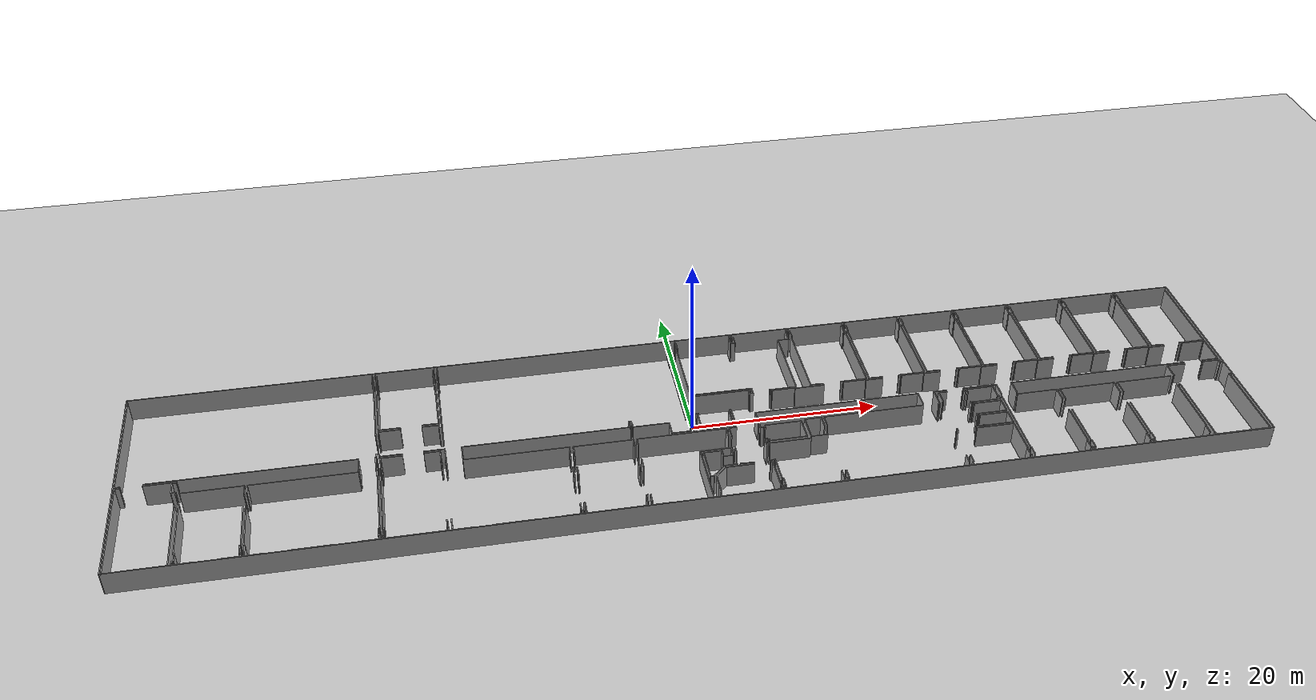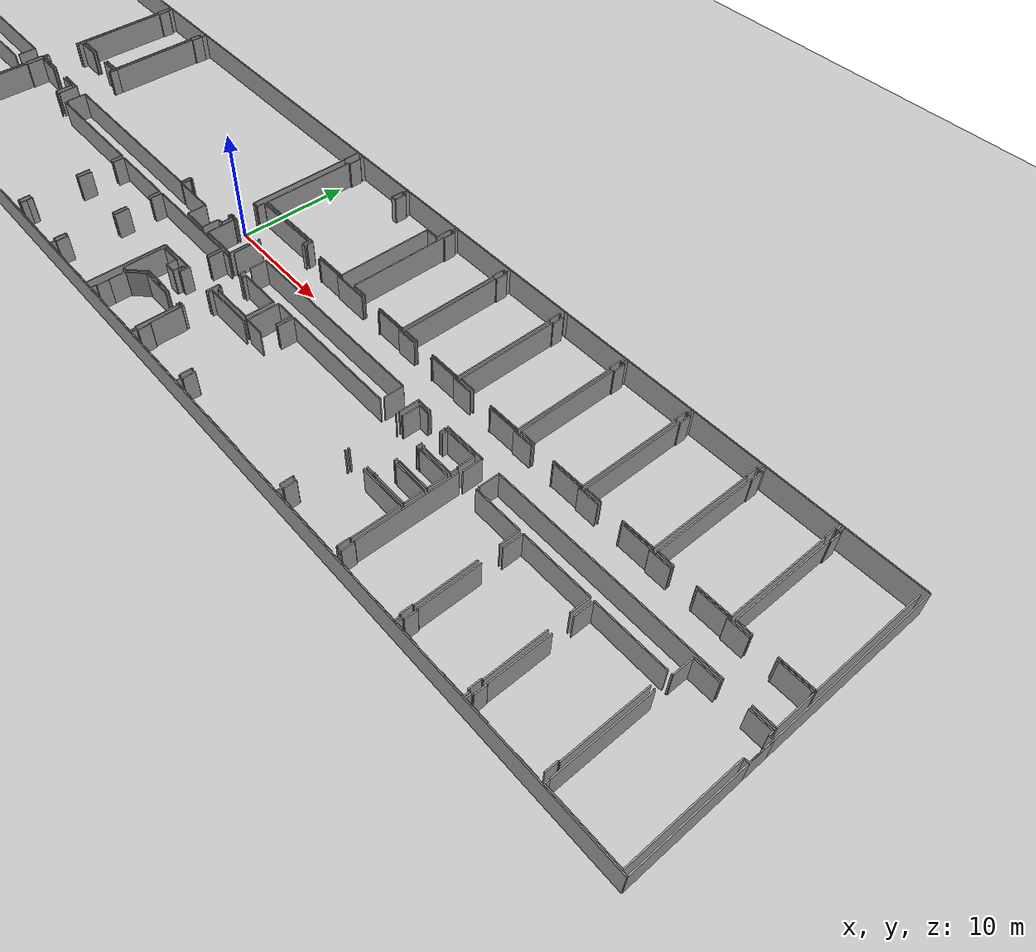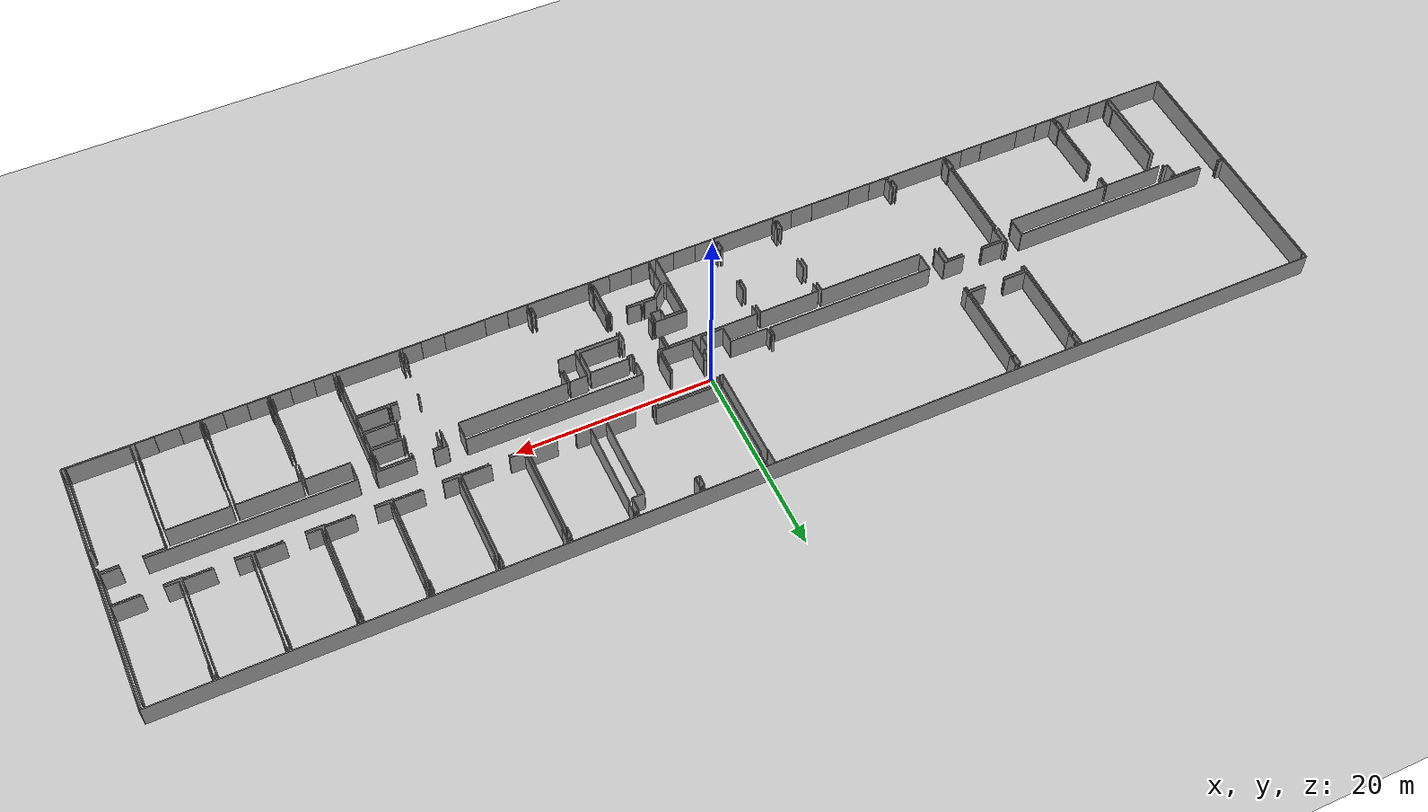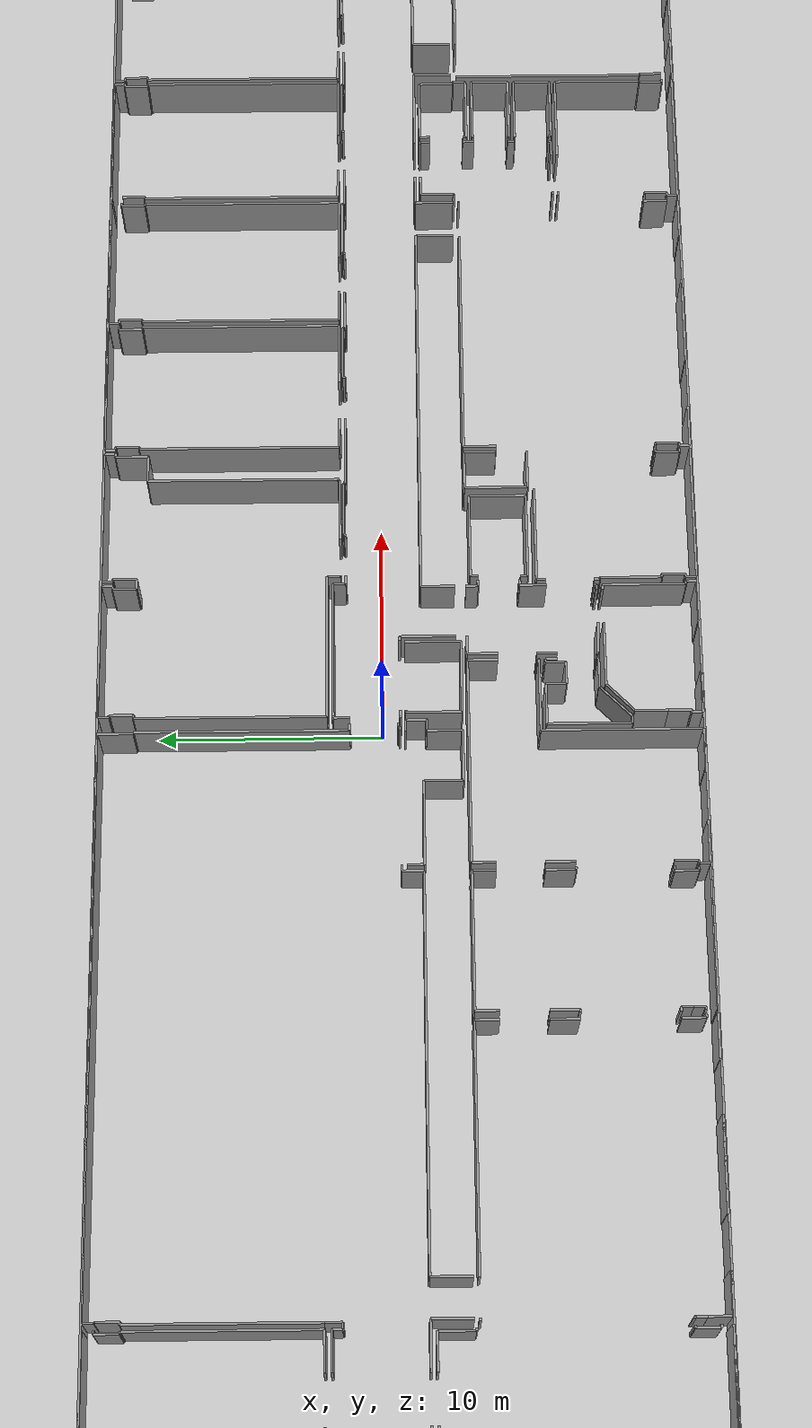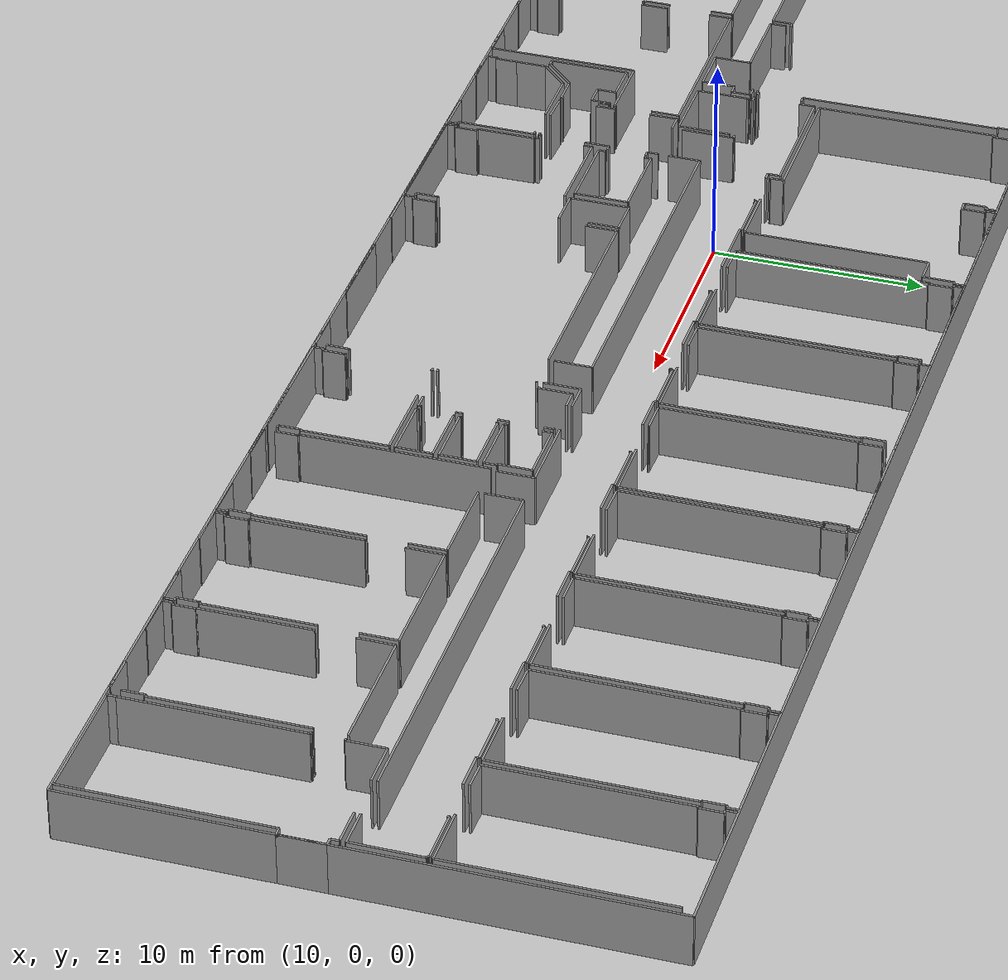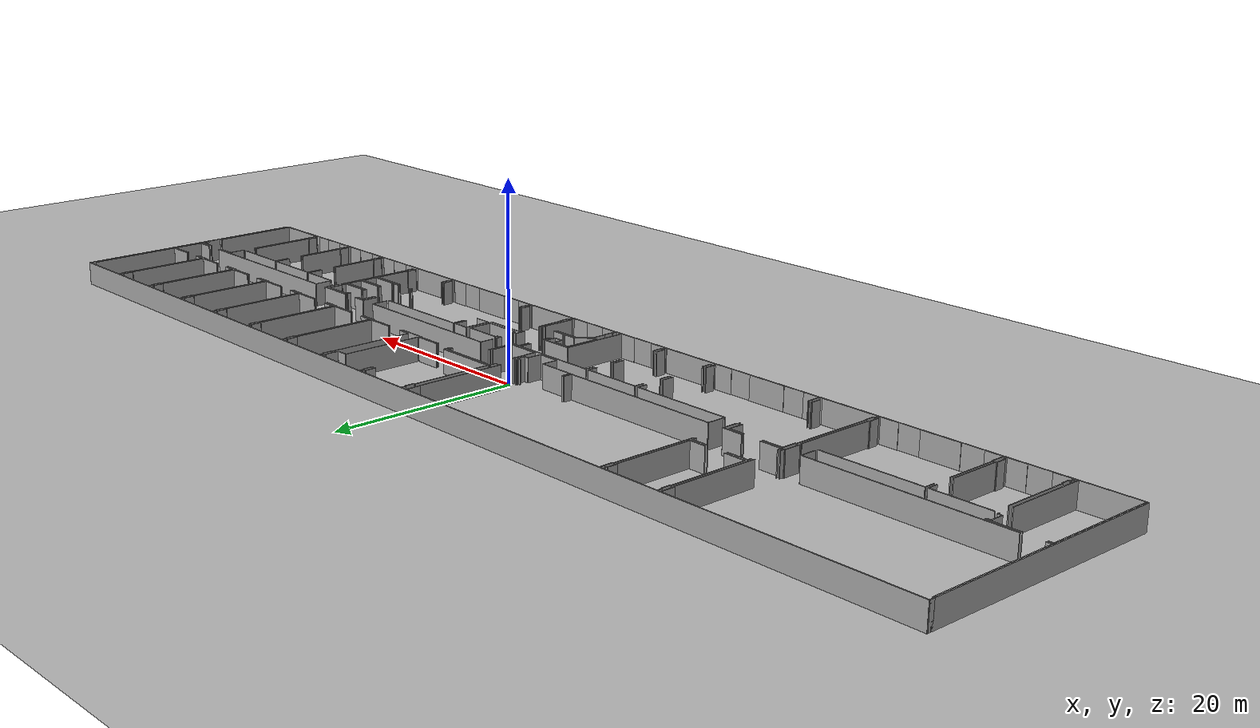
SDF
<sdf version="1.6">
  <world name="default">
    <light name="sun" type="directional">
      <cast_shadows>1</cast_shadows>
      <pose frame="">0 0 10 0 -0 0</pose>
      <diffuse>0.8 0.8 0.8 1</diffuse>
      <specular>0.1 0.1 0.1 1</specular>
      <attenuation>
        <range>1000</range>
        <constant>0.9</constant>
        <linear>0.01</linear>
        <quadratic>0.001</quadratic>
      </attenuation>
      <direction>-0.5 0.5 -1</direction>
    </light>
    <model name="ground_plane">
      <static>1</static>
      <link name="link">
        <collision name="collision">
          <geometry>
            <plane>
              <normal>0 0 1</normal>
              <size>100 100</size>
            </plane>
          </geometry>
          <surface>
            <friction>
              <ode>
                <mu>100</mu>
                <mu2>50</mu2>
              </ode>
              <torsional>
                <ode />
              </torsional>
            </friction>
            <contact>
              <ode />
            </contact>
            <bounce />
          </surface>
          <max_contacts>10</max_contacts>
        </collision>
        <visual name="visual">
          <cast_shadows>0</cast_shadows>
          <geometry>
            <plane>
              <normal>0 0 1</normal>
              <size>100 100</size>
            </plane>
          </geometry>
          <material>
            <script>
              <uri>file://media/materials/scripts/gazebo.material</uri>
              <name>Gazebo/Grey</name>
            </script>
          </material>
        </visual>
        <self_collide>0</self_collide>
        <kinematic>0</kinematic>
        <gravity>1</gravity>
      </link>
    </model>
    <gravity>0 0 -9.8</gravity>
    <magnetic_field>6e-06 2.3e-05 -4.2e-05</magnetic_field>
    <atmosphere type="adiabatic" />
    <physics default="0" name="default_physics" type="ode">
      <max_step_size>0.001</max_step_size>
      <real_time_factor>1</real_time_factor>
      <real_time_update_rate>1000</real_time_update_rate>
    </physics>
    <scene>
      <ambient>0.4 0.4 0.4 1</ambient>
      <background>0.7 0.7 0.7 1</background>
      <shadows>1</shadows>
    </scene>
    <spherical_coordinates>
      <surface_model>EARTH_WGS84</surface_model>
      <latitude_deg>0</latitude_deg>
      <longitude_deg>0</longitude_deg>
      <elevation>0</elevation>
      <heading_deg>0</heading_deg>
    </spherical_coordinates>
  <model name="0510040942_A-40">
		<static>1</static>
		<link name="Wall_0">
			<collision name="Wall_0_Collision">
				<geometry>
					<box>
						<size>13.8065391984 0.1 2.5</size>
					</box>
				</geometry>
				<pose frame="">6.9032695992 0 1.25 0 0 0</pose>
			</collision>
			<visual name="Wall_0_Visual">
				<pose frame="">6.9032695992 0 1.25 0 0 0</pose>
				<geometry>
					<box>
						<size>13.8065391984 0.1 2.5</size>
					</box>
				</geometry>
				<material>
					<script>
						<uri>file://media/materials/scripts/gazebo.material</uri>
						<name>Gazebo/Grey</name>
					</script>
					<ambient>1 1 1 1</ambient>
				</material>
			</visual>
			<pose frame="">0.139563799688 -14.3399266656 0 0 0 1.57079632679</pose>
		</link>
		<link name="Wall_1">
			<collision name="Wall_1_Collision">
				<geometry>
					<box>
						<size>0.139563799688 0.1 2.5</size>
					</box>
				</geometry>
				<pose frame="">0.0697818998439 0 1.25 0 0 0</pose>
			</collision>
			<visual name="Wall_1_Visual">
				<pose frame="">0.0697818998439 0 1.25 0 0 0</pose>
				<geometry>
					<box>
						<size>0.139563799688 0.1 2.5</size>
					</box>
				</geometry>
				<material>
					<script>
						<uri>file://media/materials/scripts/gazebo.material</uri>
						<name>Gazebo/Grey</name>
					</script>
					<ambient>1 1 1 1</ambient>
				</material>
			</visual>
			<pose frame="">0.139563799688 -0.533387467171 0 0 0 3.14159265359</pose>
		</link>
		<link name="Wall_2">
			<collision name="Wall_2_Collision">
				<geometry>
					<box>
						<size>0.529581181725 0.1 2.5</size>
					</box>
				</geometry>
				<pose frame="">0.264790590862 0 1.25 0 0 0</pose>
			</collision>
			<visual name="Wall_2_Visual">
				<pose frame="">0.264790590862 0 1.25 0 0 0</pose>
				<geometry>
					<box>
						<size>0.529581181725 0.1 2.5</size>
					</box>
				</geometry>
				<material>
					<script>
						<uri>file://media/materials/scripts/gazebo.material</uri>
						<name>Gazebo/Grey</name>
					</script>
					<ambient>1 1 1 1</ambient>
				</material>
			</visual>
			<pose frame="">0.0 -0.533387467171 0 0 0 1.57079632679</pose>
		</link>
		<link name="Wall_3">
			<collision name="Wall_3_Collision">
				<geometry>
					<box>
						<size>25.6435794308 0.1 2.5</size>
					</box>
				</geometry>
				<pose frame="">12.8217897154 0 1.25 0 0 0</pose>
			</collision>
			<visual name="Wall_3_Visual">
				<pose frame="">12.8217897154 0 1.25 0 0 0</pose>
				<geometry>
					<box>
						<size>25.6435794308 0.1 2.5</size>
					</box>
				</geometry>
				<material>
					<script>
						<uri>file://media/materials/scripts/gazebo.material</uri>
						<name>Gazebo/Grey</name>
					</script>
					<ambient>1 1 1 1</ambient>
				</material>
			</visual>
			<pose frame="">0.0 -0.00380628544603 0 0 0 0.0</pose>
		</link>
		<link name="Wall_4">
			<collision name="Wall_4_Collision">
				<geometry>
					<box>
						<size>1.58506413591 0.1 2.5</size>
					</box>
				</geometry>
				<pose frame="">0.792532067955 0 1.25 0 0 0</pose>
			</collision>
			<visual name="Wall_4_Visual">
				<pose frame="">0.792532067955 0 1.25 0 0 0</pose>
				<geometry>
					<box>
						<size>1.58506413591 0.1 2.5</size>
					</box>
				</geometry>
				<material>
					<script>
						<uri>file://media/materials/scripts/gazebo.material</uri>
						<name>Gazebo/Grey</name>
					</script>
					<ambient>1 1 1 1</ambient>
				</material>
			</visual>
			<pose frame="">25.6435794308 -0.00380628544603 0 0 0 -1.57079632679</pose>
		</link>
		<link name="Wall_5">
			<collision name="Wall_5_Collision">
				<geometry>
					<box>
						<size>0.104292221221 0.1 2.5</size>
					</box>
				</geometry>
				<pose frame="">0.0521461106107 0 1.25 0 0 0</pose>
			</collision>
			<visual name="Wall_5_Visual">
				<pose frame="">0.0521461106107 0 1.25 0 0 0</pose>
				<geometry>
					<box>
						<size>0.104292221221 0.1 2.5</size>
					</box>
				</geometry>
				<material>
					<script>
						<uri>file://media/materials/scripts/gazebo.material</uri>
						<name>Gazebo/Grey</name>
					</script>
					<ambient>1 1 1 1</ambient>
				</material>
			</visual>
			<pose frame="">25.6435794308 -1.58887042136 0 0 0 0.0</pose>
		</link>
		<link name="Wall_6">
			<collision name="Wall_6_Collision">
				<geometry>
					<box>
						<size>9.21387517921 0.1 2.5</size>
					</box>
				</geometry>
				<pose frame="">4.60693758961 0 1.25 0 0 0</pose>
			</collision>
			<visual name="Wall_6_Visual">
				<pose frame="">4.60693758961 0 1.25 0 0 0</pose>
				<geometry>
					<box>
						<size>9.21387517921 0.1 2.5</size>
					</box>
				</geometry>
				<material>
					<script>
						<uri>file://media/materials/scripts/gazebo.material</uri>
						<name>Gazebo/Grey</name>
					</script>
					<ambient>1 1 1 1</ambient>
				</material>
			</visual>
			<pose frame="">25.7478716521 -1.58887042136 0 0 0 -1.57079632679</pose>
		</link>
		<link name="Wall_7">
			<collision name="Wall_7_Collision">
				<geometry>
					<box>
						<size>0.460941167515 0.1 2.5</size>
					</box>
				</geometry>
				<pose frame="">0.230470583757 0 1.25 0 0 0</pose>
			</collision>
			<visual name="Wall_7_Visual">
				<pose frame="">0.230470583757 0 1.25 0 0 0</pose>
				<geometry>
					<box>
						<size>0.460941167515 0.1 2.5</size>
					</box>
				</geometry>
				<material>
					<script>
						<uri>file://media/materials/scripts/gazebo.material</uri>
						<name>Gazebo/Grey</name>
					</script>
					<ambient>1 1 1 1</ambient>
				</material>
			</visual>
			<pose frame="">25.7478716521 -13.8520877476 0 0 0 -1.57079632679</pose>
		</link>
		<link name="Wall_8">
			<collision name="Wall_8_Collision">
				<geometry>
					<box>
						<size>0.108225382849 0.1 2.5</size>
					</box>
				</geometry>
				<pose frame="">0.0541126914244 0 1.25 0 0 0</pose>
			</collision>
			<visual name="Wall_8_Visual">
				<pose frame="">0.0541126914244 0 1.25 0 0 0</pose>
				<geometry>
					<box>
						<size>0.108225382849 0.1 2.5</size>
					</box>
				</geometry>
				<material>
					<script>
						<uri>file://media/materials/scripts/gazebo.material</uri>
						<name>Gazebo/Grey</name>
					</script>
					<ambient>1 1 1 1</ambient>
				</material>
			</visual>
			<pose frame="">25.7478716521 -14.3130289151 0 0 0 3.14159265359</pose>
		</link>
		<link name="Wall_9">
			<collision name="Wall_9_Collision">
				<geometry>
					<box>
						<size>1.75977263788 0.1 2.5</size>
					</box>
				</geometry>
				<pose frame="">0.879886318941 0 1.25 0 0 0</pose>
			</collision>
			<visual name="Wall_9_Visual">
				<pose frame="">0.879886318941 0 1.25 0 0 0</pose>
				<geometry>
					<box>
						<size>1.75977263788 0.1 2.5</size>
					</box>
				</geometry>
				<material>
					<script>
						<uri>file://media/materials/scripts/gazebo.material</uri>
						<name>Gazebo/Grey</name>
					</script>
					<ambient>1 1 1 1</ambient>
				</material>
			</visual>
			<pose frame="">25.6396462692 -14.3130289151 0 0 0 -1.57079632679</pose>
		</link>
		<link name="Wall_10">
			<collision name="Wall_10_Collision">
				<geometry>
					<box>
						<size>1.7445474961 0.1 2.5</size>
					</box>
				</geometry>
				<pose frame="">0.872273748049 0 1.25 0 0 0</pose>
			</collision>
			<visual name="Wall_10_Visual">
				<pose frame="">0.872273748049 0 1.25 0 0 0</pose>
				<geometry>
					<box>
						<size>1.7445474961 0.1 2.5</size>
					</box>
				</geometry>
				<material>
					<script>
						<uri>file://media/materials/scripts/gazebo.material</uri>
						<name>Gazebo/Grey</name>
					</script>
					<ambient>1 1 1 1</ambient>
				</material>
			</visual>
			<pose frame="">23.9372216654 -16.072801553 0 0 0 1.57079632679</pose>
		</link>
		<link name="Wall_11">
			<collision name="Wall_11_Collision">
				<geometry>
					<box>
						<size>21.0514229164 0.1 2.5</size>
					</box>
				</geometry>
				<pose frame="">10.5257114582 0 1.25 0 0 0</pose>
			</collision>
			<visual name="Wall_11_Visual">
				<pose frame="">10.5257114582 0 1.25 0 0 0</pose>
				<geometry>
					<box>
						<size>21.0514229164 0.1 2.5</size>
					</box>
				</geometry>
				<material>
					<script>
						<uri>file://media/materials/scripts/gazebo.material</uri>
						<name>Gazebo/Grey</name>
					</script>
					<ambient>1 1 1 1</ambient>
				</material>
			</visual>
			<pose frame="">23.9372216654 -14.3282540569 0 0 0 3.14159265359</pose>
		</link>
		<link name="Wall_12">
			<collision name="Wall_12_Collision">
				<geometry>
					<box>
						<size>0.555332857936 0.1 2.5</size>
					</box>
				</geometry>
				<pose frame="">0.277666428968 0 1.25 0 0 0</pose>
			</collision>
			<visual name="Wall_12_Visual">
				<pose frame="">0.277666428968 0 1.25 0 0 0</pose>
				<geometry>
					<box>
						<size>0.555332857936 0.1 2.5</size>
					</box>
				</geometry>
				<material>
					<script>
						<uri>file://media/materials/scripts/gazebo.material</uri>
						<name>Gazebo/Grey</name>
					</script>
					<ambient>1 1 1 1</ambient>
				</material>
			</visual>
			<pose frame="">0.694773970083 -14.3282540569 0 0 0 -3.12057198426</pose>
		</link>
		<link name="Wall_13">
			<collision name="Wall_13_Collision">
				<geometry>
					<box>
						<size>12.1495362676 0.1 2.5</size>
					</box>
				</geometry>
				<pose frame="">6.07476813378 0 1.25 0 0 0</pose>
			</collision>
			<visual name="Wall_13_Visual">
				<pose frame="">6.07476813378 0 1.25 0 0 0</pose>
				<geometry>
					<box>
						<size>12.1495362676 0.1 2.5</size>
					</box>
				</geometry>
				<material>
					<script>
						<uri>file://media/materials/scripts/gazebo.material</uri>
						<name>Gazebo/Grey</name>
					</script>
					<ambient>1 1 1 1</ambient>
				</material>
			</visual>
			<pose frame="">0.168745321441 -26.726975145 0 0 0 1.57079632679</pose>
		</link>
		<link name="Wall_14">
			<collision name="Wall_14_Collision">
				<geometry>
					<box>
						<size>0.517781696842 0.1 2.5</size>
					</box>
				</geometry>
				<pose frame="">0.258890848421 0 1.25 0 0 0</pose>
			</collision>
			<visual name="Wall_14_Visual">
				<pose frame="">0.258890848421 0 1.25 0 0 0</pose>
				<geometry>
					<box>
						<size>0.517781696842 0.1 2.5</size>
					</box>
				</geometry>
				<material>
					<script>
						<uri>file://media/materials/scripts/gazebo.material</uri>
						<name>Gazebo/Grey</name>
					</script>
					<ambient>1 1 1 1</ambient>
				</material>
			</visual>
			<pose frame="">0.168745321441 -14.5774388774 0 0 0 0.0</pose>
		</link>
		<link name="Wall_15">
			<collision name="Wall_15_Collision">
				<geometry>
					<box>
						<size>3.29649694863 0.1 2.5</size>
					</box>
				</geometry>
				<pose frame="">1.64824847431 0 1.25 0 0 0</pose>
			</collision>
			<visual name="Wall_15_Visual">
				<pose frame="">1.64824847431 0 1.25 0 0 0</pose>
				<geometry>
					<box>
						<size>3.29649694863 0.1 2.5</size>
					</box>
				</geometry>
				<material>
					<script>
						<uri>file://media/materials/scripts/gazebo.material</uri>
						<name>Gazebo/Grey</name>
					</script>
					<ambient>1 1 1 1</ambient>
				</material>
			</visual>
			<pose frame="">2.84748214218 -14.5774388774 0 0 0 0.0</pose>
		</link>
		<link name="Wall_16">
			<collision name="Wall_16_Collision">
				<geometry>
					<box>
						<size>0.141213190048 0.1 2.5</size>
					</box>
				</geometry>
				<pose frame="">0.0706065950239 0 1.25 0 0 0</pose>
			</collision>
			<visual name="Wall_16_Visual">
				<pose frame="">0.0706065950239 0 1.25 0 0 0</pose>
				<geometry>
					<box>
						<size>0.141213190048 0.1 2.5</size>
					</box>
				</geometry>
				<material>
					<script>
						<uri>file://media/materials/scripts/gazebo.material</uri>
						<name>Gazebo/Grey</name>
					</script>
					<ambient>1 1 1 1</ambient>
				</material>
			</visual>
			<pose frame="">6.14397909081 -14.5774388774 0 0 0 -1.57079632679</pose>
		</link>
		<link name="Wall_17">
			<collision name="Wall_17_Collision">
				<geometry>
					<box>
						<size>0.440894730832 0.1 2.5</size>
					</box>
				</geometry>
				<pose frame="">0.220447365416 0 1.25 0 0 0</pose>
			</collision>
			<visual name="Wall_17_Visual">
				<pose frame="">0.220447365416 0 1.25 0 0 0</pose>
				<geometry>
					<box>
						<size>0.440894730832 0.1 2.5</size>
					</box>
				</geometry>
				<material>
					<script>
						<uri>file://media/materials/scripts/gazebo.material</uri>
						<name>Gazebo/Grey</name>
					</script>
					<ambient>1 1 1 1</ambient>
				</material>
			</visual>
			<pose frame="">6.14397909081 -14.7186520674 0 0 0 3.14159265359</pose>
		</link>
		<link name="Wall_18">
			<collision name="Wall_18_Collision">
				<geometry>
					<box>
						<size>1.40604184376 0.1 2.5</size>
					</box>
				</geometry>
				<pose frame="">0.703020921882 0 1.25 0 0 0</pose>
			</collision>
			<visual name="Wall_18_Visual">
				<pose frame="">0.703020921882 0 1.25 0 0 0</pose>
				<geometry>
					<box>
						<size>1.40604184376 0.1 2.5</size>
					</box>
				</geometry>
				<material>
					<script>
						<uri>file://media/materials/scripts/gazebo.material</uri>
						<name>Gazebo/Grey</name>
					</script>
					<ambient>1 1 1 1</ambient>
				</material>
			</visual>
			<pose frame="">5.70308435997 -14.7186520674 0 0 0 -1.57079632679</pose>
		</link>
		<link name="Wall_19">
			<collision name="Wall_19_Collision">
				<geometry>
					<box>
						<size>0.444574140097 0.1 2.5</size>
					</box>
				</geometry>
				<pose frame="">0.222287070048 0 1.25 0 0 0</pose>
			</collision>
			<visual name="Wall_19_Visual">
				<pose frame="">0.222287070048 0 1.25 0 0 0</pose>
				<geometry>
					<box>
						<size>0.444574140097 0.1 2.5</size>
					</box>
				</geometry>
				<material>
					<script>
						<uri>file://media/materials/scripts/gazebo.material</uri>
						<name>Gazebo/Grey</name>
					</script>
					<ambient>1 1 1 1</ambient>
				</material>
			</visual>
			<pose frame="">5.70308435997 -16.1246939112 0 0 0 0.0</pose>
		</link>
		<link name="Wall_20">
			<collision name="Wall_20_Collision">
				<geometry>
					<box>
						<size>0.215435756245 0.1 2.5</size>
					</box>
				</geometry>
				<pose frame="">0.107717878123 0 1.25 0 0 0</pose>
			</collision>
			<visual name="Wall_20_Visual">
				<pose frame="">0.107717878123 0 1.25 0 0 0</pose>
				<geometry>
					<box>
						<size>0.215435756245 0.1 2.5</size>
					</box>
				</geometry>
				<material>
					<script>
						<uri>file://media/materials/scripts/gazebo.material</uri>
						<name>Gazebo/Grey</name>
					</script>
					<ambient>1 1 1 1</ambient>
				</material>
			</visual>
			<pose frame="">6.14765850007 -16.1246939112 0 0 0 -1.57079632679</pose>
		</link>
		<link name="Wall_21">
			<collision name="Wall_21_Collision">
				<geometry>
					<box>
						<size>8.64280548613 0.1 2.5</size>
					</box>
				</geometry>
				<pose frame="">4.32140274306 0 1.25 0 0 0</pose>
			</collision>
			<visual name="Wall_21_Visual">
				<pose frame="">4.32140274306 0 1.25 0 0 0</pose>
				<geometry>
					<box>
						<size>8.64280548613 0.1 2.5</size>
					</box>
				</geometry>
				<material>
					<script>
						<uri>file://media/materials/scripts/gazebo.material</uri>
						<name>Gazebo/Grey</name>
					</script>
					<ambient>1 1 1 1</ambient>
				</material>
			</visual>
			<pose frame="">6.14765850007 -18.0765570879 0 0 0 -1.57079632679</pose>
		</link>
		<link name="Wall_22">
			<collision name="Wall_22_Collision">
				<geometry>
					<box>
						<size>5.97891802493 0.1 2.5</size>
					</box>
				</geometry>
				<pose frame="">2.98945901246 0 1.25 0 0 0</pose>
			</collision>
			<visual name="Wall_22_Visual">
				<pose frame="">2.98945901246 0 1.25 0 0 0</pose>
				<geometry>
					<box>
						<size>5.97891802493 0.1 2.5</size>
					</box>
				</geometry>
				<material>
					<script>
						<uri>file://media/materials/scripts/gazebo.material</uri>
						<name>Gazebo/Grey</name>
					</script>
					<ambient>1 1 1 1</ambient>
				</material>
			</visual>
			<pose frame="">6.14765850007 -26.7193625741 0 0 0 -3.14031941771</pose>
		</link>
		<link name="Wall_23">
			<collision name="Wall_23_Collision">
				<geometry>
					<box>
						<size>7.04733750333 0.1 2.5</size>
					</box>
				</geometry>
				<pose frame="">3.52366875167 0 1.25 0 0 0</pose>
			</collision>
			<visual name="Wall_23_Visual">
				<pose frame="">3.52366875167 0 1.25 0 0 0</pose>
				<geometry>
					<box>
						<size>7.04733750333 0.1 2.5</size>
					</box>
				</geometry>
				<material>
					<script>
						<uri>file://media/materials/scripts/gazebo.material</uri>
						<name>Gazebo/Grey</name>
					</script>
					<ambient>1 1 1 1</ambient>
				</material>
			</visual>
			<pose frame="">6.55049037644 -25.1323952954 0 0 0 1.57079632679</pose>
		</link>
		<link name="Wall_24">
			<collision name="Wall_24_Collision">
				<geometry>
					<box>
						<size>6.21185784793 0.1 2.5</size>
					</box>
				</geometry>
				<pose frame="">3.10592892396 0 1.25 0 0 0</pose>
			</collision>
			<visual name="Wall_24_Visual">
				<pose frame="">3.10592892396 0 1.25 0 0 0</pose>
				<geometry>
					<box>
						<size>6.21185784793 0.1 2.5</size>
					</box>
				</geometry>
				<material>
					<script>
						<uri>file://media/materials/scripts/gazebo.material</uri>
						<name>Gazebo/Grey</name>
					</script>
					<ambient>1 1 1 1</ambient>
				</material>
			</visual>
			<pose frame="">6.55049037644 -16.3742593603 0 0 0 0.0</pose>
		</link>
		<link name="Wall_25">
			<collision name="Wall_25_Collision">
				<geometry>
					<box>
						<size>1.12031668295 0.1 2.5</size>
					</box>
				</geometry>
				<pose frame="">0.560158341475 0 1.25 0 0 0</pose>
			</collision>
			<visual name="Wall_25_Visual">
				<pose frame="">0.560158341475 0 1.25 0 0 0</pose>
				<geometry>
					<box>
						<size>1.12031668295 0.1 2.5</size>
					</box>
				</geometry>
				<material>
					<script>
						<uri>file://media/materials/scripts/gazebo.material</uri>
						<name>Gazebo/Grey</name>
					</script>
					<ambient>1 1 1 1</ambient>
				</material>
			</visual>
			<pose frame="">12.7623482244 -16.3742593603 0 0 0 -1.57079632679</pose>
		</link>
		<link name="Wall_26">
			<collision name="Wall_26_Collision">
				<geometry>
					<box>
						<size>5.60374030983 0.1 2.5</size>
					</box>
				</geometry>
				<pose frame="">2.80187015492 0 1.25 0 0 0</pose>
			</collision>
			<visual name="Wall_26_Visual">
				<pose frame="">2.80187015492 0 1.25 0 0 0</pose>
				<geometry>
					<box>
						<size>5.60374030983 0.1 2.5</size>
					</box>
				</geometry>
				<material>
					<script>
						<uri>file://media/materials/scripts/gazebo.material</uri>
						<name>Gazebo/Grey</name>
					</script>
					<ambient>1 1 1 1</ambient>
				</material>
			</visual>
			<pose frame="">12.7623482244 -19.5358869279 0 0 0 -1.57079632679</pose>
		</link>
		<link name="Wall_27">
			<collision name="Wall_27_Collision">
				<geometry>
					<box>
						<size>0.0965527741477 0.1 2.5</size>
					</box>
				</geometry>
				<pose frame="">0.0482763870739 0 1.25 0 0 0</pose>
			</collision>
			<visual name="Wall_27_Visual">
				<pose frame="">0.0482763870739 0 1.25 0 0 0</pose>
				<geometry>
					<box>
						<size>0.0965527741477 0.1 2.5</size>
					</box>
				</geometry>
				<material>
					<script>
						<uri>file://media/materials/scripts/gazebo.material</uri>
						<name>Gazebo/Grey</name>
					</script>
					<ambient>1 1 1 1</ambient>
				</material>
			</visual>
			<pose frame="">12.7623482244 -25.1396272378 0 0 0 3.14159265359</pose>
		</link>
		<link name="Wall_28">
			<collision name="Wall_28_Collision">
				<geometry>
					<box>
						<size>1.05903548727 0.1 2.5</size>
					</box>
				</geometry>
				<pose frame="">0.529517743634 0 1.25 0 0 0</pose>
			</collision>
			<visual name="Wall_28_Visual">
				<pose frame="">0.529517743634 0 1.25 0 0 0</pose>
				<geometry>
					<box>
						<size>1.05903548727 0.1 2.5</size>
					</box>
				</geometry>
				<material>
					<script>
						<uri>file://media/materials/scripts/gazebo.material</uri>
						<name>Gazebo/Grey</name>
					</script>
					<ambient>1 1 1 1</ambient>
				</material>
			</visual>
			<pose frame="">12.6657954502 -25.1396272378 0 0 0 -1.57079632679</pose>
		</link>
		<link name="Wall_29">
			<collision name="Wall_29_Collision">
				<geometry>
					<box>
						<size>0.137787533146 0.1 2.5</size>
					</box>
				</geometry>
				<pose frame="">0.0688937665732 0 1.25 0 0 0</pose>
			</collision>
			<visual name="Wall_29_Visual">
				<pose frame="">0.0688937665732 0 1.25 0 0 0</pose>
				<geometry>
					<box>
						<size>0.137787533146 0.1 2.5</size>
					</box>
				</geometry>
				<material>
					<script>
						<uri>file://media/materials/scripts/gazebo.material</uri>
						<name>Gazebo/Grey</name>
					</script>
					<ambient>1 1 1 1</ambient>
				</material>
			</visual>
			<pose frame="">12.6657954502 -26.198662725 0 0 0 0.0</pose>
		</link>
		<link name="Wall_30">
			<collision name="Wall_30_Collision">
				<geometry>
					<box>
						<size>0.490503317812 0.1 2.5</size>
					</box>
				</geometry>
				<pose frame="">0.245251658906 0 1.25 0 0 0</pose>
			</collision>
			<visual name="Wall_30_Visual">
				<pose frame="">0.245251658906 0 1.25 0 0 0</pose>
				<geometry>
					<box>
						<size>0.490503317812 0.1 2.5</size>
					</box>
				</geometry>
				<material>
					<script>
						<uri>file://media/materials/scripts/gazebo.material</uri>
						<name>Gazebo/Grey</name>
					</script>
					<ambient>1 1 1 1</ambient>
				</material>
			</visual>
			<pose frame="">12.8035829834 -26.198662725 0 0 0 -1.57079632679</pose>
		</link>
		<link name="Wall_31">
			<collision name="Wall_31_Collision">
				<geometry>
					<box>
						<size>1.99322481191 0.1 2.5</size>
					</box>
				</geometry>
				<pose frame="">0.996612405953 0 1.25 0 0 0</pose>
			</collision>
			<visual name="Wall_31_Visual">
				<pose frame="">0.996612405953 0 1.25 0 0 0</pose>
				<geometry>
					<box>
						<size>1.99322481191 0.1 2.5</size>
					</box>
				</geometry>
				<material>
					<script>
						<uri>file://media/materials/scripts/gazebo.material</uri>
						<name>Gazebo/Grey</name>
					</script>
					<ambient>1 1 1 1</ambient>
				</material>
			</visual>
			<pose frame="">12.8035829834 -26.6891660429 0 0 0 3.14159265359</pose>
		</link>
		<link name="Wall_32">
			<collision name="Wall_32_Collision">
				<geometry>
					<box>
						<size>1.99360544045 0.1 2.5</size>
					</box>
				</geometry>
				<pose frame="">0.996802720225 0 1.25 0 0 0</pose>
			</collision>
			<visual name="Wall_32_Visual">
				<pose frame="">0.996802720225 0 1.25 0 0 0</pose>
				<geometry>
					<box>
						<size>1.99360544045 0.1 2.5</size>
					</box>
				</geometry>
				<material>
					<script>
						<uri>file://media/materials/scripts/gazebo.material</uri>
						<name>Gazebo/Grey</name>
					</script>
					<ambient>1 1 1 1</ambient>
				</material>
			</visual>
			<pose frame="">8.45109557583 -26.6891660429 0 0 0 3.14159265359</pose>
		</link>
		<link name="Wall_33">
			<collision name="Wall_33_Collision">
				<geometry>
					<box>
						<size>0.197546214649 0.1 2.5</size>
					</box>
				</geometry>
				<pose frame="">0.0987731073246 0 1.25 0 0 0</pose>
			</collision>
			<visual name="Wall_33_Visual">
				<pose frame="">0.0987731073246 0 1.25 0 0 0</pose>
				<geometry>
					<box>
						<size>0.197546214649 0.1 2.5</size>
					</box>
				</geometry>
				<material>
					<script>
						<uri>file://media/materials/scripts/gazebo.material</uri>
						<name>Gazebo/Grey</name>
					</script>
					<ambient>1 1 1 1</ambient>
				</material>
			</visual>
			<pose frame="">6.45749013538 -26.6891660429 0 0 0 1.57079632679</pose>
		</link>
		<link name="Wall_34">
			<collision name="Wall_34_Collision">
				<geometry>
					<box>
						<size>0.0456754253524 0.1 2.5</size>
					</box>
				</geometry>
				<pose frame="">0.0228377126762 0 1.25 0 0 0</pose>
			</collision>
			<visual name="Wall_34_Visual">
				<pose frame="">0.0228377126762 0 1.25 0 0 0</pose>
				<geometry>
					<box>
						<size>0.0456754253524 0.1 2.5</size>
					</box>
				</geometry>
				<material>
					<script>
						<uri>file://media/materials/scripts/gazebo.material</uri>
						<name>Gazebo/Grey</name>
					</script>
					<ambient>1 1 1 1</ambient>
				</material>
			</visual>
			<pose frame="">6.45749013538 -26.4916198282 0 0 0 0.0</pose>
		</link>
		<link name="Wall_35">
			<collision name="Wall_35_Collision">
				<geometry>
					<box>
						<size>0.282045751551 0.1 2.5</size>
					</box>
				</geometry>
				<pose frame="">0.141022875776 0 1.25 0 0 0</pose>
			</collision>
			<visual name="Wall_35_Visual">
				<pose frame="">0.141022875776 0 1.25 0 0 0</pose>
				<geometry>
					<box>
						<size>0.282045751551 0.1 2.5</size>
					</box>
				</geometry>
				<material>
					<script>
						<uri>file://media/materials/scripts/gazebo.material</uri>
						<name>Gazebo/Grey</name>
					</script>
					<ambient>1 1 1 1</ambient>
				</material>
			</visual>
			<pose frame="">6.50316556073 -26.4916198282 0 0 0 1.57079632679</pose>
		</link>
		<link name="Wall_36">
			<collision name="Wall_36_Collision">
				<geometry>
					<box>
						<size>0.140959437685 0.1 2.5</size>
					</box>
				</geometry>
				<pose frame="">0.0704797188424 0 1.25 0 0 0</pose>
			</collision>
			<visual name="Wall_36_Visual">
				<pose frame="">0.0704797188424 0 1.25 0 0 0</pose>
				<geometry>
					<box>
						<size>0.140959437685 0.1 2.5</size>
					</box>
				</geometry>
				<material>
					<script>
						<uri>file://media/materials/scripts/gazebo.material</uri>
						<name>Gazebo/Grey</name>
					</script>
					<ambient>1 1 1 1</ambient>
				</material>
			</visual>
			<pose frame="">6.50316556073 -26.2095740767 0 0 0 0.0</pose>
		</link>
		<link name="Wall_37">
			<collision name="Wall_37_Collision">
				<geometry>
					<box>
						<size>1.05954299199 0.1 2.5</size>
					</box>
				</geometry>
				<pose frame="">0.529771495997 0 1.25 0 0 0</pose>
			</collision>
			<visual name="Wall_37_Visual">
				<pose frame="">0.529771495997 0 1.25 0 0 0</pose>
				<geometry>
					<box>
						<size>1.05954299199 0.1 2.5</size>
					</box>
				</geometry>
				<material>
					<script>
						<uri>file://media/materials/scripts/gazebo.material</uri>
						<name>Gazebo/Grey</name>
					</script>
					<ambient>1 1 1 1</ambient>
				</material>
			</visual>
			<pose frame="">6.64412499841 -26.2095740767 0 0 0 1.57079632679</pose>
		</link>
		<link name="Wall_38">
			<collision name="Wall_38_Collision">
				<geometry>
					<box>
						<size>0.0952809713101 0.1 2.5</size>
					</box>
				</geometry>
				<pose frame="">0.0476404856551 0 1.25 0 0 0</pose>
			</collision>
			<visual name="Wall_38_Visual">
				<pose frame="">0.0476404856551 0 1.25 0 0 0</pose>
				<geometry>
					<box>
						<size>0.0952809713101 0.1 2.5</size>
					</box>
				</geometry>
				<material>
					<script>
						<uri>file://media/materials/scripts/gazebo.material</uri>
						<name>Gazebo/Grey</name>
					</script>
					<ambient>1 1 1 1</ambient>
				</material>
			</visual>
			<pose frame="">6.64412499841 -25.1500310847 0 0 0 2.95542670787</pose>
		</link>
		<link name="Wall_39">
			<collision name="Wall_39_Collision">
				<geometry>
					<box>
						<size>5.62239110852 0.1 2.5</size>
					</box>
				</geometry>
				<pose frame="">2.81119555426 0 1.25 0 0 0</pose>
			</collision>
			<visual name="Wall_39_Visual">
				<pose frame="">2.81119555426 0 1.25 0 0 0</pose>
				<geometry>
					<box>
						<size>5.62239110852 0.1 2.5</size>
					</box>
				</geometry>
				<material>
					<script>
						<uri>file://media/materials/scripts/gazebo.material</uri>
						<name>Gazebo/Grey</name>
					</script>
					<ambient>1 1 1 1</ambient>
				</material>
			</visual>
			<pose frame="">13.0357663956 -25.1468591801 0 0 0 1.57079632679</pose>
		</link>
		<link name="Wall_40">
			<collision name="Wall_40_Collision">
				<geometry>
					<box>
						<size>1.13046677747 0.1 2.5</size>
					</box>
				</geometry>
				<pose frame="">0.565233388736 0 1.25 0 0 0</pose>
			</collision>
			<visual name="Wall_40_Visual">
				<pose frame="">0.565233388736 0 1.25 0 0 0</pose>
				<geometry>
					<box>
						<size>1.13046677747 0.1 2.5</size>
					</box>
				</geometry>
				<material>
					<script>
						<uri>file://media/materials/scripts/gazebo.material</uri>
						<name>Gazebo/Grey</name>
					</script>
					<ambient>1 1 1 1</ambient>
				</material>
			</visual>
			<pose frame="">13.0357663956 -17.4997779667 0 0 0 1.57079632679</pose>
		</link>
		<link name="Wall_41">
			<collision name="Wall_41_Collision">
				<geometry>
					<box>
						<size>10.864534301 0.1 2.5</size>
					</box>
				</geometry>
				<pose frame="">5.43226715049 0 1.25 0 0 0</pose>
			</collision>
			<visual name="Wall_41_Visual">
				<pose frame="">5.43226715049 0 1.25 0 0 0</pose>
				<geometry>
					<box>
						<size>10.864534301 0.1 2.5</size>
					</box>
				</geometry>
				<material>
					<script>
						<uri>file://media/materials/scripts/gazebo.material</uri>
						<name>Gazebo/Grey</name>
					</script>
					<ambient>1 1 1 1</ambient>
				</material>
			</visual>
			<pose frame="">13.0357663956 -16.3693111892 0 0 0 0.0</pose>
		</link>
		<link name="Wall_42">
			<collision name="Wall_42_Collision">
				<geometry>
					<box>
						<size>0.0671175000317 0.1 2.5</size>
					</box>
				</geometry>
				<pose frame="">0.0335587500159 0 1.25 0 0 0</pose>
			</collision>
			<visual name="Wall_42_Visual">
				<pose frame="">0.0335587500159 0 1.25 0 0 0</pose>
				<geometry>
					<box>
						<size>0.0671175000317 0.1 2.5</size>
					</box>
				</geometry>
				<material>
					<script>
						<uri>file://media/materials/scripts/gazebo.material</uri>
						<name>Gazebo/Grey</name>
					</script>
					<ambient>1 1 1 1</ambient>
				</material>
			</visual>
			<pose frame="">25.6751716 -16.3693111892 0 0 0 0.0</pose>
		</link>
		<link name="Wall_43">
			<collision name="Wall_43_Collision">
				<geometry>
					<box>
						<size>8.7611809635 0.1 2.5</size>
					</box>
				</geometry>
				<pose frame="">4.38059048175 0 1.25 0 0 0</pose>
			</collision>
			<visual name="Wall_43_Visual">
				<pose frame="">4.38059048175 0 1.25 0 0 0</pose>
				<geometry>
					<box>
						<size>8.7611809635 0.1 2.5</size>
					</box>
				</geometry>
				<material>
					<script>
						<uri>file://media/materials/scripts/gazebo.material</uri>
						<name>Gazebo/Grey</name>
					</script>
					<ambient>1 1 1 1</ambient>
				</material>
			</visual>
			<pose frame="">25.7422891001 -16.3693111892 0 0 0 -1.57079632679</pose>
		</link>
		<link name="Wall_44">
			<collision name="Wall_44_Collision">
				<geometry>
					<box>
						<size>0.112158544476 0.1 2.5</size>
					</box>
				</geometry>
				<pose frame="">0.0560792722382 0 1.25 0 0 0</pose>
			</collision>
			<visual name="Wall_44_Visual">
				<pose frame="">0.0560792722382 0 1.25 0 0 0</pose>
				<geometry>
					<box>
						<size>0.112158544476 0.1 2.5</size>
					</box>
				</geometry>
				<material>
					<script>
						<uri>file://media/materials/scripts/gazebo.material</uri>
						<name>Gazebo/Grey</name>
					</script>
					<ambient>1 1 1 1</ambient>
				</material>
			</visual>
			<pose frame="">25.7422891001 -25.1304921527 0 0 0 3.14159265359</pose>
		</link>
		<link name="Wall_45">
			<collision name="Wall_45_Collision">
				<geometry>
					<box>
						<size>1.06791681998 0.1 2.5</size>
					</box>
				</geometry>
				<pose frame="">0.533958409988 0 1.25 0 0 0</pose>
			</collision>
			<visual name="Wall_45_Visual">
				<pose frame="">0.533958409988 0 1.25 0 0 0</pose>
				<geometry>
					<box>
						<size>1.06791681998 0.1 2.5</size>
					</box>
				</geometry>
				<material>
					<script>
						<uri>file://media/materials/scripts/gazebo.material</uri>
						<name>Gazebo/Grey</name>
					</script>
					<ambient>1 1 1 1</ambient>
				</material>
			</visual>
			<pose frame="">25.6301305556 -25.1304921527 0 0 0 -1.57079632679</pose>
		</link>
		<link name="Wall_46">
			<collision name="Wall_46_Collision">
				<geometry>
					<box>
						<size>0.166842178718 0.1 2.5</size>
					</box>
				</geometry>
				<pose frame="">0.0834210893589 0 1.25 0 0 0</pose>
			</collision>
			<visual name="Wall_46_Visual">
				<pose frame="">0.0834210893589 0 1.25 0 0 0</pose>
				<geometry>
					<box>
						<size>0.166842178718 0.1 2.5</size>
					</box>
				</geometry>
				<material>
					<script>
						<uri>file://media/materials/scripts/gazebo.material</uri>
						<name>Gazebo/Grey</name>
					</script>
					<ambient>1 1 1 1</ambient>
				</material>
			</visual>
			<pose frame="">25.6301305556 -26.1984089727 0 0 0 0.0</pose>
		</link>
		<link name="Wall_47">
			<collision name="Wall_47_Collision">
				<geometry>
					<box>
						<size>0.492152708172 0.1 2.5</size>
					</box>
				</geometry>
				<pose frame="">0.246076354086 0 1.25 0 0 0</pose>
			</collision>
			<visual name="Wall_47_Visual">
				<pose frame="">0.246076354086 0 1.25 0 0 0</pose>
				<geometry>
					<box>
						<size>0.492152708172 0.1 2.5</size>
					</box>
				</geometry>
				<material>
					<script>
						<uri>file://media/materials/scripts/gazebo.material</uri>
						<name>Gazebo/Grey</name>
					</script>
					<ambient>1 1 1 1</ambient>
				</material>
			</visual>
			<pose frame="">25.7969727343 -26.1984089727 0 0 0 -1.57079632679</pose>
		</link>
		<link name="Wall_48">
			<collision name="Wall_48_Collision">
				<geometry>
					<box>
						<size>2.01047997259 0.1 2.5</size>
					</box>
				</geometry>
				<pose frame="">1.0052399863 0 1.25 0 0 0</pose>
			</collision>
			<visual name="Wall_48_Visual">
				<pose frame="">1.0052399863 0 1.25 0 0 0</pose>
				<geometry>
					<box>
						<size>2.01047997259 0.1 2.5</size>
					</box>
				</geometry>
				<material>
					<script>
						<uri>file://media/materials/scripts/gazebo.material</uri>
						<name>Gazebo/Grey</name>
					</script>
					<ambient>1 1 1 1</ambient>
				</material>
			</visual>
			<pose frame="">25.7969727343 -26.6905616809 0 0 0 3.14159265359</pose>
		</link>
		<link name="Wall_49">
			<collision name="Wall_49_Collision">
				<geometry>
					<box>
						<size>4.19262341881 0.1 2.5</size>
					</box>
				</geometry>
				<pose frame="">2.0963117094 0 1.25 0 0 0</pose>
			</collision>
			<visual name="Wall_49_Visual">
				<pose frame="">2.0963117094 0 1.25 0 0 0</pose>
				<geometry>
					<box>
						<size>4.19262341881 0.1 2.5</size>
					</box>
				</geometry>
				<material>
					<script>
						<uri>file://media/materials/scripts/gazebo.material</uri>
						<name>Gazebo/Grey</name>
					</script>
					<ambient>1 1 1 1</ambient>
				</material>
			</visual>
			<pose frame="">21.4765850007 -26.6905616809 0 0 0 3.14159265359</pose>
		</link>
		<link name="Wall_50">
			<collision name="Wall_50_Collision">
				<geometry>
					<box>
						<size>1.83475646117 0.1 2.5</size>
					</box>
				</geometry>
				<pose frame="">0.917378230585 0 1.25 0 0 0</pose>
			</collision>
			<visual name="Wall_50_Visual">
				<pose frame="">0.917378230585 0 1.25 0 0 0</pose>
				<geometry>
					<box>
						<size>1.83475646117 0.1 2.5</size>
					</box>
				</geometry>
				<material>
					<script>
						<uri>file://media/materials/scripts/gazebo.material</uri>
						<name>Gazebo/Grey</name>
					</script>
					<ambient>1 1 1 1</ambient>
				</material>
			</visual>
			<pose frame="">14.9611124504 -26.6905616809 0 0 0 3.14159265359</pose>
		</link>
		<link name="Wall_51">
			<collision name="Wall_51_Collision">
				<geometry>
					<box>
						<size>1.54192623419 0.1 2.5</size>
					</box>
				</geometry>
				<pose frame="">0.770963117094 0 1.25 0 0 0</pose>
			</collision>
			<visual name="Wall_51_Visual">
				<pose frame="">0.770963117094 0 1.25 0 0 0</pose>
				<geometry>
					<box>
						<size>1.54192623419 0.1 2.5</size>
					</box>
				</geometry>
				<material>
					<script>
						<uri>file://media/materials/scripts/gazebo.material</uri>
						<name>Gazebo/Grey</name>
					</script>
					<ambient>1 1 1 1</ambient>
				</material>
			</visual>
			<pose frame="">13.1263559892 -26.6905616809 0 0 0 1.57079632679</pose>
		</link>
		<link name="Wall_52">
			<collision name="Wall_52_Collision">
				<geometry>
					<box>
						<size>0.09060700632 0.1 2.5</size>
					</box>
				</geometry>
				<pose frame="">0.04530350316 0 1.25 0 0 0</pose>
			</collision>
			<visual name="Wall_52_Visual">
				<pose frame="">0.04530350316 0 1.25 0 0 0</pose>
				<geometry>
					<box>
						<size>0.09060700632 0.1 2.5</size>
					</box>
				</geometry>
				<material>
					<script>
						<uri>file://media/materials/scripts/gazebo.material</uri>
						<name>Gazebo/Grey</name>
					</script>
					<ambient>1 1 1 1</ambient>
				</material>
			</visual>
			<pose frame="">13.1263559892 -25.1486354467 0 0 0 3.12198732273</pose>
		</link>
		<link name="Wall_53">
			<collision name="Wall_53_Collision">
				<geometry>
					<box>
						<size>8.37281297182 0.1 2.5</size>
					</box>
				</geometry>
				<pose frame="">4.18640648591 0 1.25 0 0 0</pose>
			</collision>
			<visual name="Wall_53_Visual">
				<pose frame="">4.18640648591 0 1.25 0 0 0</pose>
				<geometry>
					<box>
						<size>8.37281297182 0.1 2.5</size>
					</box>
				</geometry>
				<material>
					<script>
						<uri>file://media/materials/scripts/gazebo.material</uri>
						<name>Gazebo/Grey</name>
					</script>
					<ambient>1 1 1 1</ambient>
				</material>
			</visual>
			<pose frame="">26.030171156 -9.96878845934 0 0 0 1.57079632679</pose>
		</link>
		<link name="Wall_54">
			<collision name="Wall_54_Collision">
				<geometry>
					<box>
						<size>0.0895745841633 0.1 2.5</size>
					</box>
				</geometry>
				<pose frame="">0.0447872920817 0 1.25 0 0 0</pose>
			</collision>
			<visual name="Wall_54_Visual">
				<pose frame="">0.0447872920817 0 1.25 0 0 0</pose>
				<geometry>
					<box>
						<size>0.0895745841633 0.1 2.5</size>
					</box>
				</geometry>
				<material>
					<script>
						<uri>file://media/materials/scripts/gazebo.material</uri>
						<name>Gazebo/Grey</name>
					</script>
					<ambient>1 1 1 1</ambient>
				</material>
			</visual>
			<pose frame="">26.030171156 -1.59597548752 0 0 0 0.0</pose>
		</link>
		<link name="Wall_55">
			<collision name="Wall_55_Collision">
				<geometry>
					<box>
						<size>1.05979674436 0.1 2.5</size>
					</box>
				</geometry>
				<pose frame="">0.529898372179 0 1.25 0 0 0</pose>
			</collision>
			<visual name="Wall_55_Visual">
				<pose frame="">0.529898372179 0 1.25 0 0 0</pose>
				<geometry>
					<box>
						<size>1.05979674436 0.1 2.5</size>
					</box>
				</geometry>
				<material>
					<script>
						<uri>file://media/materials/scripts/gazebo.material</uri>
						<name>Gazebo/Grey</name>
					</script>
					<ambient>1 1 1 1</ambient>
				</material>
			</visual>
			<pose frame="">26.1197457401 -1.59597548752 0 0 0 1.57079632679</pose>
		</link>
		<link name="Wall_56">
			<collision name="Wall_56_Collision">
				<geometry>
					<box>
						<size>0.132458733522 0.1 2.5</size>
					</box>
				</geometry>
				<pose frame="">0.066229366761 0 1.25 0 0 0</pose>
			</collision>
			<visual name="Wall_56_Visual">
				<pose frame="">0.066229366761 0 1.25 0 0 0</pose>
				<geometry>
					<box>
						<size>0.132458733522 0.1 2.5</size>
					</box>
				</geometry>
				<material>
					<script>
						<uri>file://media/materials/scripts/gazebo.material</uri>
						<name>Gazebo/Grey</name>
					</script>
					<ambient>1 1 1 1</ambient>
				</material>
			</visual>
			<pose frame="">26.1197457401 -0.536178743165 0 0 0 3.14159265359</pose>
		</link>
		<link name="Wall_57">
			<collision name="Wall_57_Collision">
				<geometry>
					<box>
						<size>0.52260299174 0.1 2.5</size>
					</box>
				</geometry>
				<pose frame="">0.26130149587 0 1.25 0 0 0</pose>
			</collision>
			<visual name="Wall_57_Visual">
				<pose frame="">0.26130149587 0 1.25 0 0 0</pose>
				<geometry>
					<box>
						<size>0.52260299174 0.1 2.5</size>
					</box>
				</geometry>
				<material>
					<script>
						<uri>file://media/materials/scripts/gazebo.material</uri>
						<name>Gazebo/Grey</name>
					</script>
					<ambient>1 1 1 1</ambient>
				</material>
			</visual>
			<pose frame="">25.9872870066 -0.536178743165 0 0 0 1.57079632679</pose>
		</link>
		<link name="Wall_58">
			<collision name="Wall_58_Collision">
				<geometry>
					<box>
						<size>6.29280485175 0.1 2.5</size>
					</box>
				</geometry>
				<pose frame="">3.14640242587 0 1.25 0 0 0</pose>
			</collision>
			<visual name="Wall_58_Visual">
				<pose frame="">3.14640242587 0 1.25 0 0 0</pose>
				<geometry>
					<box>
						<size>6.29280485175 0.1 2.5</size>
					</box>
				</geometry>
				<material>
					<script>
						<uri>file://media/materials/scripts/gazebo.material</uri>
						<name>Gazebo/Grey</name>
					</script>
					<ambient>1 1 1 1</ambient>
				</material>
			</visual>
			<pose frame="">25.9872870066 -0.0135757514242 0 0 0 0.0</pose>
		</link>
		<link name="Wall_59">
			<collision name="Wall_59_Collision">
				<geometry>
					<box>
						<size>0.143116332771 0.1 2.5</size>
					</box>
				</geometry>
				<pose frame="">0.0715581663854 0 1.25 0 0 0</pose>
			</collision>
			<visual name="Wall_59_Visual">
				<pose frame="">0.0715581663854 0 1.25 0 0 0</pose>
				<geometry>
					<box>
						<size>0.143116332771 0.1 2.5</size>
					</box>
				</geometry>
				<material>
					<script>
						<uri>file://media/materials/scripts/gazebo.material</uri>
						<name>Gazebo/Grey</name>
					</script>
					<ambient>1 1 1 1</ambient>
				</material>
			</visual>
			<pose frame="">32.2800918584 -0.519050458657 0 0 0 3.14159265359</pose>
		</link>
		<link name="Wall_60">
			<collision name="Wall_60_Collision">
				<geometry>
					<box>
						<size>1.07705190505 0.1 2.5</size>
					</box>
				</geometry>
				<pose frame="">0.538525952523 0 1.25 0 0 0</pose>
			</collision>
			<visual name="Wall_60_Visual">
				<pose frame="">0.538525952523 0 1.25 0 0 0</pose>
				<geometry>
					<box>
						<size>1.07705190505 0.1 2.5</size>
					</box>
				</geometry>
				<material>
					<script>
						<uri>file://media/materials/scripts/gazebo.material</uri>
						<name>Gazebo/Grey</name>
					</script>
					<ambient>1 1 1 1</ambient>
				</material>
			</visual>
			<pose frame="">32.1369755256 -0.519050458657 0 0 0 -1.57079632679</pose>
		</link>
		<link name="Wall_61">
			<collision name="Wall_61_Collision">
				<geometry>
					<box>
						<size>0.0955377646954 0.1 2.5</size>
					</box>
				</geometry>
				<pose frame="">0.0477688823477 0 1.25 0 0 0</pose>
			</collision>
			<visual name="Wall_61_Visual">
				<pose frame="">0.0477688823477 0 1.25 0 0 0</pose>
				<geometry>
					<box>
						<size>0.0955377646954 0.1 2.5</size>
					</box>
				</geometry>
				<material>
					<script>
						<uri>file://media/materials/scripts/gazebo.material</uri>
						<name>Gazebo/Grey</name>
					</script>
					<ambient>1 1 1 1</ambient>
				</material>
			</visual>
			<pose frame="">32.1369755256 -1.5961023637 0 0 0 0.0</pose>
		</link>
		<link name="Wall_62">
			<collision name="Wall_62_Collision">
				<geometry>
					<box>
						<size>8.37141733382 0.1 2.5</size>
					</box>
				</geometry>
				<pose frame="">4.18570866691 0 1.25 0 0 0</pose>
			</collision>
			<visual name="Wall_62_Visual">
				<pose frame="">4.18570866691 0 1.25 0 0 0</pose>
				<geometry>
					<box>
						<size>8.37141733382 0.1 2.5</size>
					</box>
				</geometry>
				<material>
					<script>
						<uri>file://media/materials/scripts/gazebo.material</uri>
						<name>Gazebo/Grey</name>
					</script>
					<ambient>1 1 1 1</ambient>
				</material>
			</visual>
			<pose frame="">32.2325132903 -1.5961023637 0 0 0 -1.57079632679</pose>
		</link>
		<link name="Wall_63">
			<collision name="Wall_63_Collision">
				<geometry>
					<box>
						<size>1.72868797341 0.1 2.5</size>
					</box>
				</geometry>
				<pose frame="">0.864343986703 0 1.25 0 0 0</pose>
			</collision>
			<visual name="Wall_63_Visual">
				<pose frame="">0.864343986703 0 1.25 0 0 0</pose>
				<geometry>
					<box>
						<size>1.72868797341 0.1 2.5</size>
					</box>
				</geometry>
				<material>
					<script>
						<uri>file://media/materials/scripts/gazebo.material</uri>
						<name>Gazebo/Grey</name>
					</script>
					<ambient>1 1 1 1</ambient>
				</material>
			</visual>
			<pose frame="">32.2325132903 -9.96751969753 0 0 0 3.14159265359</pose>
		</link>
		<link name="Wall_64">
			<collision name="Wall_64_Collision">
				<geometry>
					<box>
						<size>2.30470618681 0.1 2.5</size>
					</box>
				</geometry>
				<pose frame="">1.1523530934 0 1.25 0 0 0</pose>
			</collision>
			<visual name="Wall_64_Visual">
				<pose frame="">1.1523530934 0 1.25 0 0 0</pose>
				<geometry>
					<box>
						<size>2.30470618681 0.1 2.5</size>
					</box>
				</geometry>
				<material>
					<script>
						<uri>file://media/materials/scripts/gazebo.material</uri>
						<name>Gazebo/Grey</name>
					</script>
					<ambient>1 1 1 1</ambient>
				</material>
			</visual>
			<pose frame="">28.3348769935 -9.96751969753 0 0 0 -3.14104214442</pose>
		</link>
		<link name="Wall_65">
			<collision name="Wall_65_Collision">
				<geometry>
					<box>
						<size>8.36672291511 0.1 2.5</size>
					</box>
				</geometry>
				<pose frame="">4.18336145755 0 1.25 0 0 0</pose>
			</collision>
			<visual name="Wall_65_Visual">
				<pose frame="">4.18336145755 0 1.25 0 0 0</pose>
				<geometry>
					<box>
						<size>8.36672291511 0.1 2.5</size>
					</box>
				</geometry>
				<material>
					<script>
						<uri>file://media/materials/scripts/gazebo.material</uri>
						<name>Gazebo/Grey</name>
					</script>
					<ambient>1 1 1 1</ambient>
				</material>
			</visual>
			<pose frame="">32.51329028 -9.96384028826 0 0 0 1.57079632679</pose>
		</link>
		<link name="Wall_66">
			<collision name="Wall_66_Collision">
				<geometry>
					<box>
						<size>0.102389078498 0.1 2.5</size>
					</box>
				</geometry>
				<pose frame="">0.0511945392491 0 1.25 0 0 0</pose>
			</collision>
			<visual name="Wall_66_Visual">
				<pose frame="">0.0511945392491 0 1.25 0 0 0</pose>
				<geometry>
					<box>
						<size>0.102389078498 0.1 2.5</size>
					</box>
				</geometry>
				<material>
					<script>
						<uri>file://media/materials/scripts/gazebo.material</uri>
						<name>Gazebo/Grey</name>
					</script>
					<ambient>1 1 1 1</ambient>
				</material>
			</visual>
			<pose frame="">32.51329028 -1.59711737316 0 0 0 0.0</pose>
		</link>
		<link name="Wall_67">
			<collision name="Wall_67_Collision">
				<geometry>
					<box>
						<size>1.05319918292 0.1 2.5</size>
					</box>
				</geometry>
				<pose frame="">0.526599591459 0 1.25 0 0 0</pose>
			</collision>
			<visual name="Wall_67_Visual">
				<pose frame="">0.526599591459 0 1.25 0 0 0</pose>
				<geometry>
					<box>
						<size>1.05319918292 0.1 2.5</size>
					</box>
				</geometry>
				<material>
					<script>
						<uri>file://media/materials/scripts/gazebo.material</uri>
						<name>Gazebo/Grey</name>
					</script>
					<ambient>1 1 1 1</ambient>
				</material>
			</visual>
			<pose frame="">32.6156793585 -1.59711737316 0 0 0 1.57079632679</pose>
		</link>
		<link name="Wall_68">
			<collision name="Wall_68_Collision">
				<geometry>
					<box>
						<size>0.0312115406575 0.1 2.5</size>
					</box>
				</geometry>
				<pose frame="">0.0156057703287 0 1.25 0 0 0</pose>
			</collision>
			<visual name="Wall_68_Visual">
				<pose frame="">0.0156057703287 0 1.25 0 0 0</pose>
				<geometry>
					<box>
						<size>0.0312115406575 0.1 2.5</size>
					</box>
				</geometry>
				<material>
					<script>
						<uri>file://media/materials/scripts/gazebo.material</uri>
						<name>Gazebo/Grey</name>
					</script>
					<ambient>1 1 1 1</ambient>
				</material>
			</visual>
			<pose frame="">32.6156793585 -0.543918190238 0 0 0 3.14159265359</pose>
		</link>
		<link name="Wall_69">
			<collision name="Wall_69_Collision">
				<geometry>
					<box>
						<size>0.531738076811 0.1 2.5</size>
					</box>
				</geometry>
				<pose frame="">0.265869038405 0 1.25 0 0 0</pose>
			</collision>
			<visual name="Wall_69_Visual">
				<pose frame="">0.265869038405 0 1.25 0 0 0</pose>
				<geometry>
					<box>
						<size>0.531738076811 0.1 2.5</size>
					</box>
				</geometry>
				<material>
					<script>
						<uri>file://media/materials/scripts/gazebo.material</uri>
						<name>Gazebo/Grey</name>
					</script>
					<ambient>1 1 1 1</ambient>
				</material>
			</visual>
			<pose frame="">32.5844678179 -0.543918190238 0 0 0 1.57079632679</pose>
		</link>
		<link name="Wall_70">
			<collision name="Wall_70_Collision">
				<geometry>
					<box>
						<size>25.5397947143 0.1 2.5</size>
					</box>
				</geometry>
				<pose frame="">12.7698973572 0 1.25 0 0 0</pose>
			</collision>
			<visual name="Wall_70_Visual">
				<pose frame="">12.7698973572 0 1.25 0 0 0</pose>
				<geometry>
					<box>
						<size>25.5397947143 0.1 2.5</size>
					</box>
				</geometry>
				<material>
					<script>
						<uri>file://media/materials/scripts/gazebo.material</uri>
						<name>Gazebo/Grey</name>
					</script>
					<ambient>1 1 1 1</ambient>
				</material>
			</visual>
			<pose frame="">32.5844678179 -0.0121801134273 0 0 0 0.0</pose>
		</link>
		<link name="Wall_71">
			<collision name="Wall_71_Collision">
				<geometry>
					<box>
						<size>1.58557164064 0.1 2.5</size>
					</box>
				</geometry>
				<pose frame="">0.792785820318 0 1.25 0 0 0</pose>
			</collision>
			<visual name="Wall_71_Visual">
				<pose frame="">0.792785820318 0 1.25 0 0 0</pose>
				<geometry>
					<box>
						<size>1.58557164064 0.1 2.5</size>
					</box>
				</geometry>
				<material>
					<script>
						<uri>file://media/materials/scripts/gazebo.material</uri>
						<name>Gazebo/Grey</name>
					</script>
					<ambient>1 1 1 1</ambient>
				</material>
			</visual>
			<pose frame="">58.1242625322 -0.0121801134273 0 0 0 -1.57079632679</pose>
		</link>
		<link name="Wall_72">
			<collision name="Wall_72_Collision">
				<geometry>
					<box>
						<size>0.064326224038 0.1 2.5</size>
					</box>
				</geometry>
				<pose frame="">0.032163112019 0 1.25 0 0 0</pose>
			</collision>
			<visual name="Wall_72_Visual">
				<pose frame="">0.032163112019 0 1.25 0 0 0</pose>
				<geometry>
					<box>
						<size>0.064326224038 0.1 2.5</size>
					</box>
				</geometry>
				<material>
					<script>
						<uri>file://media/materials/scripts/gazebo.material</uri>
						<name>Gazebo/Grey</name>
					</script>
					<ambient>1 1 1 1</ambient>
				</material>
			</visual>
			<pose frame="">58.1242625322 -1.59775175406 0 0 0 0.0</pose>
		</link>
		<link name="Wall_73">
			<collision name="Wall_73_Collision">
				<geometry>
					<box>
						<size>9.51063856782 0.1 2.5</size>
					</box>
				</geometry>
				<pose frame="">4.75531928391 0 1.25 0 0 0</pose>
			</collision>
			<visual name="Wall_73_Visual">
				<pose frame="">4.75531928391 0 1.25 0 0 0</pose>
				<geometry>
					<box>
						<size>9.51063856782 0.1 2.5</size>
					</box>
				</geometry>
				<material>
					<script>
						<uri>file://media/materials/scripts/gazebo.material</uri>
						<name>Gazebo/Grey</name>
					</script>
					<ambient>1 1 1 1</ambient>
				</material>
			</visual>
			<pose frame="">58.1885887562 -1.59775175406 0 0 0 -1.57079632679</pose>
		</link>
		<link name="Wall_74">
			<collision name="Wall_74_Collision">
				<geometry>
					<box>
						<size>0.317190453836 0.1 2.5</size>
					</box>
				</geometry>
				<pose frame="">0.158595226918 0 1.25 0 0 0</pose>
			</collision>
			<visual name="Wall_74_Visual">
				<pose frame="">0.158595226918 0 1.25 0 0 0</pose>
				<geometry>
					<box>
						<size>0.317190453836 0.1 2.5</size>
					</box>
				</geometry>
				<material>
					<script>
						<uri>file://media/materials/scripts/gazebo.material</uri>
						<name>Gazebo/Grey</name>
					</script>
					<ambient>1 1 1 1</ambient>
				</material>
			</visual>
			<pose frame="">58.1885887562 -11.1083903219 0 0 0 0.0</pose>
		</link>
		<link name="Wall_75">
			<collision name="Wall_75_Collision">
				<geometry>
					<box>
						<size>0.178134158874 0.1 2.5</size>
					</box>
				</geometry>
				<pose frame="">0.0890670794372 0 1.25 0 0 0</pose>
			</collision>
			<visual name="Wall_75_Visual">
				<pose frame="">0.0890670794372 0 1.25 0 0 0</pose>
				<geometry>
					<box>
						<size>0.178134158874 0.1 2.5</size>
					</box>
				</geometry>
				<material>
					<script>
						<uri>file://media/materials/scripts/gazebo.material</uri>
						<name>Gazebo/Grey</name>
					</script>
					<ambient>1 1 1 1</ambient>
				</material>
			</visual>
			<pose frame="">58.5057792101 -13.2590684751 0 0 0 3.14159265359</pose>
		</link>
		<link name="Wall_76">
			<collision name="Wall_76_Collision">
				<geometry>
					<box>
						<size>0.0763794612837 0.1 2.5</size>
					</box>
				</geometry>
				<pose frame="">0.0381897306419 0 1.25 0 0 0</pose>
			</collision>
			<visual name="Wall_76_Visual">
				<pose frame="">0.0381897306419 0 1.25 0 0 0</pose>
				<geometry>
					<box>
						<size>0.0763794612837 0.1 2.5</size>
					</box>
				</geometry>
				<material>
					<script>
						<uri>file://media/materials/scripts/gazebo.material</uri>
						<name>Gazebo/Grey</name>
					</script>
					<ambient>1 1 1 1</ambient>
				</material>
			</visual>
			<pose frame="">58.3276450512 -13.2590684751 0 0 0 -1.57079632679</pose>
		</link>
		<link name="Wall_77">
			<collision name="Wall_77_Collision">
				<geometry>
					<box>
						<size>0.157326465103 0.1 2.5</size>
					</box>
				</geometry>
				<pose frame="">0.0786632325513 0 1.25 0 0 0</pose>
			</collision>
			<visual name="Wall_77_Visual">
				<pose frame="">0.0786632325513 0 1.25 0 0 0</pose>
				<geometry>
					<box>
						<size>0.157326465103 0.1 2.5</size>
					</box>
				</geometry>
				<material>
					<script>
						<uri>file://media/materials/scripts/gazebo.material</uri>
						<name>Gazebo/Grey</name>
					</script>
					<ambient>1 1 1 1</ambient>
				</material>
			</visual>
			<pose frame="">58.3276450512 -13.3354479364 0 0 0 3.14159265359</pose>
		</link>
		<link name="Wall_78">
			<collision name="Wall_78_Collision">
				<geometry>
					<box>
						<size>0.258573657967 0.1 2.5</size>
					</box>
				</geometry>
				<pose frame="">0.129286828984 0 1.25 0 0 0</pose>
			</collision>
			<visual name="Wall_78_Visual">
				<pose frame="">0.129286828984 0 1.25 0 0 0</pose>
				<geometry>
					<box>
						<size>0.258573657967 0.1 2.5</size>
					</box>
				</geometry>
				<material>
					<script>
						<uri>file://media/materials/scripts/gazebo.material</uri>
						<name>Gazebo/Grey</name>
					</script>
					<ambient>1 1 1 1</ambient>
				</material>
			</visual>
			<pose frame="">51.9834553459 -13.3354479364 0 0 0 3.14159265359</pose>
		</link>
		<link name="Wall_79">
			<collision name="Wall_79_Collision">
				<geometry>
					<box>
						<size>0.966796503292 0.1 2.5</size>
					</box>
				</geometry>
				<pose frame="">0.483398251646 0 1.25 0 0 0</pose>
			</collision>
			<visual name="Wall_79_Visual">
				<pose frame="">0.483398251646 0 1.25 0 0 0</pose>
				<geometry>
					<box>
						<size>0.966796503292 0.1 2.5</size>
					</box>
				</geometry>
				<material>
					<script>
						<uri>file://media/materials/scripts/gazebo.material</uri>
						<name>Gazebo/Grey</name>
					</script>
					<ambient>1 1 1 1</ambient>
				</material>
			</visual>
			<pose frame="">51.724881688 -13.3354479364 0 0 0 -1.57079632679</pose>
		</link>
		<link name="Wall_80">
			<collision name="Wall_80_Collision">
				<geometry>
					<box>
						<size>17.3984038976 0.1 2.5</size>
					</box>
				</geometry>
				<pose frame="">8.69920194882 0 1.25 0 0 0</pose>
			</collision>
			<visual name="Wall_80_Visual">
				<pose frame="">8.69920194882 0 1.25 0 0 0</pose>
				<geometry>
					<box>
						<size>17.3984038976 0.1 2.5</size>
					</box>
				</geometry>
				<material>
					<script>
						<uri>file://media/materials/scripts/gazebo.material</uri>
						<name>Gazebo/Grey</name>
					</script>
					<ambient>1 1 1 1</ambient>
				</material>
			</visual>
			<pose frame="">51.724881688 -14.3022444397 0 0 0 3.14159265359</pose>
		</link>
		<link name="Wall_81">
			<collision name="Wall_81_Collision">
				<geometry>
					<box>
						<size>1.80836621541 0.1 2.5</size>
					</box>
				</geometry>
				<pose frame="">0.904183107705 0 1.25 0 0 0</pose>
			</collision>
			<visual name="Wall_81_Visual">
				<pose frame="">0.904183107705 0 1.25 0 0 0</pose>
				<geometry>
					<box>
						<size>1.80836621541 0.1 2.5</size>
					</box>
				</geometry>
				<material>
					<script>
						<uri>file://media/materials/scripts/gazebo.material</uri>
						<name>Gazebo/Grey</name>
					</script>
					<ambient>1 1 1 1</ambient>
				</material>
			</visual>
			<pose frame="">34.3264777903 -14.3022444397 0 0 0 -1.57079632679</pose>
		</link>
		<link name="Wall_82">
			<collision name="Wall_82_Collision">
				<geometry>
					<box>
						<size>1.80011926361 0.1 2.5</size>
					</box>
				</geometry>
				<pose frame="">0.900059631805 0 1.25 0 0 0</pose>
			</collision>
			<visual name="Wall_82_Visual">
				<pose frame="">0.900059631805 0 1.25 0 0 0</pose>
				<geometry>
					<box>
						<size>1.80011926361 0.1 2.5</size>
					</box>
				</geometry>
				<material>
					<script>
						<uri>file://media/materials/scripts/gazebo.material</uri>
						<name>Gazebo/Grey</name>
					</script>
					<ambient>1 1 1 1</ambient>
				</material>
			</visual>
			<pose frame="">32.6211350343 -16.1106106551 0 0 0 1.57079632679</pose>
		</link>
		<link name="Wall_83">
			<collision name="Wall_83_Collision">
				<geometry>
					<box>
						<size>2.15511881954 0.1 2.5</size>
					</box>
				</geometry>
				<pose frame="">1.07755940977 0 1.25 0 0 0</pose>
			</collision>
			<visual name="Wall_83_Visual">
				<pose frame="">1.07755940977 0 1.25 0 0 0</pose>
				<geometry>
					<box>
						<size>2.15511881954 0.1 2.5</size>
					</box>
				</geometry>
				<material>
					<script>
						<uri>file://media/materials/scripts/gazebo.material</uri>
						<name>Gazebo/Grey</name>
					</script>
					<ambient>1 1 1 1</ambient>
				</material>
			</visual>
			<pose frame="">32.6211350343 -14.3104913915 0 0 0 3.14159265359</pose>
		</link>
		<link name="Wall_84">
			<collision name="Wall_84_Collision">
				<geometry>
					<box>
						<size>2.3148559321 0.1 2.5</size>
					</box>
				</geometry>
				<pose frame="">1.15742796605 0 1.25 0 0 0</pose>
			</collision>
			<visual name="Wall_84_Visual">
				<pose frame="">1.15742796605 0 1.25 0 0 0</pose>
				<geometry>
					<box>
						<size>2.3148559321 0.1 2.5</size>
					</box>
				</geometry>
				<material>
					<script>
						<uri>file://media/materials/scripts/gazebo.material</uri>
						<name>Gazebo/Grey</name>
					</script>
					<ambient>1 1 1 1</ambient>
				</material>
			</visual>
			<pose frame="">28.3481989926 -14.3104913915 0 0 0 3.14159265359</pose>
		</link>
		<link name="Wall_85">
			<collision name="Wall_85_Collision">
				<geometry>
					<box>
						<size>0.481368232742 0.1 2.5</size>
					</box>
				</geometry>
				<pose frame="">0.240684116371 0 1.25 0 0 0</pose>
			</collision>
			<visual name="Wall_85_Visual">
				<pose frame="">0.240684116371 0 1.25 0 0 0</pose>
				<geometry>
					<box>
						<size>0.481368232742 0.1 2.5</size>
					</box>
				</geometry>
				<material>
					<script>
						<uri>file://media/materials/scripts/gazebo.material</uri>
						<name>Gazebo/Grey</name>
					</script>
					<ambient>1 1 1 1</ambient>
				</material>
			</visual>
			<pose frame="">26.0333430605 -14.3104913915 0 0 0 1.57079632679</pose>
		</link>
		<link name="Wall_86">
			<collision name="Wall_86_Collision">
				<geometry>
					<box>
						<size>0.46056053897 0.1 2.5</size>
					</box>
				</geometry>
				<pose frame="">0.230280269485 0 1.25 0 0 0</pose>
			</collision>
			<visual name="Wall_86_Visual">
				<pose frame="">0.230280269485 0 1.25 0 0 0</pose>
				<geometry>
					<box>
						<size>0.46056053897 0.1 2.5</size>
					</box>
				</geometry>
				<material>
					<script>
						<uri>file://media/materials/scripts/gazebo.material</uri>
						<name>Gazebo/Grey</name>
					</script>
					<ambient>1 1 1 1</ambient>
				</material>
			</visual>
			<pose frame="">26.0333430605 -10.7267467678 0 0 0 1.57079632679</pose>
		</link>
		<link name="Wall_87">
			<collision name="Wall_87_Collision">
				<geometry>
					<box>
						<size>2.27044926856 0.1 2.5</size>
					</box>
				</geometry>
				<pose frame="">1.13522463428 0 1.25 0 0 0</pose>
			</collision>
			<visual name="Wall_87_Visual">
				<pose frame="">1.13522463428 0 1.25 0 0 0</pose>
				<geometry>
					<box>
						<size>2.27044926856 0.1 2.5</size>
					</box>
				</geometry>
				<material>
					<script>
						<uri>file://media/materials/scripts/gazebo.material</uri>
						<name>Gazebo/Grey</name>
					</script>
					<ambient>1 1 1 1</ambient>
				</material>
			</visual>
			<pose frame="">26.0333430605 -10.2661862289 0 0 0 0.0</pose>
		</link>
		<link name="Wall_88">
			<collision name="Wall_88_Collision">
				<geometry>
					<box>
						<size>1.74822690536 0.1 2.5</size>
					</box>
				</geometry>
				<pose frame="">0.874113452682 0 1.25 0 0 0</pose>
			</collision>
			<visual name="Wall_88_Visual">
				<pose frame="">0.874113452682 0 1.25 0 0 0</pose>
				<geometry>
					<box>
						<size>1.74822690536 0.1 2.5</size>
					</box>
				</geometry>
				<material>
					<script>
						<uri>file://media/materials/scripts/gazebo.material</uri>
						<name>Gazebo/Grey</name>
					</script>
					<ambient>1 1 1 1</ambient>
				</material>
			</visual>
			<pose frame="">30.4965933745 -10.2661862289 0 0 0 0.0</pose>
		</link>
		<link name="Wall_89">
			<collision name="Wall_89_Collision">
				<geometry>
					<box>
						<size>0.44482789246 0.1 2.5</size>
					</box>
				</geometry>
				<pose frame="">0.22241394623 0 1.25 0 0 0</pose>
			</collision>
			<visual name="Wall_89_Visual">
				<pose frame="">0.22241394623 0 1.25 0 0 0</pose>
				<geometry>
					<box>
						<size>0.44482789246 0.1 2.5</size>
					</box>
				</geometry>
				<material>
					<script>
						<uri>file://media/materials/scripts/gazebo.material</uri>
						<name>Gazebo/Grey</name>
					</script>
					<ambient>1 1 1 1</ambient>
				</material>
			</visual>
			<pose frame="">32.2448202799 -10.2661862289 0 0 0 -1.57079632679</pose>
		</link>
		<link name="Wall_90">
			<collision name="Wall_90_Collision">
				<geometry>
					<box>
						<size>0.268470000127 0.1 2.5</size>
					</box>
				</geometry>
				<pose frame="">0.134235000063 0 1.25 0 0 0</pose>
			</collision>
			<visual name="Wall_90_Visual">
				<pose frame="">0.134235000063 0 1.25 0 0 0</pose>
				<geometry>
					<box>
						<size>0.268470000127 0.1 2.5</size>
					</box>
				</geometry>
				<material>
					<script>
						<uri>file://media/materials/scripts/gazebo.material</uri>
						<name>Gazebo/Grey</name>
					</script>
					<ambient>1 1 1 1</ambient>
				</material>
			</visual>
			<pose frame="">32.2448202799 -10.7110141213 0 0 0 0.0</pose>
		</link>
		<link name="Wall_91">
			<collision name="Wall_91_Collision">
				<geometry>
					<box>
						<size>0.747173833056 0.1 2.5</size>
					</box>
				</geometry>
				<pose frame="">0.373586916528 0 1.25 0 0 0</pose>
			</collision>
			<visual name="Wall_91_Visual">
				<pose frame="">0.373586916528 0 1.25 0 0 0</pose>
				<geometry>
					<box>
						<size>0.747173833056 0.1 2.5</size>
					</box>
				</geometry>
				<material>
					<script>
						<uri>file://media/materials/scripts/gazebo.material</uri>
						<name>Gazebo/Grey</name>
					</script>
					<ambient>1 1 1 1</ambient>
				</material>
			</visual>
			<pose frame="">32.51329028 -10.7110141213 0 0 0 1.57079632679</pose>
		</link>
		<link name="Wall_92">
			<collision name="Wall_92_Collision">
				<geometry>
					<box>
						<size>8.95098773107 0.1 2.5</size>
					</box>
				</geometry>
				<pose frame="">4.47549386554 0 1.25 0 0 0</pose>
			</collision>
			<visual name="Wall_92_Visual">
				<pose frame="">4.47549386554 0 1.25 0 0 0</pose>
				<geometry>
					<box>
						<size>8.95098773107 0.1 2.5</size>
					</box>
				</geometry>
				<material>
					<script>
						<uri>file://media/materials/scripts/gazebo.material</uri>
						<name>Gazebo/Grey</name>
					</script>
					<ambient>1 1 1 1</ambient>
				</material>
			</visual>
			<pose frame="">26.0314399178 -25.1247827245 0 0 0 1.57079632679</pose>
		</link>
		<link name="Wall_93">
			<collision name="Wall_93_Collision">
				<geometry>
					<box>
						<size>0.0946496314247 0.1 2.5</size>
					</box>
				</geometry>
				<pose frame="">0.0473248157123 0 1.25 0 0 0</pose>
			</collision>
			<visual name="Wall_93_Visual">
				<pose frame="">0.0473248157123 0 1.25 0 0 0</pose>
				<geometry>
					<box>
						<size>0.0946496314247 0.1 2.5</size>
					</box>
				</geometry>
				<material>
					<script>
						<uri>file://media/materials/scripts/gazebo.material</uri>
						<name>Gazebo/Grey</name>
					</script>
					<ambient>1 1 1 1</ambient>
				</material>
			</visual>
			<pose frame="">26.0314399178 -16.1737949935 0 0 0 0.0</pose>
		</link>
		<link name="Wall_94">
			<collision name="Wall_94_Collision">
				<geometry>
					<box>
						<size>1.59394546862 0.1 2.5</size>
					</box>
				</geometry>
				<pose frame="">0.796972734309 0 1.25 0 0 0</pose>
			</collision>
			<visual name="Wall_94_Visual">
				<pose frame="">0.796972734309 0 1.25 0 0 0</pose>
				<geometry>
					<box>
						<size>1.59394546862 0.1 2.5</size>
					</box>
				</geometry>
				<material>
					<script>
						<uri>file://media/materials/scripts/gazebo.material</uri>
						<name>Gazebo/Grey</name>
					</script>
					<ambient>1 1 1 1</ambient>
				</material>
			</visual>
			<pose frame="">26.1260895492 -16.1737949935 0 0 0 1.57079632679</pose>
		</link>
		<link name="Wall_95">
			<collision name="Wall_95_Collision">
				<geometry>
					<box>
						<size>2.22845325247 0.1 2.5</size>
					</box>
				</geometry>
				<pose frame="">1.11422662624 0 1.25 0 0 0</pose>
			</collision>
			<visual name="Wall_95_Visual">
				<pose frame="">1.11422662624 0 1.25 0 0 0</pose>
				<geometry>
					<box>
						<size>2.22845325247 0.1 2.5</size>
					</box>
				</geometry>
				<material>
					<script>
						<uri>file://media/materials/scripts/gazebo.material</uri>
						<name>Gazebo/Grey</name>
					</script>
					<ambient>1 1 1 1</ambient>
				</material>
			</visual>
			<pose frame="">26.1260895492 -14.5798495248 0 0 0 0.0</pose>
		</link>
		<link name="Wall_96">
			<collision name="Wall_96_Collision">
				<geometry>
					<box>
						<size>1.6401283987 0.1 2.5</size>
					</box>
				</geometry>
				<pose frame="">0.820064199348 0 1.25 0 0 0</pose>
			</collision>
			<visual name="Wall_96_Visual">
				<pose frame="">0.820064199348 0 1.25 0 0 0</pose>
				<geometry>
					<box>
						<size>1.6401283987 0.1 2.5</size>
					</box>
				</geometry>
				<material>
					<script>
						<uri>file://media/materials/scripts/gazebo.material</uri>
						<name>Gazebo/Grey</name>
					</script>
					<ambient>1 1 1 1</ambient>
				</material>
			</visual>
			<pose frame="">30.4849207658 -14.5798495248 0 0 0 0.0</pose>
		</link>
		<link name="Wall_97">
			<collision name="Wall_97_Collision">
				<geometry>
					<box>
						<size>1.60561807732 0.1 2.5</size>
					</box>
				</geometry>
				<pose frame="">0.802809038659 0 1.25 0 0 0</pose>
			</collision>
			<visual name="Wall_97_Visual">
				<pose frame="">0.802809038659 0 1.25 0 0 0</pose>
				<geometry>
					<box>
						<size>1.60561807732 0.1 2.5</size>
					</box>
				</geometry>
				<material>
					<script>
						<uri>file://media/materials/scripts/gazebo.material</uri>
						<name>Gazebo/Grey</name>
					</script>
					<ambient>1 1 1 1</ambient>
				</material>
			</visual>
			<pose frame="">32.1250491645 -14.5798495248 0 0 0 -1.57079632679</pose>
		</link>
		<link name="Wall_98">
			<collision name="Wall_98_Collision">
				<geometry>
					<box>
						<size>0.112158544476 0.1 2.5</size>
					</box>
				</geometry>
				<pose frame="">0.0560792722382 0 1.25 0 0 0</pose>
			</collision>
			<visual name="Wall_98_Visual">
				<pose frame="">0.0560792722382 0 1.25 0 0 0</pose>
				<geometry>
					<box>
						<size>0.112158544476 0.1 2.5</size>
					</box>
				</geometry>
				<material>
					<script>
						<uri>file://media/materials/scripts/gazebo.material</uri>
						<name>Gazebo/Grey</name>
					</script>
					<ambient>1 1 1 1</ambient>
				</material>
			</visual>
			<pose frame="">32.1250491645 -16.1854676022 0 0 0 0.0</pose>
		</link>
		<link name="Wall_99">
			<collision name="Wall_99_Collision">
				<geometry>
					<box>
						<size>0.0936346219724 0.1 2.5</size>
					</box>
				</geometry>
				<pose frame="">0.0468173109862 0 1.25 0 0 0</pose>
			</collision>
			<visual name="Wall_99_Visual">
				<pose frame="">0.0468173109862 0 1.25 0 0 0</pose>
				<geometry>
					<box>
						<size>0.0936346219724 0.1 2.5</size>
					</box>
				</geometry>
				<material>
					<script>
						<uri>file://media/materials/scripts/gazebo.material</uri>
						<name>Gazebo/Grey</name>
					</script>
					<ambient>1 1 1 1</ambient>
				</material>
			</visual>
			<pose frame="">32.237207709 -25.1312534098 0 0 0 3.14159265359</pose>
		</link>
		<link name="Wall_100">
			<collision name="Wall_100_Collision">
				<geometry>
					<box>
						<size>1.07299186724 0.1 2.5</size>
					</box>
				</geometry>
				<pose frame="">0.536495933618 0 1.25 0 0 0</pose>
			</collision>
			<visual name="Wall_100_Visual">
				<pose frame="">0.536495933618 0 1.25 0 0 0</pose>
				<geometry>
					<box>
						<size>1.07299186724 0.1 2.5</size>
					</box>
				</geometry>
				<material>
					<script>
						<uri>file://media/materials/scripts/gazebo.material</uri>
						<name>Gazebo/Grey</name>
					</script>
					<ambient>1 1 1 1</ambient>
				</material>
			</visual>
			<pose frame="">32.143573087 -25.1312534098 0 0 0 -1.57079632679</pose>
		</link>
		<link name="Wall_101">
			<collision name="Wall_101_Collision">
				<geometry>
					<box>
						<size>0.136518771331 0.1 2.5</size>
					</box>
				</geometry>
				<pose frame="">0.0682593856655 0 1.25 0 0 0</pose>
			</collision>
			<visual name="Wall_101_Visual">
				<pose frame="">0.0682593856655 0 1.25 0 0 0</pose>
				<geometry>
					<box>
						<size>0.136518771331 0.1 2.5</size>
					</box>
				</geometry>
				<material>
					<script>
						<uri>file://media/materials/scripts/gazebo.material</uri>
						<name>Gazebo/Grey</name>
					</script>
					<ambient>1 1 1 1</ambient>
				</material>
			</visual>
			<pose frame="">32.143573087 -26.204245277 0 0 0 0.0</pose>
		</link>
		<link name="Wall_102">
			<collision name="Wall_102_Collision">
				<geometry>
					<box>
						<size>6.30701498408 0.1 2.5</size>
					</box>
				</geometry>
				<pose frame="">3.15350749204 0 1.25 0 0 0</pose>
			</collision>
			<visual name="Wall_102_Visual">
				<pose frame="">3.15350749204 0 1.25 0 0 0</pose>
				<geometry>
					<box>
						<size>6.30701498408 0.1 2.5</size>
					</box>
				</geometry>
				<material>
					<script>
						<uri>file://media/materials/scripts/gazebo.material</uri>
						<name>Gazebo/Grey</name>
					</script>
					<ambient>1 1 1 1</ambient>
				</material>
			</visual>
			<pose frame="">32.2800918584 -26.6955098519 0 0 0 3.14159265359</pose>
		</link>
		<link name="Wall_103">
			<collision name="Wall_103_Collision">
				<geometry>
					<box>
						<size>0.491772079627 0.1 2.5</size>
					</box>
				</geometry>
				<pose frame="">0.245886039814 0 1.25 0 0 0</pose>
			</collision>
			<visual name="Wall_103_Visual">
				<pose frame="">0.245886039814 0 1.25 0 0 0</pose>
				<geometry>
					<box>
						<size>0.491772079627 0.1 2.5</size>
					</box>
				</geometry>
				<material>
					<script>
						<uri>file://media/materials/scripts/gazebo.material</uri>
						<name>Gazebo/Grey</name>
					</script>
					<ambient>1 1 1 1</ambient>
				</material>
			</visual>
			<pose frame="">25.9730768743 -26.6955098519 0 0 0 1.57079632679</pose>
		</link>
		<link name="Wall_104">
			<collision name="Wall_104_Collision">
				<geometry>
					<box>
						<size>0.153520179657 0.1 2.5</size>
					</box>
				</geometry>
				<pose frame="">0.0767600898283 0 1.25 0 0 0</pose>
			</collision>
			<visual name="Wall_104_Visual">
				<pose frame="">0.0767600898283 0 1.25 0 0 0</pose>
				<geometry>
					<box>
						<size>0.153520179657 0.1 2.5</size>
					</box>
				</geometry>
				<material>
					<script>
						<uri>file://media/materials/scripts/gazebo.material</uri>
						<name>Gazebo/Grey</name>
					</script>
					<ambient>1 1 1 1</ambient>
				</material>
			</visual>
			<pose frame="">25.9730768743 -26.2037377723 0 0 0 0.0</pose>
		</link>
		<link name="Wall_105">
			<collision name="Wall_105_Collision">
				<geometry>
					<box>
						<size>1.0684243247 0.1 2.5</size>
					</box>
				</geometry>
				<pose frame="">0.534212162351 0 1.25 0 0 0</pose>
			</collision>
			<visual name="Wall_105_Visual">
				<pose frame="">0.534212162351 0 1.25 0 0 0</pose>
				<geometry>
					<box>
						<size>1.0684243247 0.1 2.5</size>
					</box>
				</geometry>
				<material>
					<script>
						<uri>file://media/materials/scripts/gazebo.material</uri>
						<name>Gazebo/Grey</name>
					</script>
					<ambient>1 1 1 1</ambient>
				</material>
			</visual>
			<pose frame="">26.1265970539 -26.2037377723 0 0 0 1.57079632679</pose>
		</link>
		<link name="Wall_106">
			<collision name="Wall_106_Collision">
				<geometry>
					<box>
						<size>0.0957380629047 0.1 2.5</size>
					</box>
				</geometry>
				<pose frame="">0.0478690314524 0 1.25 0 0 0</pose>
			</collision>
			<visual name="Wall_106_Visual">
				<pose frame="">0.0478690314524 0 1.25 0 0 0</pose>
				<geometry>
					<box>
						<size>0.0957380629047 0.1 2.5</size>
					</box>
				</geometry>
				<material>
					<script>
						<uri>file://media/materials/scripts/gazebo.material</uri>
						<name>Gazebo/Grey</name>
					</script>
					<ambient>1 1 1 1</ambient>
				</material>
			</visual>
			<pose frame="">26.1265970539 -25.1353134476 0 0 0 3.03137447819</pose>
		</link>
		<link name="Wall_107">
			<collision name="Wall_107_Collision">
				<geometry>
					<box>
						<size>0.536178743165 0.1 2.5</size>
					</box>
				</geometry>
				<pose frame="">0.268089371582 0 1.25 0 0 0</pose>
			</collision>
			<visual name="Wall_107_Visual">
				<pose frame="">0.268089371582 0 1.25 0 0 0</pose>
				<geometry>
					<box>
						<size>0.536178743165 0.1 2.5</size>
					</box>
				</geometry>
				<material>
					<script>
						<uri>file://media/materials/scripts/gazebo.material</uri>
						<name>Gazebo/Grey</name>
					</script>
					<ambient>1 1 1 1</ambient>
				</material>
			</visual>
			<pose frame="">32.5918266364 -25.6673052768 0 0 0 1.57079632679</pose>
		</link>
		<link name="Wall_108">
			<collision name="Wall_108_Collision">
				<geometry>
					<box>
						<size>0.0694012712993 0.1 2.5</size>
					</box>
				</geometry>
				<pose frame="">0.0347006356497 0 1.25 0 0 0</pose>
			</collision>
			<visual name="Wall_108_Visual">
				<pose frame="">0.0347006356497 0 1.25 0 0 0</pose>
				<geometry>
					<box>
						<size>0.0694012712993 0.1 2.5</size>
					</box>
				</geometry>
				<material>
					<script>
						<uri>file://media/materials/scripts/gazebo.material</uri>
						<name>Gazebo/Grey</name>
					</script>
					<ambient>1 1 1 1</ambient>
				</material>
			</visual>
			<pose frame="">32.5918266364 -25.1311265336 0 0 0 3.14159265359</pose>
		</link>
		<link name="Wall_109">
			<collision name="Wall_109_Collision">
				<geometry>
					<box>
						<size>0.110636030298 0.1 2.5</size>
					</box>
				</geometry>
				<pose frame="">0.055318015149 0 1.25 0 0 0</pose>
			</collision>
			<visual name="Wall_109_Visual">
				<pose frame="">0.055318015149 0 1.25 0 0 0</pose>
				<geometry>
					<box>
						<size>0.110636030298 0.1 2.5</size>
					</box>
				</geometry>
				<material>
					<script>
						<uri>file://media/materials/scripts/gazebo.material</uri>
						<name>Gazebo/Grey</name>
					</script>
					<ambient>1 1 1 1</ambient>
				</material>
			</visual>
			<pose frame="">32.5224253651 -16.3498991334 0 0 0 0.0</pose>
		</link>
		<link name="Wall_110">
			<collision name="Wall_110_Collision">
				<geometry>
					<box>
						<size>10.792595506 0.1 2.5</size>
					</box>
				</geometry>
				<pose frame="">5.39629775302 0 1.25 0 0 0</pose>
			</collision>
			<visual name="Wall_110_Visual">
				<pose frame="">5.39629775302 0 1.25 0 0 0</pose>
				<geometry>
					<box>
						<size>10.792595506 0.1 2.5</size>
					</box>
				</geometry>
				<material>
					<script>
						<uri>file://media/materials/scripts/gazebo.material</uri>
						<name>Gazebo/Grey</name>
					</script>
					<ambient>1 1 1 1</ambient>
				</material>
			</visual>
			<pose frame="">34.3139170484 -16.3498991334 0 0 0 0.0</pose>
		</link>
		<link name="Wall_111">
			<collision name="Wall_111_Collision">
				<geometry>
					<box>
						<size>1.07844754304 0.1 2.5</size>
					</box>
				</geometry>
				<pose frame="">0.539223771521 0 1.25 0 0 0</pose>
			</collision>
			<visual name="Wall_111_Visual">
				<pose frame="">0.539223771521 0 1.25 0 0 0</pose>
				<geometry>
					<box>
						<size>1.07844754304 0.1 2.5</size>
					</box>
				</geometry>
				<material>
					<script>
						<uri>file://media/materials/scripts/gazebo.material</uri>
						<name>Gazebo/Grey</name>
					</script>
					<ambient>1 1 1 1</ambient>
				</material>
			</visual>
			<pose frame="">45.1065125544 -16.3498991334 0 0 0 -1.57079632679</pose>
		</link>
		<link name="Wall_112">
			<collision name="Wall_112_Collision">
				<geometry>
					<box>
						<size>1.29121889948 0.1 2.5</size>
					</box>
				</geometry>
				<pose frame="">0.645609449738 0 1.25 0 0 0</pose>
			</collision>
			<visual name="Wall_112_Visual">
				<pose frame="">0.645609449738 0 1.25 0 0 0</pose>
				<geometry>
					<box>
						<size>1.29121889948 0.1 2.5</size>
					</box>
				</geometry>
				<material>
					<script>
						<uri>file://media/materials/scripts/gazebo.material</uri>
						<name>Gazebo/Grey</name>
					</script>
					<ambient>1 1 1 1</ambient>
				</material>
			</visual>
			<pose frame="">45.1065125544 -19.5466714034 0 0 0 -1.57079632679</pose>
		</link>
		<link name="Wall_113">
			<collision name="Wall_113_Collision">
				<geometry>
					<box>
						<size>1.04279533603 0.1 2.5</size>
					</box>
				</geometry>
				<pose frame="">0.521397668016 0 1.25 0 0 0</pose>
			</collision>
			<visual name="Wall_113_Visual">
				<pose frame="">0.521397668016 0 1.25 0 0 0</pose>
				<geometry>
					<box>
						<size>1.04279533603 0.1 2.5</size>
					</box>
				</geometry>
				<material>
					<script>
						<uri>file://media/materials/scripts/gazebo.material</uri>
						<name>Gazebo/Grey</name>
					</script>
					<ambient>1 1 1 1</ambient>
				</material>
			</visual>
			<pose frame="">45.1065125544 -25.1472398087 0 0 0 -1.57079632679</pose>
		</link>
		<link name="Wall_114">
			<collision name="Wall_114_Collision">
				<geometry>
					<box>
						<size>0.203128766637 0.1 2.5</size>
					</box>
				</geometry>
				<pose frame="">0.101564383318 0 1.25 0 0 0</pose>
			</collision>
			<visual name="Wall_114_Visual">
				<pose frame="">0.101564383318 0 1.25 0 0 0</pose>
				<geometry>
					<box>
						<size>0.203128766637 0.1 2.5</size>
					</box>
				</geometry>
				<material>
					<script>
						<uri>file://media/materials/scripts/gazebo.material</uri>
						<name>Gazebo/Grey</name>
					</script>
					<ambient>1 1 1 1</ambient>
				</material>
			</visual>
			<pose frame="">45.1065125544 -26.1900351447 0 0 0 0.0</pose>
		</link>
		<link name="Wall_115">
			<collision name="Wall_115_Collision">
				<geometry>
					<box>
						<size>2.04625905579 0.1 2.5</size>
					</box>
				</geometry>
				<pose frame="">1.02312952789 0 1.25 0 0 0</pose>
			</collision>
			<visual name="Wall_115_Visual">
				<pose frame="">1.02312952789 0 1.25 0 0 0</pose>
				<geometry>
					<box>
						<size>2.04625905579 0.1 2.5</size>
					</box>
				</geometry>
				<material>
					<script>
						<uri>file://media/materials/scripts/gazebo.material</uri>
						<name>Gazebo/Grey</name>
					</script>
					<ambient>1 1 1 1</ambient>
				</material>
			</visual>
			<pose frame="">45.309641321 -26.6944948425 0 0 0 3.14159265359</pose>
		</link>
		<link name="Wall_116">
			<collision name="Wall_116_Collision">
				<geometry>
					<box>
						<size>4.1754951343 0.1 2.5</size>
					</box>
				</geometry>
				<pose frame="">2.08774756715 0 1.25 0 0 0</pose>
			</collision>
			<visual name="Wall_116_Visual">
				<pose frame="">2.08774756715 0 1.25 0 0 0</pose>
				<geometry>
					<box>
						<size>4.1754951343 0.1 2.5</size>
					</box>
				</geometry>
				<material>
					<script>
						<uri>file://media/materials/scripts/gazebo.material</uri>
						<name>Gazebo/Grey</name>
					</script>
					<ambient>1 1 1 1</ambient>
				</material>
			</visual>
			<pose frame="">40.956138904 -26.6944948425 0 0 0 3.14159265359</pose>
		</link>
		<link name="Wall_117">
			<collision name="Wall_117_Collision">
				<geometry>
					<box>
						<size>1.86025857366 0.1 2.5</size>
					</box>
				</geometry>
				<pose frame="">0.930129286829 0 1.25 0 0 0</pose>
			</collision>
			<visual name="Wall_117_Visual">
				<pose frame="">0.930129286829 0 1.25 0 0 0</pose>
				<geometry>
					<box>
						<size>1.86025857366 0.1 2.5</size>
					</box>
				</geometry>
				<material>
					<script>
						<uri>file://media/materials/scripts/gazebo.material</uri>
						<name>Gazebo/Grey</name>
					</script>
					<ambient>1 1 1 1</ambient>
				</material>
			</visual>
			<pose frame="">34.4662953424 -26.6944948425 0 0 0 3.14159265359</pose>
		</link>
		<link name="Wall_118">
			<collision name="Wall_118_Collision">
				<geometry>
					<box>
						<size>1.02728785243 0.1 2.5</size>
					</box>
				</geometry>
				<pose frame="">0.513643926215 0 1.25 0 0 0</pose>
			</collision>
			<visual name="Wall_118_Visual">
				<pose frame="">0.513643926215 0 1.25 0 0 0</pose>
				<geometry>
					<box>
						<size>1.02728785243 0.1 2.5</size>
					</box>
				</geometry>
				<material>
					<script>
						<uri>file://media/materials/scripts/gazebo.material</uri>
						<name>Gazebo/Grey</name>
					</script>
					<ambient>1 1 1 1</ambient>
				</material>
			</visual>
			<pose frame="">32.6060367687 -26.6944948425 0 0 0 1.58462943648</pose>
		</link>
		<link name="Wall_119">
			<collision name="Wall_119_Collision">
				<geometry>
					<box>
						<size>0.514356039941 0.1 2.5</size>
					</box>
				</geometry>
				<pose frame="">0.25717801997 0 1.25 0 0 0</pose>
			</collision>
			<visual name="Wall_119_Visual">
				<pose frame="">0.25717801997 0 1.25 0 0 0</pose>
				<geometry>
					<box>
						<size>0.514356039941 0.1 2.5</size>
					</box>
				</geometry>
				<material>
					<script>
						<uri>file://media/materials/scripts/gazebo.material</uri>
						<name>Gazebo/Grey</name>
					</script>
					<ambient>1 1 1 1</ambient>
				</material>
			</visual>
			<pose frame="">45.584962635 -25.6643871246 0 0 0 1.57079632679</pose>
		</link>
		<link name="Wall_120">
			<collision name="Wall_120_Collision">
				<geometry>
					<box>
						<size>0.173820368702 0.1 2.5</size>
					</box>
				</geometry>
				<pose frame="">0.0869101843511 0 1.25 0 0 0</pose>
			</collision>
			<visual name="Wall_120_Visual">
				<pose frame="">0.0869101843511 0 1.25 0 0 0</pose>
				<geometry>
					<box>
						<size>0.173820368702 0.1 2.5</size>
					</box>
				</geometry>
				<material>
					<script>
						<uri>file://media/materials/scripts/gazebo.material</uri>
						<name>Gazebo/Grey</name>
					</script>
					<ambient>1 1 1 1</ambient>
				</material>
			</visual>
			<pose frame="">45.584962635 -25.1500310847 0 0 0 3.14159265359</pose>
		</link>
		<link name="Wall_121">
			<collision name="Wall_121_Collision">
				<geometry>
					<box>
						<size>0.100232183412 0.1 2.5</size>
					</box>
				</geometry>
				<pose frame="">0.0501160917061 0 1.25 0 0 0</pose>
			</collision>
			<visual name="Wall_121_Visual">
				<pose frame="">0.0501160917061 0 1.25 0 0 0</pose>
				<geometry>
					<box>
						<size>0.100232183412 0.1 2.5</size>
					</box>
				</geometry>
				<material>
					<script>
						<uri>file://media/materials/scripts/gazebo.material</uri>
						<name>Gazebo/Grey</name>
					</script>
					<ambient>1 1 1 1</ambient>
				</material>
			</visual>
			<pose frame="">45.4111422663 -20.8508316734 0 0 0 0.0</pose>
		</link>
		<link name="Wall_122">
			<collision name="Wall_122_Collision">
				<geometry>
					<box>
						<size>1.2896963853 0.1 2.5</size>
					</box>
				</geometry>
				<pose frame="">0.644848192649 0 1.25 0 0 0</pose>
			</collision>
			<visual name="Wall_122_Visual">
				<pose frame="">0.644848192649 0 1.25 0 0 0</pose>
				<geometry>
					<box>
						<size>1.2896963853 0.1 2.5</size>
					</box>
				</geometry>
				<material>
					<script>
						<uri>file://media/materials/scripts/gazebo.material</uri>
						<name>Gazebo/Grey</name>
					</script>
					<ambient>1 1 1 1</ambient>
				</material>
			</visual>
			<pose frame="">45.5113744497 -20.8508316734 0 0 0 1.57079632679</pose>
		</link>
		<link name="Wall_123">
			<collision name="Wall_123_Collision">
				<geometry>
					<box>
						<size>1.0663943058 0.1 2.5</size>
					</box>
				</geometry>
				<pose frame="">0.533197152898 0 1.25 0 0 0</pose>
			</collision>
			<visual name="Wall_123_Visual">
				<pose frame="">0.533197152898 0 1.25 0 0 0</pose>
				<geometry>
					<box>
						<size>1.0663943058 0.1 2.5</size>
					</box>
				</geometry>
				<material>
					<script>
						<uri>file://media/materials/scripts/gazebo.material</uri>
						<name>Gazebo/Grey</name>
					</script>
					<ambient>1 1 1 1</ambient>
				</material>
			</visual>
			<pose frame="">45.5113744497 -17.435705495 0 0 0 1.57079632679</pose>
		</link>
		<link name="Wall_124">
			<collision name="Wall_124_Collision">
				<geometry>
					<box>
						<size>6.20373777231 0.1 2.5</size>
					</box>
				</geometry>
				<pose frame="">3.10186888615 0 1.25 0 0 0</pose>
			</collision>
			<visual name="Wall_124_Visual">
				<pose frame="">3.10186888615 0 1.25 0 0 0</pose>
				<geometry>
					<box>
						<size>6.20373777231 0.1 2.5</size>
					</box>
				</geometry>
				<material>
					<script>
						<uri>file://media/materials/scripts/gazebo.material</uri>
						<name>Gazebo/Grey</name>
					</script>
					<ambient>1 1 1 1</ambient>
				</material>
			</visual>
			<pose frame="">45.5113744497 -16.3693111892 0 0 0 0.0</pose>
		</link>
		<link name="Wall_125">
			<collision name="Wall_125_Collision">
				<geometry>
					<box>
						<size>1.05802047782 0.1 2.5</size>
					</box>
				</geometry>
				<pose frame="">0.529010238908 0 1.25 0 0 0</pose>
			</collision>
			<visual name="Wall_125_Visual">
				<pose frame="">0.529010238908 0 1.25 0 0 0</pose>
				<geometry>
					<box>
						<size>1.05802047782 0.1 2.5</size>
					</box>
				</geometry>
				<material>
					<script>
						<uri>file://media/materials/scripts/gazebo.material</uri>
						<name>Gazebo/Grey</name>
					</script>
					<ambient>1 1 1 1</ambient>
				</material>
			</visual>
			<pose frame="">51.715112222 -16.3693111892 0 0 0 -1.57079632679</pose>
		</link>
		<link name="Wall_126">
			<collision name="Wall_126_Collision">
				<geometry>
					<box>
						<size>1.3247142114 0.1 2.5</size>
					</box>
				</geometry>
				<pose frame="">0.662357105701 0 1.25 0 0 0</pose>
			</collision>
			<visual name="Wall_126_Visual">
				<pose frame="">0.662357105701 0 1.25 0 0 0</pose>
				<geometry>
					<box>
						<size>1.3247142114 0.1 2.5</size>
					</box>
				</geometry>
				<material>
					<script>
						<uri>file://media/materials/scripts/gazebo.material</uri>
						<name>Gazebo/Grey</name>
					</script>
					<ambient>1 1 1 1</ambient>
				</material>
			</visual>
			<pose frame="">51.715112222 -19.5494626794 0 0 0 -1.57079632679</pose>
		</link>
		<link name="Wall_127">
			<collision name="Wall_127_Collision">
				<geometry>
					<box>
						<size>0.116091706104 0.1 2.5</size>
					</box>
				</geometry>
				<pose frame="">0.058045853052 0 1.25 0 0 0</pose>
			</collision>
			<visual name="Wall_127_Visual">
				<pose frame="">0.058045853052 0 1.25 0 0 0</pose>
				<geometry>
					<box>
						<size>0.116091706104 0.1 2.5</size>
					</box>
				</geometry>
				<material>
					<script>
						<uri>file://media/materials/scripts/gazebo.material</uri>
						<name>Gazebo/Grey</name>
					</script>
					<ambient>1 1 1 1</ambient>
				</material>
			</visual>
			<pose frame="">51.715112222 -20.8741768908 0 0 0 0.0</pose>
		</link>
		<link name="Wall_128">
			<collision name="Wall_128_Collision">
				<geometry>
					<box>
						<size>0.214547622975 0.1 2.5</size>
					</box>
				</geometry>
				<pose frame="">0.107273811487 0 1.25 0 0 0</pose>
			</collision>
			<visual name="Wall_128_Visual">
				<pose frame="">0.107273811487 0 1.25 0 0 0</pose>
				<geometry>
					<box>
						<size>0.214547622975 0.1 2.5</size>
					</box>
				</geometry>
				<material>
					<script>
						<uri>file://media/materials/scripts/gazebo.material</uri>
						<name>Gazebo/Grey</name>
					</script>
					<ambient>1 1 1 1</ambient>
				</material>
			</visual>
			<pose frame="">51.8312039281 -25.1311265336 0 0 0 3.14159265359</pose>
		</link>
		<link name="Wall_129">
			<collision name="Wall_129_Collision">
				<geometry>
					<box>
						<size>1.05345293528 0.1 2.5</size>
					</box>
				</geometry>
				<pose frame="">0.52672646764 0 1.25 0 0 0</pose>
			</collision>
			<visual name="Wall_129_Visual">
				<pose frame="">0.52672646764 0 1.25 0 0 0</pose>
				<geometry>
					<box>
						<size>1.05345293528 0.1 2.5</size>
					</box>
				</geometry>
				<material>
					<script>
						<uri>file://media/materials/scripts/gazebo.material</uri>
						<name>Gazebo/Grey</name>
					</script>
					<ambient>1 1 1 1</ambient>
				</material>
			</visual>
			<pose frame="">51.6166563051 -25.1311265336 0 0 0 -1.57079632679</pose>
		</link>
		<link name="Wall_130">
			<collision name="Wall_130_Collision">
				<geometry>
					<box>
						<size>0.145146351675 0.1 2.5</size>
					</box>
				</geometry>
				<pose frame="">0.0725731758377 0 1.25 0 0 0</pose>
			</collision>
			<visual name="Wall_130_Visual">
				<pose frame="">0.0725731758377 0 1.25 0 0 0</pose>
				<geometry>
					<box>
						<size>0.145146351675 0.1 2.5</size>
					</box>
				</geometry>
				<material>
					<script>
						<uri>file://media/materials/scripts/gazebo.material</uri>
						<name>Gazebo/Grey</name>
					</script>
					<ambient>1 1 1 1</ambient>
				</material>
			</visual>
			<pose frame="">51.6166563051 -26.1845794689 0 0 0 0.0</pose>
		</link>
		<link name="Wall_131">
			<collision name="Wall_131_Collision">
				<geometry>
					<box>
						<size>6.31082126952 0.1 2.5</size>
					</box>
				</geometry>
				<pose frame="">3.15541063476 0 1.25 0 0 0</pose>
			</collision>
			<visual name="Wall_131_Visual">
				<pose frame="">3.15541063476 0 1.25 0 0 0</pose>
				<geometry>
					<box>
						<size>6.31082126952 0.1 2.5</size>
					</box>
				</geometry>
				<material>
					<script>
						<uri>file://media/materials/scripts/gazebo.material</uri>
						<name>Gazebo/Grey</name>
					</script>
					<ambient>1 1 1 1</ambient>
				</material>
			</visual>
			<pose frame="">51.7618026568 -26.6891660429 0 0 0 3.14159265359</pose>
		</link>
		<link name="Wall_132">
			<collision name="Wall_132_Collision">
				<geometry>
					<box>
						<size>0.131697476433 0.1 2.5</size>
					</box>
				</geometry>
				<pose frame="">0.0658487382164 0 1.25 0 0 0</pose>
			</collision>
			<visual name="Wall_132_Visual">
				<pose frame="">0.0658487382164 0 1.25 0 0 0</pose>
				<geometry>
					<box>
						<size>0.131697476433 0.1 2.5</size>
					</box>
				</geometry>
				<material>
					<script>
						<uri>file://media/materials/scripts/gazebo.material</uri>
						<name>Gazebo/Grey</name>
					</script>
					<ambient>1 1 1 1</ambient>
				</material>
			</visual>
			<pose frame="">45.4509813873 -26.1982820965 0 0 0 0.0</pose>
		</link>
		<link name="Wall_133">
			<collision name="Wall_133_Collision">
				<geometry>
					<box>
						<size>0.533899856366 0.1 2.5</size>
					</box>
				</geometry>
				<pose frame="">0.266949928183 0 1.25 0 0 0</pose>
			</collision>
			<visual name="Wall_133_Visual">
				<pose frame="">0.266949928183 0 1.25 0 0 0</pose>
				<geometry>
					<box>
						<size>0.533899856366 0.1 2.5</size>
					</box>
				</geometry>
				<material>
					<script>
						<uri>file://media/materials/scripts/gazebo.material</uri>
						<name>Gazebo/Grey</name>
					</script>
					<ambient>1 1 1 1</ambient>
				</material>
			</visual>
			<pose frame="">45.5826788637 -26.1982820965 0 0 0 1.56651878634</pose>
		</link>
		<link name="Wall_134">
			<collision name="Wall_134_Collision">
				<geometry>
					<box>
						<size>1.06182676326 0.1 2.5</size>
					</box>
				</geometry>
				<pose frame="">0.530913381631 0 1.25 0 0 0</pose>
			</collision>
			<visual name="Wall_134_Visual">
				<pose frame="">0.530913381631 0 1.25 0 0 0</pose>
				<geometry>
					<box>
						<size>1.06182676326 0.1 2.5</size>
					</box>
				</geometry>
				<material>
					<script>
						<uri>file://media/materials/scripts/gazebo.material</uri>
						<name>Gazebo/Grey</name>
					</script>
					<ambient>1 1 1 1</ambient>
				</material>
			</visual>
			<pose frame="">52.0729030539 -26.1971402109 0 0 0 1.57079632679</pose>
		</link>
		<link name="Wall_135">
			<collision name="Wall_135_Collision">
				<geometry>
					<box>
						<size>1.32737861121 0.1 2.5</size>
					</box>
				</geometry>
				<pose frame="">0.663689305607 0 1.25 0 0 0</pose>
			</collision>
			<visual name="Wall_135_Visual">
				<pose frame="">0.663689305607 0 1.25 0 0 0</pose>
				<geometry>
					<box>
						<size>1.32737861121 0.1 2.5</size>
					</box>
				</geometry>
				<material>
					<script>
						<uri>file://media/materials/scripts/gazebo.material</uri>
						<name>Gazebo/Grey</name>
					</script>
					<ambient>1 1 1 1</ambient>
				</material>
			</visual>
			<pose frame="">52.0729030539 -20.8830582235 0 0 0 1.57079632679</pose>
		</link>
		<link name="Wall_136">
			<collision name="Wall_136_Collision">
				<geometry>
					<box>
						<size>1.08098506667 0.1 2.5</size>
					</box>
				</geometry>
				<pose frame="">0.540492533337 0 1.25 0 0 0</pose>
			</collision>
			<visual name="Wall_136_Visual">
				<pose frame="">0.540492533337 0 1.25 0 0 0</pose>
				<geometry>
					<box>
						<size>1.08098506667 0.1 2.5</size>
					</box>
				</geometry>
				<material>
					<script>
						<uri>file://media/materials/scripts/gazebo.material</uri>
						<name>Gazebo/Grey</name>
					</script>
					<ambient>1 1 1 1</ambient>
				</material>
			</visual>
			<pose frame="">52.0729030539 -17.435705495 0 0 0 1.57079632679</pose>
		</link>
		<link name="Wall_137">
			<collision name="Wall_137_Collision">
				<geometry>
					<box>
						<size>9.37297791086 0.1 2.5</size>
					</box>
				</geometry>
				<pose frame="">4.68648895543 0 1.25 0 0 0</pose>
			</collision>
			<visual name="Wall_137_Visual">
				<pose frame="">4.68648895543 0 1.25 0 0 0</pose>
				<geometry>
					<box>
						<size>9.37297791086 0.1 2.5</size>
					</box>
				</geometry>
				<material>
					<script>
						<uri>file://media/materials/scripts/gazebo.material</uri>
						<name>Gazebo/Grey</name>
					</script>
					<ambient>1 1 1 1</ambient>
				</material>
			</visual>
			<pose frame="">52.0729030539 -16.3547204283 0 0 0 0.0</pose>
		</link>
		<link name="Wall_138">
			<collision name="Wall_138_Collision">
				<geometry>
					<box>
						<size>1.34691754317 0.1 2.5</size>
					</box>
				</geometry>
				<pose frame="">0.673458771585 0 1.25 0 0 0</pose>
			</collision>
			<visual name="Wall_138_Visual">
				<pose frame="">0.673458771585 0 1.25 0 0 0</pose>
				<geometry>
					<box>
						<size>1.34691754317 0.1 2.5</size>
					</box>
				</geometry>
				<material>
					<script>
						<uri>file://media/materials/scripts/gazebo.material</uri>
						<name>Gazebo/Grey</name>
					</script>
					<ambient>1 1 1 1</ambient>
				</material>
			</visual>
			<pose frame="">61.4458809648 -16.3547204283 0 0 0 -1.57079632679</pose>
		</link>
		<link name="Wall_139">
			<collision name="Wall_139_Collision">
				<geometry>
					<box>
						<size>0.0798051181852 0.1 2.5</size>
					</box>
				</geometry>
				<pose frame="">0.0399025590926 0 1.25 0 0 0</pose>
			</collision>
			<visual name="Wall_139_Visual">
				<pose frame="">0.0399025590926 0 1.25 0 0 0</pose>
				<geometry>
					<box>
						<size>0.0798051181852 0.1 2.5</size>
					</box>
				</geometry>
				<material>
					<script>
						<uri>file://media/materials/scripts/gazebo.material</uri>
						<name>Gazebo/Grey</name>
					</script>
					<ambient>1 1 1 1</ambient>
				</material>
			</visual>
			<pose frame="">61.4458809648 -19.445043582 0 0 0 -1.57079632679</pose>
		</link>
		<link name="Wall_140">
			<collision name="Wall_140_Collision">
				<geometry>
					<box>
						<size>3.32872349874 0.1 2.5</size>
					</box>
				</geometry>
				<pose frame="">1.66436174937 0 1.25 0 0 0</pose>
			</collision>
			<visual name="Wall_140_Visual">
				<pose frame="">1.66436174937 0 1.25 0 0 0</pose>
				<geometry>
					<box>
						<size>3.32872349874 0.1 2.5</size>
					</box>
				</geometry>
				<material>
					<script>
						<uri>file://media/materials/scripts/gazebo.material</uri>
						<name>Gazebo/Grey</name>
					</script>
					<ambient>1 1 1 1</ambient>
				</material>
			</visual>
			<pose frame="">61.4458809648 -19.5248487002 0 0 0 3.14159265359</pose>
		</link>
		<link name="Wall_141">
			<collision name="Wall_141_Collision">
				<geometry>
					<box>
						<size>7.1671086187 0.1 2.5</size>
					</box>
				</geometry>
				<pose frame="">3.58355430935 0 1.25 0 0 0</pose>
			</collision>
			<visual name="Wall_141_Visual">
				<pose frame="">3.58355430935 0 1.25 0 0 0</pose>
				<geometry>
					<box>
						<size>7.1671086187 0.1 2.5</size>
					</box>
				</geometry>
				<material>
					<script>
						<uri>file://media/materials/scripts/gazebo.material</uri>
						<name>Gazebo/Grey</name>
					</script>
					<ambient>1 1 1 1</ambient>
				</material>
			</visual>
			<pose frame="">58.117157466 -19.5248487002 0 0 0 -1.57079632679</pose>
		</link>
		<link name="Wall_142">
			<collision name="Wall_142_Collision">
				<geometry>
					<box>
						<size>1.84642906987 0.1 2.5</size>
					</box>
				</geometry>
				<pose frame="">0.923214534935 0 1.25 0 0 0</pose>
			</collision>
			<visual name="Wall_142_Visual">
				<pose frame="">0.923214534935 0 1.25 0 0 0</pose>
				<geometry>
					<box>
						<size>1.84642906987 0.1 2.5</size>
					</box>
				</geometry>
				<material>
					<script>
						<uri>file://media/materials/scripts/gazebo.material</uri>
						<name>Gazebo/Grey</name>
					</script>
					<ambient>1 1 1 1</ambient>
				</material>
			</visual>
			<pose frame="">58.117157466 -26.6919573189 0 0 0 3.14159265359</pose>
		</link>
		<link name="Wall_143">
			<collision name="Wall_143_Collision">
				<geometry>
					<box>
						<size>1.9596026238 0.1 2.5</size>
					</box>
				</geometry>
				<pose frame="">0.9798013119 0 1.25 0 0 0</pose>
			</collision>
			<visual name="Wall_143_Visual">
				<pose frame="">0.9798013119 0 1.25 0 0 0</pose>
				<geometry>
					<box>
						<size>1.9596026238 0.1 2.5</size>
					</box>
				</geometry>
				<material>
					<script>
						<uri>file://media/materials/scripts/gazebo.material</uri>
						<name>Gazebo/Grey</name>
					</script>
					<ambient>1 1 1 1</ambient>
				</material>
			</visual>
			<pose frame="">53.9058832485 -26.6919573189 0 0 0 3.14159265359</pose>
		</link>
		<link name="Wall_144">
			<collision name="Wall_144_Collision">
				<geometry>
					<box>
						<size>0.466269967139 0.1 2.5</size>
					</box>
				</geometry>
				<pose frame="">0.23313498357 0 1.25 0 0 0</pose>
			</collision>
			<visual name="Wall_144_Visual">
				<pose frame="">0.23313498357 0 1.25 0 0 0</pose>
				<geometry>
					<box>
						<size>0.466269967139 0.1 2.5</size>
					</box>
				</geometry>
				<material>
					<script>
						<uri>file://media/materials/scripts/gazebo.material</uri>
						<name>Gazebo/Grey</name>
					</script>
					<ambient>1 1 1 1</ambient>
				</material>
			</visual>
			<pose frame="">51.9462806247 -26.6919573189 0 0 0 1.57079632679</pose>
		</link>
		<link name="Wall_145">
			<collision name="Wall_145_Collision">
				<geometry>
					<box>
						<size>0.0324803024728 0.1 2.5</size>
					</box>
				</geometry>
				<pose frame="">0.0162401512364 0 1.25 0 0 0</pose>
			</collision>
			<visual name="Wall_145_Visual">
				<pose frame="">0.0162401512364 0 1.25 0 0 0</pose>
				<geometry>
					<box>
						<size>0.0324803024728 0.1 2.5</size>
					</box>
				</geometry>
				<material>
					<script>
						<uri>file://media/materials/scripts/gazebo.material</uri>
						<name>Gazebo/Grey</name>
					</script>
					<ambient>1 1 1 1</ambient>
				</material>
			</visual>
			<pose frame="">51.9462806247 -26.2256873517 0 0 0 1.57079632679</pose>
		</link>
		<link name="Wall_146">
			<collision name="Wall_146_Collision">
				<geometry>
					<box>
						<size>0.126683500621 0.1 2.5</size>
					</box>
				</geometry>
				<pose frame="">0.0633417503106 0 1.25 0 0 0</pose>
			</collision>
			<visual name="Wall_146_Visual">
				<pose frame="">0.0633417503106 0 1.25 0 0 0</pose>
				<geometry>
					<box>
						<size>0.126683500621 0.1 2.5</size>
					</box>
				</geometry>
				<material>
					<script>
						<uri>file://media/materials/scripts/gazebo.material</uri>
						<name>Gazebo/Grey</name>
					</script>
					<ambient>1 1 1 1</ambient>
				</material>
			</visual>
			<pose frame="">51.9462806247 -26.1932070492 0 0 0 -0.0310521398735</pose>
		</link>
		<link name="Wall_147">
			<collision name="Wall_147_Collision">
				<geometry>
					<box>
						<size>0.756943299034 0.1 2.5</size>
					</box>
				</geometry>
				<pose frame="">0.378471649517 0 1.25 0 0 0</pose>
			</collision>
			<visual name="Wall_147_Visual">
				<pose frame="">0.378471649517 0 1.25 0 0 0</pose>
				<geometry>
					<box>
						<size>0.756943299034 0.1 2.5</size>
					</box>
				</geometry>
				<material>
					<script>
						<uri>file://media/materials/scripts/gazebo.material</uri>
						<name>Gazebo/Grey</name>
					</script>
					<ambient>1 1 1 1</ambient>
				</material>
			</visual>
			<pose frame="">52.0014717637 -14.3318065899 0 0 0 1.57079632679</pose>
		</link>
		<link name="Wall_148">
			<collision name="Wall_148_Collision">
				<geometry>
					<box>
						<size>0.507758478501 0.1 2.5</size>
					</box>
				</geometry>
				<pose frame="">0.25387923925 0 1.25 0 0 0</pose>
			</collision>
			<visual name="Wall_148_Visual">
				<pose frame="">0.25387923925 0 1.25 0 0 0</pose>
				<geometry>
					<box>
						<size>0.507758478501 0.1 2.5</size>
					</box>
				</geometry>
				<material>
					<script>
						<uri>file://media/materials/scripts/gazebo.material</uri>
						<name>Gazebo/Grey</name>
					</script>
					<ambient>1 1 1 1</ambient>
				</material>
			</visual>
			<pose frame="">58.1350470076 -13.5748632909 0 0 0 0.0</pose>
		</link>
		<link name="Wall_149">
			<collision name="Wall_149_Collision">
				<geometry>
					<box>
						<size>0.937361229176 0.1 2.5</size>
					</box>
				</geometry>
				<pose frame="">0.468680614588 0 1.25 0 0 0</pose>
			</collision>
			<visual name="Wall_149_Visual">
				<pose frame="">0.468680614588 0 1.25 0 0 0</pose>
				<geometry>
					<box>
						<size>0.937361229176 0.1 2.5</size>
					</box>
				</geometry>
				<material>
					<script>
						<uri>file://media/materials/scripts/gazebo.material</uri>
						<name>Gazebo/Grey</name>
					</script>
					<ambient>1 1 1 1</ambient>
				</material>
			</visual>
			<pose frame="">58.6428054861 -13.5748632909 0 0 0 -1.57079632679</pose>
		</link>
		<link name="Wall_150">
			<collision name="Wall_150_Collision">
				<geometry>
					<box>
						<size>0.500526536153 0.1 2.5</size>
					</box>
				</geometry>
				<pose frame="">0.250263268077 0 1.25 0 0 0</pose>
			</collision>
			<visual name="Wall_150_Visual">
				<pose frame="">0.250263268077 0 1.25 0 0 0</pose>
				<geometry>
					<box>
						<size>0.500526536153 0.1 2.5</size>
					</box>
				</geometry>
				<material>
					<script>
						<uri>file://media/materials/scripts/gazebo.material</uri>
						<name>Gazebo/Grey</name>
					</script>
					<ambient>1 1 1 1</ambient>
				</material>
			</visual>
			<pose frame="">58.6428054861 -14.5122245201 0 0 0 3.14159265359</pose>
		</link>
		<link name="Wall_151">
			<collision name="Wall_151_Collision">
				<geometry>
					<box>
						<size>1.57060025121 0.1 2.5</size>
					</box>
				</geometry>
				<pose frame="">0.785300125607 0 1.25 0 0 0</pose>
			</collision>
			<visual name="Wall_151_Visual">
				<pose frame="">0.785300125607 0 1.25 0 0 0</pose>
				<geometry>
					<box>
						<size>1.57060025121 0.1 2.5</size>
					</box>
				</geometry>
				<material>
					<script>
						<uri>file://media/materials/scripts/gazebo.material</uri>
						<name>Gazebo/Grey</name>
					</script>
					<ambient>1 1 1 1</ambient>
				</material>
			</visual>
			<pose frame="">58.14227895 -14.5122245201 0 0 0 -1.57079632679</pose>
		</link>
		<link name="Wall_152">
			<collision name="Wall_152_Collision">
				<geometry>
					<box>
						<size>2.3189159699 0.1 2.5</size>
					</box>
				</geometry>
				<pose frame="">1.15945798495 0 1.25 0 0 0</pose>
			</collision>
			<visual name="Wall_152_Visual">
				<pose frame="">1.15945798495 0 1.25 0 0 0</pose>
				<geometry>
					<box>
						<size>2.3189159699 0.1 2.5</size>
					</box>
				</geometry>
				<material>
					<script>
						<uri>file://media/materials/scripts/gazebo.material</uri>
						<name>Gazebo/Grey</name>
					</script>
					<ambient>1 1 1 1</ambient>
				</material>
			</visual>
			<pose frame="">58.14227895 -16.0828247713 0 0 0 3.14159265359</pose>
		</link>
		<link name="Wall_153">
			<collision name="Wall_153_Collision">
				<geometry>
					<box>
						<size>1.73211363031 0.1 2.5</size>
					</box>
				</geometry>
				<pose frame="">0.866056815154 0 1.25 0 0 0</pose>
			</collision>
			<visual name="Wall_153_Visual">
				<pose frame="">0.866056815154 0 1.25 0 0 0</pose>
				<geometry>
					<box>
						<size>1.73211363031 0.1 2.5</size>
					</box>
				</geometry>
				<material>
					<script>
						<uri>file://media/materials/scripts/gazebo.material</uri>
						<name>Gazebo/Grey</name>
					</script>
					<ambient>1 1 1 1</ambient>
				</material>
			</visual>
			<pose frame="">55.8233629801 -16.0828247713 0 0 0 1.57079632679</pose>
		</link>
		<link name="Wall_154">
			<collision name="Wall_154_Collision">
				<geometry>
					<box>
						<size>3.82193797068 0.1 2.5</size>
					</box>
				</geometry>
				<pose frame="">1.91096898534 0 1.25 0 0 0</pose>
			</collision>
			<visual name="Wall_154_Visual">
				<pose frame="">1.91096898534 0 1.25 0 0 0</pose>
				<geometry>
					<box>
						<size>3.82193797068 0.1 2.5</size>
					</box>
				</geometry>
				<material>
					<script>
						<uri>file://media/materials/scripts/gazebo.material</uri>
						<name>Gazebo/Grey</name>
					</script>
					<ambient>1 1 1 1</ambient>
				</material>
			</visual>
			<pose frame="">55.8233629801 -14.350711141 0 0 0 3.13664630745</pose>
		</link>
		<link name="Wall_155">
			<collision name="Wall_155_Collision">
				<geometry>
					<box>
						<size>3.76809571539 0.1 2.5</size>
					</box>
				</geometry>
				<pose frame="">1.8840478577 0 1.25 0 0 0</pose>
			</collision>
			<visual name="Wall_155_Visual">
				<pose frame="">1.8840478577 0 1.25 0 0 0</pose>
				<geometry>
					<box>
						<size>3.76809571539 0.1 2.5</size>
					</box>
				</geometry>
				<material>
					<script>
						<uri>file://media/materials/scripts/gazebo.material</uri>
						<name>Gazebo/Grey</name>
					</script>
					<ambient>1 1 1 1</ambient>
				</material>
			</visual>
			<pose frame="">58.4070695408 -23.5705495007 0 0 0 1.57079632679</pose>
		</link>
		<link name="Wall_156">
			<collision name="Wall_156_Collision">
				<geometry>
					<box>
						<size>1.88309628633 0.1 2.5</size>
					</box>
				</geometry>
				<pose frame="">0.941548143167 0 1.25 0 0 0</pose>
			</collision>
			<visual name="Wall_156_Visual">
				<pose frame="">0.941548143167 0 1.25 0 0 0</pose>
				<geometry>
					<box>
						<size>1.88309628633 0.1 2.5</size>
					</box>
				</geometry>
				<material>
					<script>
						<uri>file://media/materials/scripts/gazebo.material</uri>
						<name>Gazebo/Grey</name>
					</script>
					<ambient>1 1 1 1</ambient>
				</material>
			</visual>
			<pose frame="">58.4070695408 -19.8024537854 0 0 0 0.0</pose>
		</link>
		<link name="Wall_157">
			<collision name="Wall_157_Collision">
				<geometry>
					<box>
						<size>0.913001002322 0.1 2.5</size>
					</box>
				</geometry>
				<pose frame="">0.456500501161 0 1.25 0 0 0</pose>
			</collision>
			<visual name="Wall_157_Visual">
				<pose frame="">0.456500501161 0 1.25 0 0 0</pose>
				<geometry>
					<box>
						<size>0.913001002322 0.1 2.5</size>
					</box>
				</geometry>
				<material>
					<script>
						<uri>file://media/materials/scripts/gazebo.material</uri>
						<name>Gazebo/Grey</name>
					</script>
					<ambient>1 1 1 1</ambient>
				</material>
			</visual>
			<pose frame="">60.2901658272 -19.8024537854 0 0 0 -1.57079632679</pose>
		</link>
		<link name="Wall_158">
			<collision name="Wall_158_Collision">
				<geometry>
					<box>
						<size>1.015516957 0.1 2.5</size>
					</box>
				</geometry>
				<pose frame="">0.507758478501 0 1.25 0 0 0</pose>
			</collision>
			<visual name="Wall_158_Visual">
				<pose frame="">0.507758478501 0 1.25 0 0 0</pose>
				<geometry>
					<box>
						<size>1.015516957 0.1 2.5</size>
					</box>
				</geometry>
				<material>
					<script>
						<uri>file://media/materials/scripts/gazebo.material</uri>
						<name>Gazebo/Grey</name>
					</script>
					<ambient>1 1 1 1</ambient>
				</material>
			</visual>
			<pose frame="">60.2901658272 -20.7154547877 0 0 0 0.0</pose>
		</link>
		<link name="Wall_159">
			<collision name="Wall_159_Collision">
				<geometry>
					<box>
						<size>0.908306583605 0.1 2.5</size>
					</box>
				</geometry>
				<pose frame="">0.454153291803 0 1.25 0 0 0</pose>
			</collision>
			<visual name="Wall_159_Visual">
				<pose frame="">0.454153291803 0 1.25 0 0 0</pose>
				<geometry>
					<box>
						<size>0.908306583605 0.1 2.5</size>
					</box>
				</geometry>
				<material>
					<script>
						<uri>file://media/materials/scripts/gazebo.material</uri>
						<name>Gazebo/Grey</name>
					</script>
					<ambient>1 1 1 1</ambient>
				</material>
			</visual>
			<pose frame="">61.3056827842 -20.7154547877 0 0 0 1.57079632679</pose>
		</link>
		<link name="Wall_160">
			<collision name="Wall_160_Collision">
				<geometry>
					<box>
						<size>0.151490160752 0.1 2.5</size>
					</box>
				</geometry>
				<pose frame="">0.0757450803761 0 1.25 0 0 0</pose>
			</collision>
			<visual name="Wall_160_Visual">
				<pose frame="">0.0757450803761 0 1.25 0 0 0</pose>
				<geometry>
					<box>
						<size>0.151490160752 0.1 2.5</size>
					</box>
				</geometry>
				<material>
					<script>
						<uri>file://media/materials/scripts/gazebo.material</uri>
						<name>Gazebo/Grey</name>
					</script>
					<ambient>1 1 1 1</ambient>
				</material>
			</visual>
			<pose frame="">61.3056827842 -19.8071482041 0 0 0 0.0</pose>
		</link>
		<link name="Wall_161">
			<collision name="Wall_161_Collision">
				<geometry>
					<box>
						<size>0.523618001193 0.1 2.5</size>
					</box>
				</geometry>
				<pose frame="">0.261809000596 0 1.25 0 0 0</pose>
			</collision>
			<visual name="Wall_161_Visual">
				<pose frame="">0.261809000596 0 1.25 0 0 0</pose>
				<geometry>
					<box>
						<size>0.523618001193 0.1 2.5</size>
					</box>
				</geometry>
				<material>
					<script>
						<uri>file://media/materials/scripts/gazebo.material</uri>
						<name>Gazebo/Grey</name>
					</script>
					<ambient>1 1 1 1</ambient>
				</material>
			</visual>
			<pose frame="">61.4571729449 -19.8071482041 0 0 0 -1.57079632679</pose>
		</link>
		<link name="Wall_162">
			<collision name="Wall_162_Collision">
				<geometry>
					<box>
						<size>0.0942690028801 0.1 2.5</size>
					</box>
				</geometry>
				<pose frame="">0.04713450144 0 1.25 0 0 0</pose>
			</collision>
			<visual name="Wall_162_Visual">
				<pose frame="">0.04713450144 0 1.25 0 0 0</pose>
				<geometry>
					<box>
						<size>0.0942690028801 0.1 2.5</size>
					</box>
				</geometry>
				<material>
					<script>
						<uri>file://media/materials/scripts/gazebo.material</uri>
						<name>Gazebo/Grey</name>
					</script>
					<ambient>1 1 1 1</ambient>
				</material>
			</visual>
			<pose frame="">61.4571729449 -22.0783587297 0 0 0 -1.57079632679</pose>
		</link>
		<link name="Wall_163">
			<collision name="Wall_163_Collision">
				<geometry>
					<box>
						<size>1.34171561973 0.1 2.5</size>
					</box>
				</geometry>
				<pose frame="">0.670857809863 0 1.25 0 0 0</pose>
			</collision>
			<visual name="Wall_163_Visual">
				<pose frame="">0.670857809863 0 1.25 0 0 0</pose>
				<geometry>
					<box>
						<size>1.34171561973 0.1 2.5</size>
					</box>
				</geometry>
				<material>
					<script>
						<uri>file://media/materials/scripts/gazebo.material</uri>
						<name>Gazebo/Grey</name>
					</script>
					<ambient>1 1 1 1</ambient>
				</material>
			</visual>
			<pose frame="">61.4571729449 -22.1726277326 0 0 0 3.14159265359</pose>
		</link>
		<link name="Wall_164">
			<collision name="Wall_164_Collision">
				<geometry>
					<box>
						<size>1.96810243234 0.1 2.5</size>
					</box>
				</geometry>
				<pose frame="">0.984051216168 0 1.25 0 0 0</pose>
			</collision>
			<visual name="Wall_164_Visual">
				<pose frame="">0.984051216168 0 1.25 0 0 0</pose>
				<geometry>
					<box>
						<size>1.96810243234 0.1 2.5</size>
					</box>
				</geometry>
				<material>
					<script>
						<uri>file://media/materials/scripts/gazebo.material</uri>
						<name>Gazebo/Grey</name>
					</script>
					<ambient>1 1 1 1</ambient>
				</material>
			</visual>
			<pose frame="">60.1154573252 -22.1726277326 0 0 0 -2.35122575687</pose>
		</link>
		<link name="Wall_165">
			<collision name="Wall_165_Collision">
				<geometry>
					<box>
						<size>0.323661760792 0.1 2.5</size>
					</box>
				</geometry>
				<pose frame="">0.161830880396 0 1.25 0 0 0</pose>
			</collision>
			<visual name="Wall_165_Visual">
				<pose frame="">0.161830880396 0 1.25 0 0 0</pose>
				<geometry>
					<box>
						<size>0.323661760792 0.1 2.5</size>
					</box>
				</geometry>
				<material>
					<script>
						<uri>file://media/materials/scripts/gazebo.material</uri>
						<name>Gazebo/Grey</name>
					</script>
					<ambient>1 1 1 1</ambient>
				</material>
			</visual>
			<pose frame="">58.7307306799 -23.5711838816 0 0 0 3.13963264042</pose>
		</link>
		<link name="Wall_166">
			<collision name="Wall_166_Collision">
				<geometry>
					<box>
						<size>0.0630574622226 0.1 2.5</size>
					</box>
				</geometry>
				<pose frame="">0.0315287311113 0 1.25 0 0 0</pose>
			</collision>
			<visual name="Wall_166_Visual">
				<pose frame="">0.0315287311113 0 1.25 0 0 0</pose>
				<geometry>
					<box>
						<size>0.0630574622226 0.1 2.5</size>
					</box>
				</geometry>
				<material>
					<script>
						<uri>file://media/materials/scripts/gazebo.material</uri>
						<name>Gazebo/Grey</name>
					</script>
					<ambient>1 1 1 1</ambient>
				</material>
			</visual>
			<pose frame="">61.740994963 -22.1662839235 0 0 0 1.57079632679</pose>
		</link>
		<link name="Wall_167">
			<collision name="Wall_167_Collision">
				<geometry>
					<box>
						<size>0.906784069427 0.1 2.5</size>
					</box>
				</geometry>
				<pose frame="">0.453392034713 0 1.25 0 0 0</pose>
			</collision>
			<visual name="Wall_167_Visual">
				<pose frame="">0.453392034713 0 1.25 0 0 0</pose>
				<geometry>
					<box>
						<size>0.906784069427 0.1 2.5</size>
					</box>
				</geometry>
				<material>
					<script>
						<uri>file://media/materials/scripts/gazebo.material</uri>
						<name>Gazebo/Grey</name>
					</script>
					<ambient>1 1 1 1</ambient>
				</material>
			</visual>
			<pose frame="">61.740994963 -20.3373637667 0 0 0 1.57079632679</pose>
		</link>
		<link name="Wall_168">
			<collision name="Wall_168_Collision">
				<geometry>
					<box>
						<size>1.35617950442 0.1 2.5</size>
					</box>
				</geometry>
				<pose frame="">0.678089752211 0 1.25 0 0 0</pose>
			</collision>
			<visual name="Wall_168_Visual">
				<pose frame="">0.678089752211 0 1.25 0 0 0</pose>
				<geometry>
					<box>
						<size>1.35617950442 0.1 2.5</size>
					</box>
				</geometry>
				<material>
					<script>
						<uri>file://media/materials/scripts/gazebo.material</uri>
						<name>Gazebo/Grey</name>
					</script>
					<ambient>1 1 1 1</ambient>
				</material>
			</visual>
			<pose frame="">61.740994963 -17.7065861426 0 0 0 1.57079632679</pose>
		</link>
		<link name="Wall_169">
			<collision name="Wall_169_Collision">
				<geometry>
					<box>
						<size>0.832688379411 0.1 2.5</size>
					</box>
				</geometry>
				<pose frame="">0.416344189705 0 1.25 0 0 0</pose>
			</collision>
			<visual name="Wall_169_Visual">
				<pose frame="">0.416344189705 0 1.25 0 0 0</pose>
				<geometry>
					<box>
						<size>0.832688379411 0.1 2.5</size>
					</box>
				</geometry>
				<material>
					<script>
						<uri>file://media/materials/scripts/gazebo.material</uri>
						<name>Gazebo/Grey</name>
					</script>
					<ambient>1 1 1 1</ambient>
				</material>
			</visual>
			<pose frame="">61.740994963 -16.3504066382 0 0 0 0.0</pose>
		</link>
		<link name="Wall_170">
			<collision name="Wall_170_Collision">
				<geometry>
					<box>
						<size>0.54328380933 0.1 2.5</size>
					</box>
				</geometry>
				<pose frame="">0.271641904665 0 1.25 0 0 0</pose>
			</collision>
			<visual name="Wall_170_Visual">
				<pose frame="">0.271641904665 0 1.25 0 0 0</pose>
				<geometry>
					<box>
						<size>0.54328380933 0.1 2.5</size>
					</box>
				</geometry>
				<material>
					<script>
						<uri>file://media/materials/scripts/gazebo.material</uri>
						<name>Gazebo/Grey</name>
					</script>
					<ambient>1 1 1 1</ambient>
				</material>
			</visual>
			<pose frame="">64.9862339343 -16.3504066382 0 0 0 -1.57079632679</pose>
		</link>
		<link name="Wall_171">
			<collision name="Wall_171_Collision">
				<geometry>
					<box>
						<size>0.286232665542 0.1 2.5</size>
					</box>
				</geometry>
				<pose frame="">0.143116332771 0 1.25 0 0 0</pose>
			</collision>
			<visual name="Wall_171_Visual">
				<pose frame="">0.143116332771 0 1.25 0 0 0</pose>
				<geometry>
					<box>
						<size>0.286232665542 0.1 2.5</size>
					</box>
				</geometry>
				<material>
					<script>
						<uri>file://media/materials/scripts/gazebo.material</uri>
						<name>Gazebo/Grey</name>
					</script>
					<ambient>1 1 1 1</ambient>
				</material>
			</visual>
			<pose frame="">64.9862339343 -16.8936904475 0 0 0 0.0</pose>
		</link>
		<link name="Wall_172">
			<collision name="Wall_172_Collision">
				<geometry>
					<box>
						<size>0.270246266668 0.1 2.5</size>
					</box>
				</geometry>
				<pose frame="">0.135123133334 0 1.25 0 0 0</pose>
			</collision>
			<visual name="Wall_172_Visual">
				<pose frame="">0.135123133334 0 1.25 0 0 0</pose>
				<geometry>
					<box>
						<size>0.270246266668 0.1 2.5</size>
					</box>
				</geometry>
				<material>
					<script>
						<uri>file://media/materials/scripts/gazebo.material</uri>
						<name>Gazebo/Grey</name>
					</script>
					<ambient>1 1 1 1</ambient>
				</material>
			</visual>
			<pose frame="">65.2724665998 -18.7663828869 0 0 0 3.14159265359</pose>
		</link>
		<link name="Wall_173">
			<collision name="Wall_173_Collision">
				<geometry>
					<box>
						<size>1.18578479262 0.1 2.5</size>
					</box>
				</geometry>
				<pose frame="">0.59289239631 0 1.25 0 0 0</pose>
			</collision>
			<visual name="Wall_173_Visual">
				<pose frame="">0.59289239631 0 1.25 0 0 0</pose>
				<geometry>
					<box>
						<size>1.18578479262 0.1 2.5</size>
					</box>
				</geometry>
				<material>
					<script>
						<uri>file://media/materials/scripts/gazebo.material</uri>
						<name>Gazebo/Grey</name>
					</script>
					<ambient>1 1 1 1</ambient>
				</material>
			</visual>
			<pose frame="">65.0022203332 -18.7663828869 0 0 0 -1.57079632679</pose>
		</link>
		<link name="Wall_174">
			<collision name="Wall_174_Collision">
				<geometry>
					<box>
						<size>0.116726087012 0.1 2.5</size>
					</box>
				</geometry>
				<pose frame="">0.0583630435058 0 1.25 0 0 0</pose>
			</collision>
			<visual name="Wall_174_Visual">
				<pose frame="">0.0583630435058 0 1.25 0 0 0</pose>
				<geometry>
					<box>
						<size>0.116726087012 0.1 2.5</size>
					</box>
				</geometry>
				<material>
					<script>
						<uri>file://media/materials/scripts/gazebo.material</uri>
						<name>Gazebo/Grey</name>
					</script>
					<ambient>1 1 1 1</ambient>
				</material>
			</visual>
			<pose frame="">65.0022203332 -22.0939645 0 0 0 -1.57079632679</pose>
		</link>
		<link name="Wall_175">
			<collision name="Wall_175_Collision">
				<geometry>
					<box>
						<size>0.221652689141 0.1 2.5</size>
					</box>
				</geometry>
				<pose frame="">0.11082634457 0 1.25 0 0 0</pose>
			</collision>
			<visual name="Wall_175_Visual">
				<pose frame="">0.11082634457 0 1.25 0 0 0</pose>
				<geometry>
					<box>
						<size>0.221652689141 0.1 2.5</size>
					</box>
				</geometry>
				<material>
					<script>
						<uri>file://media/materials/scripts/gazebo.material</uri>
						<name>Gazebo/Grey</name>
					</script>
					<ambient>1 1 1 1</ambient>
				</material>
			</visual>
			<pose frame="">65.0022203332 -22.2106905871 0 0 0 3.14159265359</pose>
		</link>
		<link name="Wall_176">
			<collision name="Wall_176_Collision">
				<geometry>
					<box>
						<size>1.42918897938 0.1 2.5</size>
					</box>
				</geometry>
				<pose frame="">0.714594489688 0 1.25 0 0 0</pose>
			</collision>
			<visual name="Wall_176_Visual">
				<pose frame="">0.714594489688 0 1.25 0 0 0</pose>
				<geometry>
					<box>
						<size>1.42918897938 0.1 2.5</size>
					</box>
				</geometry>
				<material>
					<script>
						<uri>file://media/materials/scripts/gazebo.material</uri>
						<name>Gazebo/Grey</name>
					</script>
					<ambient>1 1 1 1</ambient>
				</material>
			</visual>
			<pose frame="">63.1694938909 -22.2106905871 0 0 0 3.11051641911</pose>
		</link>
		<link name="Wall_177">
			<collision name="Wall_177_Collision">
				<geometry>
					<box>
						<size>1.47607749597 0.1 2.5</size>
					</box>
				</geometry>
				<pose frame="">0.738038747986 0 1.25 0 0 0</pose>
			</collision>
			<visual name="Wall_177_Visual">
				<pose frame="">0.738038747986 0 1.25 0 0 0</pose>
				<geometry>
					<box>
						<size>1.47607749597 0.1 2.5</size>
					</box>
				</geometry>
				<material>
					<script>
						<uri>file://media/materials/scripts/gazebo.material</uri>
						<name>Gazebo/Grey</name>
					</script>
					<ambient>1 1 1 1</ambient>
				</material>
			</visual>
			<pose frame="">58.9843561668 -25.1563748937 0 0 0 1.57079632679</pose>
		</link>
		<link name="Wall_178">
			<collision name="Wall_178_Collision">
				<geometry>
					<box>
						<size>1.74452035823 0.1 2.5</size>
					</box>
				</geometry>
				<pose frame="">0.872260179113 0 1.25 0 0 0</pose>
			</collision>
			<visual name="Wall_178_Visual">
				<pose frame="">0.872260179113 0 1.25 0 0 0</pose>
				<geometry>
					<box>
						<size>1.74452035823 0.1 2.5</size>
					</box>
				</geometry>
				<material>
					<script>
						<uri>file://media/materials/scripts/gazebo.material</uri>
						<name>Gazebo/Grey</name>
					</script>
					<ambient>1 1 1 1</ambient>
				</material>
			</visual>
			<pose frame="">58.9843561668 -23.6802973978 0 0 0 0.774598336438</pose>
		</link>
		<link name="Wall_179">
			<collision name="Wall_179_Collision">
				<geometry>
					<box>
						<size>2.9208165751 0.1 2.5</size>
					</box>
				</geometry>
				<pose frame="">1.46040828755 0 1.25 0 0 0</pose>
			</collision>
			<visual name="Wall_179_Visual">
				<pose frame="">1.46040828755 0 1.25 0 0 0</pose>
				<geometry>
					<box>
						<size>2.9208165751 0.1 2.5</size>
					</box>
				</geometry>
				<material>
					<script>
						<uri>file://media/materials/scripts/gazebo.material</uri>
						<name>Gazebo/Grey</name>
					</script>
					<ambient>1 1 1 1</ambient>
				</material>
			</visual>
			<pose frame="">60.2311684028 -22.46012916 0 0 0 0.0</pose>
		</link>
		<link name="Wall_180">
			<collision name="Wall_180_Collision">
				<geometry>
					<box>
						<size>0.224951469861 0.1 2.5</size>
					</box>
				</geometry>
				<pose frame="">0.11247573493 0 1.25 0 0 0</pose>
			</collision>
			<visual name="Wall_180_Visual">
				<pose frame="">0.11247573493 0 1.25 0 0 0</pose>
				<geometry>
					<box>
						<size>0.224951469861 0.1 2.5</size>
					</box>
				</geometry>
				<material>
					<script>
						<uri>file://media/materials/scripts/gazebo.material</uri>
						<name>Gazebo/Grey</name>
					</script>
					<ambient>1 1 1 1</ambient>
				</material>
			</visual>
			<pose frame="">64.7699100448 -22.46012916 0 0 0 0.0</pose>
		</link>
		<link name="Wall_181">
			<collision name="Wall_181_Collision">
				<geometry>
					<box>
						<size>3.74386236472 0.1 2.5</size>
					</box>
				</geometry>
				<pose frame="">1.87193118236 0 1.25 0 0 0</pose>
			</collision>
			<visual name="Wall_181_Visual">
				<pose frame="">1.87193118236 0 1.25 0 0 0</pose>
				<geometry>
					<box>
						<size>3.74386236472 0.1 2.5</size>
					</box>
				</geometry>
				<material>
					<script>
						<uri>file://media/materials/scripts/gazebo.material</uri>
						<name>Gazebo/Grey</name>
					</script>
					<ambient>1 1 1 1</ambient>
				</material>
			</visual>
			<pose frame="">64.9948615146 -22.46012916 0 0 0 -1.57079632679</pose>
		</link>
		<link name="Wall_182">
			<collision name="Wall_182_Collision">
				<geometry>
					<box>
						<size>0.137153152239 0.1 2.5</size>
					</box>
				</geometry>
				<pose frame="">0.0685765761194 0 1.25 0 0 0</pose>
			</collision>
			<visual name="Wall_182_Visual">
				<pose frame="">0.0685765761194 0 1.25 0 0 0</pose>
				<geometry>
					<box>
						<size>0.137153152239 0.1 2.5</size>
					</box>
				</geometry>
				<material>
					<script>
						<uri>file://media/materials/scripts/gazebo.material</uri>
						<name>Gazebo/Grey</name>
					</script>
					<ambient>1 1 1 1</ambient>
				</material>
			</visual>
			<pose frame="">64.9948615146 -26.2039915247 0 0 0 0.0</pose>
		</link>
		<link name="Wall_183">
			<collision name="Wall_183_Collision">
				<geometry>
					<box>
						<size>0.483271375465 0.1 2.5</size>
					</box>
				</geometry>
				<pose frame="">0.241635687732 0 1.25 0 0 0</pose>
			</collision>
			<visual name="Wall_183_Visual">
				<pose frame="">0.241635687732 0 1.25 0 0 0</pose>
				<geometry>
					<box>
						<size>0.483271375465 0.1 2.5</size>
					</box>
				</geometry>
				<material>
					<script>
						<uri>file://media/materials/scripts/gazebo.material</uri>
						<name>Gazebo/Grey</name>
					</script>
					<ambient>1 1 1 1</ambient>
				</material>
			</visual>
			<pose frame="">65.1320146669 -26.2039915247 0 0 0 -1.57079632679</pose>
		</link>
		<link name="Wall_184">
			<collision name="Wall_184_Collision">
				<geometry>
					<box>
						<size>1.9843434792 0.1 2.5</size>
					</box>
				</geometry>
				<pose frame="">0.992171739599 0 1.25 0 0 0</pose>
			</collision>
			<visual name="Wall_184_Visual">
				<pose frame="">0.992171739599 0 1.25 0 0 0</pose>
				<geometry>
					<box>
						<size>1.9843434792 0.1 2.5</size>
					</box>
				</geometry>
				<material>
					<script>
						<uri>file://media/materials/scripts/gazebo.material</uri>
						<name>Gazebo/Grey</name>
					</script>
					<ambient>1 1 1 1</ambient>
				</material>
			</visual>
			<pose frame="">65.1320146669 -26.6872629001 0 0 0 3.14159265359</pose>
		</link>
		<link name="Wall_185">
			<collision name="Wall_185_Collision">
				<geometry>
					<box>
						<size>1.93156298768 0.1 2.5</size>
					</box>
				</geometry>
				<pose frame="">0.96578149384 0 1.25 0 0 0</pose>
			</collision>
			<visual name="Wall_185_Visual">
				<pose frame="">0.96578149384 0 1.25 0 0 0</pose>
				<geometry>
					<box>
						<size>1.93156298768 0.1 2.5</size>
					</box>
				</geometry>
				<material>
					<script>
						<uri>file://media/materials/scripts/gazebo.material</uri>
						<name>Gazebo/Grey</name>
					</script>
					<ambient>1 1 1 1</ambient>
				</material>
			</visual>
			<pose frame="">60.8206351422 -26.6872629001 0 0 0 3.14159265359</pose>
		</link>
		<link name="Wall_186">
			<collision name="Wall_186_Collision">
				<geometry>
					<box>
						<size>0.483271375465 0.1 2.5</size>
					</box>
				</geometry>
				<pose frame="">0.241635687732 0 1.25 0 0 0</pose>
			</collision>
			<visual name="Wall_186_Visual">
				<pose frame="">0.241635687732 0 1.25 0 0 0</pose>
				<geometry>
					<box>
						<size>0.483271375465 0.1 2.5</size>
					</box>
				</geometry>
				<material>
					<script>
						<uri>file://media/materials/scripts/gazebo.material</uri>
						<name>Gazebo/Grey</name>
					</script>
					<ambient>1 1 1 1</ambient>
				</material>
			</visual>
			<pose frame="">58.8890721545 -26.6872629001 0 0 0 1.57079632679</pose>
		</link>
		<link name="Wall_187">
			<collision name="Wall_187_Collision">
				<geometry>
					<box>
						<size>0.0973140312369 0.1 2.5</size>
					</box>
				</geometry>
				<pose frame="">0.0486570156185 0 1.25 0 0 0</pose>
			</collision>
			<visual name="Wall_187_Visual">
				<pose frame="">0.0486570156185 0 1.25 0 0 0</pose>
				<geometry>
					<box>
						<size>0.0973140312369 0.1 2.5</size>
					</box>
				</geometry>
				<material>
					<script>
						<uri>file://media/materials/scripts/gazebo.material</uri>
						<name>Gazebo/Grey</name>
					</script>
					<ambient>1 1 1 1</ambient>
				</material>
			</visual>
			<pose frame="">58.8890721545 -26.2039915247 0 0 0 0.0</pose>
		</link>
		<link name="Wall_188">
			<collision name="Wall_188_Collision">
				<geometry>
					<box>
						<size>1.04761859776 0.1 2.5</size>
					</box>
				</geometry>
				<pose frame="">0.523809298881 0 1.25 0 0 0</pose>
			</collision>
			<visual name="Wall_188_Visual">
				<pose frame="">0.523809298881 0 1.25 0 0 0</pose>
				<geometry>
					<box>
						<size>1.04761859776 0.1 2.5</size>
					</box>
				</geometry>
				<material>
					<script>
						<uri>file://media/materials/scripts/gazebo.material</uri>
						<name>Gazebo/Grey</name>
					</script>
					<ambient>1 1 1 1</ambient>
				</material>
			</visual>
			<pose frame="">58.9863861857 -26.2039915247 0 0 0 1.57273407416</pose>
		</link>
		<link name="Wall_189">
			<collision name="Wall_189_Collision">
				<geometry>
					<box>
						<size>3.9109582958 0.1 2.5</size>
					</box>
				</geometry>
				<pose frame="">1.9554791479 0 1.25 0 0 0</pose>
			</collision>
			<visual name="Wall_189_Visual">
				<pose frame="">1.9554791479 0 1.25 0 0 0</pose>
				<geometry>
					<box>
						<size>3.9109582958 0.1 2.5</size>
					</box>
				</geometry>
				<material>
					<script>
						<uri>file://media/materials/scripts/gazebo.material</uri>
						<name>Gazebo/Grey</name>
					</script>
					<ambient>1 1 1 1</ambient>
				</material>
			</visual>
			<pose frame="">65.4816854232 -16.564827385 0 0 0 0.0</pose>
		</link>
		<link name="Wall_190">
			<collision name="Wall_190_Collision">
				<geometry>
					<box>
						<size>2.56733953335 0.1 2.5</size>
					</box>
				</geometry>
				<pose frame="">1.28366976667 0 1.25 0 0 0</pose>
			</collision>
			<visual name="Wall_190_Visual">
				<pose frame="">1.28366976667 0 1.25 0 0 0</pose>
				<geometry>
					<box>
						<size>2.56733953335 0.1 2.5</size>
					</box>
				</geometry>
				<material>
					<script>
						<uri>file://media/materials/scripts/gazebo.material</uri>
						<name>Gazebo/Grey</name>
					</script>
					<ambient>1 1 1 1</ambient>
				</material>
			</visual>
			<pose frame="">69.392643719 -16.564827385 0 0 0 -1.57079632679</pose>
		</link>
		<link name="Wall_191">
			<collision name="Wall_191_Collision">
				<geometry>
					<box>
						<size>3.92364591395 0.1 2.5</size>
					</box>
				</geometry>
				<pose frame="">1.96182295698 0 1.25 0 0 0</pose>
			</collision>
			<visual name="Wall_191_Visual">
				<pose frame="">1.96182295698 0 1.25 0 0 0</pose>
				<geometry>
					<box>
						<size>3.92364591395 0.1 2.5</size>
					</box>
				</geometry>
				<material>
					<script>
						<uri>file://media/materials/scripts/gazebo.material</uri>
						<name>Gazebo/Grey</name>
					</script>
					<ambient>1 1 1 1</ambient>
				</material>
			</visual>
			<pose frame="">69.392643719 -19.1321669183 0 0 0 3.14159265359</pose>
		</link>
		<link name="Wall_192">
			<collision name="Wall_192_Collision">
				<geometry>
					<box>
						<size>0.334318738343 0.1 2.5</size>
					</box>
				</geometry>
				<pose frame="">0.167159369172 0 1.25 0 0 0</pose>
			</collision>
			<visual name="Wall_192_Visual">
				<pose frame="">0.167159369172 0 1.25 0 0 0</pose>
				<geometry>
					<box>
						<size>0.334318738343 0.1 2.5</size>
					</box>
				</geometry>
				<material>
					<script>
						<uri>file://media/materials/scripts/gazebo.material</uri>
						<name>Gazebo/Grey</name>
					</script>
					<ambient>1 1 1 1</ambient>
				</material>
			</visual>
			<pose frame="">65.468997805 -19.1321669183 0 0 0 1.57079632679</pose>
		</link>
		<link name="Wall_193">
			<collision name="Wall_193_Collision">
				<geometry>
					<box>
						<size>0.340898734039 0.1 2.5</size>
					</box>
				</geometry>
				<pose frame="">0.170449367019 0 1.25 0 0 0</pose>
			</collision>
			<visual name="Wall_193_Visual">
				<pose frame="">0.170449367019 0 1.25 0 0 0</pose>
				<geometry>
					<box>
						<size>0.340898734039 0.1 2.5</size>
					</box>
				</geometry>
				<material>
					<script>
						<uri>file://media/materials/scripts/gazebo.material</uri>
						<name>Gazebo/Grey</name>
					</script>
					<ambient>1 1 1 1</ambient>
				</material>
			</visual>
			<pose frame="">65.468997805 -16.9054899324 0 0 0 1.53356958512</pose>
		</link>
		<link name="Wall_194">
			<collision name="Wall_194_Collision">
				<geometry>
					<box>
						<size>0.488219546545 0.1 2.5</size>
					</box>
				</geometry>
				<pose frame="">0.244109773272 0 1.25 0 0 0</pose>
			</collision>
			<visual name="Wall_194_Visual">
				<pose frame="">0.244109773272 0 1.25 0 0 0</pose>
				<geometry>
					<box>
						<size>0.488219546545 0.1 2.5</size>
					</box>
				</geometry>
				<material>
					<script>
						<uri>file://media/materials/scripts/gazebo.material</uri>
						<name>Gazebo/Grey</name>
					</script>
					<ambient>1 1 1 1</ambient>
				</material>
			</visual>
			<pose frame="">65.3348896812 -26.6974129947 0 0 0 1.57079632679</pose>
		</link>
		<link name="Wall_195">
			<collision name="Wall_195_Collision">
				<geometry>
					<box>
						<size>0.142608828045 0.1 2.5</size>
					</box>
				</geometry>
				<pose frame="">0.0713044140224 0 1.25 0 0 0</pose>
			</collision>
			<visual name="Wall_195_Visual">
				<pose frame="">0.0713044140224 0 1.25 0 0 0</pose>
				<geometry>
					<box>
						<size>0.142608828045 0.1 2.5</size>
					</box>
				</geometry>
				<material>
					<script>
						<uri>file://media/materials/scripts/gazebo.material</uri>
						<name>Gazebo/Grey</name>
					</script>
					<ambient>1 1 1 1</ambient>
				</material>
			</visual>
			<pose frame="">65.3348896812 -26.2091934481 0 0 0 0.0</pose>
		</link>
		<link name="Wall_196">
			<collision name="Wall_196_Collision">
				<geometry>
					<box>
						<size>1.06918558179 0.1 2.5</size>
					</box>
				</geometry>
				<pose frame="">0.534592790895 0 1.25 0 0 0</pose>
			</collision>
			<visual name="Wall_196_Visual">
				<pose frame="">0.534592790895 0 1.25 0 0 0</pose>
				<geometry>
					<box>
						<size>1.06918558179 0.1 2.5</size>
					</box>
				</geometry>
				<material>
					<script>
						<uri>file://media/materials/scripts/gazebo.material</uri>
						<name>Gazebo/Grey</name>
					</script>
					<ambient>1 1 1 1</ambient>
				</material>
			</visual>
			<pose frame="">65.4774985092 -26.2091934481 0 0 0 1.57079632679</pose>
		</link>
		<link name="Wall_197">
			<collision name="Wall_197_Collision">
				<geometry>
					<box>
						<size>0.143496961315 0.1 2.5</size>
					</box>
				</geometry>
				<pose frame="">0.0717484806577 0 1.25 0 0 0</pose>
			</collision>
			<visual name="Wall_197_Visual">
				<pose frame="">0.0717484806577 0 1.25 0 0 0</pose>
				<geometry>
					<box>
						<size>0.143496961315 0.1 2.5</size>
					</box>
				</geometry>
				<material>
					<script>
						<uri>file://media/materials/scripts/gazebo.material</uri>
						<name>Gazebo/Grey</name>
					</script>
					<ambient>1 1 1 1</ambient>
				</material>
			</visual>
			<pose frame="">65.4774985092 -25.1400078663 0 0 0 3.14159265359</pose>
		</link>
		<link name="Wall_198">
			<collision name="Wall_198_Collision">
				<geometry>
					<box>
						<size>2.79330601266 0.1 2.5</size>
					</box>
				</geometry>
				<pose frame="">1.39665300633 0 1.25 0 0 0</pose>
			</collision>
			<visual name="Wall_198_Visual">
				<pose frame="">1.39665300633 0 1.25 0 0 0</pose>
				<geometry>
					<box>
						<size>2.79330601266 0.1 2.5</size>
					</box>
				</geometry>
				<material>
					<script>
						<uri>file://media/materials/scripts/gazebo.material</uri>
						<name>Gazebo/Grey</name>
					</script>
					<ambient>1 1 1 1</ambient>
				</material>
			</visual>
			<pose frame="">65.3340015479 -25.1400078663 0 0 0 1.57079632679</pose>
		</link>
		<link name="Wall_199">
			<collision name="Wall_199_Collision">
				<geometry>
					<box>
						<size>0.0609005671365 0.1 2.5</size>
					</box>
				</geometry>
				<pose frame="">0.0304502835683 0 1.25 0 0 0</pose>
			</collision>
			<visual name="Wall_199_Visual">
				<pose frame="">0.0304502835683 0 1.25 0 0 0</pose>
				<geometry>
					<box>
						<size>0.0609005671365 0.1 2.5</size>
					</box>
				</geometry>
				<material>
					<script>
						<uri>file://media/materials/scripts/gazebo.material</uri>
						<name>Gazebo/Grey</name>
					</script>
					<ambient>1 1 1 1</ambient>
				</material>
			</visual>
			<pose frame="">65.3340015479 -22.3467018537 0 0 0 3.14159265359</pose>
		</link>
		<link name="Wall_200">
			<collision name="Wall_200_Collision">
				<geometry>
					<box>
						<size>0.239415354555 0.1 2.5</size>
					</box>
				</geometry>
				<pose frame="">0.119707677278 0 1.25 0 0 0</pose>
			</collision>
			<visual name="Wall_200_Visual">
				<pose frame="">0.119707677278 0 1.25 0 0 0</pose>
				<geometry>
					<box>
						<size>0.239415354555 0.1 2.5</size>
					</box>
				</geometry>
				<material>
					<script>
						<uri>file://media/materials/scripts/gazebo.material</uri>
						<name>Gazebo/Grey</name>
					</script>
					<ambient>1 1 1 1</ambient>
				</material>
			</visual>
			<pose frame="">65.2731009808 -22.3467018537 0 0 0 1.57079632679</pose>
		</link>
		<link name="Wall_201">
			<collision name="Wall_201_Collision">
				<geometry>
					<box>
						<size>0.406257533273 0.1 2.5</size>
					</box>
				</geometry>
				<pose frame="">0.203128766637 0 1.25 0 0 0</pose>
			</collision>
			<visual name="Wall_201_Visual">
				<pose frame="">0.203128766637 0 1.25 0 0 0</pose>
				<geometry>
					<box>
						<size>0.406257533273 0.1 2.5</size>
					</box>
				</geometry>
				<material>
					<script>
						<uri>file://media/materials/scripts/gazebo.material</uri>
						<name>Gazebo/Grey</name>
					</script>
					<ambient>1 1 1 1</ambient>
				</material>
			</visual>
			<pose frame="">65.2731009808 -19.9238742911 0 0 0 1.57079632679</pose>
		</link>
		<link name="Wall_202">
			<collision name="Wall_202_Collision">
				<geometry>
					<box>
						<size>4.45081644823 0.1 2.5</size>
					</box>
				</geometry>
				<pose frame="">2.22540822411 0 1.25 0 0 0</pose>
			</collision>
			<visual name="Wall_202_Visual">
				<pose frame="">2.22540822411 0 1.25 0 0 0</pose>
				<geometry>
					<box>
						<size>4.45081644823 0.1 2.5</size>
					</box>
				</geometry>
				<material>
					<script>
						<uri>file://media/materials/scripts/gazebo.material</uri>
						<name>Gazebo/Grey</name>
					</script>
					<ambient>1 1 1 1</ambient>
				</material>
			</visual>
			<pose frame="">65.2731009808 -19.5176167578 0 0 0 0.0</pose>
		</link>
		<link name="Wall_203">
			<collision name="Wall_203_Collision">
				<geometry>
					<box>
						<size>0.0899552127079 0.1 2.5</size>
					</box>
				</geometry>
				<pose frame="">0.044977606354 0 1.25 0 0 0</pose>
			</collision>
			<visual name="Wall_203_Visual">
				<pose frame="">0.044977606354 0 1.25 0 0 0</pose>
				<geometry>
					<box>
						<size>0.0899552127079 0.1 2.5</size>
					</box>
				</geometry>
				<material>
					<script>
						<uri>file://media/materials/scripts/gazebo.material</uri>
						<name>Gazebo/Grey</name>
					</script>
					<ambient>1 1 1 1</ambient>
				</material>
			</visual>
			<pose frame="">71.5778321936 -25.1138713729 0 0 0 3.14159265359</pose>
		</link>
		<link name="Wall_204">
			<collision name="Wall_204_Collision">
				<geometry>
					<box>
						<size>1.08073131431 0.1 2.5</size>
					</box>
				</geometry>
				<pose frame="">0.540365657155 0 1.25 0 0 0</pose>
			</collision>
			<visual name="Wall_204_Visual">
				<pose frame="">0.540365657155 0 1.25 0 0 0</pose>
				<geometry>
					<box>
						<size>1.08073131431 0.1 2.5</size>
					</box>
				</geometry>
				<material>
					<script>
						<uri>file://media/materials/scripts/gazebo.material</uri>
						<name>Gazebo/Grey</name>
					</script>
					<ambient>1 1 1 1</ambient>
				</material>
			</visual>
			<pose frame="">71.4878769809 -25.1138713729 0 0 0 -1.57079632679</pose>
		</link>
		<link name="Wall_205">
			<collision name="Wall_205_Collision">
				<geometry>
					<box>
						<size>0.156945836558 0.1 2.5</size>
					</box>
				</geometry>
				<pose frame="">0.0784729182791 0 1.25 0 0 0</pose>
			</collision>
			<visual name="Wall_205_Visual">
				<pose frame="">0.0784729182791 0 1.25 0 0 0</pose>
				<geometry>
					<box>
						<size>0.156945836558 0.1 2.5</size>
					</box>
				</geometry>
				<material>
					<script>
						<uri>file://media/materials/scripts/gazebo.material</uri>
						<name>Gazebo/Grey</name>
					</script>
					<ambient>1 1 1 1</ambient>
				</material>
			</visual>
			<pose frame="">71.4878769809 -26.1946026872 0 0 0 0.0</pose>
		</link>
		<link name="Wall_206">
			<collision name="Wall_206_Collision">
				<geometry>
					<box>
						<size>6.30994346839 0.1 2.5</size>
					</box>
				</geometry>
				<pose frame="">3.15497173419 0 1.25 0 0 0</pose>
			</collision>
			<visual name="Wall_206_Visual">
				<pose frame="">3.15497173419 0 1.25 0 0 0</pose>
				<geometry>
					<box>
						<size>6.30994346839 0.1 2.5</size>
					</box>
				</geometry>
				<material>
					<script>
						<uri>file://media/materials/scripts/gazebo.material</uri>
						<name>Gazebo/Grey</name>
					</script>
					<ambient>1 1 1 1</ambient>
				</material>
			</visual>
			<pose frame="">71.6448228174 -26.6859941383 0 0 0 -3.13978299196</pose>
		</link>
		<link name="Wall_207">
			<collision name="Wall_207_Collision">
				<geometry>
					<box>
						<size>2.85306469416 0.1 2.5</size>
					</box>
				</geometry>
				<pose frame="">1.42653234708 0 1.25 0 0 0</pose>
			</collision>
			<visual name="Wall_207_Visual">
				<pose frame="">1.42653234708 0 1.25 0 0 0</pose>
				<geometry>
					<box>
						<size>2.85306469416 0.1 2.5</size>
					</box>
				</geometry>
				<material>
					<script>
						<uri>file://media/materials/scripts/gazebo.material</uri>
						<name>Gazebo/Grey</name>
					</script>
					<ambient>1 1 1 1</ambient>
				</material>
			</visual>
			<pose frame="">69.8109544895 -19.2325259779 0 0 0 1.57079632679</pose>
		</link>
		<link name="Wall_208">
			<collision name="Wall_208_Collision">
				<geometry>
					<box>
						<size>1.77702779857 0.1 2.5</size>
					</box>
				</geometry>
				<pose frame="">0.888513899286 0 1.25 0 0 0</pose>
			</collision>
			<visual name="Wall_208_Visual">
				<pose frame="">0.888513899286 0 1.25 0 0 0</pose>
				<geometry>
					<box>
						<size>1.77702779857 0.1 2.5</size>
					</box>
				</geometry>
				<material>
					<script>
						<uri>file://media/materials/scripts/gazebo.material</uri>
						<name>Gazebo/Grey</name>
					</script>
					<ambient>1 1 1 1</ambient>
				</material>
			</visual>
			<pose frame="">69.8109544895 -16.3794612837 0 0 0 0.0</pose>
		</link>
		<link name="Wall_209">
			<collision name="Wall_209_Collision">
				<geometry>
					<box>
						<size>1.45159039294 0.1 2.5</size>
					</box>
				</geometry>
				<pose frame="">0.725795196468 0 1.25 0 0 0</pose>
			</collision>
			<visual name="Wall_209_Visual">
				<pose frame="">0.725795196468 0 1.25 0 0 0</pose>
				<geometry>
					<box>
						<size>1.45159039294 0.1 2.5</size>
					</box>
				</geometry>
				<material>
					<script>
						<uri>file://media/materials/scripts/gazebo.material</uri>
						<name>Gazebo/Grey</name>
					</script>
					<ambient>1 1 1 1</ambient>
				</material>
			</visual>
			<pose frame="">71.5879822881 -16.3794612837 0 0 0 -1.57079632679</pose>
		</link>
		<link name="Wall_210">
			<collision name="Wall_210_Collision">
				<geometry>
					<box>
						<size>1.77703160775 0.1 2.5</size>
					</box>
				</geometry>
				<pose frame="">0.888515803876 0 1.25 0 0 0</pose>
			</collision>
			<visual name="Wall_210_Visual">
				<pose frame="">0.888515803876 0 1.25 0 0 0</pose>
				<geometry>
					<box>
						<size>1.77703160775 0.1 2.5</size>
					</box>
				</geometry>
				<material>
					<script>
						<uri>file://media/materials/scripts/gazebo.material</uri>
						<name>Gazebo/Grey</name>
					</script>
					<ambient>1 1 1 1</ambient>
				</material>
			</visual>
			<pose frame="">71.5879822881 -19.2362053872 0 0 0 3.13952211535</pose>
		</link>
		<link name="Wall_211">
			<collision name="Wall_211_Collision">
				<geometry>
					<box>
						<size>1.06626742962 0.1 2.5</size>
					</box>
				</geometry>
				<pose frame="">0.533133714808 0 1.25 0 0 0</pose>
			</collision>
			<visual name="Wall_211_Visual">
				<pose frame="">0.533133714808 0 1.25 0 0 0</pose>
				<geometry>
					<box>
						<size>1.06626742962 0.1 2.5</size>
					</box>
				</geometry>
				<material>
					<script>
						<uri>file://media/materials/scripts/gazebo.material</uri>
						<name>Gazebo/Grey</name>
					</script>
					<ambient>1 1 1 1</ambient>
				</material>
			</visual>
			<pose frame="">71.9542738242 -26.198662725 0 0 0 1.57079632679</pose>
		</link>
		<link name="Wall_212">
			<collision name="Wall_212_Collision">
				<geometry>
					<box>
						<size>0.0870370605326 0.1 2.5</size>
					</box>
				</geometry>
				<pose frame="">0.0435185302663 0 1.25 0 0 0</pose>
			</collision>
			<visual name="Wall_212_Visual">
				<pose frame="">0.0435185302663 0 1.25 0 0 0</pose>
				<geometry>
					<box>
						<size>0.0870370605326 0.1 2.5</size>
					</box>
				</geometry>
				<material>
					<script>
						<uri>file://media/materials/scripts/gazebo.material</uri>
						<name>Gazebo/Grey</name>
					</script>
					<ambient>1 1 1 1</ambient>
				</material>
			</visual>
			<pose frame="">71.9542738242 -25.1323952954 0 0 0 3.14159265359</pose>
		</link>
		<link name="Wall_213">
			<collision name="Wall_213_Collision">
				<geometry>
					<box>
						<size>1.50881155081 0.1 2.5</size>
					</box>
				</geometry>
				<pose frame="">0.754405775404 0 1.25 0 0 0</pose>
			</collision>
			<visual name="Wall_213_Visual">
				<pose frame="">0.754405775404 0 1.25 0 0 0</pose>
				<geometry>
					<box>
						<size>1.50881155081 0.1 2.5</size>
					</box>
				</geometry>
				<material>
					<script>
						<uri>file://media/materials/scripts/gazebo.material</uri>
						<name>Gazebo/Grey</name>
					</script>
					<ambient>1 1 1 1</ambient>
				</material>
			</visual>
			<pose frame="">71.8672367636 -17.8708907977 0 0 0 1.57079632679</pose>
		</link>
		<link name="Wall_214">
			<collision name="Wall_214_Collision">
				<geometry>
					<box>
						<size>10.8493091592 0.1 2.5</size>
					</box>
				</geometry>
				<pose frame="">5.4246545796 0 1.25 0 0 0</pose>
			</collision>
			<visual name="Wall_214_Visual">
				<pose frame="">5.4246545796 0 1.25 0 0 0</pose>
				<geometry>
					<box>
						<size>10.8493091592 0.1 2.5</size>
					</box>
				</geometry>
				<material>
					<script>
						<uri>file://media/materials/scripts/gazebo.material</uri>
						<name>Gazebo/Grey</name>
					</script>
					<ambient>1 1 1 1</ambient>
				</material>
			</visual>
			<pose frame="">71.8672367636 -16.3620792469 0 0 0 0.0</pose>
		</link>
		<link name="Wall_215">
			<collision name="Wall_215_Collision">
				<geometry>
					<box>
						<size>0.0667368714871 0.1 2.5</size>
					</box>
				</geometry>
				<pose frame="">0.0333684357436 0 1.25 0 0 0</pose>
			</collision>
			<visual name="Wall_215_Visual">
				<pose frame="">0.0333684357436 0 1.25 0 0 0</pose>
				<geometry>
					<box>
						<size>0.0667368714871 0.1 2.5</size>
					</box>
				</geometry>
				<material>
					<script>
						<uri>file://media/materials/scripts/gazebo.material</uri>
						<name>Gazebo/Grey</name>
					</script>
					<ambient>1 1 1 1</ambient>
				</material>
			</visual>
			<pose frame="">84.5101945012 -16.3620792469 0 0 0 0.0</pose>
		</link>
		<link name="Wall_216">
			<collision name="Wall_216_Collision">
				<geometry>
					<box>
						<size>0.0751106994684 0.1 2.5</size>
					</box>
				</geometry>
				<pose frame="">0.0375553497342 0 1.25 0 0 0</pose>
			</collision>
			<visual name="Wall_216_Visual">
				<pose frame="">0.0375553497342 0 1.25 0 0 0</pose>
				<geometry>
					<box>
						<size>0.0751106994684 0.1 2.5</size>
					</box>
				</geometry>
				<material>
					<script>
						<uri>file://media/materials/scripts/gazebo.material</uri>
						<name>Gazebo/Grey</name>
					</script>
					<ambient>1 1 1 1</ambient>
				</material>
			</visual>
			<pose frame="">84.5769313727 -25.097123717 0 0 0 3.14159265359</pose>
		</link>
		<link name="Wall_217">
			<collision name="Wall_217_Collision">
				<geometry>
					<box>
						<size>1.08707512339 0.1 2.5</size>
					</box>
				</geometry>
				<pose frame="">0.543537561694 0 1.25 0 0 0</pose>
			</collision>
			<visual name="Wall_217_Visual">
				<pose frame="">0.543537561694 0 1.25 0 0 0</pose>
				<geometry>
					<box>
						<size>1.08707512339 0.1 2.5</size>
					</box>
				</geometry>
				<material>
					<script>
						<uri>file://media/materials/scripts/gazebo.material</uri>
						<name>Gazebo/Grey</name>
					</script>
					<ambient>1 1 1 1</ambient>
				</material>
			</visual>
			<pose frame="">84.5018206732 -25.097123717 0 0 0 -1.57079632679</pose>
		</link>
		<link name="Wall_218">
			<collision name="Wall_218_Collision">
				<geometry>
					<box>
						<size>1.86939365873 0.1 2.5</size>
					</box>
				</geometry>
				<pose frame="">0.934696829364 0 1.25 0 0 0</pose>
			</collision>
			<visual name="Wall_218_Visual">
				<pose frame="">0.934696829364 0 1.25 0 0 0</pose>
				<geometry>
					<box>
						<size>1.86939365873 0.1 2.5</size>
					</box>
				</geometry>
				<material>
					<script>
						<uri>file://media/materials/scripts/gazebo.material</uri>
						<name>Gazebo/Grey</name>
					</script>
					<ambient>1 1 1 1</ambient>
				</material>
			</visual>
			<pose frame="">84.5018206732 -26.6909423094 0 0 0 3.14159265359</pose>
		</link>
		<link name="Wall_219">
			<collision name="Wall_219_Collision">
				<geometry>
					<box>
						<size>4.15849372597 0.1 2.5</size>
					</box>
				</geometry>
				<pose frame="">2.07924686299 0 1.25 0 0 0</pose>
			</collision>
			<visual name="Wall_219_Visual">
				<pose frame="">2.07924686299 0 1.25 0 0 0</pose>
				<geometry>
					<box>
						<size>4.15849372597 0.1 2.5</size>
					</box>
				</geometry>
				<material>
					<script>
						<uri>file://media/materials/scripts/gazebo.material</uri>
						<name>Gazebo/Grey</name>
					</script>
					<ambient>1 1 1 1</ambient>
				</material>
			</visual>
			<pose frame="">80.3056447213 -26.6909423094 0 0 0 3.14159265359</pose>
		</link>
		<link name="Wall_220">
			<collision name="Wall_220_Collision">
				<geometry>
					<box>
						<size>1.98586599338 0.1 2.5</size>
					</box>
				</geometry>
				<pose frame="">0.992932996689 0 1.25 0 0 0</pose>
			</collision>
			<visual name="Wall_220_Visual">
				<pose frame="">0.992932996689 0 1.25 0 0 0</pose>
				<geometry>
					<box>
						<size>1.98586599338 0.1 2.5</size>
					</box>
				</geometry>
				<material>
					<script>
						<uri>file://media/materials/scripts/gazebo.material</uri>
						<name>Gazebo/Grey</name>
					</script>
					<ambient>1 1 1 1</ambient>
				</material>
			</visual>
			<pose frame="">73.8081885888 -26.6909423094 0 0 0 3.14159265359</pose>
		</link>
		<link name="Wall_221">
			<collision name="Wall_221_Collision">
				<geometry>
					<box>
						<size>0.476166309299 0.1 2.5</size>
					</box>
				</geometry>
				<pose frame="">0.238083154649 0 1.25 0 0 0</pose>
			</collision>
			<visual name="Wall_221_Visual">
				<pose frame="">0.238083154649 0 1.25 0 0 0</pose>
				<geometry>
					<box>
						<size>0.476166309299 0.1 2.5</size>
					</box>
				</geometry>
				<material>
					<script>
						<uri>file://media/materials/scripts/gazebo.material</uri>
						<name>Gazebo/Grey</name>
					</script>
					<ambient>1 1 1 1</ambient>
				</material>
			</visual>
			<pose frame="">71.8223225954 -26.6909423094 0 0 0 1.57079632679</pose>
		</link>
		<link name="Wall_222">
			<collision name="Wall_222_Collision">
				<geometry>
					<box>
						<size>0.132931427487 0.1 2.5</size>
					</box>
				</geometry>
				<pose frame="">0.0664657137435 0 1.25 0 0 0</pose>
			</collision>
			<visual name="Wall_222_Visual">
				<pose frame="">0.0664657137435 0 1.25 0 0 0</pose>
				<geometry>
					<box>
						<size>0.132931427487 0.1 2.5</size>
					</box>
				</geometry>
				<material>
					<script>
						<uri>file://media/materials/scripts/gazebo.material</uri>
						<name>Gazebo/Grey</name>
					</script>
					<ambient>1 1 1 1</ambient>
				</material>
			</visual>
			<pose frame="">71.8223225954 -26.2147760001 0 0 0 0.12151375678</pose>
		</link>
		<link name="Wall_223">
			<collision name="Wall_223_Collision">
				<geometry>
					<box>
						<size>0.0851339178096 0.1 2.5</size>
					</box>
				</geometry>
				<pose frame="">0.0425669589048 0 1.25 0 0 0</pose>
			</collision>
			<visual name="Wall_223_Visual">
				<pose frame="">0.0425669589048 0 1.25 0 0 0</pose>
				<geometry>
					<box>
						<size>0.0851339178096 0.1 2.5</size>
					</box>
				</geometry>
				<material>
					<script>
						<uri>file://media/materials/scripts/gazebo.material</uri>
						<name>Gazebo/Grey</name>
					</script>
					<ambient>1 1 1 1</ambient>
				</material>
			</visual>
			<pose frame="">84.8884123983 -16.1471509953 0 0 0 0.0</pose>
		</link>
		<link name="Wall_224">
			<collision name="Wall_224_Collision">
				<geometry>
					<box>
						<size>1.56209954705 0.1 2.5</size>
					</box>
				</geometry>
				<pose frame="">0.781049773526 0 1.25 0 0 0</pose>
			</collision>
			<visual name="Wall_224_Visual">
				<pose frame="">0.781049773526 0 1.25 0 0 0</pose>
				<geometry>
					<box>
						<size>1.56209954705 0.1 2.5</size>
					</box>
				</geometry>
				<material>
					<script>
						<uri>file://media/materials/scripts/gazebo.material</uri>
						<name>Gazebo/Grey</name>
					</script>
					<ambient>1 1 1 1</ambient>
				</material>
			</visual>
			<pose frame="">84.9735463162 -16.1471509953 0 0 0 1.57079632679</pose>
		</link>
		<link name="Wall_225">
			<collision name="Wall_225_Collision">
				<geometry>
					<box>
						<size>0.927972391743 0.1 2.5</size>
					</box>
				</geometry>
				<pose frame="">0.463986195871 0 1.25 0 0 0</pose>
			</collision>
			<visual name="Wall_225_Visual">
				<pose frame="">0.463986195871 0 1.25 0 0 0</pose>
				<geometry>
					<box>
						<size>0.927972391743 0.1 2.5</size>
					</box>
				</geometry>
				<material>
					<script>
						<uri>file://media/materials/scripts/gazebo.material</uri>
						<name>Gazebo/Grey</name>
					</script>
					<ambient>1 1 1 1</ambient>
				</material>
			</visual>
			<pose frame="">84.9735463162 -14.5850514483 0 0 0 0.0</pose>
		</link>
		<link name="Wall_226">
			<collision name="Wall_226_Collision">
				<geometry>
					<box>
						<size>0.088305822348 0.1 2.5</size>
					</box>
				</geometry>
				<pose frame="">0.044152911174 0 1.25 0 0 0</pose>
			</collision>
			<visual name="Wall_226_Visual">
				<pose frame="">0.044152911174 0 1.25 0 0 0</pose>
				<geometry>
					<box>
						<size>0.088305822348 0.1 2.5</size>
					</box>
				</geometry>
				<material>
					<script>
						<uri>file://media/materials/scripts/gazebo.material</uri>
						<name>Gazebo/Grey</name>
					</script>
					<ambient>1 1 1 1</ambient>
				</material>
			</visual>
			<pose frame="">87.7046829999 -14.5850514483 0 0 0 0.0</pose>
		</link>
		<link name="Wall_227">
			<collision name="Wall_227_Collision">
				<geometry>
					<box>
						<size>0.465889338594 0.1 2.5</size>
					</box>
				</geometry>
				<pose frame="">0.232944669297 0 1.25 0 0 0</pose>
			</collision>
			<visual name="Wall_227_Visual">
				<pose frame="">0.232944669297 0 1.25 0 0 0</pose>
				<geometry>
					<box>
						<size>0.465889338594 0.1 2.5</size>
					</box>
				</geometry>
				<material>
					<script>
						<uri>file://media/materials/scripts/gazebo.material</uri>
						<name>Gazebo/Grey</name>
					</script>
					<ambient>1 1 1 1</ambient>
				</material>
			</visual>
			<pose frame="">87.7929888222 -14.5850514483 0 0 0 -1.57079632679</pose>
		</link>
		<link name="Wall_228">
			<collision name="Wall_228_Collision">
				<geometry>
					<box>
						<size>0.533894971897 0.1 2.5</size>
					</box>
				</geometry>
				<pose frame="">0.266947485948 0 1.25 0 0 0</pose>
			</collision>
			<visual name="Wall_228_Visual">
				<pose frame="">0.266947485948 0 1.25 0 0 0</pose>
				<geometry>
					<box>
						<size>0.533894971897 0.1 2.5</size>
					</box>
				</geometry>
				<material>
					<script>
						<uri>file://media/materials/scripts/gazebo.material</uri>
						<name>Gazebo/Grey</name>
					</script>
					<ambient>1 1 1 1</ambient>
				</material>
			</visual>
			<pose frame="">87.7929888222 -16.6214141619 0 0 0 -1.57079632679</pose>
		</link>
		<link name="Wall_229">
			<collision name="Wall_229_Collision">
				<geometry>
					<box>
						<size>0.326198662725 0.1 2.5</size>
					</box>
				</geometry>
				<pose frame="">0.163099331363 0 1.25 0 0 0</pose>
			</collision>
			<visual name="Wall_229_Visual">
				<pose frame="">0.163099331363 0 1.25 0 0 0</pose>
				<geometry>
					<box>
						<size>0.326198662725 0.1 2.5</size>
					</box>
				</geometry>
				<material>
					<script>
						<uri>file://media/materials/scripts/gazebo.material</uri>
						<name>Gazebo/Grey</name>
					</script>
					<ambient>1 1 1 1</ambient>
				</material>
			</visual>
			<pose frame="">87.7929888222 -18.756613421 0 0 0 -1.57079632679</pose>
		</link>
		<link name="Wall_230">
			<collision name="Wall_230_Collision">
				<geometry>
					<box>
						<size>0.141847570955 0.1 2.5</size>
					</box>
				</geometry>
				<pose frame="">0.0709237854777 0 1.25 0 0 0</pose>
			</collision>
			<visual name="Wall_230_Visual">
				<pose frame="">0.0709237854777 0 1.25 0 0 0</pose>
				<geometry>
					<box>
						<size>0.141847570955 0.1 2.5</size>
					</box>
				</geometry>
				<material>
					<script>
						<uri>file://media/materials/scripts/gazebo.material</uri>
						<name>Gazebo/Grey</name>
					</script>
					<ambient>1 1 1 1</ambient>
				</material>
			</visual>
			<pose frame="">87.7929888222 -20.6673687149 0 0 0 -1.57079632679</pose>
		</link>
		<link name="Wall_231">
			<collision name="Wall_231_Collision">
				<geometry>
					<box>
						<size>0.730045548549 0.1 2.5</size>
					</box>
				</geometry>
				<pose frame="">0.365022774275 0 1.25 0 0 0</pose>
			</collision>
			<visual name="Wall_231_Visual">
				<pose frame="">0.365022774275 0 1.25 0 0 0</pose>
				<geometry>
					<box>
						<size>0.730045548549 0.1 2.5</size>
					</box>
				</geometry>
				<material>
					<script>
						<uri>file://media/materials/scripts/gazebo.material</uri>
						<name>Gazebo/Grey</name>
					</script>
					<ambient>1 1 1 1</ambient>
				</material>
			</visual>
			<pose frame="">87.7929888222 -20.8092162858 0 0 0 3.14159265359</pose>
		</link>
		<link name="Wall_232">
			<collision name="Wall_232_Collision">
				<geometry>
					<box>
						<size>0.167109562248 0.1 2.5</size>
					</box>
				</geometry>
				<pose frame="">0.0835547811241 0 1.25 0 0 0</pose>
			</collision>
			<visual name="Wall_232_Visual">
				<pose frame="">0.0835547811241 0 1.25 0 0 0</pose>
				<geometry>
					<box>
						<size>0.167109562248 0.1 2.5</size>
					</box>
				</geometry>
				<material>
					<script>
						<uri>file://media/materials/scripts/gazebo.material</uri>
						<name>Gazebo/Grey</name>
					</script>
					<ambient>1 1 1 1</ambient>
				</material>
			</visual>
			<pose frame="">85.0553814532 -20.8092162858 0 0 0 -3.10058222562</pose>
		</link>
		<link name="Wall_233">
			<collision name="Wall_233_Collision">
				<geometry>
					<box>
						<size>2.92411535582 0.1 2.5</size>
					</box>
				</geometry>
				<pose frame="">1.46205767791 0 1.25 0 0 0</pose>
			</collision>
			<visual name="Wall_233_Visual">
				<pose frame="">1.46205767791 0 1.25 0 0 0</pose>
				<geometry>
					<box>
						<size>2.92411535582 0.1 2.5</size>
					</box>
				</geometry>
				<material>
					<script>
						<uri>file://media/materials/scripts/gazebo.material</uri>
						<name>Gazebo/Grey</name>
					</script>
					<ambient>1 1 1 1</ambient>
				</material>
			</visual>
			<pose frame="">88.0431886522 -14.5803570296 0 0 0 0.0</pose>
		</link>
		<link name="Wall_234">
			<collision name="Wall_234_Collision">
				<geometry>
					<box>
						<size>1.59090044026 0.1 2.5</size>
					</box>
				</geometry>
				<pose frame="">0.79545022013 0 1.25 0 0 0</pose>
			</collision>
			<visual name="Wall_234_Visual">
				<pose frame="">0.79545022013 0 1.25 0 0 0</pose>
				<geometry>
					<box>
						<size>1.59090044026 0.1 2.5</size>
					</box>
				</geometry>
				<material>
					<script>
						<uri>file://media/materials/scripts/gazebo.material</uri>
						<name>Gazebo/Grey</name>
					</script>
					<ambient>1 1 1 1</ambient>
				</material>
			</visual>
			<pose frame="">90.967304008 -14.5803570296 0 0 0 -1.57079632679</pose>
		</link>
		<link name="Wall_235">
			<collision name="Wall_235_Collision">
				<geometry>
					<box>
						<size>0.0877983176218 0.1 2.5</size>
					</box>
				</geometry>
				<pose frame="">0.0438991588109 0 1.25 0 0 0</pose>
			</collision>
			<visual name="Wall_235_Visual">
				<pose frame="">0.0438991588109 0 1.25 0 0 0</pose>
				<geometry>
					<box>
						<size>0.0877983176218 0.1 2.5</size>
					</box>
				</geometry>
				<material>
					<script>
						<uri>file://media/materials/scripts/gazebo.material</uri>
						<name>Gazebo/Grey</name>
					</script>
					<ambient>1 1 1 1</ambient>
				</material>
			</visual>
			<pose frame="">90.967304008 -16.1712574698 0 0 0 0.0</pose>
		</link>
		<link name="Wall_236">
			<collision name="Wall_236_Collision">
				<geometry>
					<box>
						<size>0.619790146796 0.1 2.5</size>
					</box>
				</geometry>
				<pose frame="">0.309895073398 0 1.25 0 0 0</pose>
			</collision>
			<visual name="Wall_236_Visual">
				<pose frame="">0.309895073398 0 1.25 0 0 0</pose>
				<geometry>
					<box>
						<size>0.619790146796 0.1 2.5</size>
					</box>
				</geometry>
				<material>
					<script>
						<uri>file://media/materials/scripts/gazebo.material</uri>
						<name>Gazebo/Grey</name>
					</script>
					<ambient>1 1 1 1</ambient>
				</material>
			</visual>
			<pose frame="">91.0551023256 -16.1712574698 0 0 0 -1.57079632679</pose>
		</link>
		<link name="Wall_237">
			<collision name="Wall_237_Collision">
				<geometry>
					<box>
						<size>2.9950391413 0.1 2.5</size>
					</box>
				</geometry>
				<pose frame="">1.49751957065 0 1.25 0 0 0</pose>
			</collision>
			<visual name="Wall_237_Visual">
				<pose frame="">1.49751957065 0 1.25 0 0 0</pose>
				<geometry>
					<box>
						<size>2.9950391413 0.1 2.5</size>
					</box>
				</geometry>
				<material>
					<script>
						<uri>file://media/materials/scripts/gazebo.material</uri>
						<name>Gazebo/Grey</name>
					</script>
					<ambient>1 1 1 1</ambient>
				</material>
			</visual>
			<pose frame="">91.0551023256 -16.7910476166 0 0 0 3.14159265359</pose>
		</link>
		<link name="Wall_238">
			<collision name="Wall_238_Collision">
				<geometry>
					<box>
						<size>0.170014083256 0.1 2.5</size>
					</box>
				</geometry>
				<pose frame="">0.0850070416281 0 1.25 0 0 0</pose>
			</collision>
			<visual name="Wall_238_Visual">
				<pose frame="">0.0850070416281 0 1.25 0 0 0</pose>
				<geometry>
					<box>
						<size>0.170014083256 0.1 2.5</size>
					</box>
				</geometry>
				<material>
					<script>
						<uri>file://media/materials/scripts/gazebo.material</uri>
						<name>Gazebo/Grey</name>
					</script>
					<ambient>1 1 1 1</ambient>
				</material>
			</visual>
			<pose frame="">88.0600631843 -16.7910476166 0 0 0 1.57079632679</pose>
		</link>
		<link name="Wall_239">
			<collision name="Wall_239_Collision">
				<geometry>
					<box>
						<size>0.463785777036 0.1 2.5</size>
					</box>
				</geometry>
				<pose frame="">0.231892888518 0 1.25 0 0 0</pose>
			</collision>
			<visual name="Wall_239_Visual">
				<pose frame="">0.231892888518 0 1.25 0 0 0</pose>
				<geometry>
					<box>
						<size>0.463785777036 0.1 2.5</size>
					</box>
				</geometry>
				<material>
					<script>
						<uri>file://media/materials/scripts/gazebo.material</uri>
						<name>Gazebo/Grey</name>
					</script>
					<ambient>1 1 1 1</ambient>
				</material>
			</visual>
			<pose frame="">88.0600631843 -15.0438357207 0 0 0 1.60718868365</pose>
		</link>
		<link name="Wall_240">
			<collision name="Wall_240_Collision">
				<geometry>
					<box>
						<size>3.00011418856 0.1 2.5</size>
					</box>
				</geometry>
				<pose frame="">1.50005709428 0 1.25 0 0 0</pose>
			</collision>
			<visual name="Wall_240_Visual">
				<pose frame="">1.50005709428 0 1.25 0 0 0</pose>
				<geometry>
					<box>
						<size>3.00011418856 0.1 2.5</size>
					</box>
				</geometry>
				<material>
					<script>
						<uri>file://media/materials/scripts/gazebo.material</uri>
						<name>Gazebo/Grey</name>
					</script>
					<ambient>1 1 1 1</ambient>
				</material>
			</visual>
			<pose frame="">88.0480099471 -17.0796909296 0 0 0 0.0</pose>
		</link>
		<link name="Wall_241">
			<collision name="Wall_241_Collision">
				<geometry>
					<box>
						<size>1.73541241103 0.1 2.5</size>
					</box>
				</geometry>
				<pose frame="">0.867706205514 0 1.25 0 0 0</pose>
			</collision>
			<visual name="Wall_241_Visual">
				<pose frame="">0.867706205514 0 1.25 0 0 0</pose>
				<geometry>
					<box>
						<size>1.73541241103 0.1 2.5</size>
					</box>
				</geometry>
				<material>
					<script>
						<uri>file://media/materials/scripts/gazebo.material</uri>
						<name>Gazebo/Grey</name>
					</script>
					<ambient>1 1 1 1</ambient>
				</material>
			</visual>
			<pose frame="">91.0481241357 -17.0796909296 0 0 0 -1.57079632679</pose>
		</link>
		<link name="Wall_242">
			<collision name="Wall_242_Collision">
				<geometry>
					<box>
						<size>2.99960668384 0.1 2.5</size>
					</box>
				</geometry>
				<pose frame="">1.49980334192 0 1.25 0 0 0</pose>
			</collision>
			<visual name="Wall_242_Visual">
				<pose frame="">1.49980334192 0 1.25 0 0 0</pose>
				<geometry>
					<box>
						<size>2.99960668384 0.1 2.5</size>
					</box>
				</geometry>
				<material>
					<script>
						<uri>file://media/materials/scripts/gazebo.material</uri>
						<name>Gazebo/Grey</name>
					</script>
					<ambient>1 1 1 1</ambient>
				</material>
			</visual>
			<pose frame="">91.0481241357 -18.8151033406 0 0 0 3.14159265359</pose>
		</link>
		<link name="Wall_243">
			<collision name="Wall_243_Collision">
				<geometry>
					<box>
						<size>0.0695281474809 0.1 2.5</size>
					</box>
				</geometry>
				<pose frame="">0.0347640737404 0 1.25 0 0 0</pose>
			</collision>
			<visual name="Wall_243_Visual">
				<pose frame="">0.0347640737404 0 1.25 0 0 0</pose>
				<geometry>
					<box>
						<size>0.0695281474809 0.1 2.5</size>
					</box>
				</geometry>
				<material>
					<script>
						<uri>file://media/materials/scripts/gazebo.material</uri>
						<name>Gazebo/Grey</name>
					</script>
					<ambient>1 1 1 1</ambient>
				</material>
			</visual>
			<pose frame="">88.0485174518 -18.8151033406 0 0 0 1.57079632679</pose>
		</link>
		<link name="Wall_244">
			<collision name="Wall_244_Collision">
				<geometry>
					<box>
						<size>0.0858966741611 0.1 2.5</size>
					</box>
				</geometry>
				<pose frame="">0.0429483370806 0 1.25 0 0 0</pose>
			</collision>
			<visual name="Wall_244_Visual">
				<pose frame="">0.0429483370806 0 1.25 0 0 0</pose>
				<geometry>
					<box>
						<size>0.0858966741611 0.1 2.5</size>
					</box>
				</geometry>
				<material>
					<script>
						<uri>file://media/materials/scripts/gazebo.material</uri>
						<name>Gazebo/Grey</name>
					</script>
					<ambient>1 1 1 1</ambient>
				</material>
			</visual>
			<pose frame="">88.0485174518 -17.1655861045 0 0 0 1.57670467754</pose>
		</link>
		<link name="Wall_245">
			<collision name="Wall_245_Collision">
				<geometry>
					<box>
						<size>3.00036794093 0.1 2.5</size>
					</box>
				</geometry>
				<pose frame="">1.50018397046 0 1.25 0 0 0</pose>
			</collision>
			<visual name="Wall_245_Visual">
				<pose frame="">1.50018397046 0 1.25 0 0 0</pose>
				<geometry>
					<box>
						<size>3.00036794093 0.1 2.5</size>
					</box>
				</geometry>
				<material>
					<script>
						<uri>file://media/materials/scripts/gazebo.material</uri>
						<name>Gazebo/Grey</name>
					</script>
					<ambient>1 1 1 1</ambient>
				</material>
			</visual>
			<pose frame="">88.0491518327 -19.0894096451 0 0 0 0.0</pose>
		</link>
		<link name="Wall_246">
			<collision name="Wall_246_Collision">
				<geometry>
					<box>
						<size>1.7266579545 0.1 2.5</size>
					</box>
				</geometry>
				<pose frame="">0.863328977251 0 1.25 0 0 0</pose>
			</collision>
			<visual name="Wall_246_Visual">
				<pose frame="">0.863328977251 0 1.25 0 0 0</pose>
				<geometry>
					<box>
						<size>1.7266579545 0.1 2.5</size>
					</box>
				</geometry>
				<material>
					<script>
						<uri>file://media/materials/scripts/gazebo.material</uri>
						<name>Gazebo/Grey</name>
					</script>
					<ambient>1 1 1 1</ambient>
				</material>
			</visual>
			<pose frame="">91.0495197737 -19.0894096451 0 0 0 -1.57079632679</pose>
		</link>
		<link name="Wall_247">
			<collision name="Wall_247_Collision">
				<geometry>
					<box>
						<size>3.00442797874 0.1 2.5</size>
					</box>
				</geometry>
				<pose frame="">1.50221398937 0 1.25 0 0 0</pose>
			</collision>
			<visual name="Wall_247_Visual">
				<pose frame="">1.50221398937 0 1.25 0 0 0</pose>
				<geometry>
					<box>
						<size>3.00442797874 0.1 2.5</size>
					</box>
				</geometry>
				<material>
					<script>
						<uri>file://media/materials/scripts/gazebo.material</uri>
						<name>Gazebo/Grey</name>
					</script>
					<ambient>1 1 1 1</ambient>
				</material>
			</visual>
			<pose frame="">91.0495197737 -20.8160675996 0 0 0 3.14159265359</pose>
		</link>
		<link name="Wall_248">
			<collision name="Wall_248_Collision">
				<geometry>
					<box>
						<size>0.135250009516 0.1 2.5</size>
					</box>
				</geometry>
				<pose frame="">0.0676250047579 0 1.25 0 0 0</pose>
			</collision>
			<visual name="Wall_248_Visual">
				<pose frame="">0.0676250047579 0 1.25 0 0 0</pose>
				<geometry>
					<box>
						<size>0.135250009516 0.1 2.5</size>
					</box>
				</geometry>
				<material>
					<script>
						<uri>file://media/materials/scripts/gazebo.material</uri>
						<name>Gazebo/Grey</name>
					</script>
					<ambient>1 1 1 1</ambient>
				</material>
			</visual>
			<pose frame="">88.0450917949 -20.8160675996 0 0 0 1.57079632679</pose>
		</link>
		<link name="Wall_249">
			<collision name="Wall_249_Collision">
				<geometry>
					<box>
						<size>0.0414341556773 0.1 2.5</size>
					</box>
				</geometry>
				<pose frame="">0.0207170778387 0 1.25 0 0 0</pose>
			</collision>
			<visual name="Wall_249_Visual">
				<pose frame="">0.0207170778387 0 1.25 0 0 0</pose>
				<geometry>
					<box>
						<size>0.0414341556773 0.1 2.5</size>
					</box>
				</geometry>
				<material>
					<script>
						<uri>file://media/materials/scripts/gazebo.material</uri>
						<name>Gazebo/Grey</name>
					</script>
					<ambient>1 1 1 1</ambient>
				</material>
			</visual>
			<pose frame="">88.0450917949 -19.1306444041 0 0 0 1.47265113443</pose>
		</link>
		<link name="Wall_250">
			<collision name="Wall_250_Collision">
				<geometry>
					<box>
						<size>1.05180354492 0.1 2.5</size>
					</box>
				</geometry>
				<pose frame="">0.52590177246 0 1.25 0 0 0</pose>
			</collision>
			<visual name="Wall_250_Visual">
				<pose frame="">0.52590177246 0 1.25 0 0 0</pose>
				<geometry>
					<box>
						<size>1.05180354492 0.1 2.5</size>
					</box>
				</geometry>
				<material>
					<script>
						<uri>file://media/materials/scripts/gazebo.material</uri>
						<name>Gazebo/Grey</name>
					</script>
					<ambient>1 1 1 1</ambient>
				</material>
			</visual>
			<pose frame="">84.9465216895 -26.198662725 0 0 0 1.57079632679</pose>
		</link>
		<link name="Wall_251">
			<collision name="Wall_251_Collision">
				<geometry>
					<box>
						<size>0.0725731758377 0.1 2.5</size>
					</box>
				</geometry>
				<pose frame="">0.0362865879188 0 1.25 0 0 0</pose>
			</collision>
			<visual name="Wall_251_Visual">
				<pose frame="">0.0362865879188 0 1.25 0 0 0</pose>
				<geometry>
					<box>
						<size>0.0725731758377 0.1 2.5</size>
					</box>
				</geometry>
				<material>
					<script>
						<uri>file://media/materials/scripts/gazebo.material</uri>
						<name>Gazebo/Grey</name>
					</script>
					<ambient>1 1 1 1</ambient>
				</material>
			</visual>
			<pose frame="">84.9465216895 -25.1468591801 0 0 0 3.14159265359</pose>
		</link>
		<link name="Wall_252">
			<collision name="Wall_252_Collision">
				<geometry>
					<box>
						<size>0.163035893272 0.1 2.5</size>
					</box>
				</geometry>
				<pose frame="">0.0815179466359 0 1.25 0 0 0</pose>
			</collision>
			<visual name="Wall_252_Visual">
				<pose frame="">0.0815179466359 0 1.25 0 0 0</pose>
				<geometry>
					<box>
						<size>0.163035893272 0.1 2.5</size>
					</box>
				</geometry>
				<material>
					<script>
						<uri>file://media/materials/scripts/gazebo.material</uri>
						<name>Gazebo/Grey</name>
					</script>
					<ambient>1 1 1 1</ambient>
				</material>
			</visual>
			<pose frame="">84.8739485136 -21.0754025147 0 0 0 0.0</pose>
		</link>
		<link name="Wall_253">
			<collision name="Wall_253_Collision">
				<geometry>
					<box>
						<size>4.01664615502 0.1 2.5</size>
					</box>
				</geometry>
				<pose frame="">2.00832307751 0 1.25 0 0 0</pose>
			</collision>
			<visual name="Wall_253_Visual">
				<pose frame="">2.00832307751 0 1.25 0 0 0</pose>
				<geometry>
					<box>
						<size>4.01664615502 0.1 2.5</size>
					</box>
				</geometry>
				<material>
					<script>
						<uri>file://media/materials/scripts/gazebo.material</uri>
						<name>Gazebo/Grey</name>
					</script>
					<ambient>1 1 1 1</ambient>
				</material>
			</visual>
			<pose frame="">87.0297017141 -21.0754025147 0 0 0 0.0</pose>
		</link>
		<link name="Wall_254">
			<collision name="Wall_254_Collision">
				<geometry>
					<box>
						<size>4.0682847609 0.1 2.5</size>
					</box>
				</geometry>
				<pose frame="">2.03414238045 0 1.25 0 0 0</pose>
			</collision>
			<visual name="Wall_254_Visual">
				<pose frame="">2.03414238045 0 1.25 0 0 0</pose>
				<geometry>
					<box>
						<size>4.0682847609 0.1 2.5</size>
					</box>
				</geometry>
				<material>
					<script>
						<uri>file://media/materials/scripts/gazebo.material</uri>
						<name>Gazebo/Grey</name>
					</script>
					<ambient>1 1 1 1</ambient>
				</material>
			</visual>
			<pose frame="">91.0463478691 -21.0754025147 0 0 0 -1.57079632679</pose>
		</link>
		<link name="Wall_255">
			<collision name="Wall_255_Collision">
				<geometry>
					<box>
						<size>0.0615349480442 0.1 2.5</size>
					</box>
				</geometry>
				<pose frame="">0.0307674740221 0 1.25 0 0 0</pose>
			</collision>
			<visual name="Wall_255_Visual">
				<pose frame="">0.0307674740221 0 1.25 0 0 0</pose>
				<geometry>
					<box>
						<size>0.0615349480442 0.1 2.5</size>
					</box>
				</geometry>
				<material>
					<script>
						<uri>file://media/materials/scripts/gazebo.material</uri>
						<name>Gazebo/Grey</name>
					</script>
					<ambient>1 1 1 1</ambient>
				</material>
			</visual>
			<pose frame="">91.0463478691 -25.1436872756 0 0 0 3.14159265359</pose>
		</link>
		<link name="Wall_256">
			<collision name="Wall_256_Collision">
				<geometry>
					<box>
						<size>1.05497544946 0.1 2.5</size>
					</box>
				</geometry>
				<pose frame="">0.527487724729 0 1.25 0 0 0</pose>
			</collision>
			<visual name="Wall_256_Visual">
				<pose frame="">0.527487724729 0 1.25 0 0 0</pose>
				<geometry>
					<box>
						<size>1.05497544946 0.1 2.5</size>
					</box>
				</geometry>
				<material>
					<script>
						<uri>file://media/materials/scripts/gazebo.material</uri>
						<name>Gazebo/Grey</name>
					</script>
					<ambient>1 1 1 1</ambient>
				</material>
			</visual>
			<pose frame="">90.9848129211 -25.1436872756 0 0 0 -1.57079632679</pose>
		</link>
		<link name="Wall_257">
			<collision name="Wall_257_Collision">
				<geometry>
					<box>
						<size>0.1422281995 0.1 2.5</size>
					</box>
				</geometry>
				<pose frame="">0.0711140997501 0 1.25 0 0 0</pose>
			</collision>
			<visual name="Wall_257_Visual">
				<pose frame="">0.0711140997501 0 1.25 0 0 0</pose>
				<geometry>
					<box>
						<size>0.1422281995 0.1 2.5</size>
					</box>
				</geometry>
				<material>
					<script>
						<uri>file://media/materials/scripts/gazebo.material</uri>
						<name>Gazebo/Grey</name>
					</script>
					<ambient>1 1 1 1</ambient>
				</material>
			</visual>
			<pose frame="">90.9848129211 -26.198662725 0 0 0 0.0</pose>
		</link>
		<link name="Wall_258">
			<collision name="Wall_258_Collision">
				<geometry>
					<box>
						<size>6.31729195478 0.1 2.5</size>
					</box>
				</geometry>
				<pose frame="">3.15864597739 0 1.25 0 0 0</pose>
			</collision>
			<visual name="Wall_258_Visual">
				<pose frame="">3.15864597739 0 1.25 0 0 0</pose>
				<geometry>
					<box>
						<size>6.31729195478 0.1 2.5</size>
					</box>
				</geometry>
				<material>
					<script>
						<uri>file://media/materials/scripts/gazebo.material</uri>
						<name>Gazebo/Grey</name>
					</script>
					<ambient>1 1 1 1</ambient>
				</material>
			</visual>
			<pose frame="">91.1270411206 -26.6847253765 0 0 0 3.14159265359</pose>
		</link>
		<link name="Wall_259">
			<collision name="Wall_259_Collision">
				<geometry>
					<box>
						<size>0.477181318751 0.1 2.5</size>
					</box>
				</geometry>
				<pose frame="">0.238590659376 0 1.25 0 0 0</pose>
			</collision>
			<visual name="Wall_259_Visual">
				<pose frame="">0.238590659376 0 1.25 0 0 0</pose>
				<geometry>
					<box>
						<size>0.477181318751 0.1 2.5</size>
					</box>
				</geometry>
				<material>
					<script>
						<uri>file://media/materials/scripts/gazebo.material</uri>
						<name>Gazebo/Grey</name>
					</script>
					<ambient>1 1 1 1</ambient>
				</material>
			</visual>
			<pose frame="">84.8097491658 -26.6847253765 0 0 0 1.57079632679</pose>
		</link>
		<link name="Wall_260">
			<collision name="Wall_260_Collision">
				<geometry>
					<box>
						<size>0.137060575325 0.1 2.5</size>
					</box>
				</geometry>
				<pose frame="">0.0685302876623 0 1.25 0 0 0</pose>
			</collision>
			<visual name="Wall_260_Visual">
				<pose frame="">0.0685302876623 0 1.25 0 0 0</pose>
				<geometry>
					<box>
						<size>0.137060575325 0.1 2.5</size>
					</box>
				</geometry>
				<material>
					<script>
						<uri>file://media/materials/scripts/gazebo.material</uri>
						<name>Gazebo/Grey</name>
					</script>
					<ambient>1 1 1 1</ambient>
				</material>
			</visual>
			<pose frame="">84.8097491658 -26.2075440578 0 0 0 0.0648440275532</pose>
		</link>
		<link name="Wall_261">
			<collision name="Wall_261_Collision">
				<geometry>
					<box>
						<size>8.77792861946 0.1 2.5</size>
					</box>
				</geometry>
				<pose frame="">4.38896430973 0 1.25 0 0 0</pose>
			</collision>
			<visual name="Wall_261_Visual">
				<pose frame="">4.38896430973 0 1.25 0 0 0</pose>
				<geometry>
					<box>
						<size>8.77792861946 0.1 2.5</size>
					</box>
				</geometry>
				<material>
					<script>
						<uri>file://media/materials/scripts/gazebo.material</uri>
						<name>Gazebo/Grey</name>
					</script>
					<ambient>1 1 1 1</ambient>
				</material>
			</visual>
			<pose frame="">91.3696283797 -25.1247827245 0 0 0 1.57079632679</pose>
		</link>
		<link name="Wall_262">
			<collision name="Wall_262_Collision">
				<geometry>
					<box>
						<size>4.37519824403 0.1 2.5</size>
					</box>
				</geometry>
				<pose frame="">2.18759912202 0 1.25 0 0 0</pose>
			</collision>
			<visual name="Wall_262_Visual">
				<pose frame="">2.18759912202 0 1.25 0 0 0</pose>
				<geometry>
					<box>
						<size>4.37519824403 0.1 2.5</size>
					</box>
				</geometry>
				<material>
					<script>
						<uri>file://media/materials/scripts/gazebo.material</uri>
						<name>Gazebo/Grey</name>
					</script>
					<ambient>1 1 1 1</ambient>
				</material>
			</visual>
			<pose frame="">93.1762183285 -16.3468541051 0 0 0 0.0</pose>
		</link>
		<link name="Wall_263">
			<collision name="Wall_263_Collision">
				<geometry>
					<box>
						<size>1.75076442899 0.1 2.5</size>
					</box>
				</geometry>
				<pose frame="">0.875382214497 0 1.25 0 0 0</pose>
			</collision>
			<visual name="Wall_263_Visual">
				<pose frame="">0.875382214497 0 1.25 0 0 0</pose>
				<geometry>
					<box>
						<size>1.75076442899 0.1 2.5</size>
					</box>
				</geometry>
				<material>
					<script>
						<uri>file://media/materials/scripts/gazebo.material</uri>
						<name>Gazebo/Grey</name>
					</script>
					<ambient>1 1 1 1</ambient>
				</material>
			</visual>
			<pose frame="">97.5514165726 -16.3468541051 0 0 0 -1.57079632679</pose>
		</link>
		<link name="Wall_264">
			<collision name="Wall_264_Collision">
				<geometry>
					<box>
						<size>5.21042414707 0.1 2.5</size>
					</box>
				</geometry>
				<pose frame="">2.60521207354 0 1.25 0 0 0</pose>
			</collision>
			<visual name="Wall_264_Visual">
				<pose frame="">2.60521207354 0 1.25 0 0 0</pose>
				<geometry>
					<box>
						<size>5.21042414707 0.1 2.5</size>
					</box>
				</geometry>
				<material>
					<script>
						<uri>file://media/materials/scripts/gazebo.material</uri>
						<name>Gazebo/Grey</name>
					</script>
					<ambient>1 1 1 1</ambient>
				</material>
			</visual>
			<pose frame="">97.5514165726 -19.9143585775 0 0 0 -1.57079632679</pose>
		</link>
		<link name="Wall_265">
			<collision name="Wall_265_Collision">
				<geometry>
					<box>
						<size>0.088305822348 0.1 2.5</size>
					</box>
				</geometry>
				<pose frame="">0.044152911174 0 1.25 0 0 0</pose>
			</collision>
			<visual name="Wall_265_Visual">
				<pose frame="">0.044152911174 0 1.25 0 0 0</pose>
				<geometry>
					<box>
						<size>0.088305822348 0.1 2.5</size>
					</box>
				</geometry>
				<material>
					<script>
						<uri>file://media/materials/scripts/gazebo.material</uri>
						<name>Gazebo/Grey</name>
					</script>
					<ambient>1 1 1 1</ambient>
				</material>
			</visual>
			<pose frame="">97.5514165726 -25.1247827245 0 0 0 3.14159265359</pose>
		</link>
		<link name="Wall_266">
			<collision name="Wall_266_Collision">
				<geometry>
					<box>
						<size>1.07235748633 0.1 2.5</size>
					</box>
				</geometry>
				<pose frame="">0.536178743165 0 1.25 0 0 0</pose>
			</collision>
			<visual name="Wall_266_Visual">
				<pose frame="">0.536178743165 0 1.25 0 0 0</pose>
				<geometry>
					<box>
						<size>1.07235748633 0.1 2.5</size>
					</box>
				</geometry>
				<material>
					<script>
						<uri>file://media/materials/scripts/gazebo.material</uri>
						<name>Gazebo/Grey</name>
					</script>
					<ambient>1 1 1 1</ambient>
				</material>
			</visual>
			<pose frame="">97.4631107502 -25.1247827245 0 0 0 -1.57079632679</pose>
		</link>
		<link name="Wall_267">
			<collision name="Wall_267_Collision">
				<geometry>
					<box>
						<size>0.145146351675 0.1 2.5</size>
					</box>
				</geometry>
				<pose frame="">0.0725731758377 0 1.25 0 0 0</pose>
			</collision>
			<visual name="Wall_267_Visual">
				<pose frame="">0.0725731758377 0 1.25 0 0 0</pose>
				<geometry>
					<box>
						<size>0.145146351675 0.1 2.5</size>
					</box>
				</geometry>
				<material>
					<script>
						<uri>file://media/materials/scripts/gazebo.material</uri>
						<name>Gazebo/Grey</name>
					</script>
					<ambient>1 1 1 1</ambient>
				</material>
			</visual>
			<pose frame="">97.4631107502 -26.1971402109 0 0 0 0.0</pose>
		</link>
		<link name="Wall_268">
			<collision name="Wall_268_Collision">
				<geometry>
					<box>
						<size>0.498369641067 0.1 2.5</size>
					</box>
				</geometry>
				<pose frame="">0.249184820534 0 1.25 0 0 0</pose>
			</collision>
			<visual name="Wall_268_Visual">
				<pose frame="">0.249184820534 0 1.25 0 0 0</pose>
				<geometry>
					<box>
						<size>0.498369641067 0.1 2.5</size>
					</box>
				</geometry>
				<material>
					<script>
						<uri>file://media/materials/scripts/gazebo.material</uri>
						<name>Gazebo/Grey</name>
					</script>
					<ambient>1 1 1 1</ambient>
				</material>
			</visual>
			<pose frame="">97.6082571019 -26.1971402109 0 0 0 -1.57079632679</pose>
		</link>
		<link name="Wall_269">
			<collision name="Wall_269_Collision">
				<geometry>
					<box>
						<size>1.99335168809 0.1 2.5</size>
					</box>
				</geometry>
				<pose frame="">0.996675844044 0 1.25 0 0 0</pose>
			</collision>
			<visual name="Wall_269_Visual">
				<pose frame="">0.996675844044 0 1.25 0 0 0</pose>
				<geometry>
					<box>
						<size>1.99335168809 0.1 2.5</size>
					</box>
				</geometry>
				<material>
					<script>
						<uri>file://media/materials/scripts/gazebo.material</uri>
						<name>Gazebo/Grey</name>
					</script>
					<ambient>1 1 1 1</ambient>
				</material>
			</visual>
			<pose frame="">97.6082571019 -26.6955098519 0 0 0 3.14159265359</pose>
		</link>
		<link name="Wall_270">
			<collision name="Wall_270_Collision">
				<geometry>
					<box>
						<size>1.86000482129 0.1 2.5</size>
					</box>
				</geometry>
				<pose frame="">0.930002410647 0 1.25 0 0 0</pose>
			</collision>
			<visual name="Wall_270_Visual">
				<pose frame="">0.930002410647 0 1.25 0 0 0</pose>
				<geometry>
					<box>
						<size>1.86000482129 0.1 2.5</size>
					</box>
				</geometry>
				<material>
					<script>
						<uri>file://media/materials/scripts/gazebo.material</uri>
						<name>Gazebo/Grey</name>
					</script>
					<ambient>1 1 1 1</ambient>
				</material>
			</visual>
			<pose frame="">93.3061395384 -26.6955098519 0 0 0 3.14159265359</pose>
		</link>
		<link name="Wall_271">
			<collision name="Wall_271_Collision">
				<geometry>
					<box>
						<size>1.06372990598 0.1 2.5</size>
					</box>
				</geometry>
				<pose frame="">0.531864952992 0 1.25 0 0 0</pose>
			</collision>
			<visual name="Wall_271_Visual">
				<pose frame="">0.531864952992 0 1.25 0 0 0</pose>
				<geometry>
					<box>
						<size>1.06372990598 0.1 2.5</size>
					</box>
				</geometry>
				<material>
					<script>
						<uri>file://media/materials/scripts/gazebo.material</uri>
						<name>Gazebo/Grey</name>
					</script>
					<ambient>1 1 1 1</ambient>
				</material>
			</visual>
			<pose frame="">91.4461347171 -26.1929532969 0 0 0 1.57079632679</pose>
		</link>
		<link name="Wall_272">
			<collision name="Wall_272_Collision">
				<geometry>
					<box>
						<size>0.0766351041626 0.1 2.5</size>
					</box>
				</geometry>
				<pose frame="">0.0383175520813 0 1.25 0 0 0</pose>
			</collision>
			<visual name="Wall_272_Visual">
				<pose frame="">0.0383175520813 0 1.25 0 0 0</pose>
				<geometry>
					<box>
						<size>0.0766351041626 0.1 2.5</size>
					</box>
				</geometry>
				<material>
					<script>
						<uri>file://media/materials/scripts/gazebo.material</uri>
						<name>Gazebo/Grey</name>
					</script>
					<ambient>1 1 1 1</ambient>
				</material>
			</visual>
			<pose frame="">91.4461347171 -25.1292233909 0 0 0 3.08361458689</pose>
		</link>
		<link name="Wall_273">
			<collision name="Wall_273_Collision">
				<geometry>
					<box>
						<size>5.21638732761 0.1 2.5</size>
					</box>
				</geometry>
				<pose frame="">2.6081936638 0 1.25 0 0 0</pose>
			</collision>
			<visual name="Wall_273_Visual">
				<pose frame="">2.6081936638 0 1.25 0 0 0</pose>
				<geometry>
					<box>
						<size>5.21638732761 0.1 2.5</size>
					</box>
				</geometry>
				<material>
					<script>
						<uri>file://media/materials/scripts/gazebo.material</uri>
						<name>Gazebo/Grey</name>
					</script>
					<ambient>1 1 1 1</ambient>
				</material>
			</visual>
			<pose frame="">97.8621363411 -25.12858901 0 0 0 1.57079632679</pose>
		</link>
		<link name="Wall_274">
			<collision name="Wall_274_Collision">
				<geometry>
					<box>
						<size>1.75799637134 0.1 2.5</size>
					</box>
				</geometry>
				<pose frame="">0.878998185671 0 1.25 0 0 0</pose>
			</collision>
			<visual name="Wall_274_Visual">
				<pose frame="">0.878998185671 0 1.25 0 0 0</pose>
				<geometry>
					<box>
						<size>1.75799637134 0.1 2.5</size>
					</box>
				</geometry>
				<material>
					<script>
						<uri>file://media/materials/scripts/gazebo.material</uri>
						<name>Gazebo/Grey</name>
					</script>
					<ambient>1 1 1 1</ambient>
				</material>
			</visual>
			<pose frame="">97.8621363411 -18.1103061522 0 0 0 1.57079632679</pose>
		</link>
		<link name="Wall_275">
			<collision name="Wall_275_Collision">
				<geometry>
					<box>
						<size>6.18851263052 0.1 2.5</size>
					</box>
				</geometry>
				<pose frame="">3.09425631526 0 1.25 0 0 0</pose>
			</collision>
			<visual name="Wall_275_Visual">
				<pose frame="">3.09425631526 0 1.25 0 0 0</pose>
				<geometry>
					<box>
						<size>6.18851263052 0.1 2.5</size>
					</box>
				</geometry>
				<material>
					<script>
						<uri>file://media/materials/scripts/gazebo.material</uri>
						<name>Gazebo/Grey</name>
					</script>
					<ambient>1 1 1 1</ambient>
				</material>
			</visual>
			<pose frame="">97.8621363411 -16.3523097809 0 0 0 0.0</pose>
		</link>
		<link name="Wall_276">
			<collision name="Wall_276_Collision">
				<geometry>
					<box>
						<size>1.74568938173 0.1 2.5</size>
					</box>
				</geometry>
				<pose frame="">0.872844690866 0 1.25 0 0 0</pose>
			</collision>
			<visual name="Wall_276_Visual">
				<pose frame="">0.872844690866 0 1.25 0 0 0</pose>
				<geometry>
					<box>
						<size>1.74568938173 0.1 2.5</size>
					</box>
				</geometry>
				<material>
					<script>
						<uri>file://media/materials/scripts/gazebo.material</uri>
						<name>Gazebo/Grey</name>
					</script>
					<ambient>1 1 1 1</ambient>
				</material>
			</visual>
			<pose frame="">104.050648972 -16.3523097809 0 0 0 -1.57079632679</pose>
		</link>
		<link name="Wall_277">
			<collision name="Wall_277_Collision">
				<geometry>
					<box>
						<size>5.21346917543 0.1 2.5</size>
					</box>
				</geometry>
				<pose frame="">2.60673458772 0 1.25 0 0 0</pose>
			</collision>
			<visual name="Wall_277_Visual">
				<pose frame="">2.60673458772 0 1.25 0 0 0</pose>
				<geometry>
					<box>
						<size>5.21346917543 0.1 2.5</size>
					</box>
				</geometry>
				<material>
					<script>
						<uri>file://media/materials/scripts/gazebo.material</uri>
						<name>Gazebo/Grey</name>
					</script>
					<ambient>1 1 1 1</ambient>
				</material>
			</visual>
			<pose frame="">104.050648972 -19.9080147684 0 0 0 -1.57079632679</pose>
		</link>
		<link name="Wall_278">
			<collision name="Wall_278_Collision">
				<geometry>
					<box>
						<size>0.0955377646954 0.1 2.5</size>
					</box>
				</geometry>
				<pose frame="">0.0477688823477 0 1.25 0 0 0</pose>
			</collision>
			<visual name="Wall_278_Visual">
				<pose frame="">0.0477688823477 0 1.25 0 0 0</pose>
				<geometry>
					<box>
						<size>0.0955377646954 0.1 2.5</size>
					</box>
				</geometry>
				<material>
					<script>
						<uri>file://media/materials/scripts/gazebo.material</uri>
						<name>Gazebo/Grey</name>
					</script>
					<ambient>1 1 1 1</ambient>
				</material>
			</visual>
			<pose frame="">104.050648972 -25.1214839438 0 0 0 3.14159265359</pose>
		</link>
		<link name="Wall_279">
			<collision name="Wall_279_Collision">
				<geometry>
					<box>
						<size>1.0712156007 0.1 2.5</size>
					</box>
				</geometry>
				<pose frame="">0.535607800348 0 1.25 0 0 0</pose>
			</collision>
			<visual name="Wall_279_Visual">
				<pose frame="">0.535607800348 0 1.25 0 0 0</pose>
				<geometry>
					<box>
						<size>1.0712156007 0.1 2.5</size>
					</box>
				</geometry>
				<material>
					<script>
						<uri>file://media/materials/scripts/gazebo.material</uri>
						<name>Gazebo/Grey</name>
					</script>
					<ambient>1 1 1 1</ambient>
				</material>
			</visual>
			<pose frame="">103.955111207 -25.1214839438 0 0 0 -1.57079632679</pose>
		</link>
		<link name="Wall_280">
			<collision name="Wall_280_Collision">
				<geometry>
					<box>
						<size>0.17115596889 0.1 2.5</size>
					</box>
				</geometry>
				<pose frame="">0.085577984445 0 1.25 0 0 0</pose>
			</collision>
			<visual name="Wall_280_Visual">
				<pose frame="">0.085577984445 0 1.25 0 0 0</pose>
				<geometry>
					<box>
						<size>0.17115596889 0.1 2.5</size>
					</box>
				</geometry>
				<material>
					<script>
						<uri>file://media/materials/scripts/gazebo.material</uri>
						<name>Gazebo/Grey</name>
					</script>
					<ambient>1 1 1 1</ambient>
				</material>
			</visual>
			<pose frame="">103.955111207 -26.1926995445 0 0 0 0.0</pose>
		</link>
		<link name="Wall_281">
			<collision name="Wall_281_Collision">
				<geometry>
					<box>
						<size>0.493675222351 0.1 2.5</size>
					</box>
				</geometry>
				<pose frame="">0.246837611175 0 1.25 0 0 0</pose>
			</collision>
			<visual name="Wall_281_Visual">
				<pose frame="">0.246837611175 0 1.25 0 0 0</pose>
				<geometry>
					<box>
						<size>0.493675222351 0.1 2.5</size>
					</box>
				</geometry>
				<material>
					<script>
						<uri>file://media/materials/scripts/gazebo.material</uri>
						<name>Gazebo/Grey</name>
					</script>
					<ambient>1 1 1 1</ambient>
				</material>
			</visual>
			<pose frame="">104.126267176 -26.1926995445 0 0 0 -1.57079632679</pose>
		</link>
		<link name="Wall_282">
			<collision name="Wall_282_Collision">
				<geometry>
					<box>
						<size>2.01238311532 0.1 2.5</size>
					</box>
				</geometry>
				<pose frame="">1.00619155766 0 1.25 0 0 0</pose>
			</collision>
			<visual name="Wall_282_Visual">
				<pose frame="">1.00619155766 0 1.25 0 0 0</pose>
				<geometry>
					<box>
						<size>2.01238311532 0.1 2.5</size>
					</box>
				</geometry>
				<material>
					<script>
						<uri>file://media/materials/scripts/gazebo.material</uri>
						<name>Gazebo/Grey</name>
					</script>
					<ambient>1 1 1 1</ambient>
				</material>
			</visual>
			<pose frame="">104.126267176 -26.6863747669 0 0 0 3.14159265359</pose>
		</link>
		<link name="Wall_283">
			<collision name="Wall_283_Collision">
				<geometry>
					<box>
						<size>1.98967227882 0.1 2.5</size>
					</box>
				</geometry>
				<pose frame="">0.994836139412 0 1.25 0 0 0</pose>
			</collision>
			<visual name="Wall_283_Visual">
				<pose frame="">0.994836139412 0 1.25 0 0 0</pose>
				<geometry>
					<box>
						<size>1.98967227882 0.1 2.5</size>
					</box>
				</geometry>
				<material>
					<script>
						<uri>file://media/materials/scripts/gazebo.material</uri>
						<name>Gazebo/Grey</name>
					</script>
					<ambient>1 1 1 1</ambient>
				</material>
			</visual>
			<pose frame="">99.791034929 -26.6863747669 0 0 0 3.14159265359</pose>
		</link>
		<link name="Wall_284">
			<collision name="Wall_284_Collision">
				<geometry>
					<box>
						<size>0.487077660911 0.1 2.5</size>
					</box>
				</geometry>
				<pose frame="">0.243538830455 0 1.25 0 0 0</pose>
			</collision>
			<visual name="Wall_284_Visual">
				<pose frame="">0.243538830455 0 1.25 0 0 0</pose>
				<geometry>
					<box>
						<size>0.487077660911 0.1 2.5</size>
					</box>
				</geometry>
				<material>
					<script>
						<uri>file://media/materials/scripts/gazebo.material</uri>
						<name>Gazebo/Grey</name>
					</script>
					<ambient>1 1 1 1</ambient>
				</material>
			</visual>
			<pose frame="">97.8013626502 -26.6863747669 0 0 0 1.57079632679</pose>
		</link>
		<link name="Wall_285">
			<collision name="Wall_285_Collision">
				<geometry>
					<box>
						<size>0.141213190048 0.1 2.5</size>
					</box>
				</geometry>
				<pose frame="">0.0706065950239 0 1.25 0 0 0</pose>
			</collision>
			<visual name="Wall_285_Visual">
				<pose frame="">0.0706065950239 0 1.25 0 0 0</pose>
				<geometry>
					<box>
						<size>0.141213190048 0.1 2.5</size>
					</box>
				</geometry>
				<material>
					<script>
						<uri>file://media/materials/scripts/gazebo.material</uri>
						<name>Gazebo/Grey</name>
					</script>
					<ambient>1 1 1 1</ambient>
				</material>
			</visual>
			<pose frame="">97.8013626502 -26.199297106 0 0 0 0.0</pose>
		</link>
		<link name="Wall_286">
			<collision name="Wall_286_Collision">
				<geometry>
					<box>
						<size>1.06829744852 0.1 2.5</size>
					</box>
				</geometry>
				<pose frame="">0.53414872426 0 1.25 0 0 0</pose>
			</collision>
			<visual name="Wall_286_Visual">
				<pose frame="">0.53414872426 0 1.25 0 0 0</pose>
				<geometry>
					<box>
						<size>1.06829744852 0.1 2.5</size>
					</box>
				</geometry>
				<material>
					<script>
						<uri>file://media/materials/scripts/gazebo.material</uri>
						<name>Gazebo/Grey</name>
					</script>
					<ambient>1 1 1 1</ambient>
				</material>
			</visual>
			<pose frame="">97.9425758402 -26.199297106 0 0 0 1.57079632679</pose>
		</link>
		<link name="Wall_287">
			<collision name="Wall_287_Collision">
				<geometry>
					<box>
						<size>0.0804756126751 0.1 2.5</size>
					</box>
				</geometry>
				<pose frame="">0.0402378063375 0 1.25 0 0 0</pose>
			</collision>
			<visual name="Wall_287_Visual">
				<pose frame="">0.0402378063375 0 1.25 0 0 0</pose>
				<geometry>
					<box>
						<size>0.0804756126751 0.1 2.5</size>
					</box>
				</geometry>
				<material>
					<script>
						<uri>file://media/materials/scripts/gazebo.material</uri>
						<name>Gazebo/Grey</name>
					</script>
					<ambient>1 1 1 1</ambient>
				</material>
			</visual>
			<pose frame="">97.9425758402 -25.1309996574 0 0 0 3.11163316614</pose>
		</link>
		<link name="Wall_288">
			<collision name="Wall_288_Collision">
				<geometry>
					<box>
						<size>5.22285801287 0.1 2.5</size>
					</box>
				</geometry>
				<pose frame="">2.61142900643 0 1.25 0 0 0</pose>
			</collision>
			<visual name="Wall_288_Visual">
				<pose frame="">2.61142900643 0 1.25 0 0 0</pose>
				<geometry>
					<box>
						<size>5.22285801287 0.1 2.5</size>
					</box>
				</geometry>
				<material>
					<script>
						<uri>file://media/materials/scripts/gazebo.material</uri>
						<name>Gazebo/Grey</name>
					</script>
					<ambient>1 1 1 1</ambient>
				</material>
			</visual>
			<pose frame="">104.3892815 -25.1311265336 0 0 0 1.57079632679</pose>
		</link>
		<link name="Wall_289">
			<collision name="Wall_289_Collision">
				<geometry>
					<box>
						<size>1.74010682974 0.1 2.5</size>
					</box>
				</geometry>
				<pose frame="">0.870053414872 0 1.25 0 0 0</pose>
			</collision>
			<visual name="Wall_289_Visual">
				<pose frame="">0.870053414872 0 1.25 0 0 0</pose>
				<geometry>
					<box>
						<size>1.74010682974 0.1 2.5</size>
					</box>
				</geometry>
				<material>
					<script>
						<uri>file://media/materials/scripts/gazebo.material</uri>
						<name>Gazebo/Grey</name>
					</script>
					<ambient>1 1 1 1</ambient>
				</material>
			</visual>
			<pose frame="">104.3892815 -18.1138586853 0 0 0 1.57079632679</pose>
		</link>
		<link name="Wall_290">
			<collision name="Wall_290_Collision">
				<geometry>
					<box>
						<size>6.17658626946 0.1 2.5</size>
					</box>
				</geometry>
				<pose frame="">3.08829313473 0 1.25 0 0 0</pose>
			</collision>
			<visual name="Wall_290_Visual">
				<pose frame="">3.08829313473 0 1.25 0 0 0</pose>
				<geometry>
					<box>
						<size>6.17658626946 0.1 2.5</size>
					</box>
				</geometry>
				<material>
					<script>
						<uri>file://media/materials/scripts/gazebo.material</uri>
						<name>Gazebo/Grey</name>
					</script>
					<ambient>1 1 1 1</ambient>
				</material>
			</visual>
			<pose frame="">104.3892815 -16.3737518556 0 0 0 0.0</pose>
		</link>
		<link name="Wall_291">
			<collision name="Wall_291_Collision">
				<geometry>
					<box>
						<size>7.27241584937 0.1 2.5</size>
					</box>
				</geometry>
				<pose frame="">3.63620792469 0 1.25 0 0 0</pose>
			</collision>
			<visual name="Wall_291_Visual">
				<pose frame="">3.63620792469 0 1.25 0 0 0</pose>
				<geometry>
					<box>
						<size>7.27241584937 0.1 2.5</size>
					</box>
				</geometry>
				<material>
					<script>
						<uri>file://media/materials/scripts/gazebo.material</uri>
						<name>Gazebo/Grey</name>
					</script>
					<ambient>1 1 1 1</ambient>
				</material>
			</visual>
			<pose frame="">110.56586777 -17.8523668752 0 0 0 -1.57079632679</pose>
		</link>
		<link name="Wall_292">
			<collision name="Wall_292_Collision">
				<geometry>
					<box>
						<size>0.102008449954 0.1 2.5</size>
					</box>
				</geometry>
				<pose frame="">0.0510042249768 0 1.25 0 0 0</pose>
			</collision>
			<visual name="Wall_292_Visual">
				<pose frame="">0.0510042249768 0 1.25 0 0 0</pose>
				<geometry>
					<box>
						<size>0.102008449954 0.1 2.5</size>
					</box>
				</geometry>
				<material>
					<script>
						<uri>file://media/materials/scripts/gazebo.material</uri>
						<name>Gazebo/Grey</name>
					</script>
					<ambient>1 1 1 1</ambient>
				</material>
			</visual>
			<pose frame="">110.56586777 -25.1247827245 0 0 0 3.14159265359</pose>
		</link>
		<link name="Wall_293">
			<collision name="Wall_293_Collision">
				<geometry>
					<box>
						<size>1.07235748633 0.1 2.5</size>
					</box>
				</geometry>
				<pose frame="">0.536178743165 0 1.25 0 0 0</pose>
			</collision>
			<visual name="Wall_293_Visual">
				<pose frame="">0.536178743165 0 1.25 0 0 0</pose>
				<geometry>
					<box>
						<size>1.07235748633 0.1 2.5</size>
					</box>
				</geometry>
				<material>
					<script>
						<uri>file://media/materials/scripts/gazebo.material</uri>
						<name>Gazebo/Grey</name>
					</script>
					<ambient>1 1 1 1</ambient>
				</material>
			</visual>
			<pose frame="">110.46385932 -25.1247827245 0 0 0 -1.57079632679</pose>
		</link>
		<link name="Wall_294">
			<collision name="Wall_294_Collision">
				<geometry>
					<box>
						<size>1.84820533641 0.1 2.5</size>
					</box>
				</geometry>
				<pose frame="">0.924102668206 0 1.25 0 0 0</pose>
			</collision>
			<visual name="Wall_294_Visual">
				<pose frame="">0.924102668206 0 1.25 0 0 0</pose>
				<geometry>
					<box>
						<size>1.84820533641 0.1 2.5</size>
					</box>
				</geometry>
				<material>
					<script>
						<uri>file://media/materials/scripts/gazebo.material</uri>
						<name>Gazebo/Grey</name>
					</script>
					<ambient>1 1 1 1</ambient>
				</material>
			</visual>
			<pose frame="">110.46385932 -26.6891660429 0 0 0 3.14159265359</pose>
		</link>
		<link name="Wall_295">
			<collision name="Wall_295_Collision">
				<geometry>
					<box>
						<size>1.9857391172 0.1 2.5</size>
					</box>
				</geometry>
				<pose frame="">0.992869558598 0 1.25 0 0 0</pose>
			</collision>
			<visual name="Wall_295_Visual">
				<pose frame="">0.992869558598 0 1.25 0 0 0</pose>
				<geometry>
					<box>
						<size>1.9857391172 0.1 2.5</size>
					</box>
				</geometry>
				<material>
					<script>
						<uri>file://media/materials/scripts/gazebo.material</uri>
						<name>Gazebo/Grey</name>
					</script>
					<ambient>1 1 1 1</ambient>
				</material>
			</visual>
			<pose frame="">106.282020376 -26.6891660429 0 0 0 3.14159265359</pose>
		</link>
		<link name="Wall_296">
			<collision name="Wall_296_Collision">
				<geometry>
					<box>
						<size>0.490883946357 0.1 2.5</size>
					</box>
				</geometry>
				<pose frame="">0.245441973178 0 1.25 0 0 0</pose>
			</collision>
			<visual name="Wall_296_Visual">
				<pose frame="">0.245441973178 0 1.25 0 0 0</pose>
				<geometry>
					<box>
						<size>0.490883946357 0.1 2.5</size>
					</box>
				</geometry>
				<material>
					<script>
						<uri>file://media/materials/scripts/gazebo.material</uri>
						<name>Gazebo/Grey</name>
					</script>
					<ambient>1 1 1 1</ambient>
				</material>
			</visual>
			<pose frame="">104.296281259 -26.6891660429 0 0 0 1.57079632679</pose>
		</link>
		<link name="Wall_297">
			<collision name="Wall_297_Collision">
				<geometry>
					<box>
						<size>0.137153152239 0.1 2.5</size>
					</box>
				</geometry>
				<pose frame="">0.0685765761194 0 1.25 0 0 0</pose>
			</collision>
			<visual name="Wall_297_Visual">
				<pose frame="">0.0685765761194 0 1.25 0 0 0</pose>
				<geometry>
					<box>
						<size>0.137153152239 0.1 2.5</size>
					</box>
				</geometry>
				<material>
					<script>
						<uri>file://media/materials/scripts/gazebo.material</uri>
						<name>Gazebo/Grey</name>
					</script>
					<ambient>1 1 1 1</ambient>
				</material>
			</visual>
			<pose frame="">104.296281259 -26.1982820965 0 0 0 0.0</pose>
		</link>
		<link name="Wall_298">
			<collision name="Wall_298_Collision">
				<geometry>
					<box>
						<size>1.05827423018 0.1 2.5</size>
					</box>
				</geometry>
				<pose frame="">0.529137115089 0 1.25 0 0 0</pose>
			</collision>
			<visual name="Wall_298_Visual">
				<pose frame="">0.529137115089 0 1.25 0 0 0</pose>
				<geometry>
					<box>
						<size>1.05827423018 0.1 2.5</size>
					</box>
				</geometry>
				<material>
					<script>
						<uri>file://media/materials/scripts/gazebo.material</uri>
						<name>Gazebo/Grey</name>
					</script>
					<ambient>1 1 1 1</ambient>
				</material>
			</visual>
			<pose frame="">104.433434411 -26.1982820965 0 0 0 1.57079632679</pose>
		</link>
		<link name="Wall_299">
			<collision name="Wall_299_Collision">
				<geometry>
					<box>
						<size>0.0450372916126 0.1 2.5</size>
					</box>
				</geometry>
				<pose frame="">0.0225186458063 0 1.25 0 0 0</pose>
			</collision>
			<visual name="Wall_299_Visual">
				<pose frame="">0.0225186458063 0 1.25 0 0 0</pose>
				<geometry>
					<box>
						<size>0.0450372916126 0.1 2.5</size>
					</box>
				</geometry>
				<material>
					<script>
						<uri>file://media/materials/scripts/gazebo.material</uri>
						<name>Gazebo/Grey</name>
					</script>
					<ambient>1 1 1 1</ambient>
				</material>
			</visual>
			<pose frame="">104.433434411 -25.1400078663 0 0 0 2.94309212181</pose>
		</link>
		<link name="Wall_300">
			<collision name="Wall_300_Collision">
				<geometry>
					<box>
						<size>8.35555781113 0.1 2.5</size>
					</box>
				</geometry>
				<pose frame="">4.17777890557 0 1.25 0 0 0</pose>
			</collision>
			<visual name="Wall_300_Visual">
				<pose frame="">4.17777890557 0 1.25 0 0 0</pose>
				<geometry>
					<box>
						<size>8.35555781113 0.1 2.5</size>
					</box>
				</geometry>
				<material>
					<script>
						<uri>file://media/materials/scripts/gazebo.material</uri>
						<name>Gazebo/Grey</name>
					</script>
					<ambient>1 1 1 1</ambient>
				</material>
			</visual>
			<pose frame="">110.927845516 -26.2282248753 0 0 0 1.57079632679</pose>
		</link>
		<link name="Wall_301">
			<collision name="Wall_301_Collision">
				<geometry>
					<box>
						<size>0.106068487763 0.1 2.5</size>
					</box>
				</geometry>
				<pose frame="">0.0530342438814 0 1.25 0 0 0</pose>
			</collision>
			<visual name="Wall_301_Visual">
				<pose frame="">0.0530342438814 0 1.25 0 0 0</pose>
				<geometry>
					<box>
						<size>0.106068487763 0.1 2.5</size>
					</box>
				</geometry>
				<material>
					<script>
						<uri>file://media/materials/scripts/gazebo.material</uri>
						<name>Gazebo/Grey</name>
					</script>
					<ambient>1 1 1 1</ambient>
				</material>
			</visual>
			<pose frame="">110.927845516 -17.8726670642 0 0 0 3.14159265359</pose>
		</link>
		<link name="Wall_302">
			<collision name="Wall_302_Collision">
				<geometry>
					<box>
						<size>0.109240392301 0.1 2.5</size>
					</box>
				</geometry>
				<pose frame="">0.0546201961506 0 1.25 0 0 0</pose>
			</collision>
			<visual name="Wall_302_Visual">
				<pose frame="">0.0546201961506 0 1.25 0 0 0</pose>
				<geometry>
					<box>
						<size>0.109240392301 0.1 2.5</size>
					</box>
				</geometry>
				<material>
					<script>
						<uri>file://media/materials/scripts/gazebo.material</uri>
						<name>Gazebo/Grey</name>
					</script>
					<ambient>1 1 1 1</ambient>
				</material>
			</visual>
			<pose frame="">110.821777028 -16.3765431316 0 0 0 0.0</pose>
		</link>
		<link name="Wall_303">
			<collision name="Wall_303_Collision">
				<geometry>
					<box>
						<size>1.79872362561 0.1 2.5</size>
					</box>
				</geometry>
				<pose frame="">0.899361812807 0 1.25 0 0 0</pose>
			</collision>
			<visual name="Wall_303_Visual">
				<pose frame="">0.899361812807 0 1.25 0 0 0</pose>
				<geometry>
					<box>
						<size>1.79872362561 0.1 2.5</size>
					</box>
				</geometry>
				<material>
					<script>
						<uri>file://media/materials/scripts/gazebo.material</uri>
						<name>Gazebo/Grey</name>
					</script>
					<ambient>1 1 1 1</ambient>
				</material>
			</visual>
			<pose frame="">110.93101742 -16.3765431316 0 0 0 1.57079632679</pose>
		</link>
		<link name="Wall_304">
			<collision name="Wall_304_Collision">
				<geometry>
					<box>
						<size>2.1004351853 0.1 2.5</size>
					</box>
				</geometry>
				<pose frame="">1.05021759265 0 1.25 0 0 0</pose>
			</collision>
			<visual name="Wall_304_Visual">
				<pose frame="">1.05021759265 0 1.25 0 0 0</pose>
				<geometry>
					<box>
						<size>2.1004351853 0.1 2.5</size>
					</box>
				</geometry>
				<material>
					<script>
						<uri>file://media/materials/scripts/gazebo.material</uri>
						<name>Gazebo/Grey</name>
					</script>
					<ambient>1 1 1 1</ambient>
				</material>
			</visual>
			<pose frame="">110.93101742 -14.5778195059 0 0 0 0.0</pose>
		</link>
		<link name="Wall_305">
			<collision name="Wall_305_Collision">
				<geometry>
					<box>
						<size>1.81686691957 0.1 2.5</size>
					</box>
				</geometry>
				<pose frame="">0.908433459787 0 1.25 0 0 0</pose>
			</collision>
			<visual name="Wall_305_Visual">
				<pose frame="">0.908433459787 0 1.25 0 0 0</pose>
				<geometry>
					<box>
						<size>1.81686691957 0.1 2.5</size>
					</box>
				</geometry>
				<material>
					<script>
						<uri>file://media/materials/scripts/gazebo.material</uri>
						<name>Gazebo/Grey</name>
					</script>
					<ambient>1 1 1 1</ambient>
				</material>
			</visual>
			<pose frame="">115.156628646 -14.5778195059 0 0 0 0.0</pose>
		</link>
		<link name="Wall_306">
			<collision name="Wall_306_Collision">
				<geometry>
					<box>
						<size>0.390778639126 0.1 2.5</size>
					</box>
				</geometry>
				<pose frame="">0.195389319563 0 1.25 0 0 0</pose>
			</collision>
			<visual name="Wall_306_Visual">
				<pose frame="">0.195389319563 0 1.25 0 0 0</pose>
				<geometry>
					<box>
						<size>0.390778639126 0.1 2.5</size>
					</box>
				</geometry>
				<material>
					<script>
						<uri>file://media/materials/scripts/gazebo.material</uri>
						<name>Gazebo/Grey</name>
					</script>
					<ambient>1 1 1 1</ambient>
				</material>
			</visual>
			<pose frame="">116.973495566 -14.5778195059 0 0 0 -1.57079632679</pose>
		</link>
		<link name="Wall_307">
			<collision name="Wall_307_Collision">
				<geometry>
					<box>
						<size>0.350178261035 0.1 2.5</size>
					</box>
				</geometry>
				<pose frame="">0.175089130518 0 1.25 0 0 0</pose>
			</collision>
			<visual name="Wall_307_Visual">
				<pose frame="">0.175089130518 0 1.25 0 0 0</pose>
				<geometry>
					<box>
						<size>0.350178261035 0.1 2.5</size>
					</box>
				</geometry>
				<material>
					<script>
						<uri>file://media/materials/scripts/gazebo.material</uri>
						<name>Gazebo/Grey</name>
					</script>
					<ambient>1 1 1 1</ambient>
				</material>
			</visual>
			<pose frame="">116.973495566 -14.9685981451 0 0 0 0.0</pose>
		</link>
		<link name="Wall_308">
			<collision name="Wall_308_Collision">
				<geometry>
					<box>
						<size>2.14217744903 0.1 2.5</size>
					</box>
				</geometry>
				<pose frame="">1.07108872451 0 1.25 0 0 0</pose>
			</collision>
			<visual name="Wall_308_Visual">
				<pose frame="">1.07108872451 0 1.25 0 0 0</pose>
				<geometry>
					<box>
						<size>2.14217744903 0.1 2.5</size>
					</box>
				</geometry>
				<material>
					<script>
						<uri>file://media/materials/scripts/gazebo.material</uri>
						<name>Gazebo/Grey</name>
					</script>
					<ambient>1 1 1 1</ambient>
				</material>
			</visual>
			<pose frame="">117.323673827 -14.9685981451 0 0 0 -1.57079632679</pose>
		</link>
		<link name="Wall_309">
			<collision name="Wall_309_Collision">
				<geometry>
					<box>
						<size>0.390778639126 0.1 2.5</size>
					</box>
				</geometry>
				<pose frame="">0.195389319563 0 1.25 0 0 0</pose>
			</collision>
			<visual name="Wall_309_Visual">
				<pose frame="">0.195389319563 0 1.25 0 0 0</pose>
				<geometry>
					<box>
						<size>0.390778639126 0.1 2.5</size>
					</box>
				</geometry>
				<material>
					<script>
						<uri>file://media/materials/scripts/gazebo.material</uri>
						<name>Gazebo/Grey</name>
					</script>
					<ambient>1 1 1 1</ambient>
				</material>
			</visual>
			<pose frame="">117.323673827 -17.1107755941 0 0 0 3.14159265359</pose>
		</link>
		<link name="Wall_310">
			<collision name="Wall_310_Collision">
				<geometry>
					<box>
						<size>9.53182689014 0.1 2.5</size>
					</box>
				</geometry>
				<pose frame="">4.76591344507 0 1.25 0 0 0</pose>
			</collision>
			<visual name="Wall_310_Visual">
				<pose frame="">4.76591344507 0 1.25 0 0 0</pose>
				<geometry>
					<box>
						<size>9.53182689014 0.1 2.5</size>
					</box>
				</geometry>
				<material>
					<script>
						<uri>file://media/materials/scripts/gazebo.material</uri>
						<name>Gazebo/Grey</name>
					</script>
					<ambient>1 1 1 1</ambient>
				</material>
			</visual>
			<pose frame="">116.932895188 -17.1107755941 0 0 0 -1.57079632679</pose>
		</link>
		<link name="Wall_311">
			<collision name="Wall_311_Collision">
				<geometry>
					<box>
						<size>0.0888133270741 0.1 2.5</size>
					</box>
				</geometry>
				<pose frame="">0.044406663537 0 1.25 0 0 0</pose>
			</collision>
			<visual name="Wall_311_Visual">
				<pose frame="">0.044406663537 0 1.25 0 0 0</pose>
				<geometry>
					<box>
						<size>0.0888133270741 0.1 2.5</size>
					</box>
				</geometry>
				<material>
					<script>
						<uri>file://media/materials/scripts/gazebo.material</uri>
						<name>Gazebo/Grey</name>
					</script>
					<ambient>1 1 1 1</ambient>
				</material>
			</visual>
			<pose frame="">116.932895188 -26.6426024842 0 0 0 3.14159265359</pose>
		</link>
		<link name="Wall_312">
			<collision name="Wall_312_Collision">
				<geometry>
					<box>
						<size>5.9152213355 0.1 2.5</size>
					</box>
				</geometry>
				<pose frame="">2.95761066775 0 1.25 0 0 0</pose>
			</collision>
			<visual name="Wall_312_Visual">
				<pose frame="">2.95761066775 0 1.25 0 0 0</pose>
				<geometry>
					<box>
						<size>5.9152213355 0.1 2.5</size>
					</box>
				</geometry>
				<material>
					<script>
						<uri>file://media/materials/scripts/gazebo.material</uri>
						<name>Gazebo/Grey</name>
					</script>
					<ambient>1 1 1 1</ambient>
				</material>
			</visual>
			<pose frame="">116.844081861 -26.6426024842 0 0 0 3.14159265359</pose>
		</link>
		<link name="Wall_313">
			<collision name="Wall_313_Collision">
				<geometry>
					<box>
						<size>0.414378852012 0.1 2.5</size>
					</box>
				</geometry>
				<pose frame="">0.207189426006 0 1.25 0 0 0</pose>
			</collision>
			<visual name="Wall_313_Visual">
				<pose frame="">0.207189426006 0 1.25 0 0 0</pose>
				<geometry>
					<box>
						<size>0.414378852012 0.1 2.5</size>
					</box>
				</geometry>
				<material>
					<script>
						<uri>file://media/materials/scripts/gazebo.material</uri>
						<name>Gazebo/Grey</name>
					</script>
					<ambient>1 1 1 1</ambient>
				</material>
			</visual>
			<pose frame="">110.928860525 -26.6426024842 0 0 0 1.57324580138</pose>
		</link>
		<link name="Wall_314">
			<collision name="Wall_314_Collision">
				<geometry>
					<box>
						<size>9.08522273114 0.1 2.5</size>
					</box>
				</geometry>
				<pose frame="">4.54261136557 0 1.25 0 0 0</pose>
			</collision>
			<visual name="Wall_314_Visual">
				<pose frame="">4.54261136557 0 1.25 0 0 0</pose>
				<geometry>
					<box>
						<size>9.08522273114 0.1 2.5</size>
					</box>
				</geometry>
				<material>
					<script>
						<uri>file://media/materials/scripts/gazebo.material</uri>
						<name>Gazebo/Grey</name>
					</script>
					<ambient>1 1 1 1</ambient>
				</material>
			</visual>
			<pose frame="">110.847659769 -10.6883032848 0 0 0 1.57079632679</pose>
		</link>
		<link name="Wall_315">
			<collision name="Wall_315_Collision">
				<geometry>
					<box>
						<size>0.0864026796249 0.1 2.5</size>
					</box>
				</geometry>
				<pose frame="">0.0432013398125 0 1.25 0 0 0</pose>
			</collision>
			<visual name="Wall_315_Visual">
				<pose frame="">0.0432013398125 0 1.25 0 0 0</pose>
				<geometry>
					<box>
						<size>0.0864026796249 0.1 2.5</size>
					</box>
				</geometry>
				<material>
					<script>
						<uri>file://media/materials/scripts/gazebo.material</uri>
						<name>Gazebo/Grey</name>
					</script>
					<ambient>1 1 1 1</ambient>
				</material>
			</visual>
			<pose frame="">110.847659769 -1.60308055369 0 0 0 0.0</pose>
		</link>
		<link name="Wall_316">
			<collision name="Wall_316_Collision">
				<geometry>
					<box>
						<size>1.06487179162 0.1 2.5</size>
					</box>
				</geometry>
				<pose frame="">0.532435895809 0 1.25 0 0 0</pose>
			</collision>
			<visual name="Wall_316_Visual">
				<pose frame="">0.532435895809 0 1.25 0 0 0</pose>
				<geometry>
					<box>
						<size>1.06487179162 0.1 2.5</size>
					</box>
				</geometry>
				<material>
					<script>
						<uri>file://media/materials/scripts/gazebo.material</uri>
						<name>Gazebo/Grey</name>
					</script>
					<ambient>1 1 1 1</ambient>
				</material>
			</visual>
			<pose frame="">110.934062448 -1.60308055369 0 0 0 1.57079632679</pose>
		</link>
		<link name="Wall_317">
			<collision name="Wall_317_Collision">
				<geometry>
					<box>
						<size>0.163162769453 0.1 2.5</size>
					</box>
				</geometry>
				<pose frame="">0.0815813847266 0 1.25 0 0 0</pose>
			</collision>
			<visual name="Wall_317_Visual">
				<pose frame="">0.0815813847266 0 1.25 0 0 0</pose>
				<geometry>
					<box>
						<size>0.163162769453 0.1 2.5</size>
					</box>
				</geometry>
				<material>
					<script>
						<uri>file://media/materials/scripts/gazebo.material</uri>
						<name>Gazebo/Grey</name>
					</script>
					<ambient>1 1 1 1</ambient>
				</material>
			</visual>
			<pose frame="">110.934062448 -0.538208762069 0 0 0 3.14159265359</pose>
		</link>
		<link name="Wall_318">
			<collision name="Wall_318_Collision">
				<geometry>
					<box>
						<size>0.518035449205 0.1 2.5</size>
					</box>
				</geometry>
				<pose frame="">0.259017724603 0 1.25 0 0 0</pose>
			</collision>
			<visual name="Wall_318_Visual">
				<pose frame="">0.259017724603 0 1.25 0 0 0</pose>
				<geometry>
					<box>
						<size>0.518035449205 0.1 2.5</size>
					</box>
				</geometry>
				<material>
					<script>
						<uri>file://media/materials/scripts/gazebo.material</uri>
						<name>Gazebo/Grey</name>
					</script>
					<ambient>1 1 1 1</ambient>
				</material>
			</visual>
			<pose frame="">110.770899679 -0.538208762069 0 0 0 1.57079632679</pose>
		</link>
		<link name="Wall_319">
			<collision name="Wall_319_Collision">
				<geometry>
					<box>
						<size>10.1485720086 0.1 2.5</size>
					</box>
				</geometry>
				<pose frame="">5.07428600429 0 1.25 0 0 0</pose>
			</collision>
			<visual name="Wall_319_Visual">
				<pose frame="">5.07428600429 0 1.25 0 0 0</pose>
				<geometry>
					<box>
						<size>10.1485720086 0.1 2.5</size>
					</box>
				</geometry>
				<material>
					<script>
						<uri>file://media/materials/scripts/gazebo.material</uri>
						<name>Gazebo/Grey</name>
					</script>
					<ambient>1 1 1 1</ambient>
				</material>
			</visual>
			<pose frame="">116.951926615 -0.56967405509 0 0 0 -1.57079632679</pose>
		</link>
		<link name="Wall_320">
			<collision name="Wall_320_Collision">
				<geometry>
					<box>
						<size>2.85090779908 0.1 2.5</size>
					</box>
				</geometry>
				<pose frame="">1.42545389954 0 1.25 0 0 0</pose>
			</collision>
			<visual name="Wall_320_Visual">
				<pose frame="">1.42545389954 0 1.25 0 0 0</pose>
				<geometry>
					<box>
						<size>2.85090779908 0.1 2.5</size>
					</box>
				</geometry>
				<material>
					<script>
						<uri>file://media/materials/scripts/gazebo.material</uri>
						<name>Gazebo/Grey</name>
					</script>
					<ambient>1 1 1 1</ambient>
				</material>
			</visual>
			<pose frame="">116.951926615 -10.7182460637 0 0 0 3.14159265359</pose>
		</link>
		<link name="Wall_321">
			<collision name="Wall_321_Collision">
				<geometry>
					<box>
						<size>1.34547449775 0.1 2.5</size>
					</box>
				</geometry>
				<pose frame="">0.672737248875 0 1.25 0 0 0</pose>
			</collision>
			<visual name="Wall_321_Visual">
				<pose frame="">0.672737248875 0 1.25 0 0 0</pose>
				<geometry>
					<box>
						<size>1.34547449775 0.1 2.5</size>
					</box>
				</geometry>
				<material>
					<script>
						<uri>file://media/materials/scripts/gazebo.material</uri>
						<name>Gazebo/Grey</name>
					</script>
					<ambient>1 1 1 1</ambient>
				</material>
			</visual>
			<pose frame="">112.192801045 -10.7182460637 0 0 0 3.11933637819</pose>
		</link>
		<link name="Wall_322">
			<collision name="Wall_322_Collision">
				<geometry>
					<box>
						<size>9.08281208369 0.1 2.5</size>
					</box>
				</geometry>
				<pose frame="">4.54140604184 0 1.25 0 0 0</pose>
			</collision>
			<visual name="Wall_322_Visual">
				<pose frame="">4.54140604184 0 1.25 0 0 0</pose>
				<geometry>
					<box>
						<size>9.08281208369 0.1 2.5</size>
					</box>
				</geometry>
				<material>
					<script>
						<uri>file://media/materials/scripts/gazebo.material</uri>
						<name>Gazebo/Grey</name>
					</script>
					<ambient>1 1 1 1</ambient>
				</material>
			</visual>
			<pose frame="">104.36834693 -10.6858926374 0 0 0 1.57079632679</pose>
		</link>
		<link name="Wall_323">
			<collision name="Wall_323_Collision">
				<geometry>
					<box>
						<size>0.0611543194996 0.1 2.5</size>
					</box>
				</geometry>
				<pose frame="">0.0305771597498 0 1.25 0 0 0</pose>
			</collision>
			<visual name="Wall_323_Visual">
				<pose frame="">0.0305771597498 0 1.25 0 0 0</pose>
				<geometry>
					<box>
						<size>0.0611543194996 0.1 2.5</size>
					</box>
				</geometry>
				<material>
					<script>
						<uri>file://media/materials/scripts/gazebo.material</uri>
						<name>Gazebo/Grey</name>
					</script>
					<ambient>1 1 1 1</ambient>
				</material>
			</visual>
			<pose frame="">104.36834693 -1.60308055369 0 0 0 0.0</pose>
		</link>
		<link name="Wall_324">
			<collision name="Wall_324_Collision">
				<geometry>
					<box>
						<size>1.07451438142 0.1 2.5</size>
					</box>
				</geometry>
				<pose frame="">0.537257190708 0 1.25 0 0 0</pose>
			</collision>
			<visual name="Wall_324_Visual">
				<pose frame="">0.537257190708 0 1.25 0 0 0</pose>
				<geometry>
					<box>
						<size>1.07451438142 0.1 2.5</size>
					</box>
				</geometry>
				<material>
					<script>
						<uri>file://media/materials/scripts/gazebo.material</uri>
						<name>Gazebo/Grey</name>
					</script>
					<ambient>1 1 1 1</ambient>
				</material>
			</visual>
			<pose frame="">104.42950125 -1.60308055369 0 0 0 1.57079632679</pose>
		</link>
		<link name="Wall_325">
			<collision name="Wall_325_Collision">
				<geometry>
					<box>
						<size>0.134235000063 0.1 2.5</size>
					</box>
				</geometry>
				<pose frame="">0.0671175000317 0 1.25 0 0 0</pose>
			</collision>
			<visual name="Wall_325_Visual">
				<pose frame="">0.0671175000317 0 1.25 0 0 0</pose>
				<geometry>
					<box>
						<size>0.134235000063 0.1 2.5</size>
					</box>
				</geometry>
				<material>
					<script>
						<uri>file://media/materials/scripts/gazebo.material</uri>
						<name>Gazebo/Grey</name>
					</script>
					<ambient>1 1 1 1</ambient>
				</material>
			</visual>
			<pose frame="">104.42950125 -0.528566172272 0 0 0 3.14159265359</pose>
		</link>
		<link name="Wall_326">
			<collision name="Wall_326_Collision">
				<geometry>
					<box>
						<size>0.518035449205 0.1 2.5</size>
					</box>
				</geometry>
				<pose frame="">0.259017724603 0 1.25 0 0 0</pose>
			</collision>
			<visual name="Wall_326_Visual">
				<pose frame="">0.259017724603 0 1.25 0 0 0</pose>
				<geometry>
					<box>
						<size>0.518035449205 0.1 2.5</size>
					</box>
				</geometry>
				<material>
					<script>
						<uri>file://media/materials/scripts/gazebo.material</uri>
						<name>Gazebo/Grey</name>
					</script>
					<ambient>1 1 1 1</ambient>
				</material>
			</visual>
			<pose frame="">104.29526625 -0.528566172272 0 0 0 1.57079632679</pose>
		</link>
		<link name="Wall_327">
			<collision name="Wall_327_Collision">
				<geometry>
					<box>
						<size>0.525648020097 0.1 2.5</size>
					</box>
				</geometry>
				<pose frame="">0.262824010049 0 1.25 0 0 0</pose>
			</collision>
			<visual name="Wall_327_Visual">
				<pose frame="">0.262824010049 0 1.25 0 0 0</pose>
				<geometry>
					<box>
						<size>0.525648020097 0.1 2.5</size>
					</box>
				</geometry>
				<material>
					<script>
						<uri>file://media/materials/scripts/gazebo.material</uri>
						<name>Gazebo/Grey</name>
					</script>
					<ambient>1 1 1 1</ambient>
				</material>
			</visual>
			<pose frame="">110.596318053 -0.0105307230674 0 0 0 -1.57079632679</pose>
		</link>
		<link name="Wall_328">
			<collision name="Wall_328_Collision">
				<geometry>
					<box>
						<size>0.126114924445 0.1 2.5</size>
					</box>
				</geometry>
				<pose frame="">0.0630574622226 0 1.25 0 0 0</pose>
			</collision>
			<visual name="Wall_328_Visual">
				<pose frame="">0.0630574622226 0 1.25 0 0 0</pose>
				<geometry>
					<box>
						<size>0.126114924445 0.1 2.5</size>
					</box>
				</geometry>
				<material>
					<script>
						<uri>file://media/materials/scripts/gazebo.material</uri>
						<name>Gazebo/Grey</name>
					</script>
					<ambient>1 1 1 1</ambient>
				</material>
			</visual>
			<pose frame="">110.596318053 -0.536178743165 0 0 0 3.14159265359</pose>
		</link>
		<link name="Wall_329">
			<collision name="Wall_329_Collision">
				<geometry>
					<box>
						<size>1.06563304871 0.1 2.5</size>
					</box>
				</geometry>
				<pose frame="">0.532816524354 0 1.25 0 0 0</pose>
			</collision>
			<visual name="Wall_329_Visual">
				<pose frame="">0.532816524354 0 1.25 0 0 0</pose>
				<geometry>
					<box>
						<size>1.06563304871 0.1 2.5</size>
					</box>
				</geometry>
				<material>
					<script>
						<uri>file://media/materials/scripts/gazebo.material</uri>
						<name>Gazebo/Grey</name>
					</script>
					<ambient>1 1 1 1</ambient>
				</material>
			</visual>
			<pose frame="">110.470203129 -0.536178743165 0 0 0 -1.57079632679</pose>
		</link>
		<link name="Wall_330">
			<collision name="Wall_330_Collision">
				<geometry>
					<box>
						<size>0.0548105104229 0.1 2.5</size>
					</box>
				</geometry>
				<pose frame="">0.0274052552114 0 1.25 0 0 0</pose>
			</collision>
			<visual name="Wall_330_Visual">
				<pose frame="">0.0274052552114 0 1.25 0 0 0</pose>
				<geometry>
					<box>
						<size>0.0548105104229 0.1 2.5</size>
					</box>
				</geometry>
				<material>
					<script>
						<uri>file://media/materials/scripts/gazebo.material</uri>
						<name>Gazebo/Grey</name>
					</script>
					<ambient>1 1 1 1</ambient>
				</material>
			</visual>
			<pose frame="">110.470203129 -1.60181179187 0 0 0 0.0</pose>
		</link>
		<link name="Wall_331">
			<collision name="Wall_331_Collision">
				<geometry>
					<box>
						<size>9.11643427179 0.1 2.5</size>
					</box>
				</geometry>
				<pose frame="">4.5582171359 0 1.25 0 0 0</pose>
			</collision>
			<visual name="Wall_331_Visual">
				<pose frame="">4.5582171359 0 1.25 0 0 0</pose>
				<geometry>
					<box>
						<size>9.11643427179 0.1 2.5</size>
					</box>
				</geometry>
				<material>
					<script>
						<uri>file://media/materials/scripts/gazebo.material</uri>
						<name>Gazebo/Grey</name>
					</script>
					<ambient>1 1 1 1</ambient>
				</material>
			</visual>
			<pose frame="">110.525013639 -1.60181179187 0 0 0 -1.57079632679</pose>
		</link>
		<link name="Wall_332">
			<collision name="Wall_332_Collision">
				<geometry>
					<box>
						<size>2.84392960909 0.1 2.5</size>
					</box>
				</geometry>
				<pose frame="">1.42196480455 0 1.25 0 0 0</pose>
			</collision>
			<visual name="Wall_332_Visual">
				<pose frame="">1.42196480455 0 1.25 0 0 0</pose>
				<geometry>
					<box>
						<size>2.84392960909 0.1 2.5</size>
					</box>
				</geometry>
				<material>
					<script>
						<uri>file://media/materials/scripts/gazebo.material</uri>
						<name>Gazebo/Grey</name>
					</script>
					<ambient>1 1 1 1</ambient>
				</material>
			</visual>
			<pose frame="">110.525013639 -10.7182460637 0 0 0 3.14159265359</pose>
		</link>
		<link name="Wall_333">
			<collision name="Wall_333_Collision">
				<geometry>
					<box>
						<size>1.43343163523 0.1 2.5</size>
					</box>
				</geometry>
				<pose frame="">0.716715817613 0 1.25 0 0 0</pose>
			</collision>
			<visual name="Wall_333_Visual">
				<pose frame="">0.716715817613 0 1.25 0 0 0</pose>
				<geometry>
					<box>
						<size>1.43343163523 0.1 2.5</size>
					</box>
				</geometry>
				<material>
					<script>
						<uri>file://media/materials/scripts/gazebo.material</uri>
						<name>Gazebo/Grey</name>
					</script>
					<ambient>1 1 1 1</ambient>
				</material>
			</visual>
			<pose frame="">105.801413401 -10.7182460637 0 0 0 3.11902012686</pose>
		</link>
		<link name="Wall_334">
			<collision name="Wall_334_Collision">
				<geometry>
					<box>
						<size>1.44626159331 0.1 2.5</size>
					</box>
				</geometry>
				<pose frame="">0.723130796656 0 1.25 0 0 0</pose>
			</collision>
			<visual name="Wall_334_Visual">
				<pose frame="">0.723130796656 0 1.25 0 0 0</pose>
				<geometry>
					<box>
						<size>1.44626159331 0.1 2.5</size>
					</box>
				</geometry>
				<material>
					<script>
						<uri>file://media/materials/scripts/gazebo.material</uri>
						<name>Gazebo/Grey</name>
					</script>
					<ambient>1 1 1 1</ambient>
				</material>
			</visual>
			<pose frame="">97.8512249895 -10.6992146364 0 0 0 0.0</pose>
		</link>
		<link name="Wall_335">
			<collision name="Wall_335_Collision">
				<geometry>
					<box>
						<size>2.8012992121 0.1 2.5</size>
					</box>
				</geometry>
				<pose frame="">1.40064960605 0 1.25 0 0 0</pose>
			</collision>
			<visual name="Wall_335_Visual">
				<pose frame="">1.40064960605 0 1.25 0 0 0</pose>
				<geometry>
					<box>
						<size>2.8012992121 0.1 2.5</size>
					</box>
				</geometry>
				<material>
					<script>
						<uri>file://media/materials/scripts/gazebo.material</uri>
						<name>Gazebo/Grey</name>
					</script>
					<ambient>1 1 1 1</ambient>
				</material>
			</visual>
			<pose frame="">101.217250086 -10.6992146364 0 0 0 0.0</pose>
		</link>
		<link name="Wall_336">
			<collision name="Wall_336_Collision">
				<geometry>
					<box>
						<size>9.064161285 0.1 2.5</size>
					</box>
				</geometry>
				<pose frame="">4.5320806425 0 1.25 0 0 0</pose>
			</collision>
			<visual name="Wall_336_Visual">
				<pose frame="">4.5320806425 0 1.25 0 0 0</pose>
				<geometry>
					<box>
						<size>9.064161285 0.1 2.5</size>
					</box>
				</geometry>
				<material>
					<script>
						<uri>file://media/materials/scripts/gazebo.material</uri>
						<name>Gazebo/Grey</name>
					</script>
					<ambient>1 1 1 1</ambient>
				</material>
			</visual>
			<pose frame="">104.018549298 -10.6992146364 0 0 0 1.57079632679</pose>
		</link>
		<link name="Wall_337">
			<collision name="Wall_337_Collision">
				<geometry>
					<box>
						<size>0.0799319943667 0.1 2.5</size>
					</box>
				</geometry>
				<pose frame="">0.0399659971834 0 1.25 0 0 0</pose>
			</collision>
			<visual name="Wall_337_Visual">
				<pose frame="">0.0399659971834 0 1.25 0 0 0</pose>
				<geometry>
					<box>
						<size>0.0799319943667 0.1 2.5</size>
					</box>
				</geometry>
				<material>
					<script>
						<uri>file://media/materials/scripts/gazebo.material</uri>
						<name>Gazebo/Grey</name>
					</script>
					<ambient>1 1 1 1</ambient>
				</material>
			</visual>
			<pose frame="">104.018549298 -1.63505335143 0 0 0 3.14159265359</pose>
		</link>
		<link name="Wall_338">
			<collision name="Wall_338_Collision">
				<geometry>
					<box>
						<size>1.07844754304 0.1 2.5</size>
					</box>
				</geometry>
				<pose frame="">0.539223771521 0 1.25 0 0 0</pose>
			</collision>
			<visual name="Wall_338_Visual">
				<pose frame="">0.539223771521 0 1.25 0 0 0</pose>
				<geometry>
					<box>
						<size>1.07844754304 0.1 2.5</size>
					</box>
				</geometry>
				<material>
					<script>
						<uri>file://media/materials/scripts/gazebo.material</uri>
						<name>Gazebo/Grey</name>
					</script>
					<ambient>1 1 1 1</ambient>
				</material>
			</visual>
			<pose frame="">103.938617303 -1.63505335143 0 0 0 1.57079632679</pose>
		</link>
		<link name="Wall_339">
			<collision name="Wall_339_Collision">
				<geometry>
					<box>
						<size>0.178387911237 0.1 2.5</size>
					</box>
				</geometry>
				<pose frame="">0.0891939556187 0 1.25 0 0 0</pose>
			</collision>
			<visual name="Wall_339_Visual">
				<pose frame="">0.0891939556187 0 1.25 0 0 0</pose>
				<geometry>
					<box>
						<size>0.178387911237 0.1 2.5</size>
					</box>
				</geometry>
				<material>
					<script>
						<uri>file://media/materials/scripts/gazebo.material</uri>
						<name>Gazebo/Grey</name>
					</script>
					<ambient>1 1 1 1</ambient>
				</material>
			</visual>
			<pose frame="">103.938617303 -0.556605808392 0 0 0 0.0</pose>
		</link>
		<link name="Wall_340">
			<collision name="Wall_340_Collision">
				<geometry>
					<box>
						<size>0.54328380933 0.1 2.5</size>
					</box>
				</geometry>
				<pose frame="">0.271641904665 0 1.25 0 0 0</pose>
			</collision>
			<visual name="Wall_340_Visual">
				<pose frame="">0.271641904665 0 1.25 0 0 0</pose>
				<geometry>
					<box>
						<size>0.54328380933 0.1 2.5</size>
					</box>
				</geometry>
				<material>
					<script>
						<uri>file://media/materials/scripts/gazebo.material</uri>
						<name>Gazebo/Grey</name>
					</script>
					<ambient>1 1 1 1</ambient>
				</material>
			</visual>
			<pose frame="">104.117005215 -0.556605808392 0 0 0 1.57079632679</pose>
		</link>
		<link name="Wall_341">
			<collision name="Wall_341_Collision">
				<geometry>
					<box>
						<size>0.52171485847 0.1 2.5</size>
					</box>
				</geometry>
				<pose frame="">0.260857429235 0 1.25 0 0 0</pose>
			</collision>
			<visual name="Wall_341_Visual">
				<pose frame="">0.260857429235 0 1.25 0 0 0</pose>
				<geometry>
					<box>
						<size>0.52171485847 0.1 2.5</size>
					</box>
				</geometry>
				<material>
					<script>
						<uri>file://media/materials/scripts/gazebo.material</uri>
						<name>Gazebo/Grey</name>
					</script>
					<ambient>1 1 1 1</ambient>
				</material>
			</visual>
			<pose frame="">97.7907050509 -0.0133219990611 0 0 0 -1.57079632679</pose>
		</link>
		<link name="Wall_342">
			<collision name="Wall_342_Collision">
				<geometry>
					<box>
						<size>0.137533780783 0.1 2.5</size>
					</box>
				</geometry>
				<pose frame="">0.0687668903917 0 1.25 0 0 0</pose>
			</collision>
			<visual name="Wall_342_Visual">
				<pose frame="">0.0687668903917 0 1.25 0 0 0</pose>
				<geometry>
					<box>
						<size>0.137533780783 0.1 2.5</size>
					</box>
				</geometry>
				<material>
					<script>
						<uri>file://media/materials/scripts/gazebo.material</uri>
						<name>Gazebo/Grey</name>
					</script>
					<ambient>1 1 1 1</ambient>
				</material>
			</visual>
			<pose frame="">97.7907050509 -0.535036857531 0 0 0 0.0</pose>
		</link>
		<link name="Wall_343">
			<collision name="Wall_343_Collision">
				<geometry>
					<box>
						<size>1.04837788802 0.1 2.5</size>
					</box>
				</geometry>
				<pose frame="">0.52418894401 0 1.25 0 0 0</pose>
			</collision>
			<visual name="Wall_343_Visual">
				<pose frame="">0.52418894401 0 1.25 0 0 0</pose>
				<geometry>
					<box>
						<size>1.04837788802 0.1 2.5</size>
					</box>
				</geometry>
				<material>
					<script>
						<uri>file://media/materials/scripts/gazebo.material</uri>
						<name>Gazebo/Grey</name>
					</script>
					<ambient>1 1 1 1</ambient>
				</material>
			</visual>
			<pose frame="">97.9282388317 -0.535036857531 0 0 0 -1.57079632679</pose>
		</link>
		<link name="Wall_344">
			<collision name="Wall_344_Collision">
				<geometry>
					<box>
						<size>0.0798051181851 0.1 2.5</size>
					</box>
				</geometry>
				<pose frame="">0.0399025590926 0 1.25 0 0 0</pose>
			</collision>
			<visual name="Wall_344_Visual">
				<pose frame="">0.0399025590926 0 1.25 0 0 0</pose>
				<geometry>
					<box>
						<size>0.0798051181851 0.1 2.5</size>
					</box>
				</geometry>
				<material>
					<script>
						<uri>file://media/materials/scripts/gazebo.material</uri>
						<name>Gazebo/Grey</name>
					</script>
					<ambient>1 1 1 1</ambient>
				</material>
			</visual>
			<pose frame="">97.9282388317 -1.58341474555 0 0 0 3.14159265359</pose>
		</link>
		<link name="Wall_345">
			<collision name="Wall_345_Collision">
				<geometry>
					<box>
						<size>9.10120913001 0.1 2.5</size>
					</box>
				</geometry>
				<pose frame="">4.55060456501 0 1.25 0 0 0</pose>
			</collision>
			<visual name="Wall_345_Visual">
				<pose frame="">4.55060456501 0 1.25 0 0 0</pose>
				<geometry>
					<box>
						<size>9.10120913001 0.1 2.5</size>
					</box>
				</geometry>
				<material>
					<script>
						<uri>file://media/materials/scripts/gazebo.material</uri>
						<name>Gazebo/Grey</name>
					</script>
					<ambient>1 1 1 1</ambient>
				</material>
			</visual>
			<pose frame="">97.8484337135 -1.58341474555 0 0 0 -1.57079632679</pose>
		</link>
		<link name="Wall_346">
			<collision name="Wall_346_Collision">
				<geometry>
					<box>
						<size>0.0148553533996 0.1 2.5</size>
					</box>
				</geometry>
				<pose frame="">0.0074276766998 0 1.25 0 0 0</pose>
			</collision>
			<visual name="Wall_346_Visual">
				<pose frame="">0.0074276766998 0 1.25 0 0 0</pose>
				<geometry>
					<box>
						<size>0.0148553533996 0.1 2.5</size>
					</box>
				</geometry>
				<material>
					<script>
						<uri>file://media/materials/scripts/gazebo.material</uri>
						<name>Gazebo/Grey</name>
					</script>
					<ambient>1 1 1 1</ambient>
				</material>
			</visual>
			<pose frame="">97.8484337135 -10.6846238756 0 0 0 -1.38177578051</pose>
		</link>
		<link name="Wall_347">
			<collision name="Wall_347_Collision">
				<geometry>
					<box>
						<size>9.10438103455 0.1 2.5</size>
					</box>
				</geometry>
				<pose frame="">4.55219051727 0 1.25 0 0 0</pose>
			</collision>
			<visual name="Wall_347_Visual">
				<pose frame="">4.55219051727 0 1.25 0 0 0</pose>
				<geometry>
					<box>
						<size>9.10438103455 0.1 2.5</size>
					</box>
				</geometry>
				<material>
					<script>
						<uri>file://media/materials/scripts/gazebo.material</uri>
						<name>Gazebo/Grey</name>
					</script>
					<ambient>1 1 1 1</ambient>
				</material>
			</visual>
			<pose frame="">91.3533882284 -10.6883032848 0 0 0 1.57079632679</pose>
		</link>
		<link name="Wall_348">
			<collision name="Wall_348_Collision">
				<geometry>
					<box>
						<size>0.105560983037 0.1 2.5</size>
					</box>
				</geometry>
				<pose frame="">0.0527804915183 0 1.25 0 0 0</pose>
			</collision>
			<visual name="Wall_348_Visual">
				<pose frame="">0.0527804915183 0 1.25 0 0 0</pose>
				<geometry>
					<box>
						<size>0.105560983037 0.1 2.5</size>
					</box>
				</geometry>
				<material>
					<script>
						<uri>file://media/materials/scripts/gazebo.material</uri>
						<name>Gazebo/Grey</name>
					</script>
					<ambient>1 1 1 1</ambient>
				</material>
			</visual>
			<pose frame="">91.3533882284 -1.58392225028 0 0 0 0.0</pose>
		</link>
		<link name="Wall_349">
			<collision name="Wall_349_Collision">
				<geometry>
					<box>
						<size>1.07451438142 0.1 2.5</size>
					</box>
				</geometry>
				<pose frame="">0.537257190708 0 1.25 0 0 0</pose>
			</collision>
			<visual name="Wall_349_Visual">
				<pose frame="">0.537257190708 0 1.25 0 0 0</pose>
				<geometry>
					<box>
						<size>1.07451438142 0.1 2.5</size>
					</box>
				</geometry>
				<material>
					<script>
						<uri>file://media/materials/scripts/gazebo.material</uri>
						<name>Gazebo/Grey</name>
					</script>
					<ambient>1 1 1 1</ambient>
				</material>
			</visual>
			<pose frame="">91.4589492115 -1.58392225028 0 0 0 1.57079632679</pose>
		</link>
		<link name="Wall_350">
			<collision name="Wall_350_Collision">
				<geometry>
					<box>
						<size>0.153520179657 0.1 2.5</size>
					</box>
				</geometry>
				<pose frame="">0.0767600898283 0 1.25 0 0 0</pose>
			</collision>
			<visual name="Wall_350_Visual">
				<pose frame="">0.0767600898283 0 1.25 0 0 0</pose>
				<geometry>
					<box>
						<size>0.153520179657 0.1 2.5</size>
					</box>
				</geometry>
				<material>
					<script>
						<uri>file://media/materials/scripts/gazebo.material</uri>
						<name>Gazebo/Grey</name>
					</script>
					<ambient>1 1 1 1</ambient>
				</material>
			</visual>
			<pose frame="">91.4589492115 -0.509407868861 0 0 0 3.14159265359</pose>
		</link>
		<link name="Wall_351">
			<collision name="Wall_351_Collision">
				<geometry>
					<box>
						<size>0.509407868861 0.1 2.5</size>
					</box>
				</geometry>
				<pose frame="">0.25470393443 0 1.25 0 0 0</pose>
			</collision>
			<visual name="Wall_351_Visual">
				<pose frame="">0.25470393443 0 1.25 0 0 0</pose>
				<geometry>
					<box>
						<size>0.509407868861 0.1 2.5</size>
					</box>
				</geometry>
				<material>
					<script>
						<uri>file://media/materials/scripts/gazebo.material</uri>
						<name>Gazebo/Grey</name>
					</script>
					<ambient>1 1 1 1</ambient>
				</material>
			</visual>
			<pose frame="">91.3054290318 -0.509407868861 0 0 0 1.57079632679</pose>
		</link>
		<link name="Wall_352">
			<collision name="Wall_352_Collision">
				<geometry>
					<box>
						<size>0.526155524823 0.1 2.5</size>
					</box>
				</geometry>
				<pose frame="">0.263077762412 0 1.25 0 0 0</pose>
			</collision>
			<visual name="Wall_352_Visual">
				<pose frame="">0.263077762412 0 1.25 0 0 0</pose>
				<geometry>
					<box>
						<size>0.526155524823 0.1 2.5</size>
					</box>
				</geometry>
				<material>
					<script>
						<uri>file://media/materials/scripts/gazebo.material</uri>
						<name>Gazebo/Grey</name>
					</script>
					<ambient>1 1 1 1</ambient>
				</material>
			</visual>
			<pose frame="">97.6267810244 -0.0 0 0 0 -1.57079632679</pose>
		</link>
		<link name="Wall_353">
			<collision name="Wall_353_Collision">
				<geometry>
					<box>
						<size>0.166842178718 0.1 2.5</size>
					</box>
				</geometry>
				<pose frame="">0.0834210893589 0 1.25 0 0 0</pose>
			</collision>
			<visual name="Wall_353_Visual">
				<pose frame="">0.0834210893589 0 1.25 0 0 0</pose>
				<geometry>
					<box>
						<size>0.166842178718 0.1 2.5</size>
					</box>
				</geometry>
				<material>
					<script>
						<uri>file://media/materials/scripts/gazebo.material</uri>
						<name>Gazebo/Grey</name>
					</script>
					<ambient>1 1 1 1</ambient>
				</material>
			</visual>
			<pose frame="">97.6267810244 -0.526155524823 0 0 0 3.14159265359</pose>
		</link>
		<link name="Wall_354">
			<collision name="Wall_354_Collision">
				<geometry>
					<box>
						<size>1.07096184833 0.1 2.5</size>
					</box>
				</geometry>
				<pose frame="">0.535480924166 0 1.25 0 0 0</pose>
			</collision>
			<visual name="Wall_354_Visual">
				<pose frame="">0.535480924166 0 1.25 0 0 0</pose>
				<geometry>
					<box>
						<size>1.07096184833 0.1 2.5</size>
					</box>
				</geometry>
				<material>
					<script>
						<uri>file://media/materials/scripts/gazebo.material</uri>
						<name>Gazebo/Grey</name>
					</script>
					<ambient>1 1 1 1</ambient>
				</material>
			</visual>
			<pose frame="">97.4599388457 -0.526155524823 0 0 0 -1.57079632679</pose>
		</link>
		<link name="Wall_355">
			<collision name="Wall_355_Collision">
				<geometry>
					<box>
						<size>0.0950302599693 0.1 2.5</size>
					</box>
				</geometry>
				<pose frame="">0.0475151299846 0 1.25 0 0 0</pose>
			</collision>
			<visual name="Wall_355_Visual">
				<pose frame="">0.0475151299846 0 1.25 0 0 0</pose>
				<geometry>
					<box>
						<size>0.0950302599693 0.1 2.5</size>
					</box>
				</geometry>
				<material>
					<script>
						<uri>file://media/materials/scripts/gazebo.material</uri>
						<name>Gazebo/Grey</name>
					</script>
					<ambient>1 1 1 1</ambient>
				</material>
			</visual>
			<pose frame="">97.4599388457 -1.59711737316 0 0 0 0.0</pose>
		</link>
		<link name="Wall_356">
			<collision name="Wall_356_Collision">
				<geometry>
					<box>
						<size>9.12645749014 0.1 2.5</size>
					</box>
				</geometry>
				<pose frame="">4.56322874507 0 1.25 0 0 0</pose>
			</collision>
			<visual name="Wall_356_Visual">
				<pose frame="">4.56322874507 0 1.25 0 0 0</pose>
				<geometry>
					<box>
						<size>9.12645749014 0.1 2.5</size>
					</box>
				</geometry>
				<material>
					<script>
						<uri>file://media/materials/scripts/gazebo.material</uri>
						<name>Gazebo/Grey</name>
					</script>
					<ambient>1 1 1 1</ambient>
				</material>
			</visual>
			<pose frame="">97.5549691056 -1.59711737316 0 0 0 -1.57079632679</pose>
		</link>
		<link name="Wall_357">
			<collision name="Wall_357_Collision">
				<geometry>
					<box>
						<size>2.86740170268 0.1 2.5</size>
					</box>
				</geometry>
				<pose frame="">1.43370085134 0 1.25 0 0 0</pose>
			</collision>
			<visual name="Wall_357_Visual">
				<pose frame="">1.43370085134 0 1.25 0 0 0</pose>
				<geometry>
					<box>
						<size>2.86740170268 0.1 2.5</size>
					</box>
				</geometry>
				<material>
					<script>
						<uri>file://media/materials/scripts/gazebo.material</uri>
						<name>Gazebo/Grey</name>
					</script>
					<ambient>1 1 1 1</ambient>
				</material>
			</visual>
			<pose frame="">97.5549691056 -10.7235748633 0 0 0 3.14159265359</pose>
		</link>
		<link name="Wall_358">
			<collision name="Wall_358_Collision">
				<geometry>
					<box>
						<size>1.45785344332 0.1 2.5</size>
					</box>
				</geometry>
				<pose frame="">0.728926721662 0 1.25 0 0 0</pose>
			</collision>
			<visual name="Wall_358_Visual">
				<pose frame="">0.728926721662 0 1.25 0 0 0</pose>
				<geometry>
					<box>
						<size>1.45785344332 0.1 2.5</size>
					</box>
				</geometry>
				<material>
					<script>
						<uri>file://media/materials/scripts/gazebo.material</uri>
						<name>Gazebo/Grey</name>
					</script>
					<ambient>1 1 1 1</ambient>
				</material>
			</visual>
			<pose frame="">92.8108149257 -10.7235748633 0 0 0 3.11739610584</pose>
		</link>
		<link name="Wall_359">
			<collision name="Wall_359_Collision">
				<geometry>
					<box>
						<size>9.08649149295 0.1 2.5</size>
					</box>
				</geometry>
				<pose frame="">4.54324574648 0 1.25 0 0 0</pose>
			</collision>
			<visual name="Wall_359_Visual">
				<pose frame="">4.54324574648 0 1.25 0 0 0</pose>
				<geometry>
					<box>
						<size>9.08649149295 0.1 2.5</size>
					</box>
				</geometry>
				<material>
					<script>
						<uri>file://media/materials/scripts/gazebo.material</uri>
						<name>Gazebo/Grey</name>
					</script>
					<ambient>1 1 1 1</ambient>
				</material>
			</visual>
			<pose frame="">84.8795310656 -10.675869419 0 0 0 1.57079632679</pose>
		</link>
		<link name="Wall_360">
			<collision name="Wall_360_Collision">
				<geometry>
					<box>
						<size>0.075491328013 0.1 2.5</size>
					</box>
				</geometry>
				<pose frame="">0.0377456640065 0 1.25 0 0 0</pose>
			</collision>
			<visual name="Wall_360_Visual">
				<pose frame="">0.0377456640065 0 1.25 0 0 0</pose>
				<geometry>
					<box>
						<size>0.075491328013 0.1 2.5</size>
					</box>
				</geometry>
				<material>
					<script>
						<uri>file://media/materials/scripts/gazebo.material</uri>
						<name>Gazebo/Grey</name>
					</script>
					<ambient>1 1 1 1</ambient>
				</material>
			</visual>
			<pose frame="">84.8795310656 -1.58937792608 0 0 0 0.0</pose>
		</link>
		<link name="Wall_361">
			<collision name="Wall_361_Collision">
				<geometry>
					<box>
						<size>1.04545973584 0.1 2.5</size>
					</box>
				</geometry>
				<pose frame="">0.522729867922 0 1.25 0 0 0</pose>
			</collision>
			<visual name="Wall_361_Visual">
				<pose frame="">0.522729867922 0 1.25 0 0 0</pose>
				<geometry>
					<box>
						<size>1.04545973584 0.1 2.5</size>
					</box>
				</geometry>
				<material>
					<script>
						<uri>file://media/materials/scripts/gazebo.material</uri>
						<name>Gazebo/Grey</name>
					</script>
					<ambient>1 1 1 1</ambient>
				</material>
			</visual>
			<pose frame="">84.9550223936 -1.58937792608 0 0 0 1.57079632679</pose>
		</link>
		<link name="Wall_362">
			<collision name="Wall_362_Collision">
				<geometry>
					<box>
						<size>6.1646599084 0.1 2.5</size>
					</box>
				</geometry>
				<pose frame="">3.0823299542 0 1.25 0 0 0</pose>
			</collision>
			<visual name="Wall_362_Visual">
				<pose frame="">3.0823299542 0 1.25 0 0 0</pose>
				<geometry>
					<box>
						<size>6.1646599084 0.1 2.5</size>
					</box>
				</geometry>
				<material>
					<script>
						<uri>file://media/materials/scripts/gazebo.material</uri>
						<name>Gazebo/Grey</name>
					</script>
					<ambient>1 1 1 1</ambient>
				</material>
			</visual>
			<pose frame="">84.9550223936 -0.00634380907672 0 0 0 0.0</pose>
		</link>
		<link name="Wall_363">
			<collision name="Wall_363_Collision">
				<geometry>
					<box>
						<size>0.512706649581 0.1 2.5</size>
					</box>
				</geometry>
				<pose frame="">0.25635332479 0 1.25 0 0 0</pose>
			</collision>
			<visual name="Wall_363_Visual">
				<pose frame="">0.25635332479 0 1.25 0 0 0</pose>
				<geometry>
					<box>
						<size>0.512706649581 0.1 2.5</size>
					</box>
				</geometry>
				<material>
					<script>
						<uri>file://media/materials/scripts/gazebo.material</uri>
						<name>Gazebo/Grey</name>
					</script>
					<ambient>1 1 1 1</ambient>
				</material>
			</visual>
			<pose frame="">91.119682302 -0.00634380907672 0 0 0 -1.57079632679</pose>
		</link>
		<link name="Wall_364">
			<collision name="Wall_364_Collision">
				<geometry>
					<box>
						<size>0.138295037873 0.1 2.5</size>
					</box>
				</geometry>
				<pose frame="">0.0691475189363 0 1.25 0 0 0</pose>
			</collision>
			<visual name="Wall_364_Visual">
				<pose frame="">0.0691475189363 0 1.25 0 0 0</pose>
				<geometry>
					<box>
						<size>0.138295037873 0.1 2.5</size>
					</box>
				</geometry>
				<material>
					<script>
						<uri>file://media/materials/scripts/gazebo.material</uri>
						<name>Gazebo/Grey</name>
					</script>
					<ambient>1 1 1 1</ambient>
				</material>
			</visual>
			<pose frame="">91.119682302 -0.519050458657 0 0 0 3.14159265359</pose>
		</link>
		<link name="Wall_365">
			<collision name="Wall_365_Collision">
				<geometry>
					<box>
						<size>1.0835225903 0.1 2.5</size>
					</box>
				</geometry>
				<pose frame="">0.541761295152 0 1.25 0 0 0</pose>
			</collision>
			<visual name="Wall_365_Visual">
				<pose frame="">0.541761295152 0 1.25 0 0 0</pose>
				<geometry>
					<box>
						<size>1.0835225903 0.1 2.5</size>
					</box>
				</geometry>
				<material>
					<script>
						<uri>file://media/materials/scripts/gazebo.material</uri>
						<name>Gazebo/Grey</name>
					</script>
					<ambient>1 1 1 1</ambient>
				</material>
			</visual>
			<pose frame="">90.9813872642 -0.519050458657 0 0 0 -1.57079632679</pose>
		</link>
		<link name="Wall_366">
			<collision name="Wall_366_Collision">
				<geometry>
					<box>
						<size>0.112031668295 0.1 2.5</size>
					</box>
				</geometry>
				<pose frame="">0.0560158341475 0 1.25 0 0 0</pose>
			</collision>
			<visual name="Wall_366_Visual">
				<pose frame="">0.0560158341475 0 1.25 0 0 0</pose>
				<geometry>
					<box>
						<size>0.112031668295 0.1 2.5</size>
					</box>
				</geometry>
				<material>
					<script>
						<uri>file://media/materials/scripts/gazebo.material</uri>
						<name>Gazebo/Grey</name>
					</script>
					<ambient>1 1 1 1</ambient>
				</material>
			</visual>
			<pose frame="">90.9813872642 -1.60257304896 0 0 0 0.0</pose>
		</link>
		<link name="Wall_367">
			<collision name="Wall_367_Collision">
				<geometry>
					<box>
						<size>9.1156730147 0.1 2.5</size>
					</box>
				</geometry>
				<pose frame="">4.55783650735 0 1.25 0 0 0</pose>
			</collision>
			<visual name="Wall_367_Visual">
				<pose frame="">4.55783650735 0 1.25 0 0 0</pose>
				<geometry>
					<box>
						<size>9.1156730147 0.1 2.5</size>
					</box>
				</geometry>
				<material>
					<script>
						<uri>file://media/materials/scripts/gazebo.material</uri>
						<name>Gazebo/Grey</name>
					</script>
					<ambient>1 1 1 1</ambient>
				</material>
			</visual>
			<pose frame="">91.0934189325 -1.60257304896 0 0 0 -1.57079632679</pose>
		</link>
		<link name="Wall_368">
			<collision name="Wall_368_Collision">
				<geometry>
					<box>
						<size>2.88973191063 0.1 2.5</size>
					</box>
				</geometry>
				<pose frame="">1.44486595531 0 1.25 0 0 0</pose>
			</collision>
			<visual name="Wall_368_Visual">
				<pose frame="">1.44486595531 0 1.25 0 0 0</pose>
				<geometry>
					<box>
						<size>2.88973191063 0.1 2.5</size>
					</box>
				</geometry>
				<material>
					<script>
						<uri>file://media/materials/scripts/gazebo.material</uri>
						<name>Gazebo/Grey</name>
					</script>
					<ambient>1 1 1 1</ambient>
				</material>
			</visual>
			<pose frame="">91.0934189325 -10.7182460637 0 0 0 3.14159265359</pose>
		</link>
		<link name="Wall_369">
			<collision name="Wall_369_Collision">
				<geometry>
					<box>
						<size>0.0266439981222 0.1 2.5</size>
					</box>
				</geometry>
				<pose frame="">0.0133219990611 0 1.25 0 0 0</pose>
			</collision>
			<visual name="Wall_369_Visual">
				<pose frame="">0.0133219990611 0 1.25 0 0 0</pose>
				<geometry>
					<box>
						<size>0.0266439981222 0.1 2.5</size>
					</box>
				</geometry>
				<material>
					<script>
						<uri>file://media/materials/scripts/gazebo.material</uri>
						<name>Gazebo/Grey</name>
					</script>
					<ambient>1 1 1 1</ambient>
				</material>
			</visual>
			<pose frame="">86.33771902 -10.7182460637 0 0 0 1.57079632679</pose>
		</link>
		<link name="Wall_370">
			<collision name="Wall_370_Collision">
				<geometry>
					<box>
						<size>1.45827282305 0.1 2.5</size>
					</box>
				</geometry>
				<pose frame="">0.729136411526 0 1.25 0 0 0</pose>
			</collision>
			<visual name="Wall_370_Visual">
				<pose frame="">0.729136411526 0 1.25 0 0 0</pose>
				<geometry>
					<box>
						<size>1.45827282305 0.1 2.5</size>
					</box>
				</geometry>
				<material>
					<script>
						<uri>file://media/materials/scripts/gazebo.material</uri>
						<name>Gazebo/Grey</name>
					</script>
					<ambient>1 1 1 1</ambient>
				</material>
			</visual>
			<pose frame="">86.33771902 -10.6916020655 0 0 0 3.13080389618</pose>
		</link>
		<link name="Wall_371">
			<collision name="Wall_371_Collision">
				<geometry>
					<box>
						<size>9.10767981527 0.1 2.5</size>
					</box>
				</geometry>
				<pose frame="">4.55383990763 0 1.25 0 0 0</pose>
			</collision>
			<visual name="Wall_371_Visual">
				<pose frame="">4.55383990763 0 1.25 0 0 0</pose>
				<geometry>
					<box>
						<size>9.10767981527 0.1 2.5</size>
					</box>
				</geometry>
				<material>
					<script>
						<uri>file://media/materials/scripts/gazebo.material</uri>
						<name>Gazebo/Grey</name>
					</script>
					<ambient>1 1 1 1</ambient>
				</material>
			</visual>
			<pose frame="">78.3886724945 -10.7110141213 0 0 0 1.57079632679</pose>
		</link>
		<link name="Wall_372">
			<collision name="Wall_372_Collision">
				<geometry>
					<box>
						<size>0.0806932514559 0.1 2.5</size>
					</box>
				</geometry>
				<pose frame="">0.0403466257279 0 1.25 0 0 0</pose>
			</collision>
			<visual name="Wall_372_Visual">
				<pose frame="">0.0403466257279 0 1.25 0 0 0</pose>
				<geometry>
					<box>
						<size>0.0806932514559 0.1 2.5</size>
					</box>
				</geometry>
				<material>
					<script>
						<uri>file://media/materials/scripts/gazebo.material</uri>
						<name>Gazebo/Grey</name>
					</script>
					<ambient>1 1 1 1</ambient>
				</material>
			</visual>
			<pose frame="">78.3886724945 -1.60333430605 0 0 0 0.0</pose>
		</link>
		<link name="Wall_373">
			<collision name="Wall_373_Collision">
				<geometry>
					<box>
						<size>1.0712156007 0.1 2.5</size>
					</box>
				</geometry>
				<pose frame="">0.535607800348 0 1.25 0 0 0</pose>
			</collision>
			<visual name="Wall_373_Visual">
				<pose frame="">0.535607800348 0 1.25 0 0 0</pose>
				<geometry>
					<box>
						<size>1.0712156007 0.1 2.5</size>
					</box>
				</geometry>
				<material>
					<script>
						<uri>file://media/materials/scripts/gazebo.material</uri>
						<name>Gazebo/Grey</name>
					</script>
					<ambient>1 1 1 1</ambient>
				</material>
			</visual>
			<pose frame="">78.469365746 -1.60333430605 0 0 0 1.57079632679</pose>
		</link>
		<link name="Wall_374">
			<collision name="Wall_374_Collision">
				<geometry>
					<box>
						<size>0.147937627669 0.1 2.5</size>
					</box>
				</geometry>
				<pose frame="">0.0739688138346 0 1.25 0 0 0</pose>
			</collision>
			<visual name="Wall_374_Visual">
				<pose frame="">0.0739688138346 0 1.25 0 0 0</pose>
				<geometry>
					<box>
						<size>0.147937627669 0.1 2.5</size>
					</box>
				</geometry>
				<material>
					<script>
						<uri>file://media/materials/scripts/gazebo.material</uri>
						<name>Gazebo/Grey</name>
					</script>
					<ambient>1 1 1 1</ambient>
				</material>
			</visual>
			<pose frame="">78.469365746 -0.532118705355 0 0 0 3.14159265359</pose>
		</link>
		<link name="Wall_375">
			<collision name="Wall_375_Collision">
				<geometry>
					<box>
						<size>0.526536153368 0.1 2.5</size>
					</box>
				</geometry>
				<pose frame="">0.263268076684 0 1.25 0 0 0</pose>
			</collision>
			<visual name="Wall_375_Visual">
				<pose frame="">0.263268076684 0 1.25 0 0 0</pose>
				<geometry>
					<box>
						<size>0.526536153368 0.1 2.5</size>
					</box>
				</geometry>
				<material>
					<script>
						<uri>file://media/materials/scripts/gazebo.material</uri>
						<name>Gazebo/Grey</name>
					</script>
					<ambient>1 1 1 1</ambient>
				</material>
			</visual>
			<pose frame="">78.3214281183 -0.532118705355 0 0 0 1.57079632679</pose>
		</link>
		<link name="Wall_376">
			<collision name="Wall_376_Collision">
				<geometry>
					<box>
						<size>6.29851427991 0.1 2.5</size>
					</box>
				</geometry>
				<pose frame="">3.14925713996 0 1.25 0 0 0</pose>
			</collision>
			<visual name="Wall_376_Visual">
				<pose frame="">3.14925713996 0 1.25 0 0 0</pose>
				<geometry>
					<box>
						<size>6.29851427991 0.1 2.5</size>
					</box>
				</geometry>
				<material>
					<script>
						<uri>file://media/materials/scripts/gazebo.material</uri>
						<name>Gazebo/Grey</name>
					</script>
					<ambient>1 1 1 1</ambient>
				</material>
			</visual>
			<pose frame="">78.3214281183 -0.00558255198752 0 0 0 0.0</pose>
		</link>
		<link name="Wall_377">
			<collision name="Wall_377_Collision">
				<geometry>
					<box>
						<size>0.132839362067 0.1 2.5</size>
					</box>
				</geometry>
				<pose frame="">0.0664196810333 0 1.25 0 0 0</pose>
			</collision>
			<visual name="Wall_377_Visual">
				<pose frame="">0.0664196810333 0 1.25 0 0 0</pose>
				<geometry>
					<box>
						<size>0.132839362067 0.1 2.5</size>
					</box>
				</geometry>
				<material>
					<script>
						<uri>file://media/materials/scripts/gazebo.material</uri>
						<name>Gazebo/Grey</name>
					</script>
					<ambient>1 1 1 1</ambient>
				</material>
			</visual>
			<pose frame="">84.6199423982 -0.511311011584 0 0 0 3.14159265359</pose>
		</link>
		<link name="Wall_378">
			<collision name="Wall_378_Collision">
				<geometry>
					<box>
						<size>1.08136569522 0.1 2.5</size>
					</box>
				</geometry>
				<pose frame="">0.540682847609 0 1.25 0 0 0</pose>
			</collision>
			<visual name="Wall_378_Visual">
				<pose frame="">0.540682847609 0 1.25 0 0 0</pose>
				<geometry>
					<box>
						<size>1.08136569522 0.1 2.5</size>
					</box>
				</geometry>
				<material>
					<script>
						<uri>file://media/materials/scripts/gazebo.material</uri>
						<name>Gazebo/Grey</name>
					</script>
					<ambient>1 1 1 1</ambient>
				</material>
			</visual>
			<pose frame="">84.4871030361 -0.511311011584 0 0 0 -1.57079632679</pose>
		</link>
		<link name="Wall_379">
			<collision name="Wall_379_Collision">
				<geometry>
					<box>
						<size>0.0782826040067 0.1 2.5</size>
					</box>
				</geometry>
				<pose frame="">0.0391413020034 0 1.25 0 0 0</pose>
			</collision>
			<visual name="Wall_379_Visual">
				<pose frame="">0.0391413020034 0 1.25 0 0 0</pose>
				<geometry>
					<box>
						<size>0.0782826040067 0.1 2.5</size>
					</box>
				</geometry>
				<material>
					<script>
						<uri>file://media/materials/scripts/gazebo.material</uri>
						<name>Gazebo/Grey</name>
					</script>
					<ambient>1 1 1 1</ambient>
				</material>
			</visual>
			<pose frame="">84.4871030361 -1.5926767068 0 0 0 0.0</pose>
		</link>
		<link name="Wall_380">
			<collision name="Wall_380_Collision">
				<geometry>
					<box>
						<size>9.13394318485 0.1 2.5</size>
					</box>
				</geometry>
				<pose frame="">4.56697159242 0 1.25 0 0 0</pose>
			</collision>
			<visual name="Wall_380_Visual">
				<pose frame="">4.56697159242 0 1.25 0 0 0</pose>
				<geometry>
					<box>
						<size>9.13394318485 0.1 2.5</size>
					</box>
				</geometry>
				<material>
					<script>
						<uri>file://media/materials/scripts/gazebo.material</uri>
						<name>Gazebo/Grey</name>
					</script>
					<ambient>1 1 1 1</ambient>
				</material>
			</visual>
			<pose frame="">84.5653856402 -1.5926767068 0 0 0 -1.57079632679</pose>
		</link>
		<link name="Wall_381">
			<collision name="Wall_381_Collision">
				<geometry>
					<box>
						<size>2.89556821498 0.1 2.5</size>
					</box>
				</geometry>
				<pose frame="">1.44778410749 0 1.25 0 0 0</pose>
			</collision>
			<visual name="Wall_381_Visual">
				<pose frame="">1.44778410749 0 1.25 0 0 0</pose>
				<geometry>
					<box>
						<size>2.89556821498 0.1 2.5</size>
					</box>
				</geometry>
				<material>
					<script>
						<uri>file://media/materials/scripts/gazebo.material</uri>
						<name>Gazebo/Grey</name>
					</script>
					<ambient>1 1 1 1</ambient>
				</material>
			</visual>
			<pose frame="">84.5653856402 -10.7266198916 0 0 0 3.14159265359</pose>
		</link>
		<link name="Wall_382">
			<collision name="Wall_382_Collision">
				<geometry>
					<box>
						<size>1.48212283799 0.1 2.5</size>
					</box>
				</geometry>
				<pose frame="">0.741061418993 0 1.25 0 0 0</pose>
			</collision>
			<visual name="Wall_382_Visual">
				<pose frame="">0.741061418993 0 1.25 0 0 0</pose>
				<geometry>
					<box>
						<size>1.48212283799 0.1 2.5</size>
					</box>
				</geometry>
				<material>
					<script>
						<uri>file://media/materials/scripts/gazebo.material</uri>
						<name>Gazebo/Grey</name>
					</script>
					<ambient>1 1 1 1</ambient>
				</material>
			</visual>
			<pose frame="">79.870713171 -10.7266198916 0 0 0 3.13106312236</pose>
		</link>
		<link name="Wall_383">
			<collision name="Wall_383_Collision">
				<geometry>
					<box>
						<size>9.08471522641 0.1 2.5</size>
					</box>
				</geometry>
				<pose frame="">4.54235761321 0 1.25 0 0 0</pose>
			</collision>
			<visual name="Wall_383_Visual">
				<pose frame="">4.54235761321 0 1.25 0 0 0</pose>
				<geometry>
					<box>
						<size>9.08471522641 0.1 2.5</size>
					</box>
				</geometry>
				<material>
					<script>
						<uri>file://media/materials/scripts/gazebo.material</uri>
						<name>Gazebo/Grey</name>
					</script>
					<ambient>1 1 1 1</ambient>
				</material>
			</visual>
			<pose frame="">71.8882982098 -10.6899526752 0 0 0 1.57079632679</pose>
		</link>
		<link name="Wall_384">
			<collision name="Wall_384_Collision">
				<geometry>
					<box>
						<size>0.100105307231 0.1 2.5</size>
					</box>
				</geometry>
				<pose frame="">0.0500526536153 0 1.25 0 0 0</pose>
			</collision>
			<visual name="Wall_384_Visual">
				<pose frame="">0.0500526536153 0 1.25 0 0 0</pose>
				<geometry>
					<box>
						<size>0.100105307231 0.1 2.5</size>
					</box>
				</geometry>
				<material>
					<script>
						<uri>file://media/materials/scripts/gazebo.material</uri>
						<name>Gazebo/Grey</name>
					</script>
					<ambient>1 1 1 1</ambient>
				</material>
			</visual>
			<pose frame="">71.8882982098 -1.60523744877 0 0 0 0.0</pose>
		</link>
		<link name="Wall_385">
			<collision name="Wall_385_Collision">
				<geometry>
					<box>
						<size>1.09291142774 0.1 2.5</size>
					</box>
				</geometry>
				<pose frame="">0.546455713869 0 1.25 0 0 0</pose>
			</collision>
			<visual name="Wall_385_Visual">
				<pose frame="">0.546455713869 0 1.25 0 0 0</pose>
				<geometry>
					<box>
						<size>1.09291142774 0.1 2.5</size>
					</box>
				</geometry>
				<material>
					<script>
						<uri>file://media/materials/scripts/gazebo.material</uri>
						<name>Gazebo/Grey</name>
					</script>
					<ambient>1 1 1 1</ambient>
				</material>
			</visual>
			<pose frame="">71.988403517 -1.60523744877 0 0 0 1.57079632679</pose>
		</link>
		<link name="Wall_386">
			<collision name="Wall_386_Collision">
				<geometry>
					<box>
						<size>0.158595226918 0.1 2.5</size>
					</box>
				</geometry>
				<pose frame="">0.079297613459 0 1.25 0 0 0</pose>
			</collision>
			<visual name="Wall_386_Visual">
				<pose frame="">0.079297613459 0 1.25 0 0 0</pose>
				<geometry>
					<box>
						<size>0.158595226918 0.1 2.5</size>
					</box>
				</geometry>
				<material>
					<script>
						<uri>file://media/materials/scripts/gazebo.material</uri>
						<name>Gazebo/Grey</name>
					</script>
					<ambient>1 1 1 1</ambient>
				</material>
			</visual>
			<pose frame="">71.988403517 -0.512326021036 0 0 0 3.14159265359</pose>
		</link>
		<link name="Wall_387">
			<collision name="Wall_387_Collision">
				<geometry>
					<box>
						<size>0.500526536153 0.1 2.5</size>
					</box>
				</geometry>
				<pose frame="">0.250263268077 0 1.25 0 0 0</pose>
			</collision>
			<visual name="Wall_387_Visual">
				<pose frame="">0.250263268077 0 1.25 0 0 0</pose>
				<geometry>
					<box>
						<size>0.500526536153 0.1 2.5</size>
					</box>
				</geometry>
				<material>
					<script>
						<uri>file://media/materials/scripts/gazebo.material</uri>
						<name>Gazebo/Grey</name>
					</script>
					<ambient>1 1 1 1</ambient>
				</material>
			</visual>
			<pose frame="">71.8298082901 -0.512326021036 0 0 0 1.57079632679</pose>
		</link>
		<link name="Wall_388">
			<collision name="Wall_388_Collision">
				<geometry>
					<box>
						<size>6.29940241318 0.1 2.5</size>
					</box>
				</geometry>
				<pose frame="">3.14970120659 0 1.25 0 0 0</pose>
			</collision>
			<visual name="Wall_388_Visual">
				<pose frame="">3.14970120659 0 1.25 0 0 0</pose>
				<geometry>
					<box>
						<size>6.29940241318 0.1 2.5</size>
					</box>
				</geometry>
				<material>
					<script>
						<uri>file://media/materials/scripts/gazebo.material</uri>
						<name>Gazebo/Grey</name>
					</script>
					<ambient>1 1 1 1</ambient>
				</material>
			</visual>
			<pose frame="">71.8298082901 -0.0117994848827 0 0 0 0.0</pose>
		</link>
		<link name="Wall_389">
			<collision name="Wall_389_Collision">
				<geometry>
					<box>
						<size>0.138802542599 0.1 2.5</size>
					</box>
				</geometry>
				<pose frame="">0.0694012712993 0 1.25 0 0 0</pose>
			</collision>
			<visual name="Wall_389_Visual">
				<pose frame="">0.0694012712993 0 1.25 0 0 0</pose>
				<geometry>
					<box>
						<size>0.138802542599 0.1 2.5</size>
					</box>
				</geometry>
				<material>
					<script>
						<uri>file://media/materials/scripts/gazebo.material</uri>
						<name>Gazebo/Grey</name>
					</script>
					<ambient>1 1 1 1</ambient>
				</material>
			</visual>
			<pose frame="">78.1292107033 -0.517274192116 0 0 0 3.14159265359</pose>
		</link>
		<link name="Wall_390">
			<collision name="Wall_390_Collision">
				<geometry>
					<box>
						<size>1.08504510448 0.1 2.5</size>
					</box>
				</geometry>
				<pose frame="">0.542522552241 0 1.25 0 0 0</pose>
			</collision>
			<visual name="Wall_390_Visual">
				<pose frame="">0.542522552241 0 1.25 0 0 0</pose>
				<geometry>
					<box>
						<size>1.08504510448 0.1 2.5</size>
					</box>
				</geometry>
				<material>
					<script>
						<uri>file://media/materials/scripts/gazebo.material</uri>
						<name>Gazebo/Grey</name>
					</script>
					<ambient>1 1 1 1</ambient>
				</material>
			</visual>
			<pose frame="">77.9904081607 -0.517274192116 0 0 0 -1.57079632679</pose>
		</link>
		<link name="Wall_391">
			<collision name="Wall_391_Collision">
				<geometry>
					<box>
						<size>0.10086656432 0.1 2.5</size>
					</box>
				</geometry>
				<pose frame="">0.0504332821599 0 1.25 0 0 0</pose>
			</collision>
			<visual name="Wall_391_Visual">
				<pose frame="">0.0504332821599 0 1.25 0 0 0</pose>
				<geometry>
					<box>
						<size>0.10086656432 0.1 2.5</size>
					</box>
				</geometry>
				<material>
					<script>
						<uri>file://media/materials/scripts/gazebo.material</uri>
						<name>Gazebo/Grey</name>
					</script>
					<ambient>1 1 1 1</ambient>
				</material>
			</visual>
			<pose frame="">77.9904081607 -1.6023192966 0 0 0 0.0</pose>
		</link>
		<link name="Wall_392">
			<collision name="Wall_392_Collision">
				<geometry>
					<box>
						<size>9.1150386338 0.1 2.5</size>
					</box>
				</geometry>
				<pose frame="">4.5575193169 0 1.25 0 0 0</pose>
			</collision>
			<visual name="Wall_392_Visual">
				<pose frame="">4.5575193169 0 1.25 0 0 0</pose>
				<geometry>
					<box>
						<size>9.1150386338 0.1 2.5</size>
					</box>
				</geometry>
				<material>
					<script>
						<uri>file://media/materials/scripts/gazebo.material</uri>
						<name>Gazebo/Grey</name>
					</script>
					<ambient>1 1 1 1</ambient>
				</material>
			</visual>
			<pose frame="">78.091274725 -1.6023192966 0 0 0 -1.57079632679</pose>
		</link>
		<link name="Wall_393">
			<collision name="Wall_393_Collision">
				<geometry>
					<box>
						<size>2.88897065354 0.1 2.5</size>
					</box>
				</geometry>
				<pose frame="">1.44448532677 0 1.25 0 0 0</pose>
			</collision>
			<visual name="Wall_393_Visual">
				<pose frame="">1.44448532677 0 1.25 0 0 0</pose>
				<geometry>
					<box>
						<size>2.88897065354 0.1 2.5</size>
					</box>
				</geometry>
				<material>
					<script>
						<uri>file://media/materials/scripts/gazebo.material</uri>
						<name>Gazebo/Grey</name>
					</script>
					<ambient>1 1 1 1</ambient>
				</material>
			</visual>
			<pose frame="">78.091274725 -10.7173579304 0 0 0 3.14159265359</pose>
		</link>
		<link name="Wall_394">
			<collision name="Wall_394_Collision">
				<geometry>
					<box>
						<size>1.43878317103 0.1 2.5</size>
					</box>
				</geometry>
				<pose frame="">0.719391585513 0 1.25 0 0 0</pose>
			</collision>
			<visual name="Wall_394_Visual">
				<pose frame="">0.719391585513 0 1.25 0 0 0</pose>
				<geometry>
					<box>
						<size>1.43878317103 0.1 2.5</size>
					</box>
				</geometry>
				<material>
					<script>
						<uri>file://media/materials/scripts/gazebo.material</uri>
						<name>Gazebo/Grey</name>
					</script>
					<ambient>1 1 1 1</ambient>
				</material>
			</visual>
			<pose frame="">73.326820356 -10.7173579304 0 0 0 3.12254397887</pose>
		</link>
		<link name="Wall_395">
			<collision name="Wall_395_Collision">
				<geometry>
					<box>
						<size>8.5199893424 0.1 2.5</size>
					</box>
				</geometry>
				<pose frame="">4.2599946712 0 1.25 0 0 0</pose>
			</collision>
			<visual name="Wall_395_Visual">
				<pose frame="">4.2599946712 0 1.25 0 0 0</pose>
				<geometry>
					<box>
						<size>8.5199893424 0.1 2.5</size>
					</box>
				</geometry>
				<material>
					<script>
						<uri>file://media/materials/scripts/gazebo.material</uri>
						<name>Gazebo/Grey</name>
					</script>
					<ambient>1 1 1 1</ambient>
				</material>
			</visual>
			<pose frame="">58.840478577 -10.122308639 0 0 0 1.57079632679</pose>
		</link>
		<link name="Wall_396">
			<collision name="Wall_396_Collision">
				<geometry>
					<box>
						<size>0.150221398937 0.1 2.5</size>
					</box>
				</geometry>
				<pose frame="">0.0751106994684 0 1.25 0 0 0</pose>
			</collision>
			<visual name="Wall_396_Visual">
				<pose frame="">0.0751106994684 0 1.25 0 0 0</pose>
				<geometry>
					<box>
						<size>0.150221398937 0.1 2.5</size>
					</box>
				</geometry>
				<material>
					<script>
						<uri>file://media/materials/scripts/gazebo.material</uri>
						<name>Gazebo/Grey</name>
					</script>
					<ambient>1 1 1 1</ambient>
				</material>
			</visual>
			<pose frame="">58.840478577 -1.6023192966 0 0 0 0.0</pose>
		</link>
		<link name="Wall_397">
			<collision name="Wall_397_Collision">
				<geometry>
					<box>
						<size>1.09126203738 0.1 2.5</size>
					</box>
				</geometry>
				<pose frame="">0.545631018689 0 1.25 0 0 0</pose>
			</collision>
			<visual name="Wall_397_Visual">
				<pose frame="">0.545631018689 0 1.25 0 0 0</pose>
				<geometry>
					<box>
						<size>1.09126203738 0.1 2.5</size>
					</box>
				</geometry>
				<material>
					<script>
						<uri>file://media/materials/scripts/gazebo.material</uri>
						<name>Gazebo/Grey</name>
					</script>
					<ambient>1 1 1 1</ambient>
				</material>
			</visual>
			<pose frame="">58.9906999759 -1.6023192966 0 0 0 1.57079632679</pose>
		</link>
		<link name="Wall_398">
			<collision name="Wall_398_Collision">
				<geometry>
					<box>
						<size>0.0946496314247 0.1 2.5</size>
					</box>
				</geometry>
				<pose frame="">0.0473248157123 0 1.25 0 0 0</pose>
			</collision>
			<visual name="Wall_398_Visual">
				<pose frame="">0.0473248157123 0 1.25 0 0 0</pose>
				<geometry>
					<box>
						<size>0.0946496314247 0.1 2.5</size>
					</box>
				</geometry>
				<material>
					<script>
						<uri>file://media/materials/scripts/gazebo.material</uri>
						<name>Gazebo/Grey</name>
					</script>
					<ambient>1 1 1 1</ambient>
				</material>
			</visual>
			<pose frame="">58.9906999759 -0.511057259221 0 0 0 3.14159265359</pose>
		</link>
		<link name="Wall_399">
			<collision name="Wall_399_Collision">
				<geometry>
					<box>
						<size>0.504713450144 0.1 2.5</size>
					</box>
				</geometry>
				<pose frame="">0.252356725072 0 1.25 0 0 0</pose>
			</collision>
			<visual name="Wall_399_Visual">
				<pose frame="">0.252356725072 0 1.25 0 0 0</pose>
				<geometry>
					<box>
						<size>0.504713450144 0.1 2.5</size>
					</box>
				</geometry>
				<material>
					<script>
						<uri>file://media/materials/scripts/gazebo.material</uri>
						<name>Gazebo/Grey</name>
					</script>
					<ambient>1 1 1 1</ambient>
				</material>
			</visual>
			<pose frame="">58.8960503445 -0.511057259221 0 0 0 1.57079632679</pose>
		</link>
		<link name="Wall_400">
			<collision name="Wall_400_Collision">
				<geometry>
					<box>
						<size>6.25372698783 0.1 2.5</size>
					</box>
				</geometry>
				<pose frame="">3.12686349392 0 1.25 0 0 0</pose>
			</collision>
			<visual name="Wall_400_Visual">
				<pose frame="">3.12686349392 0 1.25 0 0 0</pose>
				<geometry>
					<box>
						<size>6.25372698783 0.1 2.5</size>
					</box>
				</geometry>
				<material>
					<script>
						<uri>file://media/materials/scripts/gazebo.material</uri>
						<name>Gazebo/Grey</name>
					</script>
					<ambient>1 1 1 1</ambient>
				</material>
			</visual>
			<pose frame="">58.8960503445 -0.00634380907672 0 0 0 0.0</pose>
		</link>
		<link name="Wall_401">
			<collision name="Wall_401_Collision">
				<geometry>
					<box>
						<size>0.534275600442 0.1 2.5</size>
					</box>
				</geometry>
				<pose frame="">0.267137800221 0 1.25 0 0 0</pose>
			</collision>
			<visual name="Wall_401_Visual">
				<pose frame="">0.267137800221 0 1.25 0 0 0</pose>
				<geometry>
					<box>
						<size>0.534275600442 0.1 2.5</size>
					</box>
				</geometry>
				<material>
					<script>
						<uri>file://media/materials/scripts/gazebo.material</uri>
						<name>Gazebo/Grey</name>
					</script>
					<ambient>1 1 1 1</ambient>
				</material>
			</visual>
			<pose frame="">65.1497773323 -0.00634380907672 0 0 0 -1.57079632679</pose>
		</link>
		<link name="Wall_402">
			<collision name="Wall_402_Collision">
				<geometry>
					<box>
						<size>0.159483360189 0.1 2.5</size>
					</box>
				</geometry>
				<pose frame="">0.0797416800944 0 1.25 0 0 0</pose>
			</collision>
			<visual name="Wall_402_Visual">
				<pose frame="">0.0797416800944 0 1.25 0 0 0</pose>
				<geometry>
					<box>
						<size>0.159483360189 0.1 2.5</size>
					</box>
				</geometry>
				<material>
					<script>
						<uri>file://media/materials/scripts/gazebo.material</uri>
						<name>Gazebo/Grey</name>
					</script>
					<ambient>1 1 1 1</ambient>
				</material>
			</visual>
			<pose frame="">65.1497773323 -0.540619409518 0 0 0 3.14159265359</pose>
		</link>
		<link name="Wall_403">
			<collision name="Wall_403_Collision">
				<geometry>
					<box>
						<size>1.05916236345 0.1 2.5</size>
					</box>
				</geometry>
				<pose frame="">0.529581181725 0 1.25 0 0 0</pose>
			</collision>
			<visual name="Wall_403_Visual">
				<pose frame="">0.529581181725 0 1.25 0 0 0</pose>
				<geometry>
					<box>
						<size>1.05916236345 0.1 2.5</size>
					</box>
				</geometry>
				<material>
					<script>
						<uri>file://media/materials/scripts/gazebo.material</uri>
						<name>Gazebo/Grey</name>
					</script>
					<ambient>1 1 1 1</ambient>
				</material>
			</visual>
			<pose frame="">64.9902939721 -0.540619409518 0 0 0 -1.57079632679</pose>
		</link>
		<link name="Wall_404">
			<collision name="Wall_404_Collision">
				<geometry>
					<box>
						<size>0.485935775277 0.1 2.5</size>
					</box>
				</geometry>
				<pose frame="">0.242967887638 0 1.25 0 0 0</pose>
			</collision>
			<visual name="Wall_404_Visual">
				<pose frame="">0.242967887638 0 1.25 0 0 0</pose>
				<geometry>
					<box>
						<size>0.485935775277 0.1 2.5</size>
					</box>
				</geometry>
				<material>
					<script>
						<uri>file://media/materials/scripts/gazebo.material</uri>
						<name>Gazebo/Grey</name>
					</script>
					<ambient>1 1 1 1</ambient>
				</material>
			</visual>
			<pose frame="">64.9902939721 -1.59978177297 0 0 0 0.0</pose>
		</link>
		<link name="Wall_405">
			<collision name="Wall_405_Collision">
				<geometry>
					<box>
						<size>1.07362624814 0.1 2.5</size>
					</box>
				</geometry>
				<pose frame="">0.536813124072 0 1.25 0 0 0</pose>
			</collision>
			<visual name="Wall_405_Visual">
				<pose frame="">0.536813124072 0 1.25 0 0 0</pose>
				<geometry>
					<box>
						<size>1.07362624814 0.1 2.5</size>
					</box>
				</geometry>
				<material>
					<script>
						<uri>file://media/materials/scripts/gazebo.material</uri>
						<name>Gazebo/Grey</name>
					</script>
					<ambient>1 1 1 1</ambient>
				</material>
			</visual>
			<pose frame="">65.4762297474 -1.59978177297 0 0 0 1.57079632679</pose>
		</link>
		<link name="Wall_406">
			<collision name="Wall_406_Collision">
				<geometry>
					<box>
						<size>0.130555590799 0.1 2.5</size>
					</box>
				</geometry>
				<pose frame="">0.0652777953995 0 1.25 0 0 0</pose>
			</collision>
			<visual name="Wall_406_Visual">
				<pose frame="">0.0652777953995 0 1.25 0 0 0</pose>
				<geometry>
					<box>
						<size>0.130555590799 0.1 2.5</size>
					</box>
				</geometry>
				<material>
					<script>
						<uri>file://media/materials/scripts/gazebo.material</uri>
						<name>Gazebo/Grey</name>
					</script>
					<ambient>1 1 1 1</ambient>
				</material>
			</visual>
			<pose frame="">65.4762297474 -0.526155524823 0 0 0 3.14159265359</pose>
		</link>
		<link name="Wall_407">
			<collision name="Wall_407_Collision">
				<geometry>
					<box>
						<size>0.522349239377 0.1 2.5</size>
					</box>
				</geometry>
				<pose frame="">0.261174619689 0 1.25 0 0 0</pose>
			</collision>
			<visual name="Wall_407_Visual">
				<pose frame="">0.261174619689 0 1.25 0 0 0</pose>
				<geometry>
					<box>
						<size>0.522349239377 0.1 2.5</size>
					</box>
				</geometry>
				<material>
					<script>
						<uri>file://media/materials/scripts/gazebo.material</uri>
						<name>Gazebo/Grey</name>
					</script>
					<ambient>1 1 1 1</ambient>
				</material>
			</visual>
			<pose frame="">65.3456741566 -0.526155524823 0 0 0 1.57079632679</pose>
		</link>
		<link name="Wall_408">
			<collision name="Wall_408_Collision">
				<geometry>
					<box>
						<size>6.30815686971 0.1 2.5</size>
					</box>
				</geometry>
				<pose frame="">3.15407843486 0 1.25 0 0 0</pose>
			</collision>
			<visual name="Wall_408_Visual">
				<pose frame="">3.15407843486 0 1.25 0 0 0</pose>
				<geometry>
					<box>
						<size>6.30815686971 0.1 2.5</size>
					</box>
				</geometry>
				<material>
					<script>
						<uri>file://media/materials/scripts/gazebo.material</uri>
						<name>Gazebo/Grey</name>
					</script>
					<ambient>1 1 1 1</ambient>
				</material>
			</visual>
			<pose frame="">65.3456741566 -0.00380628544603 0 0 0 0.0</pose>
		</link>
		<link name="Wall_409">
			<collision name="Wall_409_Collision">
				<geometry>
					<box>
						<size>0.523618001193 0.1 2.5</size>
					</box>
				</geometry>
				<pose frame="">0.261809000596 0 1.25 0 0 0</pose>
			</collision>
			<visual name="Wall_409_Visual">
				<pose frame="">0.261809000596 0 1.25 0 0 0</pose>
				<geometry>
					<box>
						<size>0.523618001193 0.1 2.5</size>
					</box>
				</geometry>
				<material>
					<script>
						<uri>file://media/materials/scripts/gazebo.material</uri>
						<name>Gazebo/Grey</name>
					</script>
					<ambient>1 1 1 1</ambient>
				</material>
			</visual>
			<pose frame="">71.6538310263 -0.00380628544603 0 0 0 -1.57079632679</pose>
		</link>
		<link name="Wall_410">
			<collision name="Wall_410_Collision">
				<geometry>
					<box>
						<size>0.153520179657 0.1 2.5</size>
					</box>
				</geometry>
				<pose frame="">0.0767600898283 0 1.25 0 0 0</pose>
			</collision>
			<visual name="Wall_410_Visual">
				<pose frame="">0.0767600898283 0 1.25 0 0 0</pose>
				<geometry>
					<box>
						<size>0.153520179657 0.1 2.5</size>
					</box>
				</geometry>
				<material>
					<script>
						<uri>file://media/materials/scripts/gazebo.material</uri>
						<name>Gazebo/Grey</name>
					</script>
					<ambient>1 1 1 1</ambient>
				</material>
			</visual>
			<pose frame="">71.6538310263 -0.527424286639 0 0 0 3.14159265359</pose>
		</link>
		<link name="Wall_411">
			<collision name="Wall_411_Collision">
				<geometry>
					<box>
						<size>1.48102566705 0.1 2.5</size>
					</box>
				</geometry>
				<pose frame="">0.740512833526 0 1.25 0 0 0</pose>
			</collision>
			<visual name="Wall_411_Visual">
				<pose frame="">0.740512833526 0 1.25 0 0 0</pose>
				<geometry>
					<box>
						<size>1.48102566705 0.1 2.5</size>
					</box>
				</geometry>
				<material>
					<script>
						<uri>file://media/materials/scripts/gazebo.material</uri>
						<name>Gazebo/Grey</name>
					</script>
					<ambient>1 1 1 1</ambient>
				</material>
			</visual>
			<pose frame="">71.5003108466 -0.527424286639 0 0 0 -1.57079632679</pose>
		</link>
		<link name="Wall_412">
			<collision name="Wall_412_Collision">
				<geometry>
					<box>
						<size>1.21775759037 0.1 2.5</size>
					</box>
				</geometry>
				<pose frame="">0.608878795184 0 1.25 0 0 0</pose>
			</collision>
			<visual name="Wall_412_Visual">
				<pose frame="">0.608878795184 0 1.25 0 0 0</pose>
				<geometry>
					<box>
						<size>1.21775759037 0.1 2.5</size>
					</box>
				</geometry>
				<material>
					<script>
						<uri>file://media/materials/scripts/gazebo.material</uri>
						<name>Gazebo/Grey</name>
					</script>
					<ambient>1 1 1 1</ambient>
				</material>
			</visual>
			<pose frame="">71.5003108466 -2.00844995369 0 0 0 3.14159265359</pose>
		</link>
		<link name="Wall_413">
			<collision name="Wall_413_Collision">
				<geometry>
					<box>
						<size>8.66538944644 0.1 2.5</size>
					</box>
				</geometry>
				<pose frame="">4.33269472322 0 1.25 0 0 0</pose>
			</collision>
			<visual name="Wall_413_Visual">
				<pose frame="">4.33269472322 0 1.25 0 0 0</pose>
				<geometry>
					<box>
						<size>8.66538944644 0.1 2.5</size>
					</box>
				</geometry>
				<material>
					<script>
						<uri>file://media/materials/scripts/gazebo.material</uri>
						<name>Gazebo/Grey</name>
					</script>
					<ambient>1 1 1 1</ambient>
				</material>
			</visual>
			<pose frame="">70.2825532563 -2.00844995369 0 0 0 -1.57079632679</pose>
		</link>
		<link name="Wall_414">
			<collision name="Wall_414_Collision">
				<geometry>
					<box>
						<size>0.0686400142101 0.1 2.5</size>
					</box>
				</geometry>
				<pose frame="">0.0343200071051 0 1.25 0 0 0</pose>
			</collision>
			<visual name="Wall_414_Visual">
				<pose frame="">0.0343200071051 0 1.25 0 0 0</pose>
				<geometry>
					<box>
						<size>0.0686400142101 0.1 2.5</size>
					</box>
				</geometry>
				<material>
					<script>
						<uri>file://media/materials/scripts/gazebo.material</uri>
						<name>Gazebo/Grey</name>
					</script>
					<ambient>1 1 1 1</ambient>
				</material>
			</visual>
			<pose frame="">70.2825532563 -10.6738394001 0 0 0 3.14159265359</pose>
		</link>
		<link name="Wall_415">
			<collision name="Wall_415_Collision">
				<geometry>
					<box>
						<size>0.0573480340536 0.1 2.5</size>
					</box>
				</geometry>
				<pose frame="">0.0286740170268 0 1.25 0 0 0</pose>
			</collision>
			<visual name="Wall_415_Visual">
				<pose frame="">0.0286740170268 0 1.25 0 0 0</pose>
				<geometry>
					<box>
						<size>0.0573480340536 0.1 2.5</size>
					</box>
				</geometry>
				<material>
					<script>
						<uri>file://media/materials/scripts/gazebo.material</uri>
						<name>Gazebo/Grey</name>
					</script>
					<ambient>1 1 1 1</ambient>
				</material>
			</visual>
			<pose frame="">70.2139132421 -10.6738394001 0 0 0 -1.57079632679</pose>
		</link>
		<link name="Wall_416">
			<collision name="Wall_416_Collision">
				<geometry>
					<box>
						<size>2.85433345598 0.1 2.5</size>
					</box>
				</geometry>
				<pose frame="">1.42716672799 0 1.25 0 0 0</pose>
			</collision>
			<visual name="Wall_416_Visual">
				<pose frame="">1.42716672799 0 1.25 0 0 0</pose>
				<geometry>
					<box>
						<size>2.85433345598 0.1 2.5</size>
					</box>
				</geometry>
				<material>
					<script>
						<uri>file://media/materials/scripts/gazebo.material</uri>
						<name>Gazebo/Grey</name>
					</script>
					<ambient>1 1 1 1</ambient>
				</material>
			</visual>
			<pose frame="">70.2139132421 -10.7311874342 0 0 0 3.14159265359</pose>
		</link>
		<link name="Wall_417">
			<collision name="Wall_417_Collision">
				<geometry>
					<box>
						<size>0.0493548346169 0.1 2.5</size>
					</box>
				</geometry>
				<pose frame="">0.0246774173084 0 1.25 0 0 0</pose>
			</collision>
			<visual name="Wall_417_Visual">
				<pose frame="">0.0246774173084 0 1.25 0 0 0</pose>
				<geometry>
					<box>
						<size>0.0493548346169 0.1 2.5</size>
					</box>
				</geometry>
				<material>
					<script>
						<uri>file://media/materials/scripts/gazebo.material</uri>
						<name>Gazebo/Grey</name>
					</script>
					<ambient>1 1 1 1</ambient>
				</material>
			</visual>
			<pose frame="">65.5433472474 -10.7311874342 0 0 0 3.14159265359</pose>
		</link>
		<link name="Wall_418">
			<collision name="Wall_418_Collision">
				<geometry>
					<box>
						<size>0.5936536534 0.1 2.5</size>
					</box>
				</geometry>
				<pose frame="">0.2968268267 0 1.25 0 0 0</pose>
			</collision>
			<visual name="Wall_418_Visual">
				<pose frame="">0.2968268267 0 1.25 0 0 0</pose>
				<geometry>
					<box>
						<size>0.5936536534 0.1 2.5</size>
					</box>
				</geometry>
				<material>
					<script>
						<uri>file://media/materials/scripts/gazebo.material</uri>
						<name>Gazebo/Grey</name>
					</script>
					<ambient>1 1 1 1</ambient>
				</material>
			</visual>
			<pose frame="">65.4939924128 -10.7311874342 0 0 0 1.57079632679</pose>
		</link>
		<link name="Wall_419">
			<collision name="Wall_419_Collision">
				<geometry>
					<box>
						<size>6.65353125556 0.1 2.5</size>
					</box>
				</geometry>
				<pose frame="">3.32676562778 0 1.25 0 0 0</pose>
			</collision>
			<visual name="Wall_419_Visual">
				<pose frame="">3.32676562778 0 1.25 0 0 0</pose>
				<geometry>
					<box>
						<size>6.65353125556 0.1 2.5</size>
					</box>
				</geometry>
				<material>
					<script>
						<uri>file://media/materials/scripts/gazebo.material</uri>
						<name>Gazebo/Grey</name>
					</script>
					<ambient>1 1 1 1</ambient>
				</material>
			</visual>
			<pose frame="">65.4939924128 -10.1375337808 0 0 0 3.1393043717</pose>
		</link>
		<link name="Wall_420">
			<collision name="Wall_420_Collision">
				<geometry>
					<box>
						<size>6.30853749826 0.1 2.5</size>
					</box>
				</geometry>
				<pose frame="">3.15426874913 0 1.25 0 0 0</pose>
			</collision>
			<visual name="Wall_420_Visual">
				<pose frame="">3.15426874913 0 1.25 0 0 0</pose>
				<geometry>
					<box>
						<size>6.30853749826 0.1 2.5</size>
					</box>
				</geometry>
				<material>
					<script>
						<uri>file://media/materials/scripts/gazebo.material</uri>
						<name>Gazebo/Grey</name>
					</script>
					<ambient>1 1 1 1</ambient>
				</material>
			</visual>
			<pose frame="">58.8541812046 -10.382277935 0 0 0 0.0</pose>
		</link>
		<link name="Wall_421">
			<collision name="Wall_421_Collision">
				<geometry>
					<box>
						<size>0.584899196874 0.1 2.5</size>
					</box>
				</geometry>
				<pose frame="">0.292449598437 0 1.25 0 0 0</pose>
			</collision>
			<visual name="Wall_421_Visual">
				<pose frame="">0.292449598437 0 1.25 0 0 0</pose>
				<geometry>
					<box>
						<size>0.584899196874 0.1 2.5</size>
					</box>
				</geometry>
				<material>
					<script>
						<uri>file://media/materials/scripts/gazebo.material</uri>
						<name>Gazebo/Grey</name>
					</script>
					<ambient>1 1 1 1</ambient>
				</material>
			</visual>
			<pose frame="">65.1627187028 -10.382277935 0 0 0 -1.57079632679</pose>
		</link>
		<link name="Wall_422">
			<collision name="Wall_422_Collision">
				<geometry>
					<box>
						<size>0.381516677874 0.1 2.5</size>
					</box>
				</geometry>
				<pose frame="">0.190758338937 0 1.25 0 0 0</pose>
			</collision>
			<visual name="Wall_422_Visual">
				<pose frame="">0.190758338937 0 1.25 0 0 0</pose>
				<geometry>
					<box>
						<size>0.381516677874 0.1 2.5</size>
					</box>
				</geometry>
				<material>
					<script>
						<uri>file://media/materials/scripts/gazebo.material</uri>
						<name>Gazebo/Grey</name>
					</script>
					<ambient>1 1 1 1</ambient>
				</material>
			</visual>
			<pose frame="">65.1627187028 -10.9671771318 0 0 0 0.0</pose>
		</link>
		<link name="Wall_423">
			<collision name="Wall_423_Collision">
				<geometry>
					<box>
						<size>0.0796782420036 0.1 2.5</size>
					</box>
				</geometry>
				<pose frame="">0.0398391210018 0 1.25 0 0 0</pose>
			</collision>
			<visual name="Wall_423_Visual">
				<pose frame="">0.0398391210018 0 1.25 0 0 0</pose>
				<geometry>
					<box>
						<size>0.0796782420036 0.1 2.5</size>
					</box>
				</geometry>
				<material>
					<script>
						<uri>file://media/materials/scripts/gazebo.material</uri>
						<name>Gazebo/Grey</name>
					</script>
					<ambient>1 1 1 1</ambient>
				</material>
			</visual>
			<pose frame="">67.4712308258 -10.9671771318 0 0 0 0.0</pose>
		</link>
		<link name="Wall_424">
			<collision name="Wall_424_Collision">
				<geometry>
					<box>
						<size>0.0787901087329 0.1 2.5</size>
					</box>
				</geometry>
				<pose frame="">0.0393950543664 0 1.25 0 0 0</pose>
			</collision>
			<visual name="Wall_424_Visual">
				<pose frame="">0.0393950543664 0 1.25 0 0 0</pose>
				<geometry>
					<box>
						<size>0.0787901087329 0.1 2.5</size>
					</box>
				</geometry>
				<material>
					<script>
						<uri>file://media/materials/scripts/gazebo.material</uri>
						<name>Gazebo/Grey</name>
					</script>
					<ambient>1 1 1 1</ambient>
				</material>
			</visual>
			<pose frame="">67.5509090678 -10.9671771318 0 0 0 1.57079632679</pose>
		</link>
		<link name="Wall_425">
			<collision name="Wall_425_Collision">
				<geometry>
					<box>
						<size>2.55033812502 0.1 2.5</size>
					</box>
				</geometry>
				<pose frame="">1.27516906251 0 1.25 0 0 0</pose>
			</collision>
			<visual name="Wall_425_Visual">
				<pose frame="">1.27516906251 0 1.25 0 0 0</pose>
				<geometry>
					<box>
						<size>2.55033812502 0.1 2.5</size>
					</box>
				</geometry>
				<material>
					<script>
						<uri>file://media/materials/scripts/gazebo.material</uri>
						<name>Gazebo/Grey</name>
					</script>
					<ambient>1 1 1 1</ambient>
				</material>
			</visual>
			<pose frame="">67.5509090678 -10.8883870231 0 0 0 0.0</pose>
		</link>
		<link name="Wall_426">
			<collision name="Wall_426_Collision">
				<geometry>
					<box>
						<size>0.090208965071 0.1 2.5</size>
					</box>
				</geometry>
				<pose frame="">0.0451044825355 0 1.25 0 0 0</pose>
			</collision>
			<visual name="Wall_426_Visual">
				<pose frame="">0.0451044825355 0 1.25 0 0 0</pose>
				<geometry>
					<box>
						<size>0.090208965071 0.1 2.5</size>
					</box>
				</geometry>
				<material>
					<script>
						<uri>file://media/materials/scripts/gazebo.material</uri>
						<name>Gazebo/Grey</name>
					</script>
					<ambient>1 1 1 1</ambient>
				</material>
			</visual>
			<pose frame="">70.1012471929 -10.8883870231 0 0 0 -1.57079632679</pose>
		</link>
		<link name="Wall_427">
			<collision name="Wall_427_Collision">
				<geometry>
					<box>
						<size>3.20984051664 0.1 2.5</size>
					</box>
				</geometry>
				<pose frame="">1.60492025832 0 1.25 0 0 0</pose>
			</collision>
			<visual name="Wall_427_Visual">
				<pose frame="">1.60492025832 0 1.25 0 0 0</pose>
				<geometry>
					<box>
						<size>3.20984051664 0.1 2.5</size>
					</box>
				</geometry>
				<material>
					<script>
						<uri>file://media/materials/scripts/gazebo.material</uri>
						<name>Gazebo/Grey</name>
					</script>
					<ambient>1 1 1 1</ambient>
				</material>
			</visual>
			<pose frame="">70.1012471929 -10.9785959882 0 0 0 0.0</pose>
		</link>
		<link name="Wall_428">
			<collision name="Wall_428_Collision">
				<geometry>
					<box>
						<size>0.0381897306419 0.1 2.5</size>
					</box>
				</geometry>
				<pose frame="">0.0190948653209 0 1.25 0 0 0</pose>
			</collision>
			<visual name="Wall_428_Visual">
				<pose frame="">0.0190948653209 0 1.25 0 0 0</pose>
				<geometry>
					<box>
						<size>0.0381897306419 0.1 2.5</size>
					</box>
				</geometry>
				<material>
					<script>
						<uri>file://media/materials/scripts/gazebo.material</uri>
						<name>Gazebo/Grey</name>
					</script>
					<ambient>1 1 1 1</ambient>
				</material>
			</visual>
			<pose frame="">75.3747288022 -10.9785959882 0 0 0 0.0</pose>
		</link>
		<link name="Wall_429">
			<collision name="Wall_429_Collision">
				<geometry>
					<box>
						<size>0.104419097403 0.1 2.5</size>
					</box>
				</geometry>
				<pose frame="">0.0522095487014 0 1.25 0 0 0</pose>
			</collision>
			<visual name="Wall_429_Visual">
				<pose frame="">0.0522095487014 0 1.25 0 0 0</pose>
				<geometry>
					<box>
						<size>0.104419097403 0.1 2.5</size>
					</box>
				</geometry>
				<material>
					<script>
						<uri>file://media/materials/scripts/gazebo.material</uri>
						<name>Gazebo/Grey</name>
					</script>
					<ambient>1 1 1 1</ambient>
				</material>
			</visual>
			<pose frame="">75.4129185328 -10.9785959882 0 0 0 1.57079632679</pose>
		</link>
		<link name="Wall_430">
			<collision name="Wall_430_Collision">
				<geometry>
					<box>
						<size>2.55871195301 0.1 2.5</size>
					</box>
				</geometry>
				<pose frame="">1.2793559765 0 1.25 0 0 0</pose>
			</collision>
			<visual name="Wall_430_Visual">
				<pose frame="">1.2793559765 0 1.25 0 0 0</pose>
				<geometry>
					<box>
						<size>2.55871195301 0.1 2.5</size>
					</box>
				</geometry>
				<material>
					<script>
						<uri>file://media/materials/scripts/gazebo.material</uri>
						<name>Gazebo/Grey</name>
					</script>
					<ambient>1 1 1 1</ambient>
				</material>
			</visual>
			<pose frame="">75.4129185328 -10.8741768908 0 0 0 0.0</pose>
		</link>
		<link name="Wall_431">
			<collision name="Wall_431_Collision">
				<geometry>
					<box>
						<size>0.106322240126 0.1 2.5</size>
					</box>
				</geometry>
				<pose frame="">0.0531611200629 0 1.25 0 0 0</pose>
			</collision>
			<visual name="Wall_431_Visual">
				<pose frame="">0.0531611200629 0 1.25 0 0 0</pose>
				<geometry>
					<box>
						<size>0.106322240126 0.1 2.5</size>
					</box>
				</geometry>
				<material>
					<script>
						<uri>file://media/materials/scripts/gazebo.material</uri>
						<name>Gazebo/Grey</name>
					</script>
					<ambient>1 1 1 1</ambient>
				</material>
			</visual>
			<pose frame="">77.9716304858 -10.8741768908 0 0 0 -1.57079632679</pose>
		</link>
		<link name="Wall_432">
			<collision name="Wall_432_Collision">
				<geometry>
					<box>
						<size>1.87472245835 0.1 2.5</size>
					</box>
				</geometry>
				<pose frame="">0.937361229176 0 1.25 0 0 0</pose>
			</collision>
			<visual name="Wall_432_Visual">
				<pose frame="">0.937361229176 0 1.25 0 0 0</pose>
				<geometry>
					<box>
						<size>1.87472245835 0.1 2.5</size>
					</box>
				</geometry>
				<material>
					<script>
						<uri>file://media/materials/scripts/gazebo.material</uri>
						<name>Gazebo/Grey</name>
					</script>
					<ambient>1 1 1 1</ambient>
				</material>
			</visual>
			<pose frame="">77.9716304858 -10.9804991309 0 0 0 0.0</pose>
		</link>
		<link name="Wall_433">
			<collision name="Wall_433_Collision">
				<geometry>
					<box>
						<size>0.0912239745233 0.1 2.5</size>
					</box>
				</geometry>
				<pose frame="">0.0456119872616 0 1.25 0 0 0</pose>
			</collision>
			<visual name="Wall_433_Visual">
				<pose frame="">0.0456119872616 0 1.25 0 0 0</pose>
				<geometry>
					<box>
						<size>0.0912239745233 0.1 2.5</size>
					</box>
				</geometry>
				<material>
					<script>
						<uri>file://media/materials/scripts/gazebo.material</uri>
						<name>Gazebo/Grey</name>
					</script>
					<ambient>1 1 1 1</ambient>
				</material>
			</visual>
			<pose frame="">81.8195313194 -10.9804991309 0 0 0 0.0</pose>
		</link>
		<link name="Wall_434">
			<collision name="Wall_434_Collision">
				<geometry>
					<box>
						<size>0.104672849766 0.1 2.5</size>
					</box>
				</geometry>
				<pose frame="">0.052336424883 0 1.25 0 0 0</pose>
			</collision>
			<visual name="Wall_434_Visual">
				<pose frame="">0.052336424883 0 1.25 0 0 0</pose>
				<geometry>
					<box>
						<size>0.104672849766 0.1 2.5</size>
					</box>
				</geometry>
				<material>
					<script>
						<uri>file://media/materials/scripts/gazebo.material</uri>
						<name>Gazebo/Grey</name>
					</script>
					<ambient>1 1 1 1</ambient>
				</material>
			</visual>
			<pose frame="">81.9107552939 -10.9804991309 0 0 0 1.57079632679</pose>
		</link>
		<link name="Wall_435">
			<collision name="Wall_435_Collision">
				<geometry>
					<box>
						<size>2.55744319119 0.1 2.5</size>
					</box>
				</geometry>
				<pose frame="">1.27872159559 0 1.25 0 0 0</pose>
			</collision>
			<visual name="Wall_435_Visual">
				<pose frame="">1.27872159559 0 1.25 0 0 0</pose>
				<geometry>
					<box>
						<size>2.55744319119 0.1 2.5</size>
					</box>
				</geometry>
				<material>
					<script>
						<uri>file://media/materials/scripts/gazebo.material</uri>
						<name>Gazebo/Grey</name>
					</script>
					<ambient>1 1 1 1</ambient>
				</material>
			</visual>
			<pose frame="">81.9107552939 -10.8758262811 0 0 0 0.0</pose>
		</link>
		<link name="Wall_436">
			<collision name="Wall_436_Collision">
				<geometry>
					<box>
						<size>0.107591001941 0.1 2.5</size>
					</box>
				</geometry>
				<pose frame="">0.0537955009706 0 1.25 0 0 0</pose>
			</collision>
			<visual name="Wall_436_Visual">
				<pose frame="">0.0537955009706 0 1.25 0 0 0</pose>
				<geometry>
					<box>
						<size>0.107591001941 0.1 2.5</size>
					</box>
				</geometry>
				<material>
					<script>
						<uri>file://media/materials/scripts/gazebo.material</uri>
						<name>Gazebo/Grey</name>
					</script>
					<ambient>1 1 1 1</ambient>
				</material>
			</visual>
			<pose frame="">84.4681984851 -10.8758262811 0 0 0 -1.57079632679</pose>
		</link>
		<link name="Wall_437">
			<collision name="Wall_437_Collision">
				<geometry>
					<box>
						<size>1.84528718424 0.1 2.5</size>
					</box>
				</geometry>
				<pose frame="">0.922643592118 0 1.25 0 0 0</pose>
			</collision>
			<visual name="Wall_437_Visual">
				<pose frame="">0.922643592118 0 1.25 0 0 0</pose>
				<geometry>
					<box>
						<size>1.84528718424 0.1 2.5</size>
					</box>
				</geometry>
				<material>
					<script>
						<uri>file://media/materials/scripts/gazebo.material</uri>
						<name>Gazebo/Grey</name>
					</script>
					<ambient>1 1 1 1</ambient>
				</material>
			</visual>
			<pose frame="">84.4681984851 -10.9834172831 0 0 0 0.0</pose>
		</link>
		<link name="Wall_438">
			<collision name="Wall_438_Collision">
				<geometry>
					<box>
						<size>0.100359059594 0.1 2.5</size>
					</box>
				</geometry>
				<pose frame="">0.0501795297969 0 1.25 0 0 0</pose>
			</collision>
			<visual name="Wall_438_Visual">
				<pose frame="">0.0501795297969 0 1.25 0 0 0</pose>
				<geometry>
					<box>
						<size>0.100359059594 0.1 2.5</size>
					</box>
				</geometry>
				<material>
					<script>
						<uri>file://media/materials/scripts/gazebo.material</uri>
						<name>Gazebo/Grey</name>
					</script>
					<ambient>1 1 1 1</ambient>
				</material>
			</visual>
			<pose frame="">88.4200109114 -10.9834172831 0 0 0 1.57079632679</pose>
		</link>
		<link name="Wall_439">
			<collision name="Wall_439_Collision">
				<geometry>
					<box>
						<size>2.56480200972 0.1 2.5</size>
					</box>
				</geometry>
				<pose frame="">1.28240100486 0 1.25 0 0 0</pose>
			</collision>
			<visual name="Wall_439_Visual">
				<pose frame="">1.28240100486 0 1.25 0 0 0</pose>
				<geometry>
					<box>
						<size>2.56480200972 0.1 2.5</size>
					</box>
				</geometry>
				<material>
					<script>
						<uri>file://media/materials/scripts/gazebo.material</uri>
						<name>Gazebo/Grey</name>
					</script>
					<ambient>1 1 1 1</ambient>
				</material>
			</visual>
			<pose frame="">88.4200109114 -10.8830582235 0 0 0 0.0</pose>
		</link>
		<link name="Wall_440">
			<collision name="Wall_440_Collision">
				<geometry>
					<box>
						<size>0.095664640877 0.1 2.5</size>
					</box>
				</geometry>
				<pose frame="">0.0478323204385 0 1.25 0 0 0</pose>
			</collision>
			<visual name="Wall_440_Visual">
				<pose frame="">0.0478323204385 0 1.25 0 0 0</pose>
				<geometry>
					<box>
						<size>0.095664640877 0.1 2.5</size>
					</box>
				</geometry>
				<material>
					<script>
						<uri>file://media/materials/scripts/gazebo.material</uri>
						<name>Gazebo/Grey</name>
					</script>
					<ambient>1 1 1 1</ambient>
				</material>
			</visual>
			<pose frame="">90.9848129211 -10.8830582235 0 0 0 -1.57079632679</pose>
		</link>
		<link name="Wall_441">
			<collision name="Wall_441_Collision">
				<geometry>
					<box>
						<size>1.79517109253 0.1 2.5</size>
					</box>
				</geometry>
				<pose frame="">0.897585546265 0 1.25 0 0 0</pose>
			</collision>
			<visual name="Wall_441_Visual">
				<pose frame="">0.897585546265 0 1.25 0 0 0</pose>
				<geometry>
					<box>
						<size>1.79517109253 0.1 2.5</size>
					</box>
				</geometry>
				<material>
					<script>
						<uri>file://media/materials/scripts/gazebo.material</uri>
						<name>Gazebo/Grey</name>
					</script>
					<ambient>1 1 1 1</ambient>
				</material>
			</visual>
			<pose frame="">90.9848129211 -10.9787228644 0 0 0 0.0</pose>
		</link>
		<link name="Wall_442">
			<collision name="Wall_442_Collision">
				<geometry>
					<box>
						<size>0.104545973584 0.1 2.5</size>
					</box>
				</geometry>
				<pose frame="">0.0522729867922 0 1.25 0 0 0</pose>
			</collision>
			<visual name="Wall_442_Visual">
				<pose frame="">0.0522729867922 0 1.25 0 0 0</pose>
				<geometry>
					<box>
						<size>0.104545973584 0.1 2.5</size>
					</box>
				</geometry>
				<material>
					<script>
						<uri>file://media/materials/scripts/gazebo.material</uri>
						<name>Gazebo/Grey</name>
					</script>
					<ambient>1 1 1 1</ambient>
				</material>
			</visual>
			<pose frame="">94.9021150259 -10.9787228644 0 0 0 1.57079632679</pose>
		</link>
		<link name="Wall_443">
			<collision name="Wall_443_Collision">
				<geometry>
					<box>
						<size>2.56023446718 0.1 2.5</size>
					</box>
				</geometry>
				<pose frame="">1.28011723359 0 1.25 0 0 0</pose>
			</collision>
			<visual name="Wall_443_Visual">
				<pose frame="">1.28011723359 0 1.25 0 0 0</pose>
				<geometry>
					<box>
						<size>2.56023446718 0.1 2.5</size>
					</box>
				</geometry>
				<material>
					<script>
						<uri>file://media/materials/scripts/gazebo.material</uri>
						<name>Gazebo/Grey</name>
					</script>
					<ambient>1 1 1 1</ambient>
				</material>
			</visual>
			<pose frame="">94.9021150259 -10.8741768908 0 0 0 0.0</pose>
		</link>
		<link name="Wall_444">
			<collision name="Wall_444_Collision">
				<geometry>
					<box>
						<size>0.104419097403 0.1 2.5</size>
					</box>
				</geometry>
				<pose frame="">0.0522095487014 0 1.25 0 0 0</pose>
			</collision>
			<visual name="Wall_444_Visual">
				<pose frame="">0.0522095487014 0 1.25 0 0 0</pose>
				<geometry>
					<box>
						<size>0.104419097403 0.1 2.5</size>
					</box>
				</geometry>
				<material>
					<script>
						<uri>file://media/materials/scripts/gazebo.material</uri>
						<name>Gazebo/Grey</name>
					</script>
					<ambient>1 1 1 1</ambient>
				</material>
			</visual>
			<pose frame="">97.4623494931 -10.8741768908 0 0 0 -1.57079632679</pose>
		</link>
		<link name="Wall_445">
			<collision name="Wall_445_Collision">
				<geometry>
					<box>
						<size>1.80950810104 0.1 2.5</size>
					</box>
				</geometry>
				<pose frame="">0.904754050522 0 1.25 0 0 0</pose>
			</collision>
			<visual name="Wall_445_Visual">
				<pose frame="">0.904754050522 0 1.25 0 0 0</pose>
				<geometry>
					<box>
						<size>1.80950810104 0.1 2.5</size>
					</box>
				</geometry>
				<material>
					<script>
						<uri>file://media/materials/scripts/gazebo.material</uri>
						<name>Gazebo/Grey</name>
					</script>
					<ambient>1 1 1 1</ambient>
				</material>
			</visual>
			<pose frame="">97.4623494931 -10.9785959882 0 0 0 0.0</pose>
		</link>
		<link name="Wall_446">
			<collision name="Wall_446_Collision">
				<geometry>
					<box>
						<size>0.0995978025045 0.1 2.5</size>
					</box>
				</geometry>
				<pose frame="">0.0497989012523 0 1.25 0 0 0</pose>
			</collision>
			<visual name="Wall_446_Visual">
				<pose frame="">0.0497989012523 0 1.25 0 0 0</pose>
				<geometry>
					<box>
						<size>0.0995978025045 0.1 2.5</size>
					</box>
				</geometry>
				<material>
					<script>
						<uri>file://media/materials/scripts/gazebo.material</uri>
						<name>Gazebo/Grey</name>
					</script>
					<ambient>1 1 1 1</ambient>
				</material>
			</visual>
			<pose frame="">101.388913559 -10.9785959882 0 0 0 1.57079632679</pose>
		</link>
		<link name="Wall_447">
			<collision name="Wall_447_Collision">
				<geometry>
					<box>
						<size>2.5663245239 0.1 2.5</size>
					</box>
				</geometry>
				<pose frame="">1.28316226195 0 1.25 0 0 0</pose>
			</collision>
			<visual name="Wall_447_Visual">
				<pose frame="">1.28316226195 0 1.25 0 0 0</pose>
				<geometry>
					<box>
						<size>2.5663245239 0.1 2.5</size>
					</box>
				</geometry>
				<material>
					<script>
						<uri>file://media/materials/scripts/gazebo.material</uri>
						<name>Gazebo/Grey</name>
					</script>
					<ambient>1 1 1 1</ambient>
				</material>
			</visual>
			<pose frame="">101.388913559 -10.8789981857 0 0 0 0.0</pose>
		</link>
		<link name="Wall_448">
			<collision name="Wall_448_Collision">
				<geometry>
					<box>
						<size>0.100612811957 0.1 2.5</size>
					</box>
				</geometry>
				<pose frame="">0.0503064059784 0 1.25 0 0 0</pose>
			</collision>
			<visual name="Wall_448_Visual">
				<pose frame="">0.0503064059784 0 1.25 0 0 0</pose>
				<geometry>
					<box>
						<size>0.100612811957 0.1 2.5</size>
					</box>
				</geometry>
				<material>
					<script>
						<uri>file://media/materials/scripts/gazebo.material</uri>
						<name>Gazebo/Grey</name>
					</script>
					<ambient>1 1 1 1</ambient>
				</material>
			</visual>
			<pose frame="">103.955238083 -10.8789981857 0 0 0 -1.57079632679</pose>
		</link>
		<link name="Wall_449">
			<collision name="Wall_449_Collision">
				<geometry>
					<box>
						<size>1.83412208026 0.1 2.5</size>
					</box>
				</geometry>
				<pose frame="">0.917061040131 0 1.25 0 0 0</pose>
			</collision>
			<visual name="Wall_449_Visual">
				<pose frame="">0.917061040131 0 1.25 0 0 0</pose>
				<geometry>
					<box>
						<size>1.83412208026 0.1 2.5</size>
					</box>
				</geometry>
				<material>
					<script>
						<uri>file://media/materials/scripts/gazebo.material</uri>
						<name>Gazebo/Grey</name>
					</script>
					<ambient>1 1 1 1</ambient>
				</material>
			</visual>
			<pose frame="">103.955238083 -10.9796109976 0 0 0 0.0</pose>
		</link>
		<link name="Wall_450">
			<collision name="Wall_450_Collision">
				<geometry>
					<box>
						<size>0.105434106855 0.1 2.5</size>
					</box>
				</geometry>
				<pose frame="">0.0527170534276 0 1.25 0 0 0</pose>
			</collision>
			<visual name="Wall_450_Visual">
				<pose frame="">0.0527170534276 0 1.25 0 0 0</pose>
				<geometry>
					<box>
						<size>0.105434106855 0.1 2.5</size>
					</box>
				</geometry>
				<material>
					<script>
						<uri>file://media/materials/scripts/gazebo.material</uri>
						<name>Gazebo/Grey</name>
					</script>
					<ambient>1 1 1 1</ambient>
				</material>
			</visual>
			<pose frame="">107.880533387 -10.9796109976 0 0 0 1.57079632679</pose>
		</link>
		<link name="Wall_451">
			<collision name="Wall_451_Collision">
				<geometry>
					<box>
						<size>2.55972696246 0.1 2.5</size>
					</box>
				</geometry>
				<pose frame="">1.27986348123 0 1.25 0 0 0</pose>
			</collision>
			<visual name="Wall_451_Visual">
				<pose frame="">1.27986348123 0 1.25 0 0 0</pose>
				<geometry>
					<box>
						<size>2.55972696246 0.1 2.5</size>
					</box>
				</geometry>
				<material>
					<script>
						<uri>file://media/materials/scripts/gazebo.material</uri>
						<name>Gazebo/Grey</name>
					</script>
					<ambient>1 1 1 1</ambient>
				</material>
			</visual>
			<pose frame="">107.880533387 -10.8741768908 0 0 0 0.0</pose>
		</link>
		<link name="Wall_452">
			<collision name="Wall_452_Collision">
				<geometry>
					<box>
						<size>0.111524163569 0.1 2.5</size>
					</box>
				</geometry>
				<pose frame="">0.0557620817844 0 1.25 0 0 0</pose>
			</collision>
			<visual name="Wall_452_Visual">
				<pose frame="">0.0557620817844 0 1.25 0 0 0</pose>
				<geometry>
					<box>
						<size>0.111524163569 0.1 2.5</size>
					</box>
				</geometry>
				<material>
					<script>
						<uri>file://media/materials/scripts/gazebo.material</uri>
						<name>Gazebo/Grey</name>
					</script>
					<ambient>1 1 1 1</ambient>
				</material>
			</visual>
			<pose frame="">110.44026035 -10.8741768908 0 0 0 -1.57079632679</pose>
		</link>
		<link name="Wall_453">
			<collision name="Wall_453_Collision">
				<geometry>
					<box>
						<size>1.76142202824 0.1 2.5</size>
					</box>
				</geometry>
				<pose frame="">0.880711014121 0 1.25 0 0 0</pose>
			</collision>
			<visual name="Wall_453_Visual">
				<pose frame="">0.880711014121 0 1.25 0 0 0</pose>
				<geometry>
					<box>
						<size>1.76142202824 0.1 2.5</size>
					</box>
				</geometry>
				<material>
					<script>
						<uri>file://media/materials/scripts/gazebo.material</uri>
						<name>Gazebo/Grey</name>
					</script>
					<ambient>1 1 1 1</ambient>
				</material>
			</visual>
			<pose frame="">110.44026035 -10.9857010543 0 0 0 0.0</pose>
		</link>
		<link name="Wall_454">
			<collision name="Wall_454_Collision">
				<geometry>
					<box>
						<size>0.101500945228 0.1 2.5</size>
					</box>
				</geometry>
				<pose frame="">0.0507504726138 0 1.25 0 0 0</pose>
			</collision>
			<visual name="Wall_454_Visual">
				<pose frame="">0.0507504726138 0 1.25 0 0 0</pose>
				<geometry>
					<box>
						<size>0.101500945228 0.1 2.5</size>
					</box>
				</geometry>
				<material>
					<script>
						<uri>file://media/materials/scripts/gazebo.material</uri>
						<name>Gazebo/Grey</name>
					</script>
					<ambient>1 1 1 1</ambient>
				</material>
			</visual>
			<pose frame="">114.298945659 -10.9857010543 0 0 0 1.57079632679</pose>
		</link>
		<link name="Wall_455">
			<collision name="Wall_455_Collision">
				<geometry>
					<box>
						<size>2.56670515244 0.1 2.5</size>
					</box>
				</geometry>
				<pose frame="">1.28335257622 0 1.25 0 0 0</pose>
			</collision>
			<visual name="Wall_455_Visual">
				<pose frame="">1.28335257622 0 1.25 0 0 0</pose>
				<geometry>
					<box>
						<size>2.56670515244 0.1 2.5</size>
					</box>
				</geometry>
				<material>
					<script>
						<uri>file://media/materials/scripts/gazebo.material</uri>
						<name>Gazebo/Grey</name>
					</script>
					<ambient>1 1 1 1</ambient>
				</material>
			</visual>
			<pose frame="">114.298945659 -10.8842001091 0 0 0 0.0</pose>
		</link>
		<link name="Wall_456">
			<collision name="Wall_456_Collision">
				<geometry>
					<box>
						<size>0.0926196125201 0.1 2.5</size>
					</box>
				</geometry>
				<pose frame="">0.0463098062601 0 1.25 0 0 0</pose>
			</collision>
			<visual name="Wall_456_Visual">
				<pose frame="">0.0463098062601 0 1.25 0 0 0</pose>
				<geometry>
					<box>
						<size>0.0926196125201 0.1 2.5</size>
					</box>
				</geometry>
				<material>
					<script>
						<uri>file://media/materials/scripts/gazebo.material</uri>
						<name>Gazebo/Grey</name>
					</script>
					<ambient>1 1 1 1</ambient>
				</material>
			</visual>
			<pose frame="">116.865650811 -10.8842001091 0 0 0 -1.57079632679</pose>
		</link>
		<link name="Wall_457">
			<collision name="Wall_457_Collision">
				<geometry>
					<box>
						<size>0.0938883743355 0.1 2.5</size>
					</box>
				</geometry>
				<pose frame="">0.0469441871677 0 1.25 0 0 0</pose>
			</collision>
			<visual name="Wall_457_Visual">
				<pose frame="">0.0469441871677 0 1.25 0 0 0</pose>
				<geometry>
					<box>
						<size>0.0938883743355 0.1 2.5</size>
					</box>
				</geometry>
				<material>
					<script>
						<uri>file://media/materials/scripts/gazebo.material</uri>
						<name>Gazebo/Grey</name>
					</script>
					<ambient>1 1 1 1</ambient>
				</material>
			</visual>
			<pose frame="">116.865650811 -10.9768197216 0 0 0 0.0</pose>
		</link>
		<link name="Wall_458">
			<collision name="Wall_458_Collision">
				<geometry>
					<box>
						<size>3.32973850819 0.1 2.5</size>
					</box>
				</geometry>
				<pose frame="">1.66486925409 0 1.25 0 0 0</pose>
			</collision>
			<visual name="Wall_458_Visual">
				<pose frame="">1.66486925409 0 1.25 0 0 0</pose>
				<geometry>
					<box>
						<size>3.32973850819 0.1 2.5</size>
					</box>
				</geometry>
				<material>
					<script>
						<uri>file://media/materials/scripts/gazebo.material</uri>
						<name>Gazebo/Grey</name>
					</script>
					<ambient>1 1 1 1</ambient>
				</material>
			</visual>
			<pose frame="">116.959539186 -10.9768197216 0 0 0 -1.57079632679</pose>
		</link>
		<link name="Wall_459">
			<collision name="Wall_459_Collision">
				<geometry>
					<box>
						<size>1.8029105396 0.1 2.5</size>
					</box>
				</geometry>
				<pose frame="">0.901455269802 0 1.25 0 0 0</pose>
			</collision>
			<visual name="Wall_459_Visual">
				<pose frame="">0.901455269802 0 1.25 0 0 0</pose>
				<geometry>
					<box>
						<size>1.8029105396 0.1 2.5</size>
					</box>
				</geometry>
				<material>
					<script>
						<uri>file://media/materials/scripts/gazebo.material</uri>
						<name>Gazebo/Grey</name>
					</script>
					<ambient>1 1 1 1</ambient>
				</material>
			</visual>
			<pose frame="">116.959539186 -14.3065582298 0 0 0 3.14159265359</pose>
		</link>
		<link name="Wall_460">
			<collision name="Wall_460_Collision">
				<geometry>
					<box>
						<size>19.8389941256 0.1 2.5</size>
					</box>
				</geometry>
				<pose frame="">9.91949706282 0 1.25 0 0 0</pose>
			</collision>
			<visual name="Wall_460_Visual">
				<pose frame="">9.91949706282 0 1.25 0 0 0</pose>
				<geometry>
					<box>
						<size>19.8389941256 0.1 2.5</size>
					</box>
				</geometry>
				<material>
					<script>
						<uri>file://media/materials/scripts/gazebo.material</uri>
						<name>Gazebo/Grey</name>
					</script>
					<ambient>1 1 1 1</ambient>
				</material>
			</visual>
			<pose frame="">113.025108796 -14.3065582298 0 0 0 3.14159265359</pose>
		</link>
		<link name="Wall_461">
			<collision name="Wall_461_Collision">
				<geometry>
					<box>
						<size>1.7809609602 0.1 2.5</size>
					</box>
				</geometry>
				<pose frame="">0.890480480099 0 1.25 0 0 0</pose>
			</collision>
			<visual name="Wall_461_Visual">
				<pose frame="">0.890480480099 0 1.25 0 0 0</pose>
				<geometry>
					<box>
						<size>1.7809609602 0.1 2.5</size>
					</box>
				</geometry>
				<material>
					<script>
						<uri>file://media/materials/scripts/gazebo.material</uri>
						<name>Gazebo/Grey</name>
					</script>
					<ambient>1 1 1 1</ambient>
				</material>
			</visual>
			<pose frame="">93.1861146707 -14.3065582298 0 0 0 -1.57079632679</pose>
		</link>
		<link name="Wall_462">
			<collision name="Wall_462_Collision">
				<geometry>
					<box>
						<size>1.75660073334 0.1 2.5</size>
					</box>
				</geometry>
				<pose frame="">0.878300366672 0 1.25 0 0 0</pose>
			</collision>
			<visual name="Wall_462_Visual">
				<pose frame="">0.878300366672 0 1.25 0 0 0</pose>
				<geometry>
					<box>
						<size>1.75660073334 0.1 2.5</size>
					</box>
				</geometry>
				<material>
					<script>
						<uri>file://media/materials/scripts/gazebo.material</uri>
						<name>Gazebo/Grey</name>
					</script>
					<ambient>1 1 1 1</ambient>
				</material>
			</visual>
			<pose frame="">91.4805181623 -16.08751919 0 0 0 1.57079632679</pose>
		</link>
		<link name="Wall_463">
			<collision name="Wall_463_Collision">
				<geometry>
					<box>
						<size>3.74842990725 0.1 2.5</size>
					</box>
				</geometry>
				<pose frame="">1.87421495363 0 1.25 0 0 0</pose>
			</collision>
			<visual name="Wall_463_Visual">
				<pose frame="">1.87421495363 0 1.25 0 0 0</pose>
				<geometry>
					<box>
						<size>3.74842990725 0.1 2.5</size>
					</box>
				</geometry>
				<material>
					<script>
						<uri>file://media/materials/scripts/gazebo.material</uri>
						<name>Gazebo/Grey</name>
					</script>
					<ambient>1 1 1 1</ambient>
				</material>
			</visual>
			<pose frame="">91.4805181623 -14.3309184567 0 0 0 3.14159265359</pose>
		</link>
		<link name="Wall_464">
			<collision name="Wall_464_Collision">
				<geometry>
					<box>
						<size>1.39310047325 0.1 2.5</size>
					</box>
				</geometry>
				<pose frame="">0.696550236624 0 1.25 0 0 0</pose>
			</collision>
			<visual name="Wall_464_Visual">
				<pose frame="">0.696550236624 0 1.25 0 0 0</pose>
				<geometry>
					<box>
						<size>1.39310047325 0.1 2.5</size>
					</box>
				</geometry>
				<material>
					<script>
						<uri>file://media/materials/scripts/gazebo.material</uri>
						<name>Gazebo/Grey</name>
					</script>
					<ambient>1 1 1 1</ambient>
				</material>
			</visual>
			<pose frame="">85.9116688024 -14.3309184567 0 0 0 3.14159265359</pose>
		</link>
		<link name="Wall_465">
			<collision name="Wall_465_Collision">
				<geometry>
					<box>
						<size>1.75812324752 0.1 2.5</size>
					</box>
				</geometry>
				<pose frame="">0.879061623761 0 1.25 0 0 0</pose>
			</collision>
			<visual name="Wall_465_Visual">
				<pose frame="">0.879061623761 0 1.25 0 0 0</pose>
				<geometry>
					<box>
						<size>1.75812324752 0.1 2.5</size>
					</box>
				</geometry>
				<material>
					<script>
						<uri>file://media/materials/scripts/gazebo.material</uri>
						<name>Gazebo/Grey</name>
					</script>
					<ambient>1 1 1 1</ambient>
				</material>
			</visual>
			<pose frame="">84.5185683292 -14.3309184567 0 0 0 -1.57079632679</pose>
		</link>
		<link name="Wall_466">
			<collision name="Wall_466_Collision">
				<geometry>
					<box>
						<size>1.75812324752 0.1 2.5</size>
					</box>
				</geometry>
				<pose frame="">0.879061623761 0 1.25 0 0 0</pose>
			</collision>
			<visual name="Wall_466_Visual">
				<pose frame="">0.879061623761 0 1.25 0 0 0</pose>
				<geometry>
					<box>
						<size>1.75812324752 0.1 2.5</size>
					</box>
				</geometry>
				<material>
					<script>
						<uri>file://media/materials/scripts/gazebo.material</uri>
						<name>Gazebo/Grey</name>
					</script>
					<ambient>1 1 1 1</ambient>
				</material>
			</visual>
			<pose frame="">82.7614600911 -16.0890417042 0 0 0 1.57079632679</pose>
		</link>
		<link name="Wall_467">
			<collision name="Wall_467_Collision">
				<geometry>
					<box>
						<size>17.7718004999 0.1 2.5</size>
					</box>
				</geometry>
				<pose frame="">8.88590024995 0 1.25 0 0 0</pose>
			</collision>
			<visual name="Wall_467_Visual">
				<pose frame="">8.88590024995 0 1.25 0 0 0</pose>
				<geometry>
					<box>
						<size>17.7718004999 0.1 2.5</size>
					</box>
				</geometry>
				<material>
					<script>
						<uri>file://media/materials/scripts/gazebo.material</uri>
						<name>Gazebo/Grey</name>
					</script>
					<ambient>1 1 1 1</ambient>
				</material>
			</visual>
			<pose frame="">82.7614600911 -14.3309184567 0 0 0 3.14159265359</pose>
		</link>
		<link name="Wall_468">
			<collision name="Wall_468_Collision">
				<geometry>
					<box>
						<size>1.52111854042 0.1 2.5</size>
					</box>
				</geometry>
				<pose frame="">0.760559270208 0 1.25 0 0 0</pose>
			</collision>
			<visual name="Wall_468_Visual">
				<pose frame="">0.760559270208 0 1.25 0 0 0</pose>
				<geometry>
					<box>
						<size>1.52111854042 0.1 2.5</size>
					</box>
				</geometry>
				<material>
					<script>
						<uri>file://media/materials/scripts/gazebo.material</uri>
						<name>Gazebo/Grey</name>
					</script>
					<ambient>1 1 1 1</ambient>
				</material>
			</visual>
			<pose frame="">64.9896595912 -14.3309184567 0 0 0 -1.57079632679</pose>
		</link>
		<link name="Wall_469">
			<collision name="Wall_469_Collision">
				<geometry>
					<box>
						<size>2.50225205222 0.1 2.5</size>
					</box>
				</geometry>
				<pose frame="">1.25112602611 0 1.25 0 0 0</pose>
			</collision>
			<visual name="Wall_469_Visual">
				<pose frame="">1.25112602611 0 1.25 0 0 0</pose>
				<geometry>
					<box>
						<size>2.50225205222 0.1 2.5</size>
					</box>
				</geometry>
				<material>
					<script>
						<uri>file://media/materials/scripts/gazebo.material</uri>
						<name>Gazebo/Grey</name>
					</script>
					<ambient>1 1 1 1</ambient>
				</material>
			</visual>
			<pose frame="">62.5911922555 -15.8520369971 0 0 0 1.57079632679</pose>
		</link>
		<link name="Wall_470">
			<collision name="Wall_470_Collision">
				<geometry>
					<box>
						<size>0.194881814837 0.1 2.5</size>
					</box>
				</geometry>
				<pose frame="">0.0974409074185 0 1.25 0 0 0</pose>
			</collision>
			<visual name="Wall_470_Visual">
				<pose frame="">0.0974409074185 0 1.25 0 0 0</pose>
				<geometry>
					<box>
						<size>0.194881814837 0.1 2.5</size>
					</box>
				</geometry>
				<material>
					<script>
						<uri>file://media/materials/scripts/gazebo.material</uri>
						<name>Gazebo/Grey</name>
					</script>
					<ambient>1 1 1 1</ambient>
				</material>
			</visual>
			<pose frame="">62.5911922555 -13.3497849449 0 0 0 3.14159265359</pose>
		</link>
		<link name="Wall_471">
			<collision name="Wall_471_Collision">
				<geometry>
					<box>
						<size>0.333176852709 0.1 2.5</size>
					</box>
				</geometry>
				<pose frame="">0.166588426355 0 1.25 0 0 0</pose>
			</collision>
			<visual name="Wall_471_Visual">
				<pose frame="">0.166588426355 0 1.25 0 0 0</pose>
				<geometry>
					<box>
						<size>0.333176852709 0.1 2.5</size>
					</box>
				</geometry>
				<material>
					<script>
						<uri>file://media/materials/scripts/gazebo.material</uri>
						<name>Gazebo/Grey</name>
					</script>
					<ambient>1 1 1 1</ambient>
				</material>
			</visual>
			<pose frame="">59.1092023294 -13.3497849449 0 0 0 3.14159265359</pose>
		</link>
		<link name="Wall_472">
			<collision name="Wall_472_Collision">
				<geometry>
					<box>
						<size>0.0668637476686 0.1 2.5</size>
					</box>
				</geometry>
				<pose frame="">0.0334318738343 0 1.25 0 0 0</pose>
			</collision>
			<visual name="Wall_472_Visual">
				<pose frame="">0.0334318738343 0 1.25 0 0 0</pose>
				<geometry>
					<box>
						<size>0.0668637476686 0.1 2.5</size>
					</box>
				</geometry>
				<material>
					<script>
						<uri>file://media/materials/scripts/gazebo.material</uri>
						<name>Gazebo/Grey</name>
					</script>
					<ambient>1 1 1 1</ambient>
				</material>
			</visual>
			<pose frame="">58.7760254767 -13.3497849449 0 0 0 1.57079632679</pose>
		</link>
		<link name="Wall_473">
			<collision name="Wall_473_Collision">
				<geometry>
					<box>
						<size>0.731694938909 0.1 2.5</size>
					</box>
				</geometry>
				<pose frame="">0.365847469455 0 1.25 0 0 0</pose>
			</collision>
			<visual name="Wall_473_Visual">
				<pose frame="">0.365847469455 0 1.25 0 0 0</pose>
				<geometry>
					<box>
						<size>0.731694938909 0.1 2.5</size>
					</box>
				</geometry>
				<material>
					<script>
						<uri>file://media/materials/scripts/gazebo.material</uri>
						<name>Gazebo/Grey</name>
					</script>
					<ambient>1 1 1 1</ambient>
				</material>
			</visual>
			<pose frame="">58.7760254767 -11.1272948729 0 0 0 1.57079632679</pose>
		</link>
		<link name="Wall_474">
			<collision name="Wall_474_Collision">
				<geometry>
					<box>
						<size>0.0792829959756 0.1 2.5</size>
					</box>
				</geometry>
				<pose frame="">0.0396414979878 0 1.25 0 0 0</pose>
			</collision>
			<visual name="Wall_474_Visual">
				<pose frame="">0.0396414979878 0 1.25 0 0 0</pose>
				<geometry>
					<box>
						<size>0.0792829959756 0.1 2.5</size>
					</box>
				</geometry>
				<material>
					<script>
						<uri>file://media/materials/scripts/gazebo.material</uri>
						<name>Gazebo/Grey</name>
					</script>
					<ambient>1 1 1 1</ambient>
				</material>
			</visual>
			<pose frame="">58.7760254767 -10.395599934 0 0 0 0.168831902011</pose>
		</link>
		<link name="Wall_475">
			<collision name="Wall_475_Collision">
				<geometry>
					<box>
						<size>2.48068310136 0.1 2.5</size>
					</box>
				</geometry>
				<pose frame="">1.24034155068 0 1.25 0 0 0</pose>
			</collision>
			<visual name="Wall_475_Visual">
				<pose frame="">1.24034155068 0 1.25 0 0 0</pose>
				<geometry>
					<box>
						<size>2.48068310136 0.1 2.5</size>
					</box>
				</geometry>
				<material>
					<script>
						<uri>file://media/materials/scripts/gazebo.material</uri>
						<name>Gazebo/Grey</name>
					</script>
					<ambient>1 1 1 1</ambient>
				</material>
			</visual>
			<pose frame="">59.0049101082 -16.0725478006 0 0 0 1.57079632679</pose>
		</link>
		<link name="Wall_476">
			<collision name="Wall_476_Collision">
				<geometry>
					<box>
						<size>0.0897014603448 0.1 2.5</size>
					</box>
				</geometry>
				<pose frame="">0.0448507301724 0 1.25 0 0 0</pose>
			</collision>
			<visual name="Wall_476_Visual">
				<pose frame="">0.0448507301724 0 1.25 0 0 0</pose>
				<geometry>
					<box>
						<size>0.0897014603448 0.1 2.5</size>
					</box>
				</geometry>
				<material>
					<script>
						<uri>file://media/materials/scripts/gazebo.material</uri>
						<name>Gazebo/Grey</name>
					</script>
					<ambient>1 1 1 1</ambient>
				</material>
			</visual>
			<pose frame="">59.0049101082 -13.5918646992 0 0 0 0.0</pose>
		</link>
		<link name="Wall_477">
			<collision name="Wall_477_Collision">
				<geometry>
					<box>
						<size>2.50390144258 0.1 2.5</size>
					</box>
				</geometry>
				<pose frame="">1.25195072129 0 1.25 0 0 0</pose>
			</collision>
			<visual name="Wall_477_Visual">
				<pose frame="">1.25195072129 0 1.25 0 0 0</pose>
				<geometry>
					<box>
						<size>2.50390144258 0.1 2.5</size>
					</box>
				</geometry>
				<material>
					<script>
						<uri>file://media/materials/scripts/gazebo.material</uri>
						<name>Gazebo/Grey</name>
					</script>
					<ambient>1 1 1 1</ambient>
				</material>
			</visual>
			<pose frame="">62.3402311684 -13.5918646992 0 0 0 -1.57079632679</pose>
		</link>
		<link name="Wall_478">
			<collision name="Wall_478_Collision">
				<geometry>
					<box>
						<size>3.33540187471 0.1 2.5</size>
					</box>
				</geometry>
				<pose frame="">1.66770093736 0 1.25 0 0 0</pose>
			</collision>
			<visual name="Wall_478_Visual">
				<pose frame="">1.66770093736 0 1.25 0 0 0</pose>
				<geometry>
					<box>
						<size>3.33540187471 0.1 2.5</size>
					</box>
				</geometry>
				<material>
					<script>
						<uri>file://media/materials/scripts/gazebo.material</uri>
						<name>Gazebo/Grey</name>
					</script>
					<ambient>1 1 1 1</ambient>
				</material>
			</visual>
			<pose frame="">62.3402311684 -16.0957661418 0 0 0 3.13463141485</pose>
		</link>
		<link name="Wall_479">
			<collision name="Wall_479_Collision">
				<geometry>
					<box>
						<size>26.726975145 0.1 2.5</size>
					</box>
				</geometry>
				<pose frame="">13.3634875725 0 1.25 0 0 0</pose>
			</collision>
			<visual name="Wall_479_Visual">
				<pose frame="">13.3634875725 0 1.25 0 0 0</pose>
				<geometry>
					<box>
						<size>26.726975145 0.1 2.5</size>
					</box>
				</geometry>
				<material>
					<script>
						<uri>file://media/materials/scripts/gazebo.material</uri>
						<name>Gazebo/Grey</name>
					</script>
					<ambient>1 1 1 1</ambient>
				</material>
			</visual>
			<pose frame="">117.323673827 -26.726975145 0 0 0 1.57079632679</pose>
		</link>
		<link name="Wall_480">
			<collision name="Wall_480_Collision">
				<geometry>
					<box>
						<size>117.323673827 0.1 2.5</size>
					</box>
				</geometry>
				<pose frame="">58.6618369134 0 1.25 0 0 0</pose>
			</collision>
			<visual name="Wall_480_Visual">
				<pose frame="">58.6618369134 0 1.25 0 0 0</pose>
				<geometry>
					<box>
						<size>117.323673827 0.1 2.5</size>
					</box>
				</geometry>
				<material>
					<script>
						<uri>file://media/materials/scripts/gazebo.material</uri>
						<name>Gazebo/Grey</name>
					</script>
					<ambient>1 1 1 1</ambient>
				</material>
			</visual>
			<pose frame="">117.323673827 -26.726975145 0 0 0 3.14159265359</pose>
		</link>
		<link name="Wall_481">
			<collision name="Wall_481_Collision">
				<geometry>
					<box>
						<size>26.726975145 0.1 2.5</size>
					</box>
				</geometry>
				<pose frame="">13.3634875725 0 1.25 0 0 0</pose>
			</collision>
			<visual name="Wall_481_Visual">
				<pose frame="">13.3634875725 0 1.25 0 0 0</pose>
				<geometry>
					<box>
						<size>26.726975145 0.1 2.5</size>
					</box>
				</geometry>
				<material>
					<script>
						<uri>file://media/materials/scripts/gazebo.material</uri>
						<name>Gazebo/Grey</name>
					</script>
					<ambient>1 1 1 1</ambient>
				</material>
			</visual>
			<pose frame="">0.0 -26.726975145 0 0 0 1.57079632679</pose>
		</link>
		<link name="Wall_482">
			<collision name="Wall_482_Collision">
				<geometry>
					<box>
						<size>117.323673827 0.1 2.5</size>
					</box>
				</geometry>
				<pose frame="">58.6618369134 0 1.25 0 0 0</pose>
			</collision>
			<visual name="Wall_482_Visual">
				<pose frame="">58.6618369134 0 1.25 0 0 0</pose>
				<geometry>
					<box>
						<size>117.323673827 0.1 2.5</size>
					</box>
				</geometry>
				<material>
					<script>
						<uri>file://media/materials/scripts/gazebo.material</uri>
						<name>Gazebo/Grey</name>
					</script>
					<ambient>1 1 1 1</ambient>
				</material>
			</visual>
			<pose frame="">0.0 -0.0 0 0 0 0.0</pose>
		</link>
		<pose frame="">-58.65 12.576975145 0 0 0 0</pose>
	</model>
</world>
</sdf>
